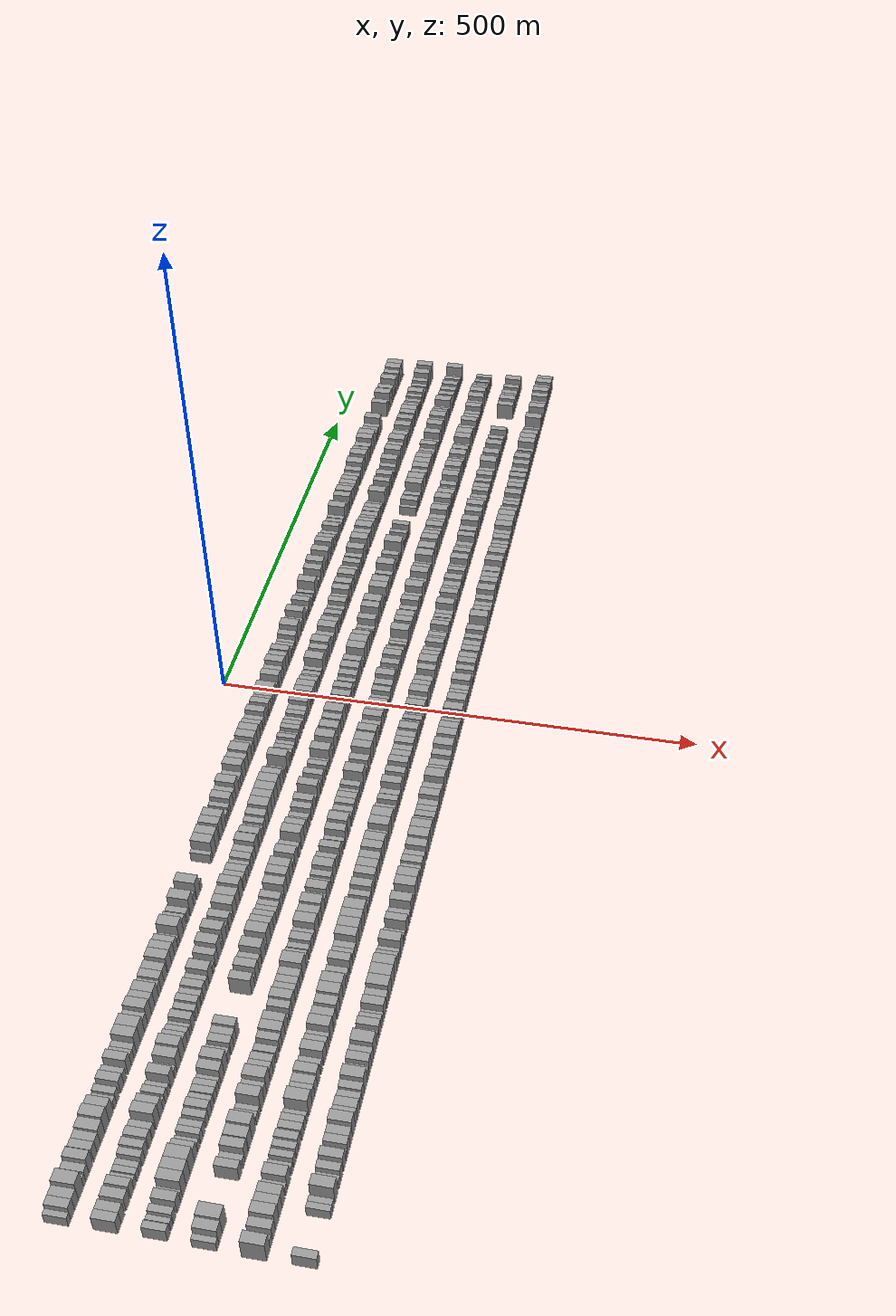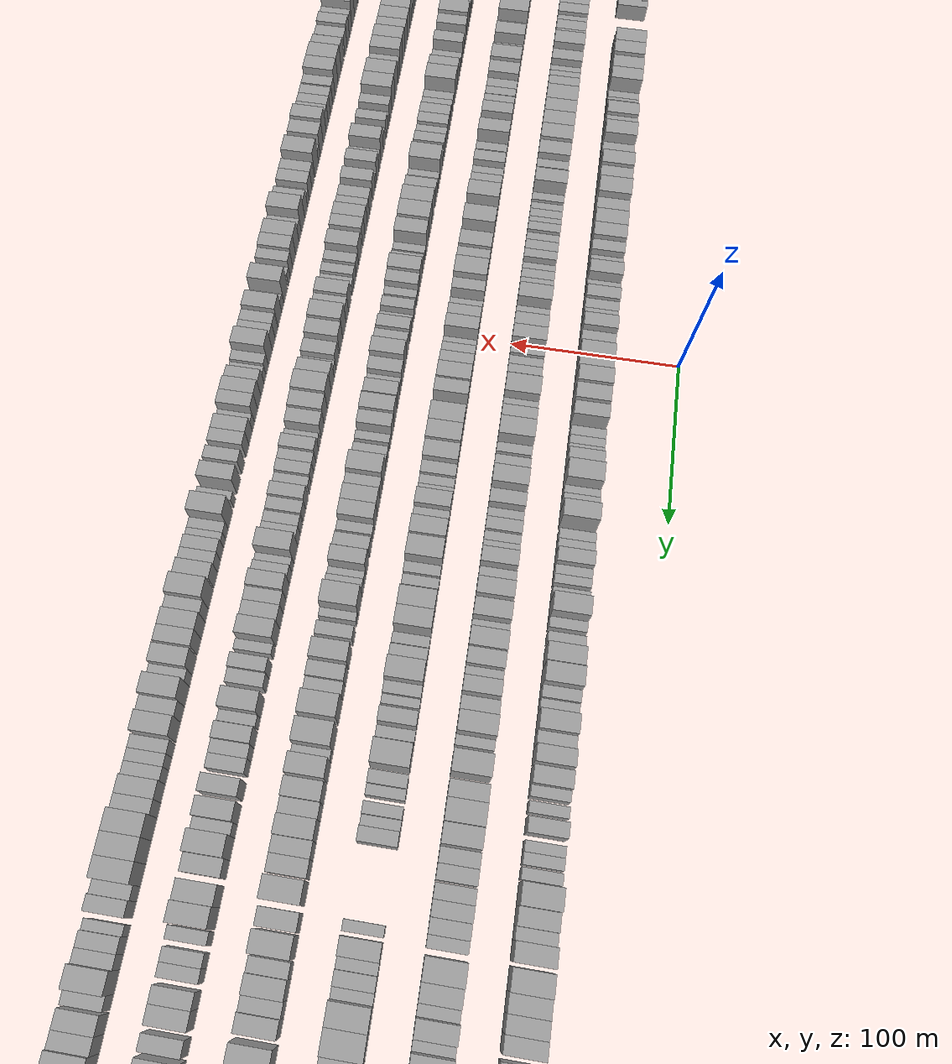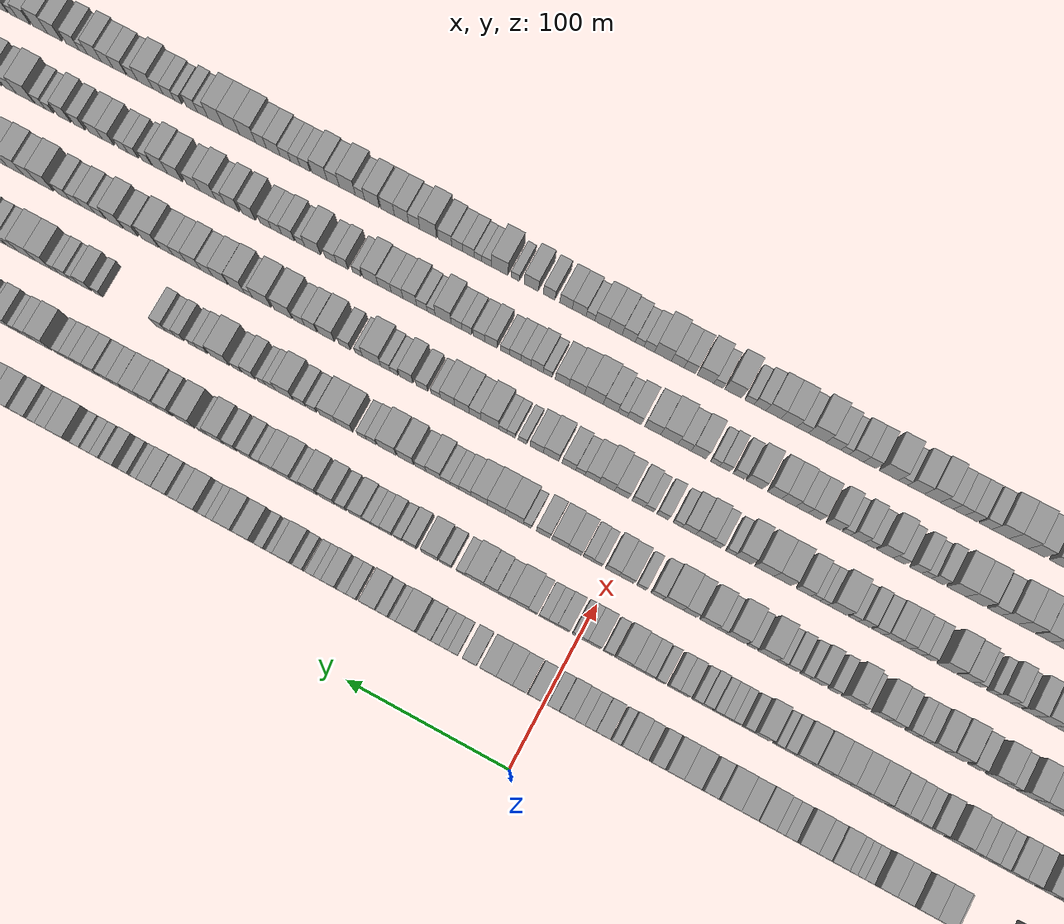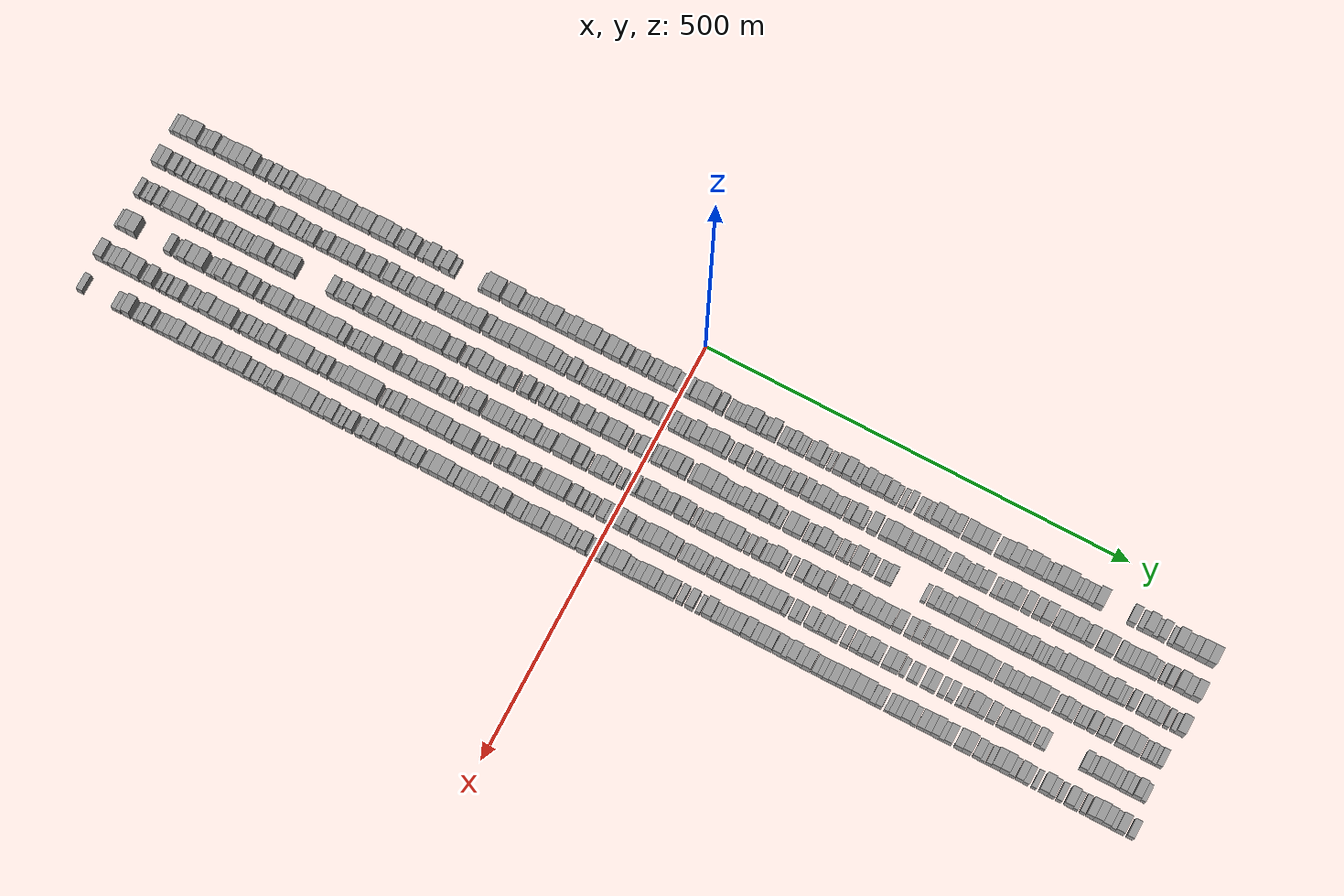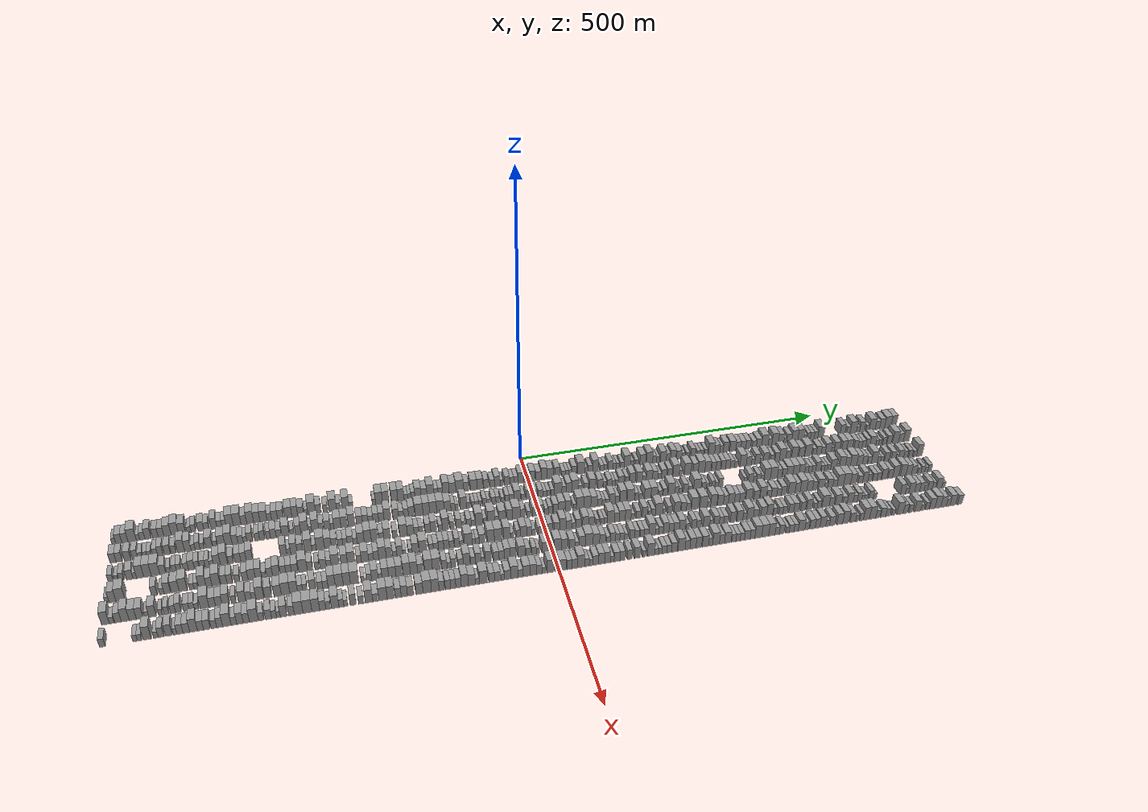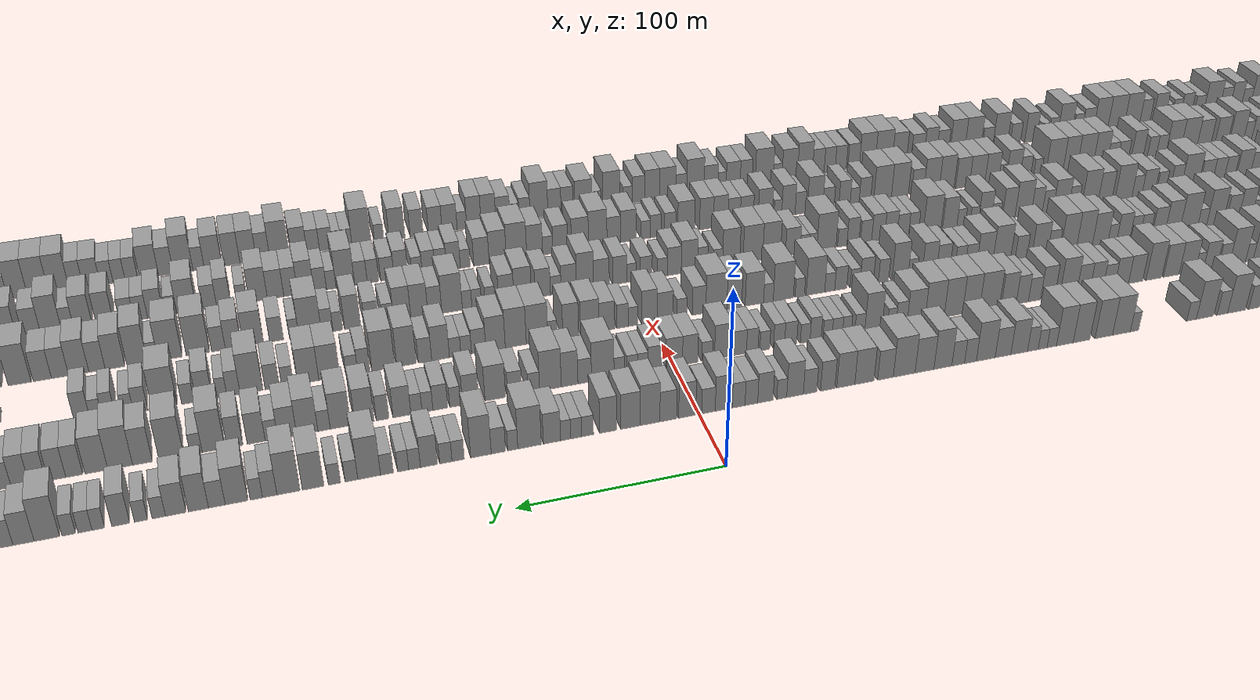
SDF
<sdf version="1.6">
 <world name="default">
  <scene>
   <sky><clouds><speed>12</speed></clouds></sky>
   <ambient>0.4 0.4 0.4 1</ambient>
   <background>0.7 0.7 0.7 1</background>
   <shadows>1</shadows>
  </scene>
  <gravity>0 0 -9.8066</gravity>
  <magnetic_field>6e-06 2.3e-05 -4.2e-05</magnetic_field>
  <physics default="0" name="default_physics" type="ode">
   <ode>
    <solver>
     <type>quick</type>
     <iters>10</iters>
     <sor>1.0</sor>
     <use_dynamic_moi_rescaling>0</use_dynamic_moi_rescaling>
    </solver>
    <constraints>
     <cfm>0</cfm>
     <erp>0.2</erp>
     <contact_max_correcting_vel>100</contact_max_correcting_vel>
     <contact_surface_layer>0.001</contact_surface_layer>
    </constraints>
   </ode>
   <max_step_size>0.004</max_step_size>
   <real_time_factor>1</real_time_factor>
   <real_time_update_rate>250</real_time_update_rate>
  </physics>
  <light name="sun" type="directional">
   <pose>0 0 10 0 0 0</pose>
   <diffuse>0.8 0.8 0.8 1</diffuse>
   <specular>0.2 0.2 0.2 1</specular>
   <attenuation>
    <range>1000</range>
    <constant>0.9</constant>
    <linear>0.01</linear>
    <quadratic>0.001</quadratic>
   </attenuation>
   <direction>-0.5 0.1 -0.9</direction>
  </light>
  <model name="building_1">
   <static>1</static>
   <pose>50.0000 -617.3357 0 0.000000 0.000000 0.000000</pose>
   <link name="link">
    <pose>0 0 6.00 0 0 0</pose>
    <collision name="collision"><geometry><box><size>20.0000 5.3287 12.0000</size></box></geometry></collision>
    <visual name="visual">
     <cast_shadows>0</cast_shadows>
     <geometry><box><size>20.0000 5.3287 12.0000</size></box></geometry>
     <material>
      <script>
       <uri>model://grey_wall/materials/scripts</uri>
       <uri>model://grey_wall/materials/textures</uri>
       <name>vrc/grey_wall</name>
      </script>
     </material>
    </visual>
   </link>
  </model>
  <model name="building_2">
   <static>1</static>
   <pose>50.0000 -610.4913 0 0.000000 0.000000 0.000000</pose>
   <link name="link">
    <pose>0 0 9.00 0 0 0</pose>
    <collision name="collision"><geometry><box><size>20.0000 8.3600 18.0000</size></box></geometry></collision>
    <visual name="visual">
     <cast_shadows>0</cast_shadows>
     <geometry><box><size>20.0000 8.3600 18.0000</size></box></geometry>
     <material>
      <script>
       <uri>model://grey_wall/materials/scripts</uri>
       <uri>model://grey_wall/materials/textures</uri>
       <name>vrc/grey_wall</name>
      </script>
     </material>
    </visual>
   </link>
  </model>
  <model name="building_3">
   <static>1</static>
   <pose>50.0000 -601.9444 0 0.000000 0.000000 0.000000</pose>
   <link name="link">
    <pose>0 0 9.00 0 0 0</pose>
    <collision name="collision"><geometry><box><size>20.0000 8.7338 18.0000</size></box></geometry></collision>
    <visual name="visual">
     <cast_shadows>0</cast_shadows>
     <geometry><box><size>20.0000 8.7338 18.0000</size></box></geometry>
     <material>
      <script>
       <uri>model://grey_wall/materials/scripts</uri>
       <uri>model://grey_wall/materials/textures</uri>
       <name>vrc/grey_wall</name>
      </script>
     </material>
    </visual>
   </link>
  </model>
  <model name="building_4">
   <static>1</static>
   <pose>50.0000 -591.7958 0 0.000000 0.000000 0.000000</pose>
   <link name="link">
    <pose>0 0 12.00 0 0 0</pose>
    <collision name="collision"><geometry><box><size>20.0000 11.5633 24.0000</size></box></geometry></collision>
    <visual name="visual">
     <cast_shadows>0</cast_shadows>
     <geometry><box><size>20.0000 11.5633 24.0000</size></box></geometry>
     <material>
      <script>
       <uri>model://grey_wall/materials/scripts</uri>
       <uri>model://grey_wall/materials/textures</uri>
       <name>vrc/grey_wall</name>
      </script>
     </material>
    </visual>
   </link>
  </model>
  <model name="building_5">
   <static>1</static>
   <pose>50.0000 -583.5711 0 0.000000 0.000000 0.000000</pose>
   <link name="link">
    <pose>0 0 6.00 0 0 0</pose>
    <collision name="collision"><geometry><box><size>20.0000 4.8861 12.0000</size></box></geometry></collision>
    <visual name="visual">
     <cast_shadows>0</cast_shadows>
     <geometry><box><size>20.0000 4.8861 12.0000</size></box></geometry>
     <material>
      <script>
       <uri>model://grey_wall/materials/scripts</uri>
       <uri>model://grey_wall/materials/textures</uri>
       <name>vrc/grey_wall</name>
      </script>
     </material>
    </visual>
   </link>
  </model>
  <model name="building_6">
   <static>1</static>
   <pose>50.0000 -577.5189 0 0.000000 0.000000 0.000000</pose>
   <link name="link">
    <pose>0 0 7.50 0 0 0</pose>
    <collision name="collision"><geometry><box><size>20.0000 7.2183 15.0000</size></box></geometry></collision>
    <visual name="visual">
     <cast_shadows>0</cast_shadows>
     <geometry><box><size>20.0000 7.2183 15.0000</size></box></geometry>
     <material>
      <script>
       <uri>model://grey_wall/materials/scripts</uri>
       <uri>model://grey_wall/materials/textures</uri>
       <name>vrc/grey_wall</name>
      </script>
     </material>
    </visual>
   </link>
  </model>
  <model name="building_7">
   <static>1</static>
   <pose>50.0000 -569.4962 0 0.000000 0.000000 0.000000</pose>
   <link name="link">
    <pose>0 0 10.50 0 0 0</pose>
    <collision name="collision"><geometry><box><size>20.0000 8.8271 21.0000</size></box></geometry></collision>
    <visual name="visual">
     <cast_shadows>0</cast_shadows>
     <geometry><box><size>20.0000 8.8271 21.0000</size></box></geometry>
     <material>
      <script>
       <uri>model://grey_wall/materials/scripts</uri>
       <uri>model://grey_wall/materials/textures</uri>
       <name>vrc/grey_wall</name>
      </script>
     </material>
    </visual>
   </link>
  </model>
  <model name="building_8">
   <static>1</static>
   <pose>50.0000 -559.1384 0 0.000000 0.000000 0.000000</pose>
   <link name="link">
    <pose>0 0 9.00 0 0 0</pose>
    <collision name="collision"><geometry><box><size>20.0000 7.8884 18.0000</size></box></geometry></collision>
    <visual name="visual">
     <cast_shadows>0</cast_shadows>
     <geometry><box><size>20.0000 7.8884 18.0000</size></box></geometry>
     <material>
      <script>
       <uri>model://grey_wall/materials/scripts</uri>
       <uri>model://grey_wall/materials/textures</uri>
       <name>vrc/grey_wall</name>
      </script>
     </material>
    </visual>
   </link>
  </model>
  <model name="building_9">
   <static>1</static>
   <pose>50.0000 -551.1819 0 0.000000 0.000000 0.000000</pose>
   <link name="link">
    <pose>0 0 9.00 0 0 0</pose>
    <collision name="collision"><geometry><box><size>20.0000 8.0247 18.0000</size></box></geometry></collision>
    <visual name="visual">
     <cast_shadows>0</cast_shadows>
     <geometry><box><size>20.0000 8.0247 18.0000</size></box></geometry>
     <material>
      <script>
       <uri>model://grey_wall/materials/scripts</uri>
       <uri>model://grey_wall/materials/textures</uri>
       <name>vrc/grey_wall</name>
      </script>
     </material>
    </visual>
   </link>
  </model>
  <model name="building_10">
   <static>1</static>
   <pose>50.0000 -541.9801 0 0.000000 0.000000 0.000000</pose>
   <link name="link">
    <pose>0 0 10.50 0 0 0</pose>
    <collision name="collision"><geometry><box><size>20.0000 10.3789 21.0000</size></box></geometry></collision>
    <visual name="visual">
     <cast_shadows>0</cast_shadows>
     <geometry><box><size>20.0000 10.3789 21.0000</size></box></geometry>
     <material>
      <script>
       <uri>model://grey_wall/materials/scripts</uri>
       <uri>model://grey_wall/materials/textures</uri>
       <name>vrc/grey_wall</name>
      </script>
     </material>
    </visual>
   </link>
  </model>
  <model name="building_11">
   <static>1</static>
   <pose>50.0000 -531.5980 0 0.000000 0.000000 0.000000</pose>
   <link name="link">
    <pose>0 0 12.00 0 0 0</pose>
    <collision name="collision"><geometry><box><size>20.0000 10.3853 24.0000</size></box></geometry></collision>
    <visual name="visual">
     <cast_shadows>0</cast_shadows>
     <geometry><box><size>20.0000 10.3853 24.0000</size></box></geometry>
     <material>
      <script>
       <uri>model://grey_wall/materials/scripts</uri>
       <uri>model://grey_wall/materials/textures</uri>
       <name>vrc/grey_wall</name>
      </script>
     </material>
    </visual>
   </link>
  </model>
  <model name="building_12">
   <static>1</static>
   <pose>50.0000 -521.3381 0 0.000000 0.000000 0.000000</pose>
   <link name="link">
    <pose>0 0 10.50 0 0 0</pose>
    <collision name="collision"><geometry><box><size>20.0000 10.1346 21.0000</size></box></geometry></collision>
    <visual name="visual">
     <cast_shadows>0</cast_shadows>
     <geometry><box><size>20.0000 10.1346 21.0000</size></box></geometry>
     <material>
      <script>
       <uri>model://grey_wall/materials/scripts</uri>
       <uri>model://grey_wall/materials/textures</uri>
       <name>vrc/grey_wall</name>
      </script>
     </material>
    </visual>
   </link>
  </model>
  <model name="building_13">
   <static>1</static>
   <pose>50.0000 -511.3962 0 0.000000 0.000000 0.000000</pose>
   <link name="link">
    <pose>0 0 6.00 0 0 0</pose>
    <collision name="collision"><geometry><box><size>20.0000 5.7492 12.0000</size></box></geometry></collision>
    <visual name="visual">
     <cast_shadows>0</cast_shadows>
     <geometry><box><size>20.0000 5.7492 12.0000</size></box></geometry>
     <material>
      <script>
       <uri>model://grey_wall/materials/scripts</uri>
       <uri>model://grey_wall/materials/textures</uri>
       <name>vrc/grey_wall</name>
      </script>
     </material>
    </visual>
   </link>
  </model>
  <model name="building_14">
   <static>1</static>
   <pose>50.0000 -505.0866 0 0.000000 0.000000 0.000000</pose>
   <link name="link">
    <pose>0 0 7.50 0 0 0</pose>
    <collision name="collision"><geometry><box><size>20.0000 6.8700 15.0000</size></box></geometry></collision>
    <visual name="visual">
     <cast_shadows>0</cast_shadows>
     <geometry><box><size>20.0000 6.8700 15.0000</size></box></geometry>
     <material>
      <script>
       <uri>model://grey_wall/materials/scripts</uri>
       <uri>model://grey_wall/materials/textures</uri>
       <name>vrc/grey_wall</name>
      </script>
     </material>
    </visual>
   </link>
  </model>
  <model name="building_15">
   <static>1</static>
   <pose>50.0000 -494.3796 0 0.000000 0.000000 0.000000</pose>
   <link name="link">
    <pose>0 0 9.00 0 0 0</pose>
    <collision name="collision"><geometry><box><size>20.0000 8.5440 18.0000</size></box></geometry></collision>
    <visual name="visual">
     <cast_shadows>0</cast_shadows>
     <geometry><box><size>20.0000 8.5440 18.0000</size></box></geometry>
     <material>
      <script>
       <uri>model://grey_wall/materials/scripts</uri>
       <uri>model://grey_wall/materials/textures</uri>
       <name>vrc/grey_wall</name>
      </script>
     </material>
    </visual>
   </link>
  </model>
  <model name="building_16">
   <static>1</static>
   <pose>50.0000 -486.5111 0 0.000000 0.000000 0.000000</pose>
   <link name="link">
    <pose>0 0 7.50 0 0 0</pose>
    <collision name="collision"><geometry><box><size>20.0000 7.1932 15.0000</size></box></geometry></collision>
    <visual name="visual">
     <cast_shadows>0</cast_shadows>
     <geometry><box><size>20.0000 7.1932 15.0000</size></box></geometry>
     <material>
      <script>
       <uri>model://grey_wall/materials/scripts</uri>
       <uri>model://grey_wall/materials/textures</uri>
       <name>vrc/grey_wall</name>
      </script>
     </material>
    </visual>
   </link>
  </model>
  <model name="building_17">
   <static>1</static>
   <pose>50.0000 -475.6811 0 0.000000 0.000000 0.000000</pose>
   <link name="link">
    <pose>0 0 10.50 0 0 0</pose>
    <collision name="collision"><geometry><box><size>20.0000 8.4666 21.0000</size></box></geometry></collision>
    <visual name="visual">
     <cast_shadows>0</cast_shadows>
     <geometry><box><size>20.0000 8.4666 21.0000</size></box></geometry>
     <material>
      <script>
       <uri>model://grey_wall/materials/scripts</uri>
       <uri>model://grey_wall/materials/textures</uri>
       <name>vrc/grey_wall</name>
      </script>
     </material>
    </visual>
   </link>
  </model>
  <model name="building_18">
   <static>1</static>
   <pose>50.0000 -467.9588 0 0.000000 0.000000 0.000000</pose>
   <link name="link">
    <pose>0 0 7.50 0 0 0</pose>
    <collision name="collision"><geometry><box><size>20.0000 6.9781 15.0000</size></box></geometry></collision>
    <visual name="visual">
     <cast_shadows>0</cast_shadows>
     <geometry><box><size>20.0000 6.9781 15.0000</size></box></geometry>
     <material>
      <script>
       <uri>model://grey_wall/materials/scripts</uri>
       <uri>model://grey_wall/materials/textures</uri>
       <name>vrc/grey_wall</name>
      </script>
     </material>
    </visual>
   </link>
  </model>
  <model name="building_19">
   <static>1</static>
   <pose>50.0000 -461.4284 0 0.000000 0.000000 0.000000</pose>
   <link name="link">
    <pose>0 0 7.50 0 0 0</pose>
    <collision name="collision"><geometry><box><size>20.0000 6.0826 15.0000</size></box></geometry></collision>
    <visual name="visual">
     <cast_shadows>0</cast_shadows>
     <geometry><box><size>20.0000 6.0826 15.0000</size></box></geometry>
     <material>
      <script>
       <uri>model://grey_wall/materials/scripts</uri>
       <uri>model://grey_wall/materials/textures</uri>
       <name>vrc/grey_wall</name>
      </script>
     </material>
    </visual>
   </link>
  </model>
  <model name="building_20">
   <static>1</static>
   <pose>50.0000 -453.1435 0 0.000000 0.000000 0.000000</pose>
   <link name="link">
    <pose>0 0 12.00 0 0 0</pose>
    <collision name="collision"><geometry><box><size>20.0000 10.4874 24.0000</size></box></geometry></collision>
    <visual name="visual">
     <cast_shadows>0</cast_shadows>
     <geometry><box><size>20.0000 10.4874 24.0000</size></box></geometry>
     <material>
      <script>
       <uri>model://grey_wall/materials/scripts</uri>
       <uri>model://grey_wall/materials/textures</uri>
       <name>vrc/grey_wall</name>
      </script>
     </material>
    </visual>
   </link>
  </model>
  <model name="building_21">
   <static>1</static>
   <pose>50.0000 -442.4043 0 0.000000 0.000000 0.000000</pose>
   <link name="link">
    <pose>0 0 12.00 0 0 0</pose>
    <collision name="collision"><geometry><box><size>20.0000 10.9910 24.0000</size></box></geometry></collision>
    <visual name="visual">
     <cast_shadows>0</cast_shadows>
     <geometry><box><size>20.0000 10.9910 24.0000</size></box></geometry>
     <material>
      <script>
       <uri>model://grey_wall/materials/scripts</uri>
       <uri>model://grey_wall/materials/textures</uri>
       <name>vrc/grey_wall</name>
      </script>
     </material>
    </visual>
   </link>
  </model>
  <model name="building_22">
   <static>1</static>
   <pose>50.0000 -432.7748 0 0.000000 0.000000 0.000000</pose>
   <link name="link">
    <pose>0 0 9.00 0 0 0</pose>
    <collision name="collision"><geometry><box><size>20.0000 8.2678 18.0000</size></box></geometry></collision>
    <visual name="visual">
     <cast_shadows>0</cast_shadows>
     <geometry><box><size>20.0000 8.2678 18.0000</size></box></geometry>
     <material>
      <script>
       <uri>model://grey_wall/materials/scripts</uri>
       <uri>model://grey_wall/materials/textures</uri>
       <name>vrc/grey_wall</name>
      </script>
     </material>
    </visual>
   </link>
  </model>
  <model name="building_23">
   <static>1</static>
   <pose>50.0000 -423.5001 0 0.000000 0.000000 0.000000</pose>
   <link name="link">
    <pose>0 0 12.00 0 0 0</pose>
    <collision name="collision"><geometry><box><size>20.0000 10.2818 24.0000</size></box></geometry></collision>
    <visual name="visual">
     <cast_shadows>0</cast_shadows>
     <geometry><box><size>20.0000 10.2818 24.0000</size></box></geometry>
     <material>
      <script>
       <uri>model://grey_wall/materials/scripts</uri>
       <uri>model://grey_wall/materials/textures</uri>
       <name>vrc/grey_wall</name>
      </script>
     </material>
    </visual>
   </link>
  </model>
  <model name="building_24">
   <static>1</static>
   <pose>50.0000 -413.8279 0 0.000000 0.000000 0.000000</pose>
   <link name="link">
    <pose>0 0 10.50 0 0 0</pose>
    <collision name="collision"><geometry><box><size>20.0000 9.0625 21.0000</size></box></geometry></collision>
    <visual name="visual">
     <cast_shadows>0</cast_shadows>
     <geometry><box><size>20.0000 9.0625 21.0000</size></box></geometry>
     <material>
      <script>
       <uri>model://grey_wall/materials/scripts</uri>
       <uri>model://grey_wall/materials/textures</uri>
       <name>vrc/grey_wall</name>
      </script>
     </material>
    </visual>
   </link>
  </model>
  <model name="building_25">
   <static>1</static>
   <pose>50.0000 -404.1856 0 0.000000 0.000000 0.000000</pose>
   <link name="link">
    <pose>0 0 10.50 0 0 0</pose>
    <collision name="collision"><geometry><box><size>20.0000 10.2221 21.0000</size></box></geometry></collision>
    <visual name="visual">
     <cast_shadows>0</cast_shadows>
     <geometry><box><size>20.0000 10.2221 21.0000</size></box></geometry>
     <material>
      <script>
       <uri>model://grey_wall/materials/scripts</uri>
       <uri>model://grey_wall/materials/textures</uri>
       <name>vrc/grey_wall</name>
      </script>
     </material>
    </visual>
   </link>
  </model>
  <model name="building_26">
   <static>1</static>
   <pose>50.0000 -395.7539 0 0.000000 0.000000 0.000000</pose>
   <link name="link">
    <pose>0 0 7.50 0 0 0</pose>
    <collision name="collision"><geometry><box><size>20.0000 6.6414 15.0000</size></box></geometry></collision>
    <visual name="visual">
     <cast_shadows>0</cast_shadows>
     <geometry><box><size>20.0000 6.6414 15.0000</size></box></geometry>
     <material>
      <script>
       <uri>model://grey_wall/materials/scripts</uri>
       <uri>model://grey_wall/materials/textures</uri>
       <name>vrc/grey_wall</name>
      </script>
     </material>
    </visual>
   </link>
  </model>
  <model name="building_27">
   <static>1</static>
   <pose>50.0000 -388.0110 0 0.000000 0.000000 0.000000</pose>
   <link name="link">
    <pose>0 0 9.00 0 0 0</pose>
    <collision name="collision"><geometry><box><size>20.0000 8.8443 18.0000</size></box></geometry></collision>
    <visual name="visual">
     <cast_shadows>0</cast_shadows>
     <geometry><box><size>20.0000 8.8443 18.0000</size></box></geometry>
     <material>
      <script>
       <uri>model://grey_wall/materials/scripts</uri>
       <uri>model://grey_wall/materials/textures</uri>
       <name>vrc/grey_wall</name>
      </script>
     </material>
    </visual>
   </link>
  </model>
  <model name="building_28">
   <static>1</static>
   <pose>50.0000 -379.2090 0 0.000000 0.000000 0.000000</pose>
   <link name="link">
    <pose>0 0 9.00 0 0 0</pose>
    <collision name="collision"><geometry><box><size>20.0000 8.7596 18.0000</size></box></geometry></collision>
    <visual name="visual">
     <cast_shadows>0</cast_shadows>
     <geometry><box><size>20.0000 8.7596 18.0000</size></box></geometry>
     <material>
      <script>
       <uri>model://grey_wall/materials/scripts</uri>
       <uri>model://grey_wall/materials/textures</uri>
       <name>vrc/grey_wall</name>
      </script>
     </material>
    </visual>
   </link>
  </model>
  <model name="building_29">
   <static>1</static>
   <pose>50.0000 -367.7330 0 0.000000 0.000000 0.000000</pose>
   <link name="link">
    <pose>0 0 10.50 0 0 0</pose>
    <collision name="collision"><geometry><box><size>20.0000 10.1924 21.0000</size></box></geometry></collision>
    <visual name="visual">
     <cast_shadows>0</cast_shadows>
     <geometry><box><size>20.0000 10.1924 21.0000</size></box></geometry>
     <material>
      <script>
       <uri>model://grey_wall/materials/scripts</uri>
       <uri>model://grey_wall/materials/textures</uri>
       <name>vrc/grey_wall</name>
      </script>
     </material>
    </visual>
   </link>
  </model>
  <model name="building_30">
   <static>1</static>
   <pose>50.0000 -358.2702 0 0.000000 0.000000 0.000000</pose>
   <link name="link">
    <pose>0 0 10.50 0 0 0</pose>
    <collision name="collision"><geometry><box><size>20.0000 8.7333 21.0000</size></box></geometry></collision>
    <visual name="visual">
     <cast_shadows>0</cast_shadows>
     <geometry><box><size>20.0000 8.7333 21.0000</size></box></geometry>
     <material>
      <script>
       <uri>model://grey_wall/materials/scripts</uri>
       <uri>model://grey_wall/materials/textures</uri>
       <name>vrc/grey_wall</name>
      </script>
     </material>
    </visual>
   </link>
  </model>
  <model name="building_31">
   <static>1</static>
   <pose>50.0000 -349.4542 0 0.000000 0.000000 0.000000</pose>
   <link name="link">
    <pose>0 0 9.00 0 0 0</pose>
    <collision name="collision"><geometry><box><size>20.0000 8.8986 18.0000</size></box></geometry></collision>
    <visual name="visual">
     <cast_shadows>0</cast_shadows>
     <geometry><box><size>20.0000 8.8986 18.0000</size></box></geometry>
     <material>
      <script>
       <uri>model://grey_wall/materials/scripts</uri>
       <uri>model://grey_wall/materials/textures</uri>
       <name>vrc/grey_wall</name>
      </script>
     </material>
    </visual>
   </link>
  </model>
  <model name="building_32">
   <static>1</static>
   <pose>50.0000 -341.4069 0 0.000000 0.000000 0.000000</pose>
   <link name="link">
    <pose>0 0 6.00 0 0 0</pose>
    <collision name="collision"><geometry><box><size>20.0000 5.1960 12.0000</size></box></geometry></collision>
    <visual name="visual">
     <cast_shadows>0</cast_shadows>
     <geometry><box><size>20.0000 5.1960 12.0000</size></box></geometry>
     <material>
      <script>
       <uri>model://grey_wall/materials/scripts</uri>
       <uri>model://grey_wall/materials/textures</uri>
       <name>vrc/grey_wall</name>
      </script>
     </material>
    </visual>
   </link>
  </model>
  <model name="building_33">
   <static>1</static>
   <pose>50.0000 -333.0868 0 0.000000 0.000000 0.000000</pose>
   <link name="link">
    <pose>0 0 12.00 0 0 0</pose>
    <collision name="collision"><geometry><box><size>20.0000 11.4443 24.0000</size></box></geometry></collision>
    <visual name="visual">
     <cast_shadows>0</cast_shadows>
     <geometry><box><size>20.0000 11.4443 24.0000</size></box></geometry>
     <material>
      <script>
       <uri>model://grey_wall/materials/scripts</uri>
       <uri>model://grey_wall/materials/textures</uri>
       <name>vrc/grey_wall</name>
      </script>
     </material>
    </visual>
   </link>
  </model>
  <model name="building_34">
   <static>1</static>
   <pose>50.0000 -323.3204 0 0.000000 0.000000 0.000000</pose>
   <link name="link">
    <pose>0 0 9.00 0 0 0</pose>
    <collision name="collision"><geometry><box><size>20.0000 8.0884 18.0000</size></box></geometry></collision>
    <visual name="visual">
     <cast_shadows>0</cast_shadows>
     <geometry><box><size>20.0000 8.0884 18.0000</size></box></geometry>
     <material>
      <script>
       <uri>model://grey_wall/materials/scripts</uri>
       <uri>model://grey_wall/materials/textures</uri>
       <name>vrc/grey_wall</name>
      </script>
     </material>
    </visual>
   </link>
  </model>
  <model name="building_35">
   <static>1</static>
   <pose>50.0000 -312.8151 0 0.000000 0.000000 0.000000</pose>
   <link name="link">
    <pose>0 0 7.50 0 0 0</pose>
    <collision name="collision"><geometry><box><size>20.0000 6.9221 15.0000</size></box></geometry></collision>
    <visual name="visual">
     <cast_shadows>0</cast_shadows>
     <geometry><box><size>20.0000 6.9221 15.0000</size></box></geometry>
     <material>
      <script>
       <uri>model://grey_wall/materials/scripts</uri>
       <uri>model://grey_wall/materials/textures</uri>
       <name>vrc/grey_wall</name>
      </script>
     </material>
    </visual>
   </link>
  </model>
  <model name="building_36">
   <static>1</static>
   <pose>50.0000 -301.8305 0 0.000000 0.000000 0.000000</pose>
   <link name="link">
    <pose>0 0 12.00 0 0 0</pose>
    <collision name="collision"><geometry><box><size>20.0000 11.0471 24.0000</size></box></geometry></collision>
    <visual name="visual">
     <cast_shadows>0</cast_shadows>
     <geometry><box><size>20.0000 11.0471 24.0000</size></box></geometry>
     <material>
      <script>
       <uri>model://grey_wall/materials/scripts</uri>
       <uri>model://grey_wall/materials/textures</uri>
       <name>vrc/grey_wall</name>
      </script>
     </material>
    </visual>
   </link>
  </model>
  <model name="building_37">
   <static>1</static>
   <pose>50.0000 -293.0768 0 0.000000 0.000000 0.000000</pose>
   <link name="link">
    <pose>0 0 7.50 0 0 0</pose>
    <collision name="collision"><geometry><box><size>20.0000 6.4604 15.0000</size></box></geometry></collision>
    <visual name="visual">
     <cast_shadows>0</cast_shadows>
     <geometry><box><size>20.0000 6.4604 15.0000</size></box></geometry>
     <material>
      <script>
       <uri>model://grey_wall/materials/scripts</uri>
       <uri>model://grey_wall/materials/textures</uri>
       <name>vrc/grey_wall</name>
      </script>
     </material>
    </visual>
   </link>
  </model>
  <model name="building_38">
   <static>1</static>
   <pose>50.0000 -282.5672 0 0.000000 0.000000 0.000000</pose>
   <link name="link">
    <pose>0 0 12.00 0 0 0</pose>
    <collision name="collision"><geometry><box><size>20.0000 10.5588 24.0000</size></box></geometry></collision>
    <visual name="visual">
     <cast_shadows>0</cast_shadows>
     <geometry><box><size>20.0000 10.5588 24.0000</size></box></geometry>
     <material>
      <script>
       <uri>model://grey_wall/materials/scripts</uri>
       <uri>model://grey_wall/materials/textures</uri>
       <name>vrc/grey_wall</name>
      </script>
     </material>
    </visual>
   </link>
  </model>
  <model name="building_39">
   <static>1</static>
   <pose>50.0000 -274.3519 0 0.000000 0.000000 0.000000</pose>
   <link name="link">
    <pose>0 0 6.00 0 0 0</pose>
    <collision name="collision"><geometry><box><size>20.0000 5.8718 12.0000</size></box></geometry></collision>
    <visual name="visual">
     <cast_shadows>0</cast_shadows>
     <geometry><box><size>20.0000 5.8718 12.0000</size></box></geometry>
     <material>
      <script>
       <uri>model://grey_wall/materials/scripts</uri>
       <uri>model://grey_wall/materials/textures</uri>
       <name>vrc/grey_wall</name>
      </script>
     </material>
    </visual>
   </link>
  </model>
  <model name="building_40">
   <static>1</static>
   <pose>50.0000 -240.0656 0 0.000000 0.000000 0.000000</pose>
   <link name="link">
    <pose>0 0 6.00 0 0 0</pose>
    <collision name="collision"><geometry><box><size>20.0000 4.9003 12.0000</size></box></geometry></collision>
    <visual name="visual">
     <cast_shadows>0</cast_shadows>
     <geometry><box><size>20.0000 4.9003 12.0000</size></box></geometry>
     <material>
      <script>
       <uri>model://grey_wall/materials/scripts</uri>
       <uri>model://grey_wall/materials/textures</uri>
       <name>vrc/grey_wall</name>
      </script>
     </material>
    </visual>
   </link>
  </model>
  <model name="building_41">
   <static>1</static>
   <pose>50.0000 -232.3175 0 0.000000 0.000000 0.000000</pose>
   <link name="link">
    <pose>0 0 12.00 0 0 0</pose>
    <collision name="collision"><geometry><box><size>20.0000 10.5959 24.0000</size></box></geometry></collision>
    <visual name="visual">
     <cast_shadows>0</cast_shadows>
     <geometry><box><size>20.0000 10.5959 24.0000</size></box></geometry>
     <material>
      <script>
       <uri>model://grey_wall/materials/scripts</uri>
       <uri>model://grey_wall/materials/textures</uri>
       <name>vrc/grey_wall</name>
      </script>
     </material>
    </visual>
   </link>
  </model>
  <model name="building_42">
   <static>1</static>
   <pose>50.0000 -221.8709 0 0.000000 0.000000 0.000000</pose>
   <link name="link">
    <pose>0 0 12.00 0 0 0</pose>
    <collision name="collision"><geometry><box><size>20.0000 10.2973 24.0000</size></box></geometry></collision>
    <visual name="visual">
     <cast_shadows>0</cast_shadows>
     <geometry><box><size>20.0000 10.2973 24.0000</size></box></geometry>
     <material>
      <script>
       <uri>model://grey_wall/materials/scripts</uri>
       <uri>model://grey_wall/materials/textures</uri>
       <name>vrc/grey_wall</name>
      </script>
     </material>
    </visual>
   </link>
  </model>
  <model name="building_43">
   <static>1</static>
   <pose>50.0000 -208.8454 0 0.000000 0.000000 0.000000</pose>
   <link name="link">
    <pose>0 0 12.00 0 0 0</pose>
    <collision name="collision"><geometry><box><size>20.0000 9.7536 24.0000</size></box></geometry></collision>
    <visual name="visual">
     <cast_shadows>0</cast_shadows>
     <geometry><box><size>20.0000 9.7536 24.0000</size></box></geometry>
     <material>
      <script>
       <uri>model://grey_wall/materials/scripts</uri>
       <uri>model://grey_wall/materials/textures</uri>
       <name>vrc/grey_wall</name>
      </script>
     </material>
    </visual>
   </link>
  </model>
  <model name="building_44">
   <static>1</static>
   <pose>50.0000 -199.1187 0 0.000000 0.000000 0.000000</pose>
   <link name="link">
    <pose>0 0 12.00 0 0 0</pose>
    <collision name="collision"><geometry><box><size>20.0000 9.6998 24.0000</size></box></geometry></collision>
    <visual name="visual">
     <cast_shadows>0</cast_shadows>
     <geometry><box><size>20.0000 9.6998 24.0000</size></box></geometry>
     <material>
      <script>
       <uri>model://grey_wall/materials/scripts</uri>
       <uri>model://grey_wall/materials/textures</uri>
       <name>vrc/grey_wall</name>
      </script>
     </material>
    </visual>
   </link>
  </model>
  <model name="building_45">
   <static>1</static>
   <pose>50.0000 -191.5245 0 0.000000 0.000000 0.000000</pose>
   <link name="link">
    <pose>0 0 6.00 0 0 0</pose>
    <collision name="collision"><geometry><box><size>20.0000 5.4886 12.0000</size></box></geometry></collision>
    <visual name="visual">
     <cast_shadows>0</cast_shadows>
     <geometry><box><size>20.0000 5.4886 12.0000</size></box></geometry>
     <material>
      <script>
       <uri>model://grey_wall/materials/scripts</uri>
       <uri>model://grey_wall/materials/textures</uri>
       <name>vrc/grey_wall</name>
      </script>
     </material>
    </visual>
   </link>
  </model>
  <model name="building_46">
   <static>1</static>
   <pose>50.0000 -186.2213 0 0.000000 0.000000 0.000000</pose>
   <link name="link">
    <pose>0 0 6.00 0 0 0</pose>
    <collision name="collision"><geometry><box><size>20.0000 5.1179 12.0000</size></box></geometry></collision>
    <visual name="visual">
     <cast_shadows>0</cast_shadows>
     <geometry><box><size>20.0000 5.1179 12.0000</size></box></geometry>
     <material>
      <script>
       <uri>model://grey_wall/materials/scripts</uri>
       <uri>model://grey_wall/materials/textures</uri>
       <name>vrc/grey_wall</name>
      </script>
     </material>
    </visual>
   </link>
  </model>
  <model name="building_47">
   <static>1</static>
   <pose>50.0000 -180.6284 0 0.000000 0.000000 0.000000</pose>
   <link name="link">
    <pose>0 0 7.50 0 0 0</pose>
    <collision name="collision"><geometry><box><size>20.0000 6.0679 15.0000</size></box></geometry></collision>
    <visual name="visual">
     <cast_shadows>0</cast_shadows>
     <geometry><box><size>20.0000 6.0679 15.0000</size></box></geometry>
     <material>
      <script>
       <uri>model://grey_wall/materials/scripts</uri>
       <uri>model://grey_wall/materials/textures</uri>
       <name>vrc/grey_wall</name>
      </script>
     </material>
    </visual>
   </link>
  </model>
  <model name="building_48">
   <static>1</static>
   <pose>50.0000 -172.8071 0 0.000000 0.000000 0.000000</pose>
   <link name="link">
    <pose>0 0 10.50 0 0 0</pose>
    <collision name="collision"><geometry><box><size>20.0000 9.5747 21.0000</size></box></geometry></collision>
    <visual name="visual">
     <cast_shadows>0</cast_shadows>
     <geometry><box><size>20.0000 9.5747 21.0000</size></box></geometry>
     <material>
      <script>
       <uri>model://grey_wall/materials/scripts</uri>
       <uri>model://grey_wall/materials/textures</uri>
       <name>vrc/grey_wall</name>
      </script>
     </material>
    </visual>
   </link>
  </model>
  <model name="building_49">
   <static>1</static>
   <pose>50.0000 -163.5866 0 0.000000 0.000000 0.000000</pose>
   <link name="link">
    <pose>0 0 9.00 0 0 0</pose>
    <collision name="collision"><geometry><box><size>20.0000 8.8664 18.0000</size></box></geometry></collision>
    <visual name="visual">
     <cast_shadows>0</cast_shadows>
     <geometry><box><size>20.0000 8.8664 18.0000</size></box></geometry>
     <material>
      <script>
       <uri>model://grey_wall/materials/scripts</uri>
       <uri>model://grey_wall/materials/textures</uri>
       <name>vrc/grey_wall</name>
      </script>
     </material>
    </visual>
   </link>
  </model>
  <model name="building_50">
   <static>1</static>
   <pose>50.0000 -153.8439 0 0.000000 0.000000 0.000000</pose>
   <link name="link">
    <pose>0 0 12.00 0 0 0</pose>
    <collision name="collision"><geometry><box><size>20.0000 10.6192 24.0000</size></box></geometry></collision>
    <visual name="visual">
     <cast_shadows>0</cast_shadows>
     <geometry><box><size>20.0000 10.6192 24.0000</size></box></geometry>
     <material>
      <script>
       <uri>model://grey_wall/materials/scripts</uri>
       <uri>model://grey_wall/materials/textures</uri>
       <name>vrc/grey_wall</name>
      </script>
     </material>
    </visual>
   </link>
  </model>
  <model name="building_51">
   <static>1</static>
   <pose>50.0000 -145.2161 0 0.000000 0.000000 0.000000</pose>
   <link name="link">
    <pose>0 0 7.50 0 0 0</pose>
    <collision name="collision"><geometry><box><size>20.0000 6.6364 15.0000</size></box></geometry></collision>
    <visual name="visual">
     <cast_shadows>0</cast_shadows>
     <geometry><box><size>20.0000 6.6364 15.0000</size></box></geometry>
     <material>
      <script>
       <uri>model://grey_wall/materials/scripts</uri>
       <uri>model://grey_wall/materials/textures</uri>
       <name>vrc/grey_wall</name>
      </script>
     </material>
    </visual>
   </link>
  </model>
  <model name="building_52">
   <static>1</static>
   <pose>50.0000 -138.3715 0 0.000000 0.000000 0.000000</pose>
   <link name="link">
    <pose>0 0 7.50 0 0 0</pose>
    <collision name="collision"><geometry><box><size>20.0000 7.0527 15.0000</size></box></geometry></collision>
    <visual name="visual">
     <cast_shadows>0</cast_shadows>
     <geometry><box><size>20.0000 7.0527 15.0000</size></box></geometry>
     <material>
      <script>
       <uri>model://grey_wall/materials/scripts</uri>
       <uri>model://grey_wall/materials/textures</uri>
       <name>vrc/grey_wall</name>
      </script>
     </material>
    </visual>
   </link>
  </model>
  <model name="building_53">
   <static>1</static>
   <pose>50.0000 -129.8535 0 0.000000 0.000000 0.000000</pose>
   <link name="link">
    <pose>0 0 12.00 0 0 0</pose>
    <collision name="collision"><geometry><box><size>20.0000 9.9832 24.0000</size></box></geometry></collision>
    <visual name="visual">
     <cast_shadows>0</cast_shadows>
     <geometry><box><size>20.0000 9.9832 24.0000</size></box></geometry>
     <material>
      <script>
       <uri>model://grey_wall/materials/scripts</uri>
       <uri>model://grey_wall/materials/textures</uri>
       <name>vrc/grey_wall</name>
      </script>
     </material>
    </visual>
   </link>
  </model>
  <model name="building_54">
   <static>1</static>
   <pose>50.0000 -119.6604 0 0.000000 0.000000 0.000000</pose>
   <link name="link">
    <pose>0 0 10.50 0 0 0</pose>
    <collision name="collision"><geometry><box><size>20.0000 10.4030 21.0000</size></box></geometry></collision>
    <visual name="visual">
     <cast_shadows>0</cast_shadows>
     <geometry><box><size>20.0000 10.4030 21.0000</size></box></geometry>
     <material>
      <script>
       <uri>model://grey_wall/materials/scripts</uri>
       <uri>model://grey_wall/materials/textures</uri>
       <name>vrc/grey_wall</name>
      </script>
     </material>
    </visual>
   </link>
  </model>
  <model name="building_55">
   <static>1</static>
   <pose>50.0000 -108.4930 0 0.000000 0.000000 0.000000</pose>
   <link name="link">
    <pose>0 0 12.00 0 0 0</pose>
    <collision name="collision"><geometry><box><size>20.0000 11.9318 24.0000</size></box></geometry></collision>
    <visual name="visual">
     <cast_shadows>0</cast_shadows>
     <geometry><box><size>20.0000 11.9318 24.0000</size></box></geometry>
     <material>
      <script>
       <uri>model://grey_wall/materials/scripts</uri>
       <uri>model://grey_wall/materials/textures</uri>
       <name>vrc/grey_wall</name>
      </script>
     </material>
    </visual>
   </link>
  </model>
  <model name="building_56">
   <static>1</static>
   <pose>50.0000 -98.2424 0 0.000000 0.000000 0.000000</pose>
   <link name="link">
    <pose>0 0 9.00 0 0 0</pose>
    <collision name="collision"><geometry><box><size>20.0000 8.5694 18.0000</size></box></geometry></collision>
    <visual name="visual">
     <cast_shadows>0</cast_shadows>
     <geometry><box><size>20.0000 8.5694 18.0000</size></box></geometry>
     <material>
      <script>
       <uri>model://grey_wall/materials/scripts</uri>
       <uri>model://grey_wall/materials/textures</uri>
       <name>vrc/grey_wall</name>
      </script>
     </material>
    </visual>
   </link>
  </model>
  <model name="building_57">
   <static>1</static>
   <pose>50.0000 -86.7762 0 0.000000 0.000000 0.000000</pose>
   <link name="link">
    <pose>0 0 10.50 0 0 0</pose>
    <collision name="collision"><geometry><box><size>20.0000 10.3632 21.0000</size></box></geometry></collision>
    <visual name="visual">
     <cast_shadows>0</cast_shadows>
     <geometry><box><size>20.0000 10.3632 21.0000</size></box></geometry>
     <material>
      <script>
       <uri>model://grey_wall/materials/scripts</uri>
       <uri>model://grey_wall/materials/textures</uri>
       <name>vrc/grey_wall</name>
      </script>
     </material>
    </visual>
   </link>
  </model>
  <model name="building_58">
   <static>1</static>
   <pose>50.0000 -76.7567 0 0.000000 0.000000 0.000000</pose>
   <link name="link">
    <pose>0 0 10.50 0 0 0</pose>
    <collision name="collision"><geometry><box><size>20.0000 9.6757 21.0000</size></box></geometry></collision>
    <visual name="visual">
     <cast_shadows>0</cast_shadows>
     <geometry><box><size>20.0000 9.6757 21.0000</size></box></geometry>
     <material>
      <script>
       <uri>model://grey_wall/materials/scripts</uri>
       <uri>model://grey_wall/materials/textures</uri>
       <name>vrc/grey_wall</name>
      </script>
     </material>
    </visual>
   </link>
  </model>
  <model name="building_59">
   <static>1</static>
   <pose>50.0000 -67.0836 0 0.000000 0.000000 0.000000</pose>
   <link name="link">
    <pose>0 0 9.00 0 0 0</pose>
    <collision name="collision"><geometry><box><size>20.0000 7.6705 18.0000</size></box></geometry></collision>
    <visual name="visual">
     <cast_shadows>0</cast_shadows>
     <geometry><box><size>20.0000 7.6705 18.0000</size></box></geometry>
     <material>
      <script>
       <uri>model://grey_wall/materials/scripts</uri>
       <uri>model://grey_wall/materials/textures</uri>
       <name>vrc/grey_wall</name>
      </script>
     </material>
    </visual>
   </link>
  </model>
  <model name="building_60">
   <static>1</static>
   <pose>50.0000 -57.6711 0 0.000000 0.000000 0.000000</pose>
   <link name="link">
    <pose>0 0 7.50 0 0 0</pose>
    <collision name="collision"><geometry><box><size>20.0000 7.1544 15.0000</size></box></geometry></collision>
    <visual name="visual">
     <cast_shadows>0</cast_shadows>
     <geometry><box><size>20.0000 7.1544 15.0000</size></box></geometry>
     <material>
      <script>
       <uri>model://grey_wall/materials/scripts</uri>
       <uri>model://grey_wall/materials/textures</uri>
       <name>vrc/grey_wall</name>
      </script>
     </material>
    </visual>
   </link>
  </model>
  <model name="building_61">
   <static>1</static>
   <pose>50.0000 -49.6958 0 0.000000 0.000000 0.000000</pose>
   <link name="link">
    <pose>0 0 10.50 0 0 0</pose>
    <collision name="collision"><geometry><box><size>20.0000 8.7962 21.0000</size></box></geometry></collision>
    <visual name="visual">
     <cast_shadows>0</cast_shadows>
     <geometry><box><size>20.0000 8.7962 21.0000</size></box></geometry>
     <material>
      <script>
       <uri>model://grey_wall/materials/scripts</uri>
       <uri>model://grey_wall/materials/textures</uri>
       <name>vrc/grey_wall</name>
      </script>
     </material>
    </visual>
   </link>
  </model>
  <model name="building_62">
   <static>1</static>
   <pose>50.0000 -42.6953 0 0.000000 0.000000 0.000000</pose>
   <link name="link">
    <pose>0 0 6.00 0 0 0</pose>
    <collision name="collision"><geometry><box><size>20.0000 5.2047 12.0000</size></box></geometry></collision>
    <visual name="visual">
     <cast_shadows>0</cast_shadows>
     <geometry><box><size>20.0000 5.2047 12.0000</size></box></geometry>
     <material>
      <script>
       <uri>model://grey_wall/materials/scripts</uri>
       <uri>model://grey_wall/materials/textures</uri>
       <name>vrc/grey_wall</name>
      </script>
     </material>
    </visual>
   </link>
  </model>
  <model name="building_63">
   <static>1</static>
   <pose>50.0000 -34.0878 0 0.000000 0.000000 0.000000</pose>
   <link name="link">
    <pose>0 0 9.00 0 0 0</pose>
    <collision name="collision"><geometry><box><size>20.0000 8.0103 18.0000</size></box></geometry></collision>
    <visual name="visual">
     <cast_shadows>0</cast_shadows>
     <geometry><box><size>20.0000 8.0103 18.0000</size></box></geometry>
     <material>
      <script>
       <uri>model://grey_wall/materials/scripts</uri>
       <uri>model://grey_wall/materials/textures</uri>
       <name>vrc/grey_wall</name>
      </script>
     </material>
    </visual>
   </link>
  </model>
  <model name="building_64">
   <static>1</static>
   <pose>50.0000 -26.7853 0 0.000000 0.000000 0.000000</pose>
   <link name="link">
    <pose>0 0 7.50 0 0 0</pose>
    <collision name="collision"><geometry><box><size>20.0000 6.5948 15.0000</size></box></geometry></collision>
    <visual name="visual">
     <cast_shadows>0</cast_shadows>
     <geometry><box><size>20.0000 6.5948 15.0000</size></box></geometry>
     <material>
      <script>
       <uri>model://grey_wall/materials/scripts</uri>
       <uri>model://grey_wall/materials/textures</uri>
       <name>vrc/grey_wall</name>
      </script>
     </material>
    </visual>
   </link>
  </model>
  <model name="building_65">
   <static>1</static>
   <pose>50.0000 -20.1616 0 0.000000 0.000000 0.000000</pose>
   <link name="link">
    <pose>0 0 7.50 0 0 0</pose>
    <collision name="collision"><geometry><box><size>20.0000 6.6525 15.0000</size></box></geometry></collision>
    <visual name="visual">
     <cast_shadows>0</cast_shadows>
     <geometry><box><size>20.0000 6.6525 15.0000</size></box></geometry>
     <material>
      <script>
       <uri>model://grey_wall/materials/scripts</uri>
       <uri>model://grey_wall/materials/textures</uri>
       <name>vrc/grey_wall</name>
      </script>
     </material>
    </visual>
   </link>
  </model>
  <model name="building_66">
   <static>1</static>
   <pose>50.0000 -12.4660 0 0.000000 0.000000 0.000000</pose>
   <link name="link">
    <pose>0 0 10.50 0 0 0</pose>
    <collision name="collision"><geometry><box><size>20.0000 8.7388 21.0000</size></box></geometry></collision>
    <visual name="visual">
     <cast_shadows>0</cast_shadows>
     <geometry><box><size>20.0000 8.7388 21.0000</size></box></geometry>
     <material>
      <script>
       <uri>model://grey_wall/materials/scripts</uri>
       <uri>model://grey_wall/materials/textures</uri>
       <name>vrc/grey_wall</name>
      </script>
     </material>
    </visual>
   </link>
  </model>
  <model name="building_67">
   <static>1</static>
   <pose>50.0000 -4.6055 0 0.000000 0.000000 0.000000</pose>
   <link name="link">
    <pose>0 0 7.50 0 0 0</pose>
    <collision name="collision"><geometry><box><size>20.0000 6.9823 15.0000</size></box></geometry></collision>
    <visual name="visual">
     <cast_shadows>0</cast_shadows>
     <geometry><box><size>20.0000 6.9823 15.0000</size></box></geometry>
     <material>
      <script>
       <uri>model://grey_wall/materials/scripts</uri>
       <uri>model://grey_wall/materials/textures</uri>
       <name>vrc/grey_wall</name>
      </script>
     </material>
    </visual>
   </link>
  </model>
  <model name="building_68">
   <static>1</static>
   <pose>50.0000 6.2458 0 0.000000 0.000000 0.000000</pose>
   <link name="link">
    <pose>0 0 10.50 0 0 0</pose>
    <collision name="collision"><geometry><box><size>20.0000 8.7205 21.0000</size></box></geometry></collision>
    <visual name="visual">
     <cast_shadows>0</cast_shadows>
     <geometry><box><size>20.0000 8.7205 21.0000</size></box></geometry>
     <material>
      <script>
       <uri>model://grey_wall/materials/scripts</uri>
       <uri>model://grey_wall/materials/textures</uri>
       <name>vrc/grey_wall</name>
      </script>
     </material>
    </visual>
   </link>
  </model>
  <model name="building_69">
   <static>1</static>
   <pose>50.0000 15.8395 0 0.000000 0.000000 0.000000</pose>
   <link name="link">
    <pose>0 0 9.00 0 0 0</pose>
    <collision name="collision"><geometry><box><size>20.0000 8.4667 18.0000</size></box></geometry></collision>
    <visual name="visual">
     <cast_shadows>0</cast_shadows>
     <geometry><box><size>20.0000 8.4667 18.0000</size></box></geometry>
     <material>
      <script>
       <uri>model://grey_wall/materials/scripts</uri>
       <uri>model://grey_wall/materials/textures</uri>
       <name>vrc/grey_wall</name>
      </script>
     </material>
    </visual>
   </link>
  </model>
  <model name="building_70">
   <static>1</static>
   <pose>50.0000 24.9663 0 0.000000 0.000000 0.000000</pose>
   <link name="link">
    <pose>0 0 12.00 0 0 0</pose>
    <collision name="collision"><geometry><box><size>20.0000 9.7870 24.0000</size></box></geometry></collision>
    <visual name="visual">
     <cast_shadows>0</cast_shadows>
     <geometry><box><size>20.0000 9.7870 24.0000</size></box></geometry>
     <material>
      <script>
       <uri>model://grey_wall/materials/scripts</uri>
       <uri>model://grey_wall/materials/textures</uri>
       <name>vrc/grey_wall</name>
      </script>
     </material>
    </visual>
   </link>
  </model>
  <model name="building_71">
   <static>1</static>
   <pose>50.0000 34.7830 0 0.000000 0.000000 0.000000</pose>
   <link name="link">
    <pose>0 0 10.50 0 0 0</pose>
    <collision name="collision"><geometry><box><size>20.0000 9.8464 21.0000</size></box></geometry></collision>
    <visual name="visual">
     <cast_shadows>0</cast_shadows>
     <geometry><box><size>20.0000 9.8464 21.0000</size></box></geometry>
     <material>
      <script>
       <uri>model://grey_wall/materials/scripts</uri>
       <uri>model://grey_wall/materials/textures</uri>
       <name>vrc/grey_wall</name>
      </script>
     </material>
    </visual>
   </link>
  </model>
  <model name="building_72">
   <static>1</static>
   <pose>50.0000 45.9654 0 0.000000 0.000000 0.000000</pose>
   <link name="link">
    <pose>0 0 10.50 0 0 0</pose>
    <collision name="collision"><geometry><box><size>20.0000 8.5184 21.0000</size></box></geometry></collision>
    <visual name="visual">
     <cast_shadows>0</cast_shadows>
     <geometry><box><size>20.0000 8.5184 21.0000</size></box></geometry>
     <material>
      <script>
       <uri>model://grey_wall/materials/scripts</uri>
       <uri>model://grey_wall/materials/textures</uri>
       <name>vrc/grey_wall</name>
      </script>
     </material>
    </visual>
   </link>
  </model>
  <model name="building_73">
   <static>1</static>
   <pose>50.0000 56.1927 0 0.000000 0.000000 0.000000</pose>
   <link name="link">
    <pose>0 0 6.00 0 0 0</pose>
    <collision name="collision"><geometry><box><size>20.0000 5.9361 12.0000</size></box></geometry></collision>
    <visual name="visual">
     <cast_shadows>0</cast_shadows>
     <geometry><box><size>20.0000 5.9361 12.0000</size></box></geometry>
     <material>
      <script>
       <uri>model://grey_wall/materials/scripts</uri>
       <uri>model://grey_wall/materials/textures</uri>
       <name>vrc/grey_wall</name>
      </script>
     </material>
    </visual>
   </link>
  </model>
  <model name="building_74">
   <static>1</static>
   <pose>50.0000 61.8321 0 0.000000 0.000000 0.000000</pose>
   <link name="link">
    <pose>0 0 6.00 0 0 0</pose>
    <collision name="collision"><geometry><box><size>20.0000 5.3428 12.0000</size></box></geometry></collision>
    <visual name="visual">
     <cast_shadows>0</cast_shadows>
     <geometry><box><size>20.0000 5.3428 12.0000</size></box></geometry>
     <material>
      <script>
       <uri>model://grey_wall/materials/scripts</uri>
       <uri>model://grey_wall/materials/textures</uri>
       <name>vrc/grey_wall</name>
      </script>
     </material>
    </visual>
   </link>
  </model>
  <model name="building_75">
   <static>1</static>
   <pose>50.0000 66.9464 0 0.000000 0.000000 0.000000</pose>
   <link name="link">
    <pose>0 0 6.00 0 0 0</pose>
    <collision name="collision"><geometry><box><size>20.0000 4.8857 12.0000</size></box></geometry></collision>
    <visual name="visual">
     <cast_shadows>0</cast_shadows>
     <geometry><box><size>20.0000 4.8857 12.0000</size></box></geometry>
     <material>
      <script>
       <uri>model://grey_wall/materials/scripts</uri>
       <uri>model://grey_wall/materials/textures</uri>
       <name>vrc/grey_wall</name>
      </script>
     </material>
    </visual>
   </link>
  </model>
  <model name="building_76">
   <static>1</static>
   <pose>50.0000 73.5880 0 0.000000 0.000000 0.000000</pose>
   <link name="link">
    <pose>0 0 9.00 0 0 0</pose>
    <collision name="collision"><geometry><box><size>20.0000 8.3977 18.0000</size></box></geometry></collision>
    <visual name="visual">
     <cast_shadows>0</cast_shadows>
     <geometry><box><size>20.0000 8.3977 18.0000</size></box></geometry>
     <material>
      <script>
       <uri>model://grey_wall/materials/scripts</uri>
       <uri>model://grey_wall/materials/textures</uri>
       <name>vrc/grey_wall</name>
      </script>
     </material>
    </visual>
   </link>
  </model>
  <model name="building_77">
   <static>1</static>
   <pose>50.0000 84.4808 0 0.000000 0.000000 0.000000</pose>
   <link name="link">
    <pose>0 0 12.00 0 0 0</pose>
    <collision name="collision"><geometry><box><size>20.0000 11.3879 24.0000</size></box></geometry></collision>
    <visual name="visual">
     <cast_shadows>0</cast_shadows>
     <geometry><box><size>20.0000 11.3879 24.0000</size></box></geometry>
     <material>
      <script>
       <uri>model://grey_wall/materials/scripts</uri>
       <uri>model://grey_wall/materials/textures</uri>
       <name>vrc/grey_wall</name>
      </script>
     </material>
    </visual>
   </link>
  </model>
  <model name="building_78">
   <static>1</static>
   <pose>50.0000 92.6183 0 0.000000 0.000000 0.000000</pose>
   <link name="link">
    <pose>0 0 6.00 0 0 0</pose>
    <collision name="collision"><geometry><box><size>20.0000 4.8870 12.0000</size></box></geometry></collision>
    <visual name="visual">
     <cast_shadows>0</cast_shadows>
     <geometry><box><size>20.0000 4.8870 12.0000</size></box></geometry>
     <material>
      <script>
       <uri>model://grey_wall/materials/scripts</uri>
       <uri>model://grey_wall/materials/textures</uri>
       <name>vrc/grey_wall</name>
      </script>
     </material>
    </visual>
   </link>
  </model>
  <model name="building_79">
   <static>1</static>
   <pose>50.0000 99.5023 0 0.000000 0.000000 0.000000</pose>
   <link name="link">
    <pose>0 0 7.50 0 0 0</pose>
    <collision name="collision"><geometry><box><size>20.0000 6.8812 15.0000</size></box></geometry></collision>
    <visual name="visual">
     <cast_shadows>0</cast_shadows>
     <geometry><box><size>20.0000 6.8812 15.0000</size></box></geometry>
     <material>
      <script>
       <uri>model://grey_wall/materials/scripts</uri>
       <uri>model://grey_wall/materials/textures</uri>
       <name>vrc/grey_wall</name>
      </script>
     </material>
    </visual>
   </link>
  </model>
  <model name="building_80">
   <static>1</static>
   <pose>50.0000 107.8412 0 0.000000 0.000000 0.000000</pose>
   <link name="link">
    <pose>0 0 12.00 0 0 0</pose>
    <collision name="collision"><geometry><box><size>20.0000 9.7965 24.0000</size></box></geometry></collision>
    <visual name="visual">
     <cast_shadows>0</cast_shadows>
     <geometry><box><size>20.0000 9.7965 24.0000</size></box></geometry>
     <material>
      <script>
       <uri>model://grey_wall/materials/scripts</uri>
       <uri>model://grey_wall/materials/textures</uri>
       <name>vrc/grey_wall</name>
      </script>
     </material>
    </visual>
   </link>
  </model>
  <model name="building_81">
   <static>1</static>
   <pose>50.0000 118.6538 0 0.000000 0.000000 0.000000</pose>
   <link name="link">
    <pose>0 0 6.00 0 0 0</pose>
    <collision name="collision"><geometry><box><size>20.0000 5.8286 12.0000</size></box></geometry></collision>
    <visual name="visual">
     <cast_shadows>0</cast_shadows>
     <geometry><box><size>20.0000 5.8286 12.0000</size></box></geometry>
     <material>
      <script>
       <uri>model://grey_wall/materials/scripts</uri>
       <uri>model://grey_wall/materials/textures</uri>
       <name>vrc/grey_wall</name>
      </script>
     </material>
    </visual>
   </link>
  </model>
  <model name="building_82">
   <static>1</static>
   <pose>50.0000 124.4643 0 0.000000 0.000000 0.000000</pose>
   <link name="link">
    <pose>0 0 6.00 0 0 0</pose>
    <collision name="collision"><geometry><box><size>20.0000 5.7924 12.0000</size></box></geometry></collision>
    <visual name="visual">
     <cast_shadows>0</cast_shadows>
     <geometry><box><size>20.0000 5.7924 12.0000</size></box></geometry>
     <material>
      <script>
       <uri>model://grey_wall/materials/scripts</uri>
       <uri>model://grey_wall/materials/textures</uri>
       <name>vrc/grey_wall</name>
      </script>
     </material>
    </visual>
   </link>
  </model>
  <model name="building_83">
   <static>1</static>
   <pose>50.0000 132.3833 0 0.000000 0.000000 0.000000</pose>
   <link name="link">
    <pose>0 0 9.00 0 0 0</pose>
    <collision name="collision"><geometry><box><size>20.0000 8.0457 18.0000</size></box></geometry></collision>
    <visual name="visual">
     <cast_shadows>0</cast_shadows>
     <geometry><box><size>20.0000 8.0457 18.0000</size></box></geometry>
     <material>
      <script>
       <uri>model://grey_wall/materials/scripts</uri>
       <uri>model://grey_wall/materials/textures</uri>
       <name>vrc/grey_wall</name>
      </script>
     </material>
    </visual>
   </link>
  </model>
  <model name="building_84">
   <static>1</static>
   <pose>50.0000 139.1167 0 0.000000 0.000000 0.000000</pose>
   <link name="link">
    <pose>0 0 6.00 0 0 0</pose>
    <collision name="collision"><geometry><box><size>20.0000 5.4211 12.0000</size></box></geometry></collision>
    <visual name="visual">
     <cast_shadows>0</cast_shadows>
     <geometry><box><size>20.0000 5.4211 12.0000</size></box></geometry>
     <material>
      <script>
       <uri>model://grey_wall/materials/scripts</uri>
       <uri>model://grey_wall/materials/textures</uri>
       <name>vrc/grey_wall</name>
      </script>
     </material>
    </visual>
   </link>
  </model>
  <model name="building_85">
   <static>1</static>
   <pose>50.0000 144.4103 0 0.000000 0.000000 0.000000</pose>
   <link name="link">
    <pose>0 0 6.00 0 0 0</pose>
    <collision name="collision"><geometry><box><size>20.0000 5.1662 12.0000</size></box></geometry></collision>
    <visual name="visual">
     <cast_shadows>0</cast_shadows>
     <geometry><box><size>20.0000 5.1662 12.0000</size></box></geometry>
     <material>
      <script>
       <uri>model://grey_wall/materials/scripts</uri>
       <uri>model://grey_wall/materials/textures</uri>
       <name>vrc/grey_wall</name>
      </script>
     </material>
    </visual>
   </link>
  </model>
  <model name="building_86">
   <static>1</static>
   <pose>50.0000 151.9645 0 0.000000 0.000000 0.000000</pose>
   <link name="link">
    <pose>0 0 6.00 0 0 0</pose>
    <collision name="collision"><geometry><box><size>20.0000 5.9423 12.0000</size></box></geometry></collision>
    <visual name="visual">
     <cast_shadows>0</cast_shadows>
     <geometry><box><size>20.0000 5.9423 12.0000</size></box></geometry>
     <material>
      <script>
       <uri>model://grey_wall/materials/scripts</uri>
       <uri>model://grey_wall/materials/textures</uri>
       <name>vrc/grey_wall</name>
      </script>
     </material>
    </visual>
   </link>
  </model>
  <model name="building_87">
   <static>1</static>
   <pose>50.0000 160.1538 0 0.000000 0.000000 0.000000</pose>
   <link name="link">
    <pose>0 0 12.00 0 0 0</pose>
    <collision name="collision"><geometry><box><size>20.0000 10.4363 24.0000</size></box></geometry></collision>
    <visual name="visual">
     <cast_shadows>0</cast_shadows>
     <geometry><box><size>20.0000 10.4363 24.0000</size></box></geometry>
     <material>
      <script>
       <uri>model://grey_wall/materials/scripts</uri>
       <uri>model://grey_wall/materials/textures</uri>
       <name>vrc/grey_wall</name>
      </script>
     </material>
    </visual>
   </link>
  </model>
  <model name="building_88">
   <static>1</static>
   <pose>50.0000 168.2826 0 0.000000 0.000000 0.000000</pose>
   <link name="link">
    <pose>0 0 6.00 0 0 0</pose>
    <collision name="collision"><geometry><box><size>20.0000 5.8212 12.0000</size></box></geometry></collision>
    <visual name="visual">
     <cast_shadows>0</cast_shadows>
     <geometry><box><size>20.0000 5.8212 12.0000</size></box></geometry>
     <material>
      <script>
       <uri>model://grey_wall/materials/scripts</uri>
       <uri>model://grey_wall/materials/textures</uri>
       <name>vrc/grey_wall</name>
      </script>
     </material>
    </visual>
   </link>
  </model>
  <model name="building_89">
   <static>1</static>
   <pose>50.0000 175.9895 0 0.000000 0.000000 0.000000</pose>
   <link name="link">
    <pose>0 0 6.00 0 0 0</pose>
    <collision name="collision"><geometry><box><size>20.0000 5.5926 12.0000</size></box></geometry></collision>
    <visual name="visual">
     <cast_shadows>0</cast_shadows>
     <geometry><box><size>20.0000 5.5926 12.0000</size></box></geometry>
     <material>
      <script>
       <uri>model://grey_wall/materials/scripts</uri>
       <uri>model://grey_wall/materials/textures</uri>
       <name>vrc/grey_wall</name>
      </script>
     </material>
    </visual>
   </link>
  </model>
  <model name="building_90">
   <static>1</static>
   <pose>50.0000 185.6800 0 0.000000 0.000000 0.000000</pose>
   <link name="link">
    <pose>0 0 10.50 0 0 0</pose>
    <collision name="collision"><geometry><box><size>20.0000 9.7885 21.0000</size></box></geometry></collision>
    <visual name="visual">
     <cast_shadows>0</cast_shadows>
     <geometry><box><size>20.0000 9.7885 21.0000</size></box></geometry>
     <material>
      <script>
       <uri>model://grey_wall/materials/scripts</uri>
       <uri>model://grey_wall/materials/textures</uri>
       <name>vrc/grey_wall</name>
      </script>
     </material>
    </visual>
   </link>
  </model>
  <model name="building_91">
   <static>1</static>
   <pose>50.0000 196.7637 0 0.000000 0.000000 0.000000</pose>
   <link name="link">
    <pose>0 0 12.00 0 0 0</pose>
    <collision name="collision"><geometry><box><size>20.0000 10.3788 24.0000</size></box></geometry></collision>
    <visual name="visual">
     <cast_shadows>0</cast_shadows>
     <geometry><box><size>20.0000 10.3788 24.0000</size></box></geometry>
     <material>
      <script>
       <uri>model://grey_wall/materials/scripts</uri>
       <uri>model://grey_wall/materials/textures</uri>
       <name>vrc/grey_wall</name>
      </script>
     </material>
    </visual>
   </link>
  </model>
  <model name="building_92">
   <static>1</static>
   <pose>50.0000 205.1561 0 0.000000 0.000000 0.000000</pose>
   <link name="link">
    <pose>0 0 7.50 0 0 0</pose>
    <collision name="collision"><geometry><box><size>20.0000 6.4060 15.0000</size></box></geometry></collision>
    <visual name="visual">
     <cast_shadows>0</cast_shadows>
     <geometry><box><size>20.0000 6.4060 15.0000</size></box></geometry>
     <material>
      <script>
       <uri>model://grey_wall/materials/scripts</uri>
       <uri>model://grey_wall/materials/textures</uri>
       <name>vrc/grey_wall</name>
      </script>
     </material>
    </visual>
   </link>
  </model>
  <model name="building_93">
   <static>1</static>
   <pose>50.0000 211.0995 0 0.000000 0.000000 0.000000</pose>
   <link name="link">
    <pose>0 0 6.00 0 0 0</pose>
    <collision name="collision"><geometry><box><size>20.0000 5.4808 12.0000</size></box></geometry></collision>
    <visual name="visual">
     <cast_shadows>0</cast_shadows>
     <geometry><box><size>20.0000 5.4808 12.0000</size></box></geometry>
     <material>
      <script>
       <uri>model://grey_wall/materials/scripts</uri>
       <uri>model://grey_wall/materials/textures</uri>
       <name>vrc/grey_wall</name>
      </script>
     </material>
    </visual>
   </link>
  </model>
  <model name="building_94">
   <static>1</static>
   <pose>50.0000 219.8509 0 0.000000 0.000000 0.000000</pose>
   <link name="link">
    <pose>0 0 10.50 0 0 0</pose>
    <collision name="collision"><geometry><box><size>20.0000 10.0220 21.0000</size></box></geometry></collision>
    <visual name="visual">
     <cast_shadows>0</cast_shadows>
     <geometry><box><size>20.0000 10.0220 21.0000</size></box></geometry>
     <material>
      <script>
       <uri>model://grey_wall/materials/scripts</uri>
       <uri>model://grey_wall/materials/textures</uri>
       <name>vrc/grey_wall</name>
      </script>
     </material>
    </visual>
   </link>
  </model>
  <model name="building_95">
   <static>1</static>
   <pose>50.0000 228.5226 0 0.000000 0.000000 0.000000</pose>
   <link name="link">
    <pose>0 0 7.50 0 0 0</pose>
    <collision name="collision"><geometry><box><size>20.0000 7.3215 15.0000</size></box></geometry></collision>
    <visual name="visual">
     <cast_shadows>0</cast_shadows>
     <geometry><box><size>20.0000 7.3215 15.0000</size></box></geometry>
     <material>
      <script>
       <uri>model://grey_wall/materials/scripts</uri>
       <uri>model://grey_wall/materials/textures</uri>
       <name>vrc/grey_wall</name>
      </script>
     </material>
    </visual>
   </link>
  </model>
  <model name="building_96">
   <static>1</static>
   <pose>50.0000 236.5626 0 0.000000 0.000000 0.000000</pose>
   <link name="link">
    <pose>0 0 10.50 0 0 0</pose>
    <collision name="collision"><geometry><box><size>20.0000 8.7585 21.0000</size></box></geometry></collision>
    <visual name="visual">
     <cast_shadows>0</cast_shadows>
     <geometry><box><size>20.0000 8.7585 21.0000</size></box></geometry>
     <material>
      <script>
       <uri>model://grey_wall/materials/scripts</uri>
       <uri>model://grey_wall/materials/textures</uri>
       <name>vrc/grey_wall</name>
      </script>
     </material>
    </visual>
   </link>
  </model>
  <model name="building_97">
   <static>1</static>
   <pose>50.0000 246.4110 0 0.000000 0.000000 0.000000</pose>
   <link name="link">
    <pose>0 0 9.00 0 0 0</pose>
    <collision name="collision"><geometry><box><size>20.0000 8.9383 18.0000</size></box></geometry></collision>
    <visual name="visual">
     <cast_shadows>0</cast_shadows>
     <geometry><box><size>20.0000 8.9383 18.0000</size></box></geometry>
     <material>
      <script>
       <uri>model://grey_wall/materials/scripts</uri>
       <uri>model://grey_wall/materials/textures</uri>
       <name>vrc/grey_wall</name>
      </script>
     </material>
    </visual>
   </link>
  </model>
  <model name="building_98">
   <static>1</static>
   <pose>50.0000 253.7391 0 0.000000 0.000000 0.000000</pose>
   <link name="link">
    <pose>0 0 6.00 0 0 0</pose>
    <collision name="collision"><geometry><box><size>20.0000 5.7180 12.0000</size></box></geometry></collision>
    <visual name="visual">
     <cast_shadows>0</cast_shadows>
     <geometry><box><size>20.0000 5.7180 12.0000</size></box></geometry>
     <material>
      <script>
       <uri>model://grey_wall/materials/scripts</uri>
       <uri>model://grey_wall/materials/textures</uri>
       <name>vrc/grey_wall</name>
      </script>
     </material>
    </visual>
   </link>
  </model>
  <model name="building_99">
   <static>1</static>
   <pose>50.0000 261.4068 0 0.000000 0.000000 0.000000</pose>
   <link name="link">
    <pose>0 0 6.00 0 0 0</pose>
    <collision name="collision"><geometry><box><size>20.0000 5.6175 12.0000</size></box></geometry></collision>
    <visual name="visual">
     <cast_shadows>0</cast_shadows>
     <geometry><box><size>20.0000 5.6175 12.0000</size></box></geometry>
     <material>
      <script>
       <uri>model://grey_wall/materials/scripts</uri>
       <uri>model://grey_wall/materials/textures</uri>
       <name>vrc/grey_wall</name>
      </script>
     </material>
    </visual>
   </link>
  </model>
  <model name="building_100">
   <static>1</static>
   <pose>50.0000 270.0456 0 0.000000 0.000000 0.000000</pose>
   <link name="link">
    <pose>0 0 9.00 0 0 0</pose>
    <collision name="collision"><geometry><box><size>20.0000 7.6601 18.0000</size></box></geometry></collision>
    <visual name="visual">
     <cast_shadows>0</cast_shadows>
     <geometry><box><size>20.0000 7.6601 18.0000</size></box></geometry>
     <material>
      <script>
       <uri>model://grey_wall/materials/scripts</uri>
       <uri>model://grey_wall/materials/textures</uri>
       <name>vrc/grey_wall</name>
      </script>
     </material>
    </visual>
   </link>
  </model>
  <model name="building_101">
   <static>1</static>
   <pose>50.0000 279.5580 0 0.000000 0.000000 0.000000</pose>
   <link name="link">
    <pose>0 0 6.00 0 0 0</pose>
    <collision name="collision"><geometry><box><size>20.0000 5.3646 12.0000</size></box></geometry></collision>
    <visual name="visual">
     <cast_shadows>0</cast_shadows>
     <geometry><box><size>20.0000 5.3646 12.0000</size></box></geometry>
     <material>
      <script>
       <uri>model://grey_wall/materials/scripts</uri>
       <uri>model://grey_wall/materials/textures</uri>
       <name>vrc/grey_wall</name>
      </script>
     </material>
    </visual>
   </link>
  </model>
  <model name="building_102">
   <static>1</static>
   <pose>50.0000 285.1805 0 0.000000 0.000000 0.000000</pose>
   <link name="link">
    <pose>0 0 6.00 0 0 0</pose>
    <collision name="collision"><geometry><box><size>20.0000 5.8804 12.0000</size></box></geometry></collision>
    <visual name="visual">
     <cast_shadows>0</cast_shadows>
     <geometry><box><size>20.0000 5.8804 12.0000</size></box></geometry>
     <material>
      <script>
       <uri>model://grey_wall/materials/scripts</uri>
       <uri>model://grey_wall/materials/textures</uri>
       <name>vrc/grey_wall</name>
      </script>
     </material>
    </visual>
   </link>
  </model>
  <model name="building_103">
   <static>1</static>
   <pose>50.0000 291.9750 0 0.000000 0.000000 0.000000</pose>
   <link name="link">
    <pose>0 0 6.00 0 0 0</pose>
    <collision name="collision"><geometry><box><size>20.0000 5.7086 12.0000</size></box></geometry></collision>
    <visual name="visual">
     <cast_shadows>0</cast_shadows>
     <geometry><box><size>20.0000 5.7086 12.0000</size></box></geometry>
     <material>
      <script>
       <uri>model://grey_wall/materials/scripts</uri>
       <uri>model://grey_wall/materials/textures</uri>
       <name>vrc/grey_wall</name>
      </script>
     </material>
    </visual>
   </link>
  </model>
  <model name="building_104">
   <static>1</static>
   <pose>50.0000 301.1228 0 0.000000 0.000000 0.000000</pose>
   <link name="link">
    <pose>0 0 12.00 0 0 0</pose>
    <collision name="collision"><geometry><box><size>20.0000 10.5872 24.0000</size></box></geometry></collision>
    <visual name="visual">
     <cast_shadows>0</cast_shadows>
     <geometry><box><size>20.0000 10.5872 24.0000</size></box></geometry>
     <material>
      <script>
       <uri>model://grey_wall/materials/scripts</uri>
       <uri>model://grey_wall/materials/textures</uri>
       <name>vrc/grey_wall</name>
      </script>
     </material>
    </visual>
   </link>
  </model>
  <model name="building_105">
   <static>1</static>
   <pose>50.0000 310.7915 0 0.000000 0.000000 0.000000</pose>
   <link name="link">
    <pose>0 0 9.00 0 0 0</pose>
    <collision name="collision"><geometry><box><size>20.0000 8.7502 18.0000</size></box></geometry></collision>
    <visual name="visual">
     <cast_shadows>0</cast_shadows>
     <geometry><box><size>20.0000 8.7502 18.0000</size></box></geometry>
     <material>
      <script>
       <uri>model://grey_wall/materials/scripts</uri>
       <uri>model://grey_wall/materials/textures</uri>
       <name>vrc/grey_wall</name>
      </script>
     </material>
    </visual>
   </link>
  </model>
  <model name="building_106">
   <static>1</static>
   <pose>50.0000 318.1851 0 0.000000 0.000000 0.000000</pose>
   <link name="link">
    <pose>0 0 7.50 0 0 0</pose>
    <collision name="collision"><geometry><box><size>20.0000 6.0369 15.0000</size></box></geometry></collision>
    <visual name="visual">
     <cast_shadows>0</cast_shadows>
     <geometry><box><size>20.0000 6.0369 15.0000</size></box></geometry>
     <material>
      <script>
       <uri>model://grey_wall/materials/scripts</uri>
       <uri>model://grey_wall/materials/textures</uri>
       <name>vrc/grey_wall</name>
      </script>
     </material>
    </visual>
   </link>
  </model>
  <model name="building_107">
   <static>1</static>
   <pose>50.0000 325.7697 0 0.000000 0.000000 0.000000</pose>
   <link name="link">
    <pose>0 0 10.50 0 0 0</pose>
    <collision name="collision"><geometry><box><size>20.0000 9.1323 21.0000</size></box></geometry></collision>
    <visual name="visual">
     <cast_shadows>0</cast_shadows>
     <geometry><box><size>20.0000 9.1323 21.0000</size></box></geometry>
     <material>
      <script>
       <uri>model://grey_wall/materials/scripts</uri>
       <uri>model://grey_wall/materials/textures</uri>
       <name>vrc/grey_wall</name>
      </script>
     </material>
    </visual>
   </link>
  </model>
  <model name="building_108">
   <static>1</static>
   <pose>50.0000 337.5017 0 0.000000 0.000000 0.000000</pose>
   <link name="link">
    <pose>0 0 10.50 0 0 0</pose>
    <collision name="collision"><geometry><box><size>20.0000 10.3317 21.0000</size></box></geometry></collision>
    <visual name="visual">
     <cast_shadows>0</cast_shadows>
     <geometry><box><size>20.0000 10.3317 21.0000</size></box></geometry>
     <material>
      <script>
       <uri>model://grey_wall/materials/scripts</uri>
       <uri>model://grey_wall/materials/textures</uri>
       <name>vrc/grey_wall</name>
      </script>
     </material>
    </visual>
   </link>
  </model>
  <model name="building_109">
   <static>1</static>
   <pose>50.0000 347.0142 0 0.000000 0.000000 0.000000</pose>
   <link name="link">
    <pose>0 0 9.00 0 0 0</pose>
    <collision name="collision"><geometry><box><size>20.0000 8.6933 18.0000</size></box></geometry></collision>
    <visual name="visual">
     <cast_shadows>0</cast_shadows>
     <geometry><box><size>20.0000 8.6933 18.0000</size></box></geometry>
     <material>
      <script>
       <uri>model://grey_wall/materials/scripts</uri>
       <uri>model://grey_wall/materials/textures</uri>
       <name>vrc/grey_wall</name>
      </script>
     </material>
    </visual>
   </link>
  </model>
  <model name="building_110">
   <static>1</static>
   <pose>50.0000 355.5153 0 0.000000 0.000000 0.000000</pose>
   <link name="link">
    <pose>0 0 9.00 0 0 0</pose>
    <collision name="collision"><geometry><box><size>20.0000 8.3088 18.0000</size></box></geometry></collision>
    <visual name="visual">
     <cast_shadows>0</cast_shadows>
     <geometry><box><size>20.0000 8.3088 18.0000</size></box></geometry>
     <material>
      <script>
       <uri>model://grey_wall/materials/scripts</uri>
       <uri>model://grey_wall/materials/textures</uri>
       <name>vrc/grey_wall</name>
      </script>
     </material>
    </visual>
   </link>
  </model>
  <model name="building_111">
   <static>1</static>
   <pose>50.0000 363.7151 0 0.000000 0.000000 0.000000</pose>
   <link name="link">
    <pose>0 0 9.00 0 0 0</pose>
    <collision name="collision"><geometry><box><size>20.0000 8.0907 18.0000</size></box></geometry></collision>
    <visual name="visual">
     <cast_shadows>0</cast_shadows>
     <geometry><box><size>20.0000 8.0907 18.0000</size></box></geometry>
     <material>
      <script>
       <uri>model://grey_wall/materials/scripts</uri>
       <uri>model://grey_wall/materials/textures</uri>
       <name>vrc/grey_wall</name>
      </script>
     </material>
    </visual>
   </link>
  </model>
  <model name="building_112">
   <static>1</static>
   <pose>50.0000 374.4241 0 0.000000 0.000000 0.000000</pose>
   <link name="link">
    <pose>0 0 7.50 0 0 0</pose>
    <collision name="collision"><geometry><box><size>20.0000 7.3274 15.0000</size></box></geometry></collision>
    <visual name="visual">
     <cast_shadows>0</cast_shadows>
     <geometry><box><size>20.0000 7.3274 15.0000</size></box></geometry>
     <material>
      <script>
       <uri>model://grey_wall/materials/scripts</uri>
       <uri>model://grey_wall/materials/textures</uri>
       <name>vrc/grey_wall</name>
      </script>
     </material>
    </visual>
   </link>
  </model>
  <model name="building_113">
   <static>1</static>
   <pose>50.0000 382.5127 0 0.000000 0.000000 0.000000</pose>
   <link name="link">
    <pose>0 0 9.00 0 0 0</pose>
    <collision name="collision"><geometry><box><size>20.0000 8.8498 18.0000</size></box></geometry></collision>
    <visual name="visual">
     <cast_shadows>0</cast_shadows>
     <geometry><box><size>20.0000 8.8498 18.0000</size></box></geometry>
     <material>
      <script>
       <uri>model://grey_wall/materials/scripts</uri>
       <uri>model://grey_wall/materials/textures</uri>
       <name>vrc/grey_wall</name>
      </script>
     </material>
    </visual>
   </link>
  </model>
  <model name="building_114">
   <static>1</static>
   <pose>50.0000 392.7235 0 0.000000 0.000000 0.000000</pose>
   <link name="link">
    <pose>0 0 12.00 0 0 0</pose>
    <collision name="collision"><geometry><box><size>20.0000 11.5718 24.0000</size></box></geometry></collision>
    <visual name="visual">
     <cast_shadows>0</cast_shadows>
     <geometry><box><size>20.0000 11.5718 24.0000</size></box></geometry>
     <material>
      <script>
       <uri>model://grey_wall/materials/scripts</uri>
       <uri>model://grey_wall/materials/textures</uri>
       <name>vrc/grey_wall</name>
      </script>
     </material>
    </visual>
   </link>
  </model>
  <model name="building_115">
   <static>1</static>
   <pose>50.0000 401.7098 0 0.000000 0.000000 0.000000</pose>
   <link name="link">
    <pose>0 0 7.50 0 0 0</pose>
    <collision name="collision"><geometry><box><size>20.0000 6.4007 15.0000</size></box></geometry></collision>
    <visual name="visual">
     <cast_shadows>0</cast_shadows>
     <geometry><box><size>20.0000 6.4007 15.0000</size></box></geometry>
     <material>
      <script>
       <uri>model://grey_wall/materials/scripts</uri>
       <uri>model://grey_wall/materials/textures</uri>
       <name>vrc/grey_wall</name>
      </script>
     </material>
    </visual>
   </link>
  </model>
  <model name="building_116">
   <static>1</static>
   <pose>50.0000 410.4391 0 0.000000 0.000000 0.000000</pose>
   <link name="link">
    <pose>0 0 12.00 0 0 0</pose>
    <collision name="collision"><geometry><box><size>20.0000 11.0579 24.0000</size></box></geometry></collision>
    <visual name="visual">
     <cast_shadows>0</cast_shadows>
     <geometry><box><size>20.0000 11.0579 24.0000</size></box></geometry>
     <material>
      <script>
       <uri>model://grey_wall/materials/scripts</uri>
       <uri>model://grey_wall/materials/textures</uri>
       <name>vrc/grey_wall</name>
      </script>
     </material>
    </visual>
   </link>
  </model>
  <model name="building_117">
   <static>1</static>
   <pose>50.0000 420.7810 0 0.000000 0.000000 0.000000</pose>
   <link name="link">
    <pose>0 0 10.50 0 0 0</pose>
    <collision name="collision"><geometry><box><size>20.0000 9.6259 21.0000</size></box></geometry></collision>
    <visual name="visual">
     <cast_shadows>0</cast_shadows>
     <geometry><box><size>20.0000 9.6259 21.0000</size></box></geometry>
     <material>
      <script>
       <uri>model://grey_wall/materials/scripts</uri>
       <uri>model://grey_wall/materials/textures</uri>
       <name>vrc/grey_wall</name>
      </script>
     </material>
    </visual>
   </link>
  </model>
  <model name="building_118">
   <static>1</static>
   <pose>50.0000 428.0434 0 0.000000 0.000000 0.000000</pose>
   <link name="link">
    <pose>0 0 6.00 0 0 0</pose>
    <collision name="collision"><geometry><box><size>20.0000 4.8990 12.0000</size></box></geometry></collision>
    <visual name="visual">
     <cast_shadows>0</cast_shadows>
     <geometry><box><size>20.0000 4.8990 12.0000</size></box></geometry>
     <material>
      <script>
       <uri>model://grey_wall/materials/scripts</uri>
       <uri>model://grey_wall/materials/textures</uri>
       <name>vrc/grey_wall</name>
      </script>
     </material>
    </visual>
   </link>
  </model>
  <model name="building_119">
   <static>1</static>
   <pose>50.0000 434.8783 0 0.000000 0.000000 0.000000</pose>
   <link name="link">
    <pose>0 0 9.00 0 0 0</pose>
    <collision name="collision"><geometry><box><size>20.0000 8.7708 18.0000</size></box></geometry></collision>
    <visual name="visual">
     <cast_shadows>0</cast_shadows>
     <geometry><box><size>20.0000 8.7708 18.0000</size></box></geometry>
     <material>
      <script>
       <uri>model://grey_wall/materials/scripts</uri>
       <uri>model://grey_wall/materials/textures</uri>
       <name>vrc/grey_wall</name>
      </script>
     </material>
    </visual>
   </link>
  </model>
  <model name="building_120">
   <static>1</static>
   <pose>50.0000 444.5750 0 0.000000 0.000000 0.000000</pose>
   <link name="link">
    <pose>0 0 12.00 0 0 0</pose>
    <collision name="collision"><geometry><box><size>20.0000 10.6225 24.0000</size></box></geometry></collision>
    <visual name="visual">
     <cast_shadows>0</cast_shadows>
     <geometry><box><size>20.0000 10.6225 24.0000</size></box></geometry>
     <material>
      <script>
       <uri>model://grey_wall/materials/scripts</uri>
       <uri>model://grey_wall/materials/textures</uri>
       <name>vrc/grey_wall</name>
      </script>
     </material>
    </visual>
   </link>
  </model>
  <model name="building_121">
   <static>1</static>
   <pose>50.0000 455.1604 0 0.000000 0.000000 0.000000</pose>
   <link name="link">
    <pose>0 0 12.00 0 0 0</pose>
    <collision name="collision"><geometry><box><size>20.0000 10.5483 24.0000</size></box></geometry></collision>
    <visual name="visual">
     <cast_shadows>0</cast_shadows>
     <geometry><box><size>20.0000 10.5483 24.0000</size></box></geometry>
     <material>
      <script>
       <uri>model://grey_wall/materials/scripts</uri>
       <uri>model://grey_wall/materials/textures</uri>
       <name>vrc/grey_wall</name>
      </script>
     </material>
    </visual>
   </link>
  </model>
  <model name="building_122">
   <static>1</static>
   <pose>50.0000 463.2708 0 0.000000 0.000000 0.000000</pose>
   <link name="link">
    <pose>0 0 6.00 0 0 0</pose>
    <collision name="collision"><geometry><box><size>20.0000 5.6724 12.0000</size></box></geometry></collision>
    <visual name="visual">
     <cast_shadows>0</cast_shadows>
     <geometry><box><size>20.0000 5.6724 12.0000</size></box></geometry>
     <material>
      <script>
       <uri>model://grey_wall/materials/scripts</uri>
       <uri>model://grey_wall/materials/textures</uri>
       <name>vrc/grey_wall</name>
      </script>
     </material>
    </visual>
   </link>
  </model>
  <model name="building_123">
   <static>1</static>
   <pose>50.0000 469.2484 0 0.000000 0.000000 0.000000</pose>
   <link name="link">
    <pose>0 0 7.50 0 0 0</pose>
    <collision name="collision"><geometry><box><size>20.0000 6.2827 15.0000</size></box></geometry></collision>
    <visual name="visual">
     <cast_shadows>0</cast_shadows>
     <geometry><box><size>20.0000 6.2827 15.0000</size></box></geometry>
     <material>
      <script>
       <uri>model://grey_wall/materials/scripts</uri>
       <uri>model://grey_wall/materials/textures</uri>
       <name>vrc/grey_wall</name>
      </script>
     </material>
    </visual>
   </link>
  </model>
  <model name="building_124">
   <static>1</static>
   <pose>50.0000 475.5966 0 0.000000 0.000000 0.000000</pose>
   <link name="link">
    <pose>0 0 7.50 0 0 0</pose>
    <collision name="collision"><geometry><box><size>20.0000 6.4138 15.0000</size></box></geometry></collision>
    <visual name="visual">
     <cast_shadows>0</cast_shadows>
     <geometry><box><size>20.0000 6.4138 15.0000</size></box></geometry>
     <material>
      <script>
       <uri>model://grey_wall/materials/scripts</uri>
       <uri>model://grey_wall/materials/textures</uri>
       <name>vrc/grey_wall</name>
      </script>
     </material>
    </visual>
   </link>
  </model>
  <model name="building_125">
   <static>1</static>
   <pose>50.0000 482.0374 0 0.000000 0.000000 0.000000</pose>
   <link name="link">
    <pose>0 0 7.50 0 0 0</pose>
    <collision name="collision"><geometry><box><size>20.0000 6.4678 15.0000</size></box></geometry></collision>
    <visual name="visual">
     <cast_shadows>0</cast_shadows>
     <geometry><box><size>20.0000 6.4678 15.0000</size></box></geometry>
     <material>
      <script>
       <uri>model://grey_wall/materials/scripts</uri>
       <uri>model://grey_wall/materials/textures</uri>
       <name>vrc/grey_wall</name>
      </script>
     </material>
    </visual>
   </link>
  </model>
  <model name="building_126">
   <static>1</static>
   <pose>50.0000 490.6356 0 0.000000 0.000000 0.000000</pose>
   <link name="link">
    <pose>0 0 12.00 0 0 0</pose>
    <collision name="collision"><geometry><box><size>20.0000 10.7286 24.0000</size></box></geometry></collision>
    <visual name="visual">
     <cast_shadows>0</cast_shadows>
     <geometry><box><size>20.0000 10.7286 24.0000</size></box></geometry>
     <material>
      <script>
       <uri>model://grey_wall/materials/scripts</uri>
       <uri>model://grey_wall/materials/textures</uri>
       <name>vrc/grey_wall</name>
      </script>
     </material>
    </visual>
   </link>
  </model>
  <model name="building_127">
   <static>1</static>
   <pose>50.0000 529.2701 0 0.000000 0.000000 0.000000</pose>
   <link name="link">
    <pose>0 0 10.50 0 0 0</pose>
    <collision name="collision"><geometry><box><size>20.0000 8.8468 21.0000</size></box></geometry></collision>
    <visual name="visual">
     <cast_shadows>0</cast_shadows>
     <geometry><box><size>20.0000 8.8468 21.0000</size></box></geometry>
     <material>
      <script>
       <uri>model://grey_wall/materials/scripts</uri>
       <uri>model://grey_wall/materials/textures</uri>
       <name>vrc/grey_wall</name>
      </script>
     </material>
    </visual>
   </link>
  </model>
  <model name="building_128">
   <static>1</static>
   <pose>50.0000 539.8802 0 0.000000 0.000000 0.000000</pose>
   <link name="link">
    <pose>0 0 7.50 0 0 0</pose>
    <collision name="collision"><geometry><box><size>20.0000 6.3735 15.0000</size></box></geometry></collision>
    <visual name="visual">
     <cast_shadows>0</cast_shadows>
     <geometry><box><size>20.0000 6.3735 15.0000</size></box></geometry>
     <material>
      <script>
       <uri>model://grey_wall/materials/scripts</uri>
       <uri>model://grey_wall/materials/textures</uri>
       <name>vrc/grey_wall</name>
      </script>
     </material>
    </visual>
   </link>
  </model>
  <model name="building_129">
   <static>1</static>
   <pose>50.0000 548.5439 0 0.000000 0.000000 0.000000</pose>
   <link name="link">
    <pose>0 0 12.00 0 0 0</pose>
    <collision name="collision"><geometry><box><size>20.0000 10.9537 24.0000</size></box></geometry></collision>
    <visual name="visual">
     <cast_shadows>0</cast_shadows>
     <geometry><box><size>20.0000 10.9537 24.0000</size></box></geometry>
     <material>
      <script>
       <uri>model://grey_wall/materials/scripts</uri>
       <uri>model://grey_wall/materials/textures</uri>
       <name>vrc/grey_wall</name>
      </script>
     </material>
    </visual>
   </link>
  </model>
  <model name="building_130">
   <static>1</static>
   <pose>50.0000 556.9688 0 0.000000 0.000000 0.000000</pose>
   <link name="link">
    <pose>0 0 6.00 0 0 0</pose>
    <collision name="collision"><geometry><box><size>20.0000 5.8962 12.0000</size></box></geometry></collision>
    <visual name="visual">
     <cast_shadows>0</cast_shadows>
     <geometry><box><size>20.0000 5.8962 12.0000</size></box></geometry>
     <material>
      <script>
       <uri>model://grey_wall/materials/scripts</uri>
       <uri>model://grey_wall/materials/textures</uri>
       <name>vrc/grey_wall</name>
      </script>
     </material>
    </visual>
   </link>
  </model>
  <model name="building_131">
   <static>1</static>
   <pose>50.0000 564.3081 0 0.000000 0.000000 0.000000</pose>
   <link name="link">
    <pose>0 0 10.50 0 0 0</pose>
    <collision name="collision"><geometry><box><size>20.0000 8.7823 21.0000</size></box></geometry></collision>
    <visual name="visual">
     <cast_shadows>0</cast_shadows>
     <geometry><box><size>20.0000 8.7823 21.0000</size></box></geometry>
     <material>
      <script>
       <uri>model://grey_wall/materials/scripts</uri>
       <uri>model://grey_wall/materials/textures</uri>
       <name>vrc/grey_wall</name>
      </script>
     </material>
    </visual>
   </link>
  </model>
  <model name="building_132">
   <static>1</static>
   <pose>50.0000 574.4298 0 0.000000 0.000000 0.000000</pose>
   <link name="link">
    <pose>0 0 6.00 0 0 0</pose>
    <collision name="collision"><geometry><box><size>20.0000 5.4611 12.0000</size></box></geometry></collision>
    <visual name="visual">
     <cast_shadows>0</cast_shadows>
     <geometry><box><size>20.0000 5.4611 12.0000</size></box></geometry>
     <material>
      <script>
       <uri>model://grey_wall/materials/scripts</uri>
       <uri>model://grey_wall/materials/textures</uri>
       <name>vrc/grey_wall</name>
      </script>
     </material>
    </visual>
   </link>
  </model>
  <model name="building_133">
   <static>1</static>
   <pose>50.0000 582.6562 0 0.000000 0.000000 0.000000</pose>
   <link name="link">
    <pose>0 0 12.00 0 0 0</pose>
    <collision name="collision"><geometry><box><size>20.0000 10.9917 24.0000</size></box></geometry></collision>
    <visual name="visual">
     <cast_shadows>0</cast_shadows>
     <geometry><box><size>20.0000 10.9917 24.0000</size></box></geometry>
     <material>
      <script>
       <uri>model://grey_wall/materials/scripts</uri>
       <uri>model://grey_wall/materials/textures</uri>
       <name>vrc/grey_wall</name>
      </script>
     </material>
    </visual>
   </link>
  </model>
  <model name="building_134">
   <static>1</static>
   <pose>50.0000 592.0019 0 0.000000 0.000000 0.000000</pose>
   <link name="link">
    <pose>0 0 9.00 0 0 0</pose>
    <collision name="collision"><geometry><box><size>20.0000 7.6996 18.0000</size></box></geometry></collision>
    <visual name="visual">
     <cast_shadows>0</cast_shadows>
     <geometry><box><size>20.0000 7.6996 18.0000</size></box></geometry>
     <material>
      <script>
       <uri>model://grey_wall/materials/scripts</uri>
       <uri>model://grey_wall/materials/textures</uri>
       <name>vrc/grey_wall</name>
      </script>
     </material>
    </visual>
   </link>
  </model>
  <model name="building_135">
   <static>1</static>
   <pose>50.0000 600.2642 0 0.000000 0.000000 0.000000</pose>
   <link name="link">
    <pose>0 0 10.50 0 0 0</pose>
    <collision name="collision"><geometry><box><size>20.0000 8.8250 21.0000</size></box></geometry></collision>
    <visual name="visual">
     <cast_shadows>0</cast_shadows>
     <geometry><box><size>20.0000 8.8250 21.0000</size></box></geometry>
     <material>
      <script>
       <uri>model://grey_wall/materials/scripts</uri>
       <uri>model://grey_wall/materials/textures</uri>
       <name>vrc/grey_wall</name>
      </script>
     </material>
    </visual>
   </link>
  </model>
  <model name="building_136">
   <static>1</static>
   <pose>50.0000 610.4838 0 0.000000 0.000000 0.000000</pose>
   <link name="link">
    <pose>0 0 12.00 0 0 0</pose>
    <collision name="collision"><geometry><box><size>20.0000 11.6144 24.0000</size></box></geometry></collision>
    <visual name="visual">
     <cast_shadows>0</cast_shadows>
     <geometry><box><size>20.0000 11.6144 24.0000</size></box></geometry>
     <material>
      <script>
       <uri>model://grey_wall/materials/scripts</uri>
       <uri>model://grey_wall/materials/textures</uri>
       <name>vrc/grey_wall</name>
      </script>
     </material>
    </visual>
   </link>
  </model>
  <model name="building_137">
   <static>1</static>
   <pose>50.0000 621.1025 0 0.000000 0.000000 0.000000</pose>
   <link name="link">
    <pose>0 0 12.00 0 0 0</pose>
    <collision name="collision"><geometry><box><size>20.0000 9.6230 24.0000</size></box></geometry></collision>
    <visual name="visual">
     <cast_shadows>0</cast_shadows>
     <geometry><box><size>20.0000 9.6230 24.0000</size></box></geometry>
     <material>
      <script>
       <uri>model://grey_wall/materials/scripts</uri>
       <uri>model://grey_wall/materials/textures</uri>
       <name>vrc/grey_wall</name>
      </script>
     </material>
    </visual>
   </link>
  </model>
  <model name="building_138">
   <static>1</static>
   <pose>90.0000 -614.9157 0 0.000000 0.000000 0.000000</pose>
   <link name="link">
    <pose>0 0 9.00 0 0 0</pose>
    <collision name="collision"><geometry><box><size>20.0000 8.1687 18.0000</size></box></geometry></collision>
    <visual name="visual">
     <cast_shadows>0</cast_shadows>
     <geometry><box><size>20.0000 8.1687 18.0000</size></box></geometry>
     <material>
      <script>
       <uri>model://grey_wall/materials/scripts</uri>
       <uri>model://grey_wall/materials/textures</uri>
       <name>vrc/grey_wall</name>
      </script>
     </material>
    </visual>
   </link>
  </model>
  <model name="building_139">
   <static>1</static>
   <pose>90.0000 -606.7038 0 0.000000 0.000000 0.000000</pose>
   <link name="link">
    <pose>0 0 9.00 0 0 0</pose>
    <collision name="collision"><geometry><box><size>20.0000 8.2551 18.0000</size></box></geometry></collision>
    <visual name="visual">
     <cast_shadows>0</cast_shadows>
     <geometry><box><size>20.0000 8.2551 18.0000</size></box></geometry>
     <material>
      <script>
       <uri>model://grey_wall/materials/scripts</uri>
       <uri>model://grey_wall/materials/textures</uri>
       <name>vrc/grey_wall</name>
      </script>
     </material>
    </visual>
   </link>
  </model>
  <model name="building_140">
   <static>1</static>
   <pose>90.0000 -595.0911 0 0.000000 0.000000 0.000000</pose>
   <link name="link">
    <pose>0 0 9.00 0 0 0</pose>
    <collision name="collision"><geometry><box><size>20.0000 8.9703 18.0000</size></box></geometry></collision>
    <visual name="visual">
     <cast_shadows>0</cast_shadows>
     <geometry><box><size>20.0000 8.9703 18.0000</size></box></geometry>
     <material>
      <script>
       <uri>model://grey_wall/materials/scripts</uri>
       <uri>model://grey_wall/materials/textures</uri>
       <name>vrc/grey_wall</name>
      </script>
     </material>
    </visual>
   </link>
  </model>
  <model name="building_141">
   <static>1</static>
   <pose>90.0000 -584.7435 0 0.000000 0.000000 0.000000</pose>
   <link name="link">
    <pose>0 0 9.00 0 0 0</pose>
    <collision name="collision"><geometry><box><size>20.0000 7.7249 18.0000</size></box></geometry></collision>
    <visual name="visual">
     <cast_shadows>0</cast_shadows>
     <geometry><box><size>20.0000 7.7249 18.0000</size></box></geometry>
     <material>
      <script>
       <uri>model://grey_wall/materials/scripts</uri>
       <uri>model://grey_wall/materials/textures</uri>
       <name>vrc/grey_wall</name>
      </script>
     </material>
    </visual>
   </link>
  </model>
  <model name="building_142">
   <static>1</static>
   <pose>90.0000 -577.8918 0 0.000000 0.000000 0.000000</pose>
   <link name="link">
    <pose>0 0 6.00 0 0 0</pose>
    <collision name="collision"><geometry><box><size>20.0000 5.9784 12.0000</size></box></geometry></collision>
    <visual name="visual">
     <cast_shadows>0</cast_shadows>
     <geometry><box><size>20.0000 5.9784 12.0000</size></box></geometry>
     <material>
      <script>
       <uri>model://grey_wall/materials/scripts</uri>
       <uri>model://grey_wall/materials/textures</uri>
       <name>vrc/grey_wall</name>
      </script>
     </material>
    </visual>
   </link>
  </model>
  <model name="building_143">
   <static>1</static>
   <pose>90.0000 -571.0173 0 0.000000 0.000000 0.000000</pose>
   <link name="link">
    <pose>0 0 6.00 0 0 0</pose>
    <collision name="collision"><geometry><box><size>20.0000 5.7706 12.0000</size></box></geometry></collision>
    <visual name="visual">
     <cast_shadows>0</cast_shadows>
     <geometry><box><size>20.0000 5.7706 12.0000</size></box></geometry>
     <material>
      <script>
       <uri>model://grey_wall/materials/scripts</uri>
       <uri>model://grey_wall/materials/textures</uri>
       <name>vrc/grey_wall</name>
      </script>
     </material>
    </visual>
   </link>
  </model>
  <model name="building_144">
   <static>1</static>
   <pose>90.0000 -565.3025 0 0.000000 0.000000 0.000000</pose>
   <link name="link">
    <pose>0 0 6.00 0 0 0</pose>
    <collision name="collision"><geometry><box><size>20.0000 5.6590 12.0000</size></box></geometry></collision>
    <visual name="visual">
     <cast_shadows>0</cast_shadows>
     <geometry><box><size>20.0000 5.6590 12.0000</size></box></geometry>
     <material>
      <script>
       <uri>model://grey_wall/materials/scripts</uri>
       <uri>model://grey_wall/materials/textures</uri>
       <name>vrc/grey_wall</name>
      </script>
     </material>
    </visual>
   </link>
  </model>
  <model name="building_145">
   <static>1</static>
   <pose>90.0000 -557.1500 0 0.000000 0.000000 0.000000</pose>
   <link name="link">
    <pose>0 0 7.50 0 0 0</pose>
    <collision name="collision"><geometry><box><size>20.0000 6.6462 15.0000</size></box></geometry></collision>
    <visual name="visual">
     <cast_shadows>0</cast_shadows>
     <geometry><box><size>20.0000 6.6462 15.0000</size></box></geometry>
     <material>
      <script>
       <uri>model://grey_wall/materials/scripts</uri>
       <uri>model://grey_wall/materials/textures</uri>
       <name>vrc/grey_wall</name>
      </script>
     </material>
    </visual>
   </link>
  </model>
  <model name="building_146">
   <static>1</static>
   <pose>90.0000 -550.1418 0 0.000000 0.000000 0.000000</pose>
   <link name="link">
    <pose>0 0 9.00 0 0 0</pose>
    <collision name="collision"><geometry><box><size>20.0000 7.3701 18.0000</size></box></geometry></collision>
    <visual name="visual">
     <cast_shadows>0</cast_shadows>
     <geometry><box><size>20.0000 7.3701 18.0000</size></box></geometry>
     <material>
      <script>
       <uri>model://grey_wall/materials/scripts</uri>
       <uri>model://grey_wall/materials/textures</uri>
       <name>vrc/grey_wall</name>
      </script>
     </material>
    </visual>
   </link>
  </model>
  <model name="building_147">
   <static>1</static>
   <pose>90.0000 -540.3458 0 0.000000 0.000000 0.000000</pose>
   <link name="link">
    <pose>0 0 9.00 0 0 0</pose>
    <collision name="collision"><geometry><box><size>20.0000 8.2220 18.0000</size></box></geometry></collision>
    <visual name="visual">
     <cast_shadows>0</cast_shadows>
     <geometry><box><size>20.0000 8.2220 18.0000</size></box></geometry>
     <material>
      <script>
       <uri>model://grey_wall/materials/scripts</uri>
       <uri>model://grey_wall/materials/textures</uri>
       <name>vrc/grey_wall</name>
      </script>
     </material>
    </visual>
   </link>
  </model>
  <model name="building_148">
   <static>1</static>
   <pose>90.0000 -531.6814 0 0.000000 0.000000 0.000000</pose>
   <link name="link">
    <pose>0 0 7.50 0 0 0</pose>
    <collision name="collision"><geometry><box><size>20.0000 7.1068 15.0000</size></box></geometry></collision>
    <visual name="visual">
     <cast_shadows>0</cast_shadows>
     <geometry><box><size>20.0000 7.1068 15.0000</size></box></geometry>
     <material>
      <script>
       <uri>model://grey_wall/materials/scripts</uri>
       <uri>model://grey_wall/materials/textures</uri>
       <name>vrc/grey_wall</name>
      </script>
     </material>
    </visual>
   </link>
  </model>
  <model name="building_149">
   <static>1</static>
   <pose>90.0000 -521.2518 0 0.000000 0.000000 0.000000</pose>
   <link name="link">
    <pose>0 0 12.00 0 0 0</pose>
    <collision name="collision"><geometry><box><size>20.0000 9.7524 24.0000</size></box></geometry></collision>
    <visual name="visual">
     <cast_shadows>0</cast_shadows>
     <geometry><box><size>20.0000 9.7524 24.0000</size></box></geometry>
     <material>
      <script>
       <uri>model://grey_wall/materials/scripts</uri>
       <uri>model://grey_wall/materials/textures</uri>
       <name>vrc/grey_wall</name>
      </script>
     </material>
    </visual>
   </link>
  </model>
  <model name="building_150">
   <static>1</static>
   <pose>90.0000 -511.9229 0 0.000000 0.000000 0.000000</pose>
   <link name="link">
    <pose>0 0 10.50 0 0 0</pose>
    <collision name="collision"><geometry><box><size>20.0000 8.9054 21.0000</size></box></geometry></collision>
    <visual name="visual">
     <cast_shadows>0</cast_shadows>
     <geometry><box><size>20.0000 8.9054 21.0000</size></box></geometry>
     <material>
      <script>
       <uri>model://grey_wall/materials/scripts</uri>
       <uri>model://grey_wall/materials/textures</uri>
       <name>vrc/grey_wall</name>
      </script>
     </material>
    </visual>
   </link>
  </model>
  <model name="building_151">
   <static>1</static>
   <pose>90.0000 -504.5698 0 0.000000 0.000000 0.000000</pose>
   <link name="link">
    <pose>0 0 6.00 0 0 0</pose>
    <collision name="collision"><geometry><box><size>20.0000 5.8009 12.0000</size></box></geometry></collision>
    <visual name="visual">
     <cast_shadows>0</cast_shadows>
     <geometry><box><size>20.0000 5.8009 12.0000</size></box></geometry>
     <material>
      <script>
       <uri>model://grey_wall/materials/scripts</uri>
       <uri>model://grey_wall/materials/textures</uri>
       <name>vrc/grey_wall</name>
      </script>
     </material>
    </visual>
   </link>
  </model>
  <model name="building_152">
   <static>1</static>
   <pose>90.0000 -498.2702 0 0.000000 0.000000 0.000000</pose>
   <link name="link">
    <pose>0 0 7.50 0 0 0</pose>
    <collision name="collision"><geometry><box><size>20.0000 6.7983 15.0000</size></box></geometry></collision>
    <visual name="visual">
     <cast_shadows>0</cast_shadows>
     <geometry><box><size>20.0000 6.7983 15.0000</size></box></geometry>
     <material>
      <script>
       <uri>model://grey_wall/materials/scripts</uri>
       <uri>model://grey_wall/materials/textures</uri>
       <name>vrc/grey_wall</name>
      </script>
     </material>
    </visual>
   </link>
  </model>
  <model name="building_153">
   <static>1</static>
   <pose>90.0000 -491.8866 0 0.000000 0.000000 0.000000</pose>
   <link name="link">
    <pose>0 0 6.00 0 0 0</pose>
    <collision name="collision"><geometry><box><size>20.0000 5.9689 12.0000</size></box></geometry></collision>
    <visual name="visual">
     <cast_shadows>0</cast_shadows>
     <geometry><box><size>20.0000 5.9689 12.0000</size></box></geometry>
     <material>
      <script>
       <uri>model://grey_wall/materials/scripts</uri>
       <uri>model://grey_wall/materials/textures</uri>
       <name>vrc/grey_wall</name>
      </script>
     </material>
    </visual>
   </link>
  </model>
  <model name="building_154">
   <static>1</static>
   <pose>90.0000 -482.2595 0 0.000000 0.000000 0.000000</pose>
   <link name="link">
    <pose>0 0 10.50 0 0 0</pose>
    <collision name="collision"><geometry><box><size>20.0000 9.2852 21.0000</size></box></geometry></collision>
    <visual name="visual">
     <cast_shadows>0</cast_shadows>
     <geometry><box><size>20.0000 9.2852 21.0000</size></box></geometry>
     <material>
      <script>
       <uri>model://grey_wall/materials/scripts</uri>
       <uri>model://grey_wall/materials/textures</uri>
       <name>vrc/grey_wall</name>
      </script>
     </material>
    </visual>
   </link>
  </model>
  <model name="building_155">
   <static>1</static>
   <pose>90.0000 -473.7920 0 0.000000 0.000000 0.000000</pose>
   <link name="link">
    <pose>0 0 6.00 0 0 0</pose>
    <collision name="collision"><geometry><box><size>20.0000 5.6497 12.0000</size></box></geometry></collision>
    <visual name="visual">
     <cast_shadows>0</cast_shadows>
     <geometry><box><size>20.0000 5.6497 12.0000</size></box></geometry>
     <material>
      <script>
       <uri>model://grey_wall/materials/scripts</uri>
       <uri>model://grey_wall/materials/textures</uri>
       <name>vrc/grey_wall</name>
      </script>
     </material>
    </visual>
   </link>
  </model>
  <model name="building_156">
   <static>1</static>
   <pose>90.0000 -464.8663 0 0.000000 0.000000 0.000000</pose>
   <link name="link">
    <pose>0 0 10.50 0 0 0</pose>
    <collision name="collision"><geometry><box><size>20.0000 10.2016 21.0000</size></box></geometry></collision>
    <visual name="visual">
     <cast_shadows>0</cast_shadows>
     <geometry><box><size>20.0000 10.2016 21.0000</size></box></geometry>
     <material>
      <script>
       <uri>model://grey_wall/materials/scripts</uri>
       <uri>model://grey_wall/materials/textures</uri>
       <name>vrc/grey_wall</name>
      </script>
     </material>
    </visual>
   </link>
  </model>
  <model name="building_157">
   <static>1</static>
   <pose>90.0000 -454.7904 0 0.000000 0.000000 0.000000</pose>
   <link name="link">
    <pose>0 0 12.00 0 0 0</pose>
    <collision name="collision"><geometry><box><size>20.0000 9.9503 24.0000</size></box></geometry></collision>
    <visual name="visual">
     <cast_shadows>0</cast_shadows>
     <geometry><box><size>20.0000 9.9503 24.0000</size></box></geometry>
     <material>
      <script>
       <uri>model://grey_wall/materials/scripts</uri>
       <uri>model://grey_wall/materials/textures</uri>
       <name>vrc/grey_wall</name>
      </script>
     </material>
    </visual>
   </link>
  </model>
  <model name="building_158">
   <static>1</static>
   <pose>90.0000 -445.6402 0 0.000000 0.000000 0.000000</pose>
   <link name="link">
    <pose>0 0 9.00 0 0 0</pose>
    <collision name="collision"><geometry><box><size>20.0000 8.3501 18.0000</size></box></geometry></collision>
    <visual name="visual">
     <cast_shadows>0</cast_shadows>
     <geometry><box><size>20.0000 8.3501 18.0000</size></box></geometry>
     <material>
      <script>
       <uri>model://grey_wall/materials/scripts</uri>
       <uri>model://grey_wall/materials/textures</uri>
       <name>vrc/grey_wall</name>
      </script>
     </material>
    </visual>
   </link>
  </model>
  <model name="building_159">
   <static>1</static>
   <pose>90.0000 -437.7634 0 0.000000 0.000000 0.000000</pose>
   <link name="link">
    <pose>0 0 7.50 0 0 0</pose>
    <collision name="collision"><geometry><box><size>20.0000 7.4035 15.0000</size></box></geometry></collision>
    <visual name="visual">
     <cast_shadows>0</cast_shadows>
     <geometry><box><size>20.0000 7.4035 15.0000</size></box></geometry>
     <material>
      <script>
       <uri>model://grey_wall/materials/scripts</uri>
       <uri>model://grey_wall/materials/textures</uri>
       <name>vrc/grey_wall</name>
      </script>
     </material>
    </visual>
   </link>
  </model>
  <model name="building_160">
   <static>1</static>
   <pose>90.0000 -431.3394 0 0.000000 0.000000 0.000000</pose>
   <link name="link">
    <pose>0 0 6.00 0 0 0</pose>
    <collision name="collision"><geometry><box><size>20.0000 5.4446 12.0000</size></box></geometry></collision>
    <visual name="visual">
     <cast_shadows>0</cast_shadows>
     <geometry><box><size>20.0000 5.4446 12.0000</size></box></geometry>
     <material>
      <script>
       <uri>model://grey_wall/materials/scripts</uri>
       <uri>model://grey_wall/materials/textures</uri>
       <name>vrc/grey_wall</name>
      </script>
     </material>
    </visual>
   </link>
  </model>
  <model name="building_161">
   <static>1</static>
   <pose>90.0000 -424.5576 0 0.000000 0.000000 0.000000</pose>
   <link name="link">
    <pose>0 0 9.00 0 0 0</pose>
    <collision name="collision"><geometry><box><size>20.0000 8.1190 18.0000</size></box></geometry></collision>
    <visual name="visual">
     <cast_shadows>0</cast_shadows>
     <geometry><box><size>20.0000 8.1190 18.0000</size></box></geometry>
     <material>
      <script>
       <uri>model://grey_wall/materials/scripts</uri>
       <uri>model://grey_wall/materials/textures</uri>
       <name>vrc/grey_wall</name>
      </script>
     </material>
    </visual>
   </link>
  </model>
  <model name="building_162">
   <static>1</static>
   <pose>90.0000 -414.0226 0 0.000000 0.000000 0.000000</pose>
   <link name="link">
    <pose>0 0 7.50 0 0 0</pose>
    <collision name="collision"><geometry><box><size>20.0000 6.9511 15.0000</size></box></geometry></collision>
    <visual name="visual">
     <cast_shadows>0</cast_shadows>
     <geometry><box><size>20.0000 6.9511 15.0000</size></box></geometry>
     <material>
      <script>
       <uri>model://grey_wall/materials/scripts</uri>
       <uri>model://grey_wall/materials/textures</uri>
       <name>vrc/grey_wall</name>
      </script>
     </material>
    </visual>
   </link>
  </model>
  <model name="building_163">
   <static>1</static>
   <pose>90.0000 -406.8737 0 0.000000 0.000000 0.000000</pose>
   <link name="link">
    <pose>0 0 9.00 0 0 0</pose>
    <collision name="collision"><geometry><box><size>20.0000 7.3466 18.0000</size></box></geometry></collision>
    <visual name="visual">
     <cast_shadows>0</cast_shadows>
     <geometry><box><size>20.0000 7.3466 18.0000</size></box></geometry>
     <material>
      <script>
       <uri>model://grey_wall/materials/scripts</uri>
       <uri>model://grey_wall/materials/textures</uri>
       <name>vrc/grey_wall</name>
      </script>
     </material>
    </visual>
   </link>
  </model>
  <model name="building_164">
   <static>1</static>
   <pose>90.0000 -398.1459 0 0.000000 0.000000 0.000000</pose>
   <link name="link">
    <pose>0 0 7.50 0 0 0</pose>
    <collision name="collision"><geometry><box><size>20.0000 6.1091 15.0000</size></box></geometry></collision>
    <visual name="visual">
     <cast_shadows>0</cast_shadows>
     <geometry><box><size>20.0000 6.1091 15.0000</size></box></geometry>
     <material>
      <script>
       <uri>model://grey_wall/materials/scripts</uri>
       <uri>model://grey_wall/materials/textures</uri>
       <name>vrc/grey_wall</name>
      </script>
     </material>
    </visual>
   </link>
  </model>
  <model name="building_165">
   <static>1</static>
   <pose>90.0000 -390.8864 0 0.000000 0.000000 0.000000</pose>
   <link name="link">
    <pose>0 0 9.00 0 0 0</pose>
    <collision name="collision"><geometry><box><size>20.0000 8.4098 18.0000</size></box></geometry></collision>
    <visual name="visual">
     <cast_shadows>0</cast_shadows>
     <geometry><box><size>20.0000 8.4098 18.0000</size></box></geometry>
     <material>
      <script>
       <uri>model://grey_wall/materials/scripts</uri>
       <uri>model://grey_wall/materials/textures</uri>
       <name>vrc/grey_wall</name>
      </script>
     </material>
    </visual>
   </link>
  </model>
  <model name="building_166">
   <static>1</static>
   <pose>90.0000 -383.0242 0 0.000000 0.000000 0.000000</pose>
   <link name="link">
    <pose>0 0 7.50 0 0 0</pose>
    <collision name="collision"><geometry><box><size>20.0000 7.3146 15.0000</size></box></geometry></collision>
    <visual name="visual">
     <cast_shadows>0</cast_shadows>
     <geometry><box><size>20.0000 7.3146 15.0000</size></box></geometry>
     <material>
      <script>
       <uri>model://grey_wall/materials/scripts</uri>
       <uri>model://grey_wall/materials/textures</uri>
       <name>vrc/grey_wall</name>
      </script>
     </material>
    </visual>
   </link>
  </model>
  <model name="building_167">
   <static>1</static>
   <pose>90.0000 -373.1331 0 0.000000 0.000000 0.000000</pose>
   <link name="link">
    <pose>0 0 10.50 0 0 0</pose>
    <collision name="collision"><geometry><box><size>20.0000 10.4677 21.0000</size></box></geometry></collision>
    <visual name="visual">
     <cast_shadows>0</cast_shadows>
     <geometry><box><size>20.0000 10.4677 21.0000</size></box></geometry>
     <material>
      <script>
       <uri>model://grey_wall/materials/scripts</uri>
       <uri>model://grey_wall/materials/textures</uri>
       <name>vrc/grey_wall</name>
      </script>
     </material>
    </visual>
   </link>
  </model>
  <model name="building_168">
   <static>1</static>
   <pose>90.0000 -364.0689 0 0.000000 0.000000 0.000000</pose>
   <link name="link">
    <pose>0 0 6.00 0 0 0</pose>
    <collision name="collision"><geometry><box><size>20.0000 5.6606 12.0000</size></box></geometry></collision>
    <visual name="visual">
     <cast_shadows>0</cast_shadows>
     <geometry><box><size>20.0000 5.6606 12.0000</size></box></geometry>
     <material>
      <script>
       <uri>model://grey_wall/materials/scripts</uri>
       <uri>model://grey_wall/materials/textures</uri>
       <name>vrc/grey_wall</name>
      </script>
     </material>
    </visual>
   </link>
  </model>
  <model name="building_169">
   <static>1</static>
   <pose>90.0000 -355.2098 0 0.000000 0.000000 0.000000</pose>
   <link name="link">
    <pose>0 0 9.00 0 0 0</pose>
    <collision name="collision"><geometry><box><size>20.0000 8.0577 18.0000</size></box></geometry></collision>
    <visual name="visual">
     <cast_shadows>0</cast_shadows>
     <geometry><box><size>20.0000 8.0577 18.0000</size></box></geometry>
     <material>
      <script>
       <uri>model://grey_wall/materials/scripts</uri>
       <uri>model://grey_wall/materials/textures</uri>
       <name>vrc/grey_wall</name>
      </script>
     </material>
    </visual>
   </link>
  </model>
  <model name="building_170">
   <static>1</static>
   <pose>90.0000 -345.7206 0 0.000000 0.000000 0.000000</pose>
   <link name="link">
    <pose>0 0 12.00 0 0 0</pose>
    <collision name="collision"><geometry><box><size>20.0000 10.9205 24.0000</size></box></geometry></collision>
    <visual name="visual">
     <cast_shadows>0</cast_shadows>
     <geometry><box><size>20.0000 10.9205 24.0000</size></box></geometry>
     <material>
      <script>
       <uri>model://grey_wall/materials/scripts</uri>
       <uri>model://grey_wall/materials/textures</uri>
       <name>vrc/grey_wall</name>
      </script>
     </material>
    </visual>
   </link>
  </model>
  <model name="building_171">
   <static>1</static>
   <pose>90.0000 -337.8138 0 0.000000 0.000000 0.000000</pose>
   <link name="link">
    <pose>0 0 6.00 0 0 0</pose>
    <collision name="collision"><geometry><box><size>20.0000 4.8931 12.0000</size></box></geometry></collision>
    <visual name="visual">
     <cast_shadows>0</cast_shadows>
     <geometry><box><size>20.0000 4.8931 12.0000</size></box></geometry>
     <material>
      <script>
       <uri>model://grey_wall/materials/scripts</uri>
       <uri>model://grey_wall/materials/textures</uri>
       <name>vrc/grey_wall</name>
      </script>
     </material>
    </visual>
   </link>
  </model>
  <model name="building_172">
   <static>1</static>
   <pose>90.0000 -330.1203 0 0.000000 0.000000 0.000000</pose>
   <link name="link">
    <pose>0 0 12.00 0 0 0</pose>
    <collision name="collision"><geometry><box><size>20.0000 10.4939 24.0000</size></box></geometry></collision>
    <visual name="visual">
     <cast_shadows>0</cast_shadows>
     <geometry><box><size>20.0000 10.4939 24.0000</size></box></geometry>
     <material>
      <script>
       <uri>model://grey_wall/materials/scripts</uri>
       <uri>model://grey_wall/materials/textures</uri>
       <name>vrc/grey_wall</name>
      </script>
     </material>
    </visual>
   </link>
  </model>
  <model name="building_173">
   <static>1</static>
   <pose>90.0000 -321.4285 0 0.000000 0.000000 0.000000</pose>
   <link name="link">
    <pose>0 0 7.50 0 0 0</pose>
    <collision name="collision"><geometry><box><size>20.0000 6.8897 15.0000</size></box></geometry></collision>
    <visual name="visual">
     <cast_shadows>0</cast_shadows>
     <geometry><box><size>20.0000 6.8897 15.0000</size></box></geometry>
     <material>
      <script>
       <uri>model://grey_wall/materials/scripts</uri>
       <uri>model://grey_wall/materials/textures</uri>
       <name>vrc/grey_wall</name>
      </script>
     </material>
    </visual>
   </link>
  </model>
  <model name="building_174">
   <static>1</static>
   <pose>90.0000 -312.6215 0 0.000000 0.000000 0.000000</pose>
   <link name="link">
    <pose>0 0 9.00 0 0 0</pose>
    <collision name="collision"><geometry><box><size>20.0000 8.7244 18.0000</size></box></geometry></collision>
    <visual name="visual">
     <cast_shadows>0</cast_shadows>
     <geometry><box><size>20.0000 8.7244 18.0000</size></box></geometry>
     <material>
      <script>
       <uri>model://grey_wall/materials/scripts</uri>
       <uri>model://grey_wall/materials/textures</uri>
       <name>vrc/grey_wall</name>
      </script>
     </material>
    </visual>
   </link>
  </model>
  <model name="building_175">
   <static>1</static>
   <pose>90.0000 -305.7350 0 0.000000 0.000000 0.000000</pose>
   <link name="link">
    <pose>0 0 6.00 0 0 0</pose>
    <collision name="collision"><geometry><box><size>20.0000 5.0487 12.0000</size></box></geometry></collision>
    <visual name="visual">
     <cast_shadows>0</cast_shadows>
     <geometry><box><size>20.0000 5.0487 12.0000</size></box></geometry>
     <material>
      <script>
       <uri>model://grey_wall/materials/scripts</uri>
       <uri>model://grey_wall/materials/textures</uri>
       <name>vrc/grey_wall</name>
      </script>
     </material>
    </visual>
   </link>
  </model>
  <model name="building_176">
   <static>1</static>
   <pose>90.0000 -298.0472 0 0.000000 0.000000 0.000000</pose>
   <link name="link">
    <pose>0 0 10.50 0 0 0</pose>
    <collision name="collision"><geometry><box><size>20.0000 10.3268 21.0000</size></box></geometry></collision>
    <visual name="visual">
     <cast_shadows>0</cast_shadows>
     <geometry><box><size>20.0000 10.3268 21.0000</size></box></geometry>
     <material>
      <script>
       <uri>model://grey_wall/materials/scripts</uri>
       <uri>model://grey_wall/materials/textures</uri>
       <name>vrc/grey_wall</name>
      </script>
     </material>
    </visual>
   </link>
  </model>
  <model name="building_177">
   <static>1</static>
   <pose>90.0000 -287.9412 0 0.000000 0.000000 0.000000</pose>
   <link name="link">
    <pose>0 0 10.50 0 0 0</pose>
    <collision name="collision"><geometry><box><size>20.0000 9.8852 21.0000</size></box></geometry></collision>
    <visual name="visual">
     <cast_shadows>0</cast_shadows>
     <geometry><box><size>20.0000 9.8852 21.0000</size></box></geometry>
     <material>
      <script>
       <uri>model://grey_wall/materials/scripts</uri>
       <uri>model://grey_wall/materials/textures</uri>
       <name>vrc/grey_wall</name>
      </script>
     </material>
    </visual>
   </link>
  </model>
  <model name="building_178">
   <static>1</static>
   <pose>90.0000 -276.9962 0 0.000000 0.000000 0.000000</pose>
   <link name="link">
    <pose>0 0 12.00 0 0 0</pose>
    <collision name="collision"><geometry><box><size>20.0000 10.0049 24.0000</size></box></geometry></collision>
    <visual name="visual">
     <cast_shadows>0</cast_shadows>
     <geometry><box><size>20.0000 10.0049 24.0000</size></box></geometry>
     <material>
      <script>
       <uri>model://grey_wall/materials/scripts</uri>
       <uri>model://grey_wall/materials/textures</uri>
       <name>vrc/grey_wall</name>
      </script>
     </material>
    </visual>
   </link>
  </model>
  <model name="building_179">
   <static>1</static>
   <pose>90.0000 -265.5433 0 0.000000 0.000000 0.000000</pose>
   <link name="link">
    <pose>0 0 9.00 0 0 0</pose>
    <collision name="collision"><geometry><box><size>20.0000 8.9009 18.0000</size></box></geometry></collision>
    <visual name="visual">
     <cast_shadows>0</cast_shadows>
     <geometry><box><size>20.0000 8.9009 18.0000</size></box></geometry>
     <material>
      <script>
       <uri>model://grey_wall/materials/scripts</uri>
       <uri>model://grey_wall/materials/textures</uri>
       <name>vrc/grey_wall</name>
      </script>
     </material>
    </visual>
   </link>
  </model>
  <model name="building_180">
   <static>1</static>
   <pose>90.0000 -256.8800 0 0.000000 0.000000 0.000000</pose>
   <link name="link">
    <pose>0 0 9.00 0 0 0</pose>
    <collision name="collision"><geometry><box><size>20.0000 8.4257 18.0000</size></box></geometry></collision>
    <visual name="visual">
     <cast_shadows>0</cast_shadows>
     <geometry><box><size>20.0000 8.4257 18.0000</size></box></geometry>
     <material>
      <script>
       <uri>model://grey_wall/materials/scripts</uri>
       <uri>model://grey_wall/materials/textures</uri>
       <name>vrc/grey_wall</name>
      </script>
     </material>
    </visual>
   </link>
  </model>
  <model name="building_181">
   <static>1</static>
   <pose>90.0000 -249.0174 0 0.000000 0.000000 0.000000</pose>
   <link name="link">
    <pose>0 0 7.50 0 0 0</pose>
    <collision name="collision"><geometry><box><size>20.0000 7.2996 15.0000</size></box></geometry></collision>
    <visual name="visual">
     <cast_shadows>0</cast_shadows>
     <geometry><box><size>20.0000 7.2996 15.0000</size></box></geometry>
     <material>
      <script>
       <uri>model://grey_wall/materials/scripts</uri>
       <uri>model://grey_wall/materials/textures</uri>
       <name>vrc/grey_wall</name>
      </script>
     </material>
    </visual>
   </link>
  </model>
  <model name="building_182">
   <static>1</static>
   <pose>90.0000 -241.3048 0 0.000000 0.000000 0.000000</pose>
   <link name="link">
    <pose>0 0 9.00 0 0 0</pose>
    <collision name="collision"><geometry><box><size>20.0000 8.1256 18.0000</size></box></geometry></collision>
    <visual name="visual">
     <cast_shadows>0</cast_shadows>
     <geometry><box><size>20.0000 8.1256 18.0000</size></box></geometry>
     <material>
      <script>
       <uri>model://grey_wall/materials/scripts</uri>
       <uri>model://grey_wall/materials/textures</uri>
       <name>vrc/grey_wall</name>
      </script>
     </material>
    </visual>
   </link>
  </model>
  <model name="building_183">
   <static>1</static>
   <pose>90.0000 -233.2169 0 0.000000 0.000000 0.000000</pose>
   <link name="link">
    <pose>0 0 9.00 0 0 0</pose>
    <collision name="collision"><geometry><box><size>20.0000 8.0502 18.0000</size></box></geometry></collision>
    <visual name="visual">
     <cast_shadows>0</cast_shadows>
     <geometry><box><size>20.0000 8.0502 18.0000</size></box></geometry>
     <material>
      <script>
       <uri>model://grey_wall/materials/scripts</uri>
       <uri>model://grey_wall/materials/textures</uri>
       <name>vrc/grey_wall</name>
      </script>
     </material>
    </visual>
   </link>
  </model>
  <model name="building_184">
   <static>1</static>
   <pose>90.0000 -224.0075 0 0.000000 0.000000 0.000000</pose>
   <link name="link">
    <pose>0 0 12.00 0 0 0</pose>
    <collision name="collision"><geometry><box><size>20.0000 10.3686 24.0000</size></box></geometry></collision>
    <visual name="visual">
     <cast_shadows>0</cast_shadows>
     <geometry><box><size>20.0000 10.3686 24.0000</size></box></geometry>
     <material>
      <script>
       <uri>model://grey_wall/materials/scripts</uri>
       <uri>model://grey_wall/materials/textures</uri>
       <name>vrc/grey_wall</name>
      </script>
     </material>
    </visual>
   </link>
  </model>
  <model name="building_185">
   <static>1</static>
   <pose>90.0000 -211.5297 0 0.000000 0.000000 0.000000</pose>
   <link name="link">
    <pose>0 0 10.50 0 0 0</pose>
    <collision name="collision"><geometry><box><size>20.0000 8.5871 21.0000</size></box></geometry></collision>
    <visual name="visual">
     <cast_shadows>0</cast_shadows>
     <geometry><box><size>20.0000 8.5871 21.0000</size></box></geometry>
     <material>
      <script>
       <uri>model://grey_wall/materials/scripts</uri>
       <uri>model://grey_wall/materials/textures</uri>
       <name>vrc/grey_wall</name>
      </script>
     </material>
    </visual>
   </link>
  </model>
  <model name="building_186">
   <static>1</static>
   <pose>90.0000 -203.5956 0 0.000000 0.000000 0.000000</pose>
   <link name="link">
    <pose>0 0 7.50 0 0 0</pose>
    <collision name="collision"><geometry><box><size>20.0000 7.2810 15.0000</size></box></geometry></collision>
    <visual name="visual">
     <cast_shadows>0</cast_shadows>
     <geometry><box><size>20.0000 7.2810 15.0000</size></box></geometry>
     <material>
      <script>
       <uri>model://grey_wall/materials/scripts</uri>
       <uri>model://grey_wall/materials/textures</uri>
       <name>vrc/grey_wall</name>
      </script>
     </material>
    </visual>
   </link>
  </model>
  <model name="building_187">
   <static>1</static>
   <pose>90.0000 -196.2779 0 0.000000 0.000000 0.000000</pose>
   <link name="link">
    <pose>0 0 9.00 0 0 0</pose>
    <collision name="collision"><geometry><box><size>20.0000 7.3544 18.0000</size></box></geometry></collision>
    <visual name="visual">
     <cast_shadows>0</cast_shadows>
     <geometry><box><size>20.0000 7.3544 18.0000</size></box></geometry>
     <material>
      <script>
       <uri>model://grey_wall/materials/scripts</uri>
       <uri>model://grey_wall/materials/textures</uri>
       <name>vrc/grey_wall</name>
      </script>
     </material>
    </visual>
   </link>
  </model>
  <model name="building_188">
   <static>1</static>
   <pose>90.0000 -188.1308 0 0.000000 0.000000 0.000000</pose>
   <link name="link">
    <pose>0 0 10.50 0 0 0</pose>
    <collision name="collision"><geometry><box><size>20.0000 8.9399 21.0000</size></box></geometry></collision>
    <visual name="visual">
     <cast_shadows>0</cast_shadows>
     <geometry><box><size>20.0000 8.9399 21.0000</size></box></geometry>
     <material>
      <script>
       <uri>model://grey_wall/materials/scripts</uri>
       <uri>model://grey_wall/materials/textures</uri>
       <name>vrc/grey_wall</name>
      </script>
     </material>
    </visual>
   </link>
  </model>
  <model name="building_189">
   <static>1</static>
   <pose>90.0000 -176.7323 0 0.000000 0.000000 0.000000</pose>
   <link name="link">
    <pose>0 0 12.00 0 0 0</pose>
    <collision name="collision"><geometry><box><size>20.0000 11.8570 24.0000</size></box></geometry></collision>
    <visual name="visual">
     <cast_shadows>0</cast_shadows>
     <geometry><box><size>20.0000 11.8570 24.0000</size></box></geometry>
     <material>
      <script>
       <uri>model://grey_wall/materials/scripts</uri>
       <uri>model://grey_wall/materials/textures</uri>
       <name>vrc/grey_wall</name>
      </script>
     </material>
    </visual>
   </link>
  </model>
  <model name="building_190">
   <static>1</static>
   <pose>90.0000 -165.8183 0 0.000000 0.000000 0.000000</pose>
   <link name="link">
    <pose>0 0 12.00 0 0 0</pose>
    <collision name="collision"><geometry><box><size>20.0000 9.9711 24.0000</size></box></geometry></collision>
    <visual name="visual">
     <cast_shadows>0</cast_shadows>
     <geometry><box><size>20.0000 9.9711 24.0000</size></box></geometry>
     <material>
      <script>
       <uri>model://grey_wall/materials/scripts</uri>
       <uri>model://grey_wall/materials/textures</uri>
       <name>vrc/grey_wall</name>
      </script>
     </material>
    </visual>
   </link>
  </model>
  <model name="building_191">
   <static>1</static>
   <pose>90.0000 -155.4725 0 0.000000 0.000000 0.000000</pose>
   <link name="link">
    <pose>0 0 12.00 0 0 0</pose>
    <collision name="collision"><geometry><box><size>20.0000 10.7203 24.0000</size></box></geometry></collision>
    <visual name="visual">
     <cast_shadows>0</cast_shadows>
     <geometry><box><size>20.0000 10.7203 24.0000</size></box></geometry>
     <material>
      <script>
       <uri>model://grey_wall/materials/scripts</uri>
       <uri>model://grey_wall/materials/textures</uri>
       <name>vrc/grey_wall</name>
      </script>
     </material>
    </visual>
   </link>
  </model>
  <model name="building_192">
   <static>1</static>
   <pose>90.0000 -144.5180 0 0.000000 0.000000 0.000000</pose>
   <link name="link">
    <pose>0 0 12.00 0 0 0</pose>
    <collision name="collision"><geometry><box><size>20.0000 11.1888 24.0000</size></box></geometry></collision>
    <visual name="visual">
     <cast_shadows>0</cast_shadows>
     <geometry><box><size>20.0000 11.1888 24.0000</size></box></geometry>
     <material>
      <script>
       <uri>model://grey_wall/materials/scripts</uri>
       <uri>model://grey_wall/materials/textures</uri>
       <name>vrc/grey_wall</name>
      </script>
     </material>
    </visual>
   </link>
  </model>
  <model name="building_193">
   <static>1</static>
   <pose>90.0000 -133.7678 0 0.000000 0.000000 0.000000</pose>
   <link name="link">
    <pose>0 0 10.50 0 0 0</pose>
    <collision name="collision"><geometry><box><size>20.0000 10.3115 21.0000</size></box></geometry></collision>
    <visual name="visual">
     <cast_shadows>0</cast_shadows>
     <geometry><box><size>20.0000 10.3115 21.0000</size></box></geometry>
     <material>
      <script>
       <uri>model://grey_wall/materials/scripts</uri>
       <uri>model://grey_wall/materials/textures</uri>
       <name>vrc/grey_wall</name>
      </script>
     </material>
    </visual>
   </link>
  </model>
  <model name="building_194">
   <static>1</static>
   <pose>90.0000 -125.4086 0 0.000000 0.000000 0.000000</pose>
   <link name="link">
    <pose>0 0 7.50 0 0 0</pose>
    <collision name="collision"><geometry><box><size>20.0000 6.4068 15.0000</size></box></geometry></collision>
    <visual name="visual">
     <cast_shadows>0</cast_shadows>
     <geometry><box><size>20.0000 6.4068 15.0000</size></box></geometry>
     <material>
      <script>
       <uri>model://grey_wall/materials/scripts</uri>
       <uri>model://grey_wall/materials/textures</uri>
       <name>vrc/grey_wall</name>
      </script>
     </material>
    </visual>
   </link>
  </model>
  <model name="building_195">
   <static>1</static>
   <pose>90.0000 -119.7571 0 0.000000 0.000000 0.000000</pose>
   <link name="link">
    <pose>0 0 6.00 0 0 0</pose>
    <collision name="collision"><geometry><box><size>20.0000 4.8961 12.0000</size></box></geometry></collision>
    <visual name="visual">
     <cast_shadows>0</cast_shadows>
     <geometry><box><size>20.0000 4.8961 12.0000</size></box></geometry>
     <material>
      <script>
       <uri>model://grey_wall/materials/scripts</uri>
       <uri>model://grey_wall/materials/textures</uri>
       <name>vrc/grey_wall</name>
      </script>
     </material>
    </visual>
   </link>
  </model>
  <model name="building_196">
   <static>1</static>
   <pose>90.0000 -109.3936 0 0.000000 0.000000 0.000000</pose>
   <link name="link">
    <pose>0 0 12.00 0 0 0</pose>
    <collision name="collision"><geometry><box><size>20.0000 9.8309 24.0000</size></box></geometry></collision>
    <visual name="visual">
     <cast_shadows>0</cast_shadows>
     <geometry><box><size>20.0000 9.8309 24.0000</size></box></geometry>
     <material>
      <script>
       <uri>model://grey_wall/materials/scripts</uri>
       <uri>model://grey_wall/materials/textures</uri>
       <name>vrc/grey_wall</name>
      </script>
     </material>
    </visual>
   </link>
  </model>
  <model name="building_197">
   <static>1</static>
   <pose>90.0000 -101.6496 0 0.000000 0.000000 0.000000</pose>
   <link name="link">
    <pose>0 0 6.00 0 0 0</pose>
    <collision name="collision"><geometry><box><size>20.0000 5.6570 12.0000</size></box></geometry></collision>
    <visual name="visual">
     <cast_shadows>0</cast_shadows>
     <geometry><box><size>20.0000 5.6570 12.0000</size></box></geometry>
     <material>
      <script>
       <uri>model://grey_wall/materials/scripts</uri>
       <uri>model://grey_wall/materials/textures</uri>
       <name>vrc/grey_wall</name>
      </script>
     </material>
    </visual>
   </link>
  </model>
  <model name="building_198">
   <static>1</static>
   <pose>90.0000 -94.3480 0 0.000000 0.000000 0.000000</pose>
   <link name="link">
    <pose>0 0 6.00 0 0 0</pose>
    <collision name="collision"><geometry><box><size>20.0000 4.9462 12.0000</size></box></geometry></collision>
    <visual name="visual">
     <cast_shadows>0</cast_shadows>
     <geometry><box><size>20.0000 4.9462 12.0000</size></box></geometry>
     <material>
      <script>
       <uri>model://grey_wall/materials/scripts</uri>
       <uri>model://grey_wall/materials/textures</uri>
       <name>vrc/grey_wall</name>
      </script>
     </material>
    </visual>
   </link>
  </model>
  <model name="building_199">
   <static>1</static>
   <pose>90.0000 -88.9680 0 0.000000 0.000000 0.000000</pose>
   <link name="link">
    <pose>0 0 6.00 0 0 0</pose>
    <collision name="collision"><geometry><box><size>20.0000 5.8138 12.0000</size></box></geometry></collision>
    <visual name="visual">
     <cast_shadows>0</cast_shadows>
     <geometry><box><size>20.0000 5.8138 12.0000</size></box></geometry>
     <material>
      <script>
       <uri>model://grey_wall/materials/scripts</uri>
       <uri>model://grey_wall/materials/textures</uri>
       <name>vrc/grey_wall</name>
      </script>
     </material>
    </visual>
   </link>
  </model>
  <model name="building_200">
   <static>1</static>
   <pose>90.0000 -83.5003 0 0.000000 0.000000 0.000000</pose>
   <link name="link">
    <pose>0 0 6.00 0 0 0</pose>
    <collision name="collision"><geometry><box><size>20.0000 5.1215 12.0000</size></box></geometry></collision>
    <visual name="visual">
     <cast_shadows>0</cast_shadows>
     <geometry><box><size>20.0000 5.1215 12.0000</size></box></geometry>
     <material>
      <script>
       <uri>model://grey_wall/materials/scripts</uri>
       <uri>model://grey_wall/materials/textures</uri>
       <name>vrc/grey_wall</name>
      </script>
     </material>
    </visual>
   </link>
  </model>
  <model name="building_201">
   <static>1</static>
   <pose>90.0000 -76.8345 0 0.000000 0.000000 0.000000</pose>
   <link name="link">
    <pose>0 0 7.50 0 0 0</pose>
    <collision name="collision"><geometry><box><size>20.0000 6.2100 15.0000</size></box></geometry></collision>
    <visual name="visual">
     <cast_shadows>0</cast_shadows>
     <geometry><box><size>20.0000 6.2100 15.0000</size></box></geometry>
     <material>
      <script>
       <uri>model://grey_wall/materials/scripts</uri>
       <uri>model://grey_wall/materials/textures</uri>
       <name>vrc/grey_wall</name>
      </script>
     </material>
    </visual>
   </link>
  </model>
  <model name="building_202">
   <static>1</static>
   <pose>90.0000 -71.0354 0 0.000000 0.000000 0.000000</pose>
   <link name="link">
    <pose>0 0 6.00 0 0 0</pose>
    <collision name="collision"><geometry><box><size>20.0000 5.3882 12.0000</size></box></geometry></collision>
    <visual name="visual">
     <cast_shadows>0</cast_shadows>
     <geometry><box><size>20.0000 5.3882 12.0000</size></box></geometry>
     <material>
      <script>
       <uri>model://grey_wall/materials/scripts</uri>
       <uri>model://grey_wall/materials/textures</uri>
       <name>vrc/grey_wall</name>
      </script>
     </material>
    </visual>
   </link>
  </model>
  <model name="building_203">
   <static>1</static>
   <pose>90.0000 -62.9731 0 0.000000 0.000000 0.000000</pose>
   <link name="link">
    <pose>0 0 7.50 0 0 0</pose>
    <collision name="collision"><geometry><box><size>20.0000 6.7364 15.0000</size></box></geometry></collision>
    <visual name="visual">
     <cast_shadows>0</cast_shadows>
     <geometry><box><size>20.0000 6.7364 15.0000</size></box></geometry>
     <material>
      <script>
       <uri>model://grey_wall/materials/scripts</uri>
       <uri>model://grey_wall/materials/textures</uri>
       <name>vrc/grey_wall</name>
      </script>
     </material>
    </visual>
   </link>
  </model>
  <model name="building_204">
   <static>1</static>
   <pose>90.0000 -56.5542 0 0.000000 0.000000 0.000000</pose>
   <link name="link">
    <pose>0 0 7.50 0 0 0</pose>
    <collision name="collision"><geometry><box><size>20.0000 6.1013 15.0000</size></box></geometry></collision>
    <visual name="visual">
     <cast_shadows>0</cast_shadows>
     <geometry><box><size>20.0000 6.1013 15.0000</size></box></geometry>
     <material>
      <script>
       <uri>model://grey_wall/materials/scripts</uri>
       <uri>model://grey_wall/materials/textures</uri>
       <name>vrc/grey_wall</name>
      </script>
     </material>
    </visual>
   </link>
  </model>
  <model name="building_205">
   <static>1</static>
   <pose>90.0000 -48.7841 0 0.000000 0.000000 0.000000</pose>
   <link name="link">
    <pose>0 0 6.00 0 0 0</pose>
    <collision name="collision"><geometry><box><size>20.0000 5.4390 12.0000</size></box></geometry></collision>
    <visual name="visual">
     <cast_shadows>0</cast_shadows>
     <geometry><box><size>20.0000 5.4390 12.0000</size></box></geometry>
     <material>
      <script>
       <uri>model://grey_wall/materials/scripts</uri>
       <uri>model://grey_wall/materials/textures</uri>
       <name>vrc/grey_wall</name>
      </script>
     </material>
    </visual>
   </link>
  </model>
  <model name="building_206">
   <static>1</static>
   <pose>90.0000 -41.9028 0 0.000000 0.000000 0.000000</pose>
   <link name="link">
    <pose>0 0 7.50 0 0 0</pose>
    <collision name="collision"><geometry><box><size>20.0000 6.3235 15.0000</size></box></geometry></collision>
    <visual name="visual">
     <cast_shadows>0</cast_shadows>
     <geometry><box><size>20.0000 6.3235 15.0000</size></box></geometry>
     <material>
      <script>
       <uri>model://grey_wall/materials/scripts</uri>
       <uri>model://grey_wall/materials/textures</uri>
       <name>vrc/grey_wall</name>
      </script>
     </material>
    </visual>
   </link>
  </model>
  <model name="building_207">
   <static>1</static>
   <pose>90.0000 -35.0129 0 0.000000 0.000000 0.000000</pose>
   <link name="link">
    <pose>0 0 7.50 0 0 0</pose>
    <collision name="collision"><geometry><box><size>20.0000 7.4564 15.0000</size></box></geometry></collision>
    <visual name="visual">
     <cast_shadows>0</cast_shadows>
     <geometry><box><size>20.0000 7.4564 15.0000</size></box></geometry>
     <material>
      <script>
       <uri>model://grey_wall/materials/scripts</uri>
       <uri>model://grey_wall/materials/textures</uri>
       <name>vrc/grey_wall</name>
      </script>
     </material>
    </visual>
   </link>
  </model>
  <model name="building_208">
   <static>1</static>
   <pose>90.0000 -26.3475 0 0.000000 0.000000 0.000000</pose>
   <link name="link">
    <pose>0 0 10.50 0 0 0</pose>
    <collision name="collision"><geometry><box><size>20.0000 9.8745 21.0000</size></box></geometry></collision>
    <visual name="visual">
     <cast_shadows>0</cast_shadows>
     <geometry><box><size>20.0000 9.8745 21.0000</size></box></geometry>
     <material>
      <script>
       <uri>model://grey_wall/materials/scripts</uri>
       <uri>model://grey_wall/materials/textures</uri>
       <name>vrc/grey_wall</name>
      </script>
     </material>
    </visual>
   </link>
  </model>
  <model name="building_209">
   <static>1</static>
   <pose>90.0000 -17.4646 0 0.000000 0.000000 0.000000</pose>
   <link name="link">
    <pose>0 0 6.00 0 0 0</pose>
    <collision name="collision"><geometry><box><size>20.0000 5.8913 12.0000</size></box></geometry></collision>
    <visual name="visual">
     <cast_shadows>0</cast_shadows>
     <geometry><box><size>20.0000 5.8913 12.0000</size></box></geometry>
     <material>
      <script>
       <uri>model://grey_wall/materials/scripts</uri>
       <uri>model://grey_wall/materials/textures</uri>
       <name>vrc/grey_wall</name>
      </script>
     </material>
    </visual>
   </link>
  </model>
  <model name="building_210">
   <static>1</static>
   <pose>90.0000 -8.4083 0 0.000000 0.000000 0.000000</pose>
   <link name="link">
    <pose>0 0 9.00 0 0 0</pose>
    <collision name="collision"><geometry><box><size>20.0000 8.2212 18.0000</size></box></geometry></collision>
    <visual name="visual">
     <cast_shadows>0</cast_shadows>
     <geometry><box><size>20.0000 8.2212 18.0000</size></box></geometry>
     <material>
      <script>
       <uri>model://grey_wall/materials/scripts</uri>
       <uri>model://grey_wall/materials/textures</uri>
       <name>vrc/grey_wall</name>
      </script>
     </material>
    </visual>
   </link>
  </model>
  <model name="building_211">
   <static>1</static>
   <pose>90.0000 0.1334 0 0.000000 0.000000 0.000000</pose>
   <link name="link">
    <pose>0 0 9.00 0 0 0</pose>
    <collision name="collision"><geometry><box><size>20.0000 8.8623 18.0000</size></box></geometry></collision>
    <visual name="visual">
     <cast_shadows>0</cast_shadows>
     <geometry><box><size>20.0000 8.8623 18.0000</size></box></geometry>
     <material>
      <script>
       <uri>model://grey_wall/materials/scripts</uri>
       <uri>model://grey_wall/materials/textures</uri>
       <name>vrc/grey_wall</name>
      </script>
     </material>
    </visual>
   </link>
  </model>
  <model name="building_212">
   <static>1</static>
   <pose>90.0000 10.1912 0 0.000000 0.000000 0.000000</pose>
   <link name="link">
    <pose>0 0 7.50 0 0 0</pose>
    <collision name="collision"><geometry><box><size>20.0000 7.2533 15.0000</size></box></geometry></collision>
    <visual name="visual">
     <cast_shadows>0</cast_shadows>
     <geometry><box><size>20.0000 7.2533 15.0000</size></box></geometry>
     <material>
      <script>
       <uri>model://grey_wall/materials/scripts</uri>
       <uri>model://grey_wall/materials/textures</uri>
       <name>vrc/grey_wall</name>
      </script>
     </material>
    </visual>
   </link>
  </model>
  <model name="building_213">
   <static>1</static>
   <pose>90.0000 16.6044 0 0.000000 0.000000 0.000000</pose>
   <link name="link">
    <pose>0 0 6.00 0 0 0</pose>
    <collision name="collision"><geometry><box><size>20.0000 5.5731 12.0000</size></box></geometry></collision>
    <visual name="visual">
     <cast_shadows>0</cast_shadows>
     <geometry><box><size>20.0000 5.5731 12.0000</size></box></geometry>
     <material>
      <script>
       <uri>model://grey_wall/materials/scripts</uri>
       <uri>model://grey_wall/materials/textures</uri>
       <name>vrc/grey_wall</name>
      </script>
     </material>
    </visual>
   </link>
  </model>
  <model name="building_214">
   <static>1</static>
   <pose>90.0000 22.2404 0 0.000000 0.000000 0.000000</pose>
   <link name="link">
    <pose>0 0 6.00 0 0 0</pose>
    <collision name="collision"><geometry><box><size>20.0000 5.6989 12.0000</size></box></geometry></collision>
    <visual name="visual">
     <cast_shadows>0</cast_shadows>
     <geometry><box><size>20.0000 5.6989 12.0000</size></box></geometry>
     <material>
      <script>
       <uri>model://grey_wall/materials/scripts</uri>
       <uri>model://grey_wall/materials/textures</uri>
       <name>vrc/grey_wall</name>
      </script>
     </material>
    </visual>
   </link>
  </model>
  <model name="building_215">
   <static>1</static>
   <pose>90.0000 28.9152 0 0.000000 0.000000 0.000000</pose>
   <link name="link">
    <pose>0 0 6.00 0 0 0</pose>
    <collision name="collision"><geometry><box><size>20.0000 5.6506 12.0000</size></box></geometry></collision>
    <visual name="visual">
     <cast_shadows>0</cast_shadows>
     <geometry><box><size>20.0000 5.6506 12.0000</size></box></geometry>
     <material>
      <script>
       <uri>model://grey_wall/materials/scripts</uri>
       <uri>model://grey_wall/materials/textures</uri>
       <name>vrc/grey_wall</name>
      </script>
     </material>
    </visual>
   </link>
  </model>
  <model name="building_216">
   <static>1</static>
   <pose>90.0000 37.5830 0 0.000000 0.000000 0.000000</pose>
   <link name="link">
    <pose>0 0 12.00 0 0 0</pose>
    <collision name="collision"><geometry><box><size>20.0000 11.6851 24.0000</size></box></geometry></collision>
    <visual name="visual">
     <cast_shadows>0</cast_shadows>
     <geometry><box><size>20.0000 11.6851 24.0000</size></box></geometry>
     <material>
      <script>
       <uri>model://grey_wall/materials/scripts</uri>
       <uri>model://grey_wall/materials/textures</uri>
       <name>vrc/grey_wall</name>
      </script>
     </material>
    </visual>
   </link>
  </model>
  <model name="building_217">
   <static>1</static>
   <pose>90.0000 46.9471 0 0.000000 0.000000 0.000000</pose>
   <link name="link">
    <pose>0 0 7.50 0 0 0</pose>
    <collision name="collision"><geometry><box><size>20.0000 7.0431 15.0000</size></box></geometry></collision>
    <visual name="visual">
     <cast_shadows>0</cast_shadows>
     <geometry><box><size>20.0000 7.0431 15.0000</size></box></geometry>
     <material>
      <script>
       <uri>model://grey_wall/materials/scripts</uri>
       <uri>model://grey_wall/materials/textures</uri>
       <name>vrc/grey_wall</name>
      </script>
     </material>
    </visual>
   </link>
  </model>
  <model name="building_218">
   <static>1</static>
   <pose>90.0000 54.7339 0 0.000000 0.000000 0.000000</pose>
   <link name="link">
    <pose>0 0 10.50 0 0 0</pose>
    <collision name="collision"><geometry><box><size>20.0000 8.5304 21.0000</size></box></geometry></collision>
    <visual name="visual">
     <cast_shadows>0</cast_shadows>
     <geometry><box><size>20.0000 8.5304 21.0000</size></box></geometry>
     <material>
      <script>
       <uri>model://grey_wall/materials/scripts</uri>
       <uri>model://grey_wall/materials/textures</uri>
       <name>vrc/grey_wall</name>
      </script>
     </material>
    </visual>
   </link>
  </model>
  <model name="building_219">
   <static>1</static>
   <pose>90.0000 64.5402 0 0.000000 0.000000 0.000000</pose>
   <link name="link">
    <pose>0 0 12.00 0 0 0</pose>
    <collision name="collision"><geometry><box><size>20.0000 11.0822 24.0000</size></box></geometry></collision>
    <visual name="visual">
     <cast_shadows>0</cast_shadows>
     <geometry><box><size>20.0000 11.0822 24.0000</size></box></geometry>
     <material>
      <script>
       <uri>model://grey_wall/materials/scripts</uri>
       <uri>model://grey_wall/materials/textures</uri>
       <name>vrc/grey_wall</name>
      </script>
     </material>
    </visual>
   </link>
  </model>
  <model name="building_220">
   <static>1</static>
   <pose>90.0000 73.0238 0 0.000000 0.000000 0.000000</pose>
   <link name="link">
    <pose>0 0 6.00 0 0 0</pose>
    <collision name="collision"><geometry><box><size>20.0000 5.8850 12.0000</size></box></geometry></collision>
    <visual name="visual">
     <cast_shadows>0</cast_shadows>
     <geometry><box><size>20.0000 5.8850 12.0000</size></box></geometry>
     <material>
      <script>
       <uri>model://grey_wall/materials/scripts</uri>
       <uri>model://grey_wall/materials/textures</uri>
       <name>vrc/grey_wall</name>
      </script>
     </material>
    </visual>
   </link>
  </model>
  <model name="building_221">
   <static>1</static>
   <pose>90.0000 82.6121 0 0.000000 0.000000 0.000000</pose>
   <link name="link">
    <pose>0 0 7.50 0 0 0</pose>
    <collision name="collision"><geometry><box><size>20.0000 7.2917 15.0000</size></box></geometry></collision>
    <visual name="visual">
     <cast_shadows>0</cast_shadows>
     <geometry><box><size>20.0000 7.2917 15.0000</size></box></geometry>
     <material>
      <script>
       <uri>model://grey_wall/materials/scripts</uri>
       <uri>model://grey_wall/materials/textures</uri>
       <name>vrc/grey_wall</name>
      </script>
     </material>
    </visual>
   </link>
  </model>
  <model name="building_222">
   <static>1</static>
   <pose>90.0000 92.4532 0 0.000000 0.000000 0.000000</pose>
   <link name="link">
    <pose>0 0 10.50 0 0 0</pose>
    <collision name="collision"><geometry><box><size>20.0000 10.3904 21.0000</size></box></geometry></collision>
    <visual name="visual">
     <cast_shadows>0</cast_shadows>
     <geometry><box><size>20.0000 10.3904 21.0000</size></box></geometry>
     <material>
      <script>
       <uri>model://grey_wall/materials/scripts</uri>
       <uri>model://grey_wall/materials/textures</uri>
       <name>vrc/grey_wall</name>
      </script>
     </material>
    </visual>
   </link>
  </model>
  <model name="building_223">
   <static>1</static>
   <pose>90.0000 104.7139 0 0.000000 0.000000 0.000000</pose>
   <link name="link">
    <pose>0 0 9.00 0 0 0</pose>
    <collision name="collision"><geometry><box><size>20.0000 8.1309 18.0000</size></box></geometry></collision>
    <visual name="visual">
     <cast_shadows>0</cast_shadows>
     <geometry><box><size>20.0000 8.1309 18.0000</size></box></geometry>
     <material>
      <script>
       <uri>model://grey_wall/materials/scripts</uri>
       <uri>model://grey_wall/materials/textures</uri>
       <name>vrc/grey_wall</name>
      </script>
     </material>
    </visual>
   </link>
  </model>
  <model name="building_224">
   <static>1</static>
   <pose>90.0000 112.4560 0 0.000000 0.000000 0.000000</pose>
   <link name="link">
    <pose>0 0 6.00 0 0 0</pose>
    <collision name="collision"><geometry><box><size>20.0000 5.3533 12.0000</size></box></geometry></collision>
    <visual name="visual">
     <cast_shadows>0</cast_shadows>
     <geometry><box><size>20.0000 5.3533 12.0000</size></box></geometry>
     <material>
      <script>
       <uri>model://grey_wall/materials/scripts</uri>
       <uri>model://grey_wall/materials/textures</uri>
       <name>vrc/grey_wall</name>
      </script>
     </material>
    </visual>
   </link>
  </model>
  <model name="building_225">
   <static>1</static>
   <pose>90.0000 119.7817 0 0.000000 0.000000 0.000000</pose>
   <link name="link">
    <pose>0 0 7.50 0 0 0</pose>
    <collision name="collision"><geometry><box><size>20.0000 7.2982 15.0000</size></box></geometry></collision>
    <visual name="visual">
     <cast_shadows>0</cast_shadows>
     <geometry><box><size>20.0000 7.2982 15.0000</size></box></geometry>
     <material>
      <script>
       <uri>model://grey_wall/materials/scripts</uri>
       <uri>model://grey_wall/materials/textures</uri>
       <name>vrc/grey_wall</name>
      </script>
     </material>
    </visual>
   </link>
  </model>
  <model name="building_226">
   <static>1</static>
   <pose>90.0000 126.1170 0 0.000000 0.000000 0.000000</pose>
   <link name="link">
    <pose>0 0 6.00 0 0 0</pose>
    <collision name="collision"><geometry><box><size>20.0000 5.3725 12.0000</size></box></geometry></collision>
    <visual name="visual">
     <cast_shadows>0</cast_shadows>
     <geometry><box><size>20.0000 5.3725 12.0000</size></box></geometry>
     <material>
      <script>
       <uri>model://grey_wall/materials/scripts</uri>
       <uri>model://grey_wall/materials/textures</uri>
       <name>vrc/grey_wall</name>
      </script>
     </material>
    </visual>
   </link>
  </model>
  <model name="building_227">
   <static>1</static>
   <pose>90.0000 131.5153 0 0.000000 0.000000 0.000000</pose>
   <link name="link">
    <pose>0 0 6.00 0 0 0</pose>
    <collision name="collision"><geometry><box><size>20.0000 5.4241 12.0000</size></box></geometry></collision>
    <visual name="visual">
     <cast_shadows>0</cast_shadows>
     <geometry><box><size>20.0000 5.4241 12.0000</size></box></geometry>
     <material>
      <script>
       <uri>model://grey_wall/materials/scripts</uri>
       <uri>model://grey_wall/materials/textures</uri>
       <name>vrc/grey_wall</name>
      </script>
     </material>
    </visual>
   </link>
  </model>
  <model name="building_228">
   <static>1</static>
   <pose>90.0000 138.5524 0 0.000000 0.000000 0.000000</pose>
   <link name="link">
    <pose>0 0 9.00 0 0 0</pose>
    <collision name="collision"><geometry><box><size>20.0000 8.6500 18.0000</size></box></geometry></collision>
    <visual name="visual">
     <cast_shadows>0</cast_shadows>
     <geometry><box><size>20.0000 8.6500 18.0000</size></box></geometry>
     <material>
      <script>
       <uri>model://grey_wall/materials/scripts</uri>
       <uri>model://grey_wall/materials/textures</uri>
       <name>vrc/grey_wall</name>
      </script>
     </material>
    </visual>
   </link>
  </model>
  <model name="building_229">
   <static>1</static>
   <pose>90.0000 147.9426 0 0.000000 0.000000 0.000000</pose>
   <link name="link">
    <pose>0 0 7.50 0 0 0</pose>
    <collision name="collision"><geometry><box><size>20.0000 6.1303 15.0000</size></box></geometry></collision>
    <visual name="visual">
     <cast_shadows>0</cast_shadows>
     <geometry><box><size>20.0000 6.1303 15.0000</size></box></geometry>
     <material>
      <script>
       <uri>model://grey_wall/materials/scripts</uri>
       <uri>model://grey_wall/materials/textures</uri>
       <name>vrc/grey_wall</name>
      </script>
     </material>
    </visual>
   </link>
  </model>
  <model name="building_230">
   <static>1</static>
   <pose>90.0000 156.6530 0 0.000000 0.000000 0.000000</pose>
   <link name="link">
    <pose>0 0 10.50 0 0 0</pose>
    <collision name="collision"><geometry><box><size>20.0000 9.2906 21.0000</size></box></geometry></collision>
    <visual name="visual">
     <cast_shadows>0</cast_shadows>
     <geometry><box><size>20.0000 9.2906 21.0000</size></box></geometry>
     <material>
      <script>
       <uri>model://grey_wall/materials/scripts</uri>
       <uri>model://grey_wall/materials/textures</uri>
       <name>vrc/grey_wall</name>
      </script>
     </material>
    </visual>
   </link>
  </model>
  <model name="building_231">
   <static>1</static>
   <pose>90.0000 168.1848 0 0.000000 0.000000 0.000000</pose>
   <link name="link">
    <pose>0 0 10.50 0 0 0</pose>
    <collision name="collision"><geometry><box><size>20.0000 9.7730 21.0000</size></box></geometry></collision>
    <visual name="visual">
     <cast_shadows>0</cast_shadows>
     <geometry><box><size>20.0000 9.7730 21.0000</size></box></geometry>
     <material>
      <script>
       <uri>model://grey_wall/materials/scripts</uri>
       <uri>model://grey_wall/materials/textures</uri>
       <name>vrc/grey_wall</name>
      </script>
     </material>
    </visual>
   </link>
  </model>
  <model name="building_232">
   <static>1</static>
   <pose>90.0000 175.9983 0 0.000000 0.000000 0.000000</pose>
   <link name="link">
    <pose>0 0 6.00 0 0 0</pose>
    <collision name="collision"><geometry><box><size>20.0000 5.8540 12.0000</size></box></geometry></collision>
    <visual name="visual">
     <cast_shadows>0</cast_shadows>
     <geometry><box><size>20.0000 5.8540 12.0000</size></box></geometry>
     <material>
      <script>
       <uri>model://grey_wall/materials/scripts</uri>
       <uri>model://grey_wall/materials/textures</uri>
       <name>vrc/grey_wall</name>
      </script>
     </material>
    </visual>
   </link>
  </model>
  <model name="building_233">
   <static>1</static>
   <pose>90.0000 183.9600 0 0.000000 0.000000 0.000000</pose>
   <link name="link">
    <pose>0 0 10.50 0 0 0</pose>
    <collision name="collision"><geometry><box><size>20.0000 10.0693 21.0000</size></box></geometry></collision>
    <visual name="visual">
     <cast_shadows>0</cast_shadows>
     <geometry><box><size>20.0000 10.0693 21.0000</size></box></geometry>
     <material>
      <script>
       <uri>model://grey_wall/materials/scripts</uri>
       <uri>model://grey_wall/materials/textures</uri>
       <name>vrc/grey_wall</name>
      </script>
     </material>
    </visual>
   </link>
  </model>
  <model name="building_234">
   <static>1</static>
   <pose>90.0000 193.4129 0 0.000000 0.000000 0.000000</pose>
   <link name="link">
    <pose>0 0 9.00 0 0 0</pose>
    <collision name="collision"><geometry><box><size>20.0000 8.8366 18.0000</size></box></geometry></collision>
    <visual name="visual">
     <cast_shadows>0</cast_shadows>
     <geometry><box><size>20.0000 8.8366 18.0000</size></box></geometry>
     <material>
      <script>
       <uri>model://grey_wall/materials/scripts</uri>
       <uri>model://grey_wall/materials/textures</uri>
       <name>vrc/grey_wall</name>
      </script>
     </material>
    </visual>
   </link>
  </model>
  <model name="building_235">
   <static>1</static>
   <pose>90.0000 200.7668 0 0.000000 0.000000 0.000000</pose>
   <link name="link">
    <pose>0 0 6.00 0 0 0</pose>
    <collision name="collision"><geometry><box><size>20.0000 5.8712 12.0000</size></box></geometry></collision>
    <visual name="visual">
     <cast_shadows>0</cast_shadows>
     <geometry><box><size>20.0000 5.8712 12.0000</size></box></geometry>
     <material>
      <script>
       <uri>model://grey_wall/materials/scripts</uri>
       <uri>model://grey_wall/materials/textures</uri>
       <name>vrc/grey_wall</name>
      </script>
     </material>
    </visual>
   </link>
  </model>
  <model name="building_236">
   <static>1</static>
   <pose>90.0000 207.9012 0 0.000000 0.000000 0.000000</pose>
   <link name="link">
    <pose>0 0 9.00 0 0 0</pose>
    <collision name="collision"><geometry><box><size>20.0000 8.3975 18.0000</size></box></geometry></collision>
    <visual name="visual">
     <cast_shadows>0</cast_shadows>
     <geometry><box><size>20.0000 8.3975 18.0000</size></box></geometry>
     <material>
      <script>
       <uri>model://grey_wall/materials/scripts</uri>
       <uri>model://grey_wall/materials/textures</uri>
       <name>vrc/grey_wall</name>
      </script>
     </material>
    </visual>
   </link>
  </model>
  <model name="building_237">
   <static>1</static>
   <pose>90.0000 217.7423 0 0.000000 0.000000 0.000000</pose>
   <link name="link">
    <pose>0 0 9.00 0 0 0</pose>
    <collision name="collision"><geometry><box><size>20.0000 7.2847 18.0000</size></box></geometry></collision>
    <visual name="visual">
     <cast_shadows>0</cast_shadows>
     <geometry><box><size>20.0000 7.2847 18.0000</size></box></geometry>
     <material>
      <script>
       <uri>model://grey_wall/materials/scripts</uri>
       <uri>model://grey_wall/materials/textures</uri>
       <name>vrc/grey_wall</name>
      </script>
     </material>
    </visual>
   </link>
  </model>
  <model name="building_238">
   <static>1</static>
   <pose>90.0000 227.5960 0 0.000000 0.000000 0.000000</pose>
   <link name="link">
    <pose>0 0 12.00 0 0 0</pose>
    <collision name="collision"><geometry><box><size>20.0000 10.4227 24.0000</size></box></geometry></collision>
    <visual name="visual">
     <cast_shadows>0</cast_shadows>
     <geometry><box><size>20.0000 10.4227 24.0000</size></box></geometry>
     <material>
      <script>
       <uri>model://grey_wall/materials/scripts</uri>
       <uri>model://grey_wall/materials/textures</uri>
       <name>vrc/grey_wall</name>
      </script>
     </material>
    </visual>
   </link>
  </model>
  <model name="building_239">
   <static>1</static>
   <pose>90.0000 235.5265 0 0.000000 0.000000 0.000000</pose>
   <link name="link">
    <pose>0 0 6.00 0 0 0</pose>
    <collision name="collision"><geometry><box><size>20.0000 5.4381 12.0000</size></box></geometry></collision>
    <visual name="visual">
     <cast_shadows>0</cast_shadows>
     <geometry><box><size>20.0000 5.4381 12.0000</size></box></geometry>
     <material>
      <script>
       <uri>model://grey_wall/materials/scripts</uri>
       <uri>model://grey_wall/materials/textures</uri>
       <name>vrc/grey_wall</name>
      </script>
     </material>
    </visual>
   </link>
  </model>
  <model name="building_240">
   <static>1</static>
   <pose>90.0000 246.8397 0 0.000000 0.000000 0.000000</pose>
   <link name="link">
    <pose>0 0 12.00 0 0 0</pose>
    <collision name="collision"><geometry><box><size>20.0000 11.1883 24.0000</size></box></geometry></collision>
    <visual name="visual">
     <cast_shadows>0</cast_shadows>
     <geometry><box><size>20.0000 11.1883 24.0000</size></box></geometry>
     <material>
      <script>
       <uri>model://grey_wall/materials/scripts</uri>
       <uri>model://grey_wall/materials/textures</uri>
       <name>vrc/grey_wall</name>
      </script>
     </material>
    </visual>
   </link>
  </model>
  <model name="building_241">
   <static>1</static>
   <pose>90.0000 259.8517 0 0.000000 0.000000 0.000000</pose>
   <link name="link">
    <pose>0 0 10.50 0 0 0</pose>
    <collision name="collision"><geometry><box><size>20.0000 8.8356 21.0000</size></box></geometry></collision>
    <visual name="visual">
     <cast_shadows>0</cast_shadows>
     <geometry><box><size>20.0000 8.8356 21.0000</size></box></geometry>
     <material>
      <script>
       <uri>model://grey_wall/materials/scripts</uri>
       <uri>model://grey_wall/materials/textures</uri>
       <name>vrc/grey_wall</name>
      </script>
     </material>
    </visual>
   </link>
  </model>
  <model name="building_242">
   <static>1</static>
   <pose>90.0000 269.8016 0 0.000000 0.000000 0.000000</pose>
   <link name="link">
    <pose>0 0 12.00 0 0 0</pose>
    <collision name="collision"><geometry><box><size>20.0000 11.0642 24.0000</size></box></geometry></collision>
    <visual name="visual">
     <cast_shadows>0</cast_shadows>
     <geometry><box><size>20.0000 11.0642 24.0000</size></box></geometry>
     <material>
      <script>
       <uri>model://grey_wall/materials/scripts</uri>
       <uri>model://grey_wall/materials/textures</uri>
       <name>vrc/grey_wall</name>
      </script>
     </material>
    </visual>
   </link>
  </model>
  <model name="building_243">
   <static>1</static>
   <pose>90.0000 280.3984 0 0.000000 0.000000 0.000000</pose>
   <link name="link">
    <pose>0 0 10.50 0 0 0</pose>
    <collision name="collision"><geometry><box><size>20.0000 10.1294 21.0000</size></box></geometry></collision>
    <visual name="visual">
     <cast_shadows>0</cast_shadows>
     <geometry><box><size>20.0000 10.1294 21.0000</size></box></geometry>
     <material>
      <script>
       <uri>model://grey_wall/materials/scripts</uri>
       <uri>model://grey_wall/materials/textures</uri>
       <name>vrc/grey_wall</name>
      </script>
     </material>
    </visual>
   </link>
  </model>
  <model name="building_244">
   <static>1</static>
   <pose>90.0000 290.1862 0 0.000000 0.000000 0.000000</pose>
   <link name="link">
    <pose>0 0 9.00 0 0 0</pose>
    <collision name="collision"><geometry><box><size>20.0000 7.4462 18.0000</size></box></geometry></collision>
    <visual name="visual">
     <cast_shadows>0</cast_shadows>
     <geometry><box><size>20.0000 7.4462 18.0000</size></box></geometry>
     <material>
      <script>
       <uri>model://grey_wall/materials/scripts</uri>
       <uri>model://grey_wall/materials/textures</uri>
       <name>vrc/grey_wall</name>
      </script>
     </material>
    </visual>
   </link>
  </model>
  <model name="building_245">
   <static>1</static>
   <pose>90.0000 297.7103 0 0.000000 0.000000 0.000000</pose>
   <link name="link">
    <pose>0 0 9.00 0 0 0</pose>
    <collision name="collision"><geometry><box><size>20.0000 7.6020 18.0000</size></box></geometry></collision>
    <visual name="visual">
     <cast_shadows>0</cast_shadows>
     <geometry><box><size>20.0000 7.6020 18.0000</size></box></geometry>
     <material>
      <script>
       <uri>model://grey_wall/materials/scripts</uri>
       <uri>model://grey_wall/materials/textures</uri>
       <name>vrc/grey_wall</name>
      </script>
     </material>
    </visual>
   </link>
  </model>
  <model name="building_246">
   <static>1</static>
   <pose>90.0000 306.1991 0 0.000000 0.000000 0.000000</pose>
   <link name="link">
    <pose>0 0 9.00 0 0 0</pose>
    <collision name="collision"><geometry><box><size>20.0000 7.3757 18.0000</size></box></geometry></collision>
    <visual name="visual">
     <cast_shadows>0</cast_shadows>
     <geometry><box><size>20.0000 7.3757 18.0000</size></box></geometry>
     <material>
      <script>
       <uri>model://grey_wall/materials/scripts</uri>
       <uri>model://grey_wall/materials/textures</uri>
       <name>vrc/grey_wall</name>
      </script>
     </material>
    </visual>
   </link>
  </model>
  <model name="building_247">
   <static>1</static>
   <pose>90.0000 313.7544 0 0.000000 0.000000 0.000000</pose>
   <link name="link">
    <pose>0 0 9.00 0 0 0</pose>
    <collision name="collision"><geometry><box><size>20.0000 7.7348 18.0000</size></box></geometry></collision>
    <visual name="visual">
     <cast_shadows>0</cast_shadows>
     <geometry><box><size>20.0000 7.7348 18.0000</size></box></geometry>
     <material>
      <script>
       <uri>model://grey_wall/materials/scripts</uri>
       <uri>model://grey_wall/materials/textures</uri>
       <name>vrc/grey_wall</name>
      </script>
     </material>
    </visual>
   </link>
  </model>
  <model name="building_248">
   <static>1</static>
   <pose>90.0000 321.3329 0 0.000000 0.000000 0.000000</pose>
   <link name="link">
    <pose>0 0 7.50 0 0 0</pose>
    <collision name="collision"><geometry><box><size>20.0000 7.4222 15.0000</size></box></geometry></collision>
    <visual name="visual">
     <cast_shadows>0</cast_shadows>
     <geometry><box><size>20.0000 7.4222 15.0000</size></box></geometry>
     <material>
      <script>
       <uri>model://grey_wall/materials/scripts</uri>
       <uri>model://grey_wall/materials/textures</uri>
       <name>vrc/grey_wall</name>
      </script>
     </material>
    </visual>
   </link>
  </model>
  <model name="building_249">
   <static>1</static>
   <pose>90.0000 328.0067 0 0.000000 0.000000 0.000000</pose>
   <link name="link">
    <pose>0 0 6.00 0 0 0</pose>
    <collision name="collision"><geometry><box><size>20.0000 5.9254 12.0000</size></box></geometry></collision>
    <visual name="visual">
     <cast_shadows>0</cast_shadows>
     <geometry><box><size>20.0000 5.9254 12.0000</size></box></geometry>
     <material>
      <script>
       <uri>model://grey_wall/materials/scripts</uri>
       <uri>model://grey_wall/materials/textures</uri>
       <name>vrc/grey_wall</name>
      </script>
     </material>
    </visual>
   </link>
  </model>
  <model name="building_250">
   <static>1</static>
   <pose>90.0000 339.3198 0 0.000000 0.000000 0.000000</pose>
   <link name="link">
    <pose>0 0 12.00 0 0 0</pose>
    <collision name="collision"><geometry><box><size>20.0000 10.7007 24.0000</size></box></geometry></collision>
    <visual name="visual">
     <cast_shadows>0</cast_shadows>
     <geometry><box><size>20.0000 10.7007 24.0000</size></box></geometry>
     <material>
      <script>
       <uri>model://grey_wall/materials/scripts</uri>
       <uri>model://grey_wall/materials/textures</uri>
       <name>vrc/grey_wall</name>
      </script>
     </material>
    </visual>
   </link>
  </model>
  <model name="building_251">
   <static>1</static>
   <pose>90.0000 349.0833 0 0.000000 0.000000 0.000000</pose>
   <link name="link">
    <pose>0 0 9.00 0 0 0</pose>
    <collision name="collision"><geometry><box><size>20.0000 8.8263 18.0000</size></box></geometry></collision>
    <visual name="visual">
     <cast_shadows>0</cast_shadows>
     <geometry><box><size>20.0000 8.8263 18.0000</size></box></geometry>
     <material>
      <script>
       <uri>model://grey_wall/materials/scripts</uri>
       <uri>model://grey_wall/materials/textures</uri>
       <name>vrc/grey_wall</name>
      </script>
     </material>
    </visual>
   </link>
  </model>
  <model name="building_252">
   <static>1</static>
   <pose>90.0000 356.4102 0 0.000000 0.000000 0.000000</pose>
   <link name="link">
    <pose>0 0 6.00 0 0 0</pose>
    <collision name="collision"><geometry><box><size>20.0000 5.8276 12.0000</size></box></geometry></collision>
    <visual name="visual">
     <cast_shadows>0</cast_shadows>
     <geometry><box><size>20.0000 5.8276 12.0000</size></box></geometry>
     <material>
      <script>
       <uri>model://grey_wall/materials/scripts</uri>
       <uri>model://grey_wall/materials/textures</uri>
       <name>vrc/grey_wall</name>
      </script>
     </material>
    </visual>
   </link>
  </model>
  <model name="building_253">
   <static>1</static>
   <pose>90.0000 363.5748 0 0.000000 0.000000 0.000000</pose>
   <link name="link">
    <pose>0 0 10.50 0 0 0</pose>
    <collision name="collision"><geometry><box><size>20.0000 8.5016 21.0000</size></box></geometry></collision>
    <visual name="visual">
     <cast_shadows>0</cast_shadows>
     <geometry><box><size>20.0000 8.5016 21.0000</size></box></geometry>
     <material>
      <script>
       <uri>model://grey_wall/materials/scripts</uri>
       <uri>model://grey_wall/materials/textures</uri>
       <name>vrc/grey_wall</name>
      </script>
     </material>
    </visual>
   </link>
  </model>
  <model name="building_254">
   <static>1</static>
   <pose>90.0000 370.5193 0 0.000000 0.000000 0.000000</pose>
   <link name="link">
    <pose>0 0 6.00 0 0 0</pose>
    <collision name="collision"><geometry><box><size>20.0000 5.3873 12.0000</size></box></geometry></collision>
    <visual name="visual">
     <cast_shadows>0</cast_shadows>
     <geometry><box><size>20.0000 5.3873 12.0000</size></box></geometry>
     <material>
      <script>
       <uri>model://grey_wall/materials/scripts</uri>
       <uri>model://grey_wall/materials/textures</uri>
       <name>vrc/grey_wall</name>
      </script>
     </material>
    </visual>
   </link>
  </model>
  <model name="building_255">
   <static>1</static>
   <pose>90.0000 378.0370 0 0.000000 0.000000 0.000000</pose>
   <link name="link">
    <pose>0 0 10.50 0 0 0</pose>
    <collision name="collision"><geometry><box><size>20.0000 9.6482 21.0000</size></box></geometry></collision>
    <visual name="visual">
     <cast_shadows>0</cast_shadows>
     <geometry><box><size>20.0000 9.6482 21.0000</size></box></geometry>
     <material>
      <script>
       <uri>model://grey_wall/materials/scripts</uri>
       <uri>model://grey_wall/materials/textures</uri>
       <name>vrc/grey_wall</name>
      </script>
     </material>
    </visual>
   </link>
  </model>
  <model name="building_256">
   <static>1</static>
   <pose>90.0000 389.1074 0 0.000000 0.000000 0.000000</pose>
   <link name="link">
    <pose>0 0 7.50 0 0 0</pose>
    <collision name="collision"><geometry><box><size>20.0000 6.4924 15.0000</size></box></geometry></collision>
    <visual name="visual">
     <cast_shadows>0</cast_shadows>
     <geometry><box><size>20.0000 6.4924 15.0000</size></box></geometry>
     <material>
      <script>
       <uri>model://grey_wall/materials/scripts</uri>
       <uri>model://grey_wall/materials/textures</uri>
       <name>vrc/grey_wall</name>
      </script>
     </material>
    </visual>
   </link>
  </model>
  <model name="building_257">
   <static>1</static>
   <pose>90.0000 397.2209 0 0.000000 0.000000 0.000000</pose>
   <link name="link">
    <pose>0 0 9.00 0 0 0</pose>
    <collision name="collision"><geometry><box><size>20.0000 7.7346 18.0000</size></box></geometry></collision>
    <visual name="visual">
     <cast_shadows>0</cast_shadows>
     <geometry><box><size>20.0000 7.7346 18.0000</size></box></geometry>
     <material>
      <script>
       <uri>model://grey_wall/materials/scripts</uri>
       <uri>model://grey_wall/materials/textures</uri>
       <name>vrc/grey_wall</name>
      </script>
     </material>
    </visual>
   </link>
  </model>
  <model name="building_258">
   <static>1</static>
   <pose>90.0000 406.4496 0 0.000000 0.000000 0.000000</pose>
   <link name="link">
    <pose>0 0 12.00 0 0 0</pose>
    <collision name="collision"><geometry><box><size>20.0000 10.7229 24.0000</size></box></geometry></collision>
    <visual name="visual">
     <cast_shadows>0</cast_shadows>
     <geometry><box><size>20.0000 10.7229 24.0000</size></box></geometry>
     <material>
      <script>
       <uri>model://grey_wall/materials/scripts</uri>
       <uri>model://grey_wall/materials/textures</uri>
       <name>vrc/grey_wall</name>
      </script>
     </material>
    </visual>
   </link>
  </model>
  <model name="building_259">
   <static>1</static>
   <pose>90.0000 415.7829 0 0.000000 0.000000 0.000000</pose>
   <link name="link">
    <pose>0 0 9.00 0 0 0</pose>
    <collision name="collision"><geometry><box><size>20.0000 7.9437 18.0000</size></box></geometry></collision>
    <visual name="visual">
     <cast_shadows>0</cast_shadows>
     <geometry><box><size>20.0000 7.9437 18.0000</size></box></geometry>
     <material>
      <script>
       <uri>model://grey_wall/materials/scripts</uri>
       <uri>model://grey_wall/materials/textures</uri>
       <name>vrc/grey_wall</name>
      </script>
     </material>
    </visual>
   </link>
  </model>
  <model name="building_260">
   <static>1</static>
   <pose>90.0000 427.0427 0 0.000000 0.000000 0.000000</pose>
   <link name="link">
    <pose>0 0 12.00 0 0 0</pose>
    <collision name="collision"><geometry><box><size>20.0000 10.5757 24.0000</size></box></geometry></collision>
    <visual name="visual">
     <cast_shadows>0</cast_shadows>
     <geometry><box><size>20.0000 10.5757 24.0000</size></box></geometry>
     <material>
      <script>
       <uri>model://grey_wall/materials/scripts</uri>
       <uri>model://grey_wall/materials/textures</uri>
       <name>vrc/grey_wall</name>
      </script>
     </material>
    </visual>
   </link>
  </model>
  <model name="building_261">
   <static>1</static>
   <pose>90.0000 438.8360 0 0.000000 0.000000 0.000000</pose>
   <link name="link">
    <pose>0 0 10.50 0 0 0</pose>
    <collision name="collision"><geometry><box><size>20.0000 9.0110 21.0000</size></box></geometry></collision>
    <visual name="visual">
     <cast_shadows>0</cast_shadows>
     <geometry><box><size>20.0000 9.0110 21.0000</size></box></geometry>
     <material>
      <script>
       <uri>model://grey_wall/materials/scripts</uri>
       <uri>model://grey_wall/materials/textures</uri>
       <name>vrc/grey_wall</name>
      </script>
     </material>
    </visual>
   </link>
  </model>
  <model name="building_262">
   <static>1</static>
   <pose>90.0000 450.2954 0 0.000000 0.000000 0.000000</pose>
   <link name="link">
    <pose>0 0 12.00 0 0 0</pose>
    <collision name="collision"><geometry><box><size>20.0000 11.9078 24.0000</size></box></geometry></collision>
    <visual name="visual">
     <cast_shadows>0</cast_shadows>
     <geometry><box><size>20.0000 11.9078 24.0000</size></box></geometry>
     <material>
      <script>
       <uri>model://grey_wall/materials/scripts</uri>
       <uri>model://grey_wall/materials/textures</uri>
       <name>vrc/grey_wall</name>
      </script>
     </material>
    </visual>
   </link>
  </model>
  <model name="building_263">
   <static>1</static>
   <pose>90.0000 461.2956 0 0.000000 0.000000 0.000000</pose>
   <link name="link">
    <pose>0 0 7.50 0 0 0</pose>
    <collision name="collision"><geometry><box><size>20.0000 6.0926 15.0000</size></box></geometry></collision>
    <visual name="visual">
     <cast_shadows>0</cast_shadows>
     <geometry><box><size>20.0000 6.0926 15.0000</size></box></geometry>
     <material>
      <script>
       <uri>model://grey_wall/materials/scripts</uri>
       <uri>model://grey_wall/materials/textures</uri>
       <name>vrc/grey_wall</name>
      </script>
     </material>
    </visual>
   </link>
  </model>
  <model name="building_264">
   <static>1</static>
   <pose>90.0000 468.6936 0 0.000000 0.000000 0.000000</pose>
   <link name="link">
    <pose>0 0 9.00 0 0 0</pose>
    <collision name="collision"><geometry><box><size>20.0000 8.7034 18.0000</size></box></geometry></collision>
    <visual name="visual">
     <cast_shadows>0</cast_shadows>
     <geometry><box><size>20.0000 8.7034 18.0000</size></box></geometry>
     <material>
      <script>
       <uri>model://grey_wall/materials/scripts</uri>
       <uri>model://grey_wall/materials/textures</uri>
       <name>vrc/grey_wall</name>
      </script>
     </material>
    </visual>
   </link>
  </model>
  <model name="building_265">
   <static>1</static>
   <pose>90.0000 476.5472 0 0.000000 0.000000 0.000000</pose>
   <link name="link">
    <pose>0 0 7.50 0 0 0</pose>
    <collision name="collision"><geometry><box><size>20.0000 7.0038 15.0000</size></box></geometry></collision>
    <visual name="visual">
     <cast_shadows>0</cast_shadows>
     <geometry><box><size>20.0000 7.0038 15.0000</size></box></geometry>
     <material>
      <script>
       <uri>model://grey_wall/materials/scripts</uri>
       <uri>model://grey_wall/materials/textures</uri>
       <name>vrc/grey_wall</name>
      </script>
     </material>
    </visual>
   </link>
  </model>
  <model name="building_266">
   <static>1</static>
   <pose>90.0000 485.2889 0 0.000000 0.000000 0.000000</pose>
   <link name="link">
    <pose>0 0 10.50 0 0 0</pose>
    <collision name="collision"><geometry><box><size>20.0000 10.4795 21.0000</size></box></geometry></collision>
    <visual name="visual">
     <cast_shadows>0</cast_shadows>
     <geometry><box><size>20.0000 10.4795 21.0000</size></box></geometry>
     <material>
      <script>
       <uri>model://grey_wall/materials/scripts</uri>
       <uri>model://grey_wall/materials/textures</uri>
       <name>vrc/grey_wall</name>
      </script>
     </material>
    </visual>
   </link>
  </model>
  <model name="building_267">
   <static>1</static>
   <pose>90.0000 492.9632 0 0.000000 0.000000 0.000000</pose>
   <link name="link">
    <pose>0 0 6.00 0 0 0</pose>
    <collision name="collision"><geometry><box><size>20.0000 4.8692 12.0000</size></box></geometry></collision>
    <visual name="visual">
     <cast_shadows>0</cast_shadows>
     <geometry><box><size>20.0000 4.8692 12.0000</size></box></geometry>
     <material>
      <script>
       <uri>model://grey_wall/materials/scripts</uri>
       <uri>model://grey_wall/materials/textures</uri>
       <name>vrc/grey_wall</name>
      </script>
     </material>
    </visual>
   </link>
  </model>
  <model name="building_268">
   <static>1</static>
   <pose>90.0000 500.3362 0 0.000000 0.000000 0.000000</pose>
   <link name="link">
    <pose>0 0 10.50 0 0 0</pose>
    <collision name="collision"><geometry><box><size>20.0000 9.8768 21.0000</size></box></geometry></collision>
    <visual name="visual">
     <cast_shadows>0</cast_shadows>
     <geometry><box><size>20.0000 9.8768 21.0000</size></box></geometry>
     <material>
      <script>
       <uri>model://grey_wall/materials/scripts</uri>
       <uri>model://grey_wall/materials/textures</uri>
       <name>vrc/grey_wall</name>
      </script>
     </material>
    </visual>
   </link>
  </model>
  <model name="building_269">
   <static>1</static>
   <pose>90.0000 512.8732 0 0.000000 0.000000 0.000000</pose>
   <link name="link">
    <pose>0 0 10.50 0 0 0</pose>
    <collision name="collision"><geometry><box><size>20.0000 9.1973 21.0000</size></box></geometry></collision>
    <visual name="visual">
     <cast_shadows>0</cast_shadows>
     <geometry><box><size>20.0000 9.1973 21.0000</size></box></geometry>
     <material>
      <script>
       <uri>model://grey_wall/materials/scripts</uri>
       <uri>model://grey_wall/materials/textures</uri>
       <name>vrc/grey_wall</name>
      </script>
     </material>
    </visual>
   </link>
  </model>
  <model name="building_270">
   <static>1</static>
   <pose>90.0000 522.3245 0 0.000000 0.000000 0.000000</pose>
   <link name="link">
    <pose>0 0 10.50 0 0 0</pose>
    <collision name="collision"><geometry><box><size>20.0000 9.7052 21.0000</size></box></geometry></collision>
    <visual name="visual">
     <cast_shadows>0</cast_shadows>
     <geometry><box><size>20.0000 9.7052 21.0000</size></box></geometry>
     <material>
      <script>
       <uri>model://grey_wall/materials/scripts</uri>
       <uri>model://grey_wall/materials/textures</uri>
       <name>vrc/grey_wall</name>
      </script>
     </material>
    </visual>
   </link>
  </model>
  <model name="building_271">
   <static>1</static>
   <pose>90.0000 533.8358 0 0.000000 0.000000 0.000000</pose>
   <link name="link">
    <pose>0 0 9.00 0 0 0</pose>
    <collision name="collision"><geometry><box><size>20.0000 7.3172 18.0000</size></box></geometry></collision>
    <visual name="visual">
     <cast_shadows>0</cast_shadows>
     <geometry><box><size>20.0000 7.3172 18.0000</size></box></geometry>
     <material>
      <script>
       <uri>model://grey_wall/materials/scripts</uri>
       <uri>model://grey_wall/materials/textures</uri>
       <name>vrc/grey_wall</name>
      </script>
     </material>
    </visual>
   </link>
  </model>
  <model name="building_272">
   <static>1</static>
   <pose>90.0000 540.9438 0 0.000000 0.000000 0.000000</pose>
   <link name="link">
    <pose>0 0 7.50 0 0 0</pose>
    <collision name="collision"><geometry><box><size>20.0000 6.8988 15.0000</size></box></geometry></collision>
    <visual name="visual">
     <cast_shadows>0</cast_shadows>
     <geometry><box><size>20.0000 6.8988 15.0000</size></box></geometry>
     <material>
      <script>
       <uri>model://grey_wall/materials/scripts</uri>
       <uri>model://grey_wall/materials/textures</uri>
       <name>vrc/grey_wall</name>
      </script>
     </material>
    </visual>
   </link>
  </model>
  <model name="building_273">
   <static>1</static>
   <pose>90.0000 547.6571 0 0.000000 0.000000 0.000000</pose>
   <link name="link">
    <pose>0 0 7.50 0 0 0</pose>
    <collision name="collision"><geometry><box><size>20.0000 6.5277 15.0000</size></box></geometry></collision>
    <visual name="visual">
     <cast_shadows>0</cast_shadows>
     <geometry><box><size>20.0000 6.5277 15.0000</size></box></geometry>
     <material>
      <script>
       <uri>model://grey_wall/materials/scripts</uri>
       <uri>model://grey_wall/materials/textures</uri>
       <name>vrc/grey_wall</name>
      </script>
     </material>
    </visual>
   </link>
  </model>
  <model name="building_274">
   <static>1</static>
   <pose>90.0000 554.5570 0 0.000000 0.000000 0.000000</pose>
   <link name="link">
    <pose>0 0 9.00 0 0 0</pose>
    <collision name="collision"><geometry><box><size>20.0000 7.2721 18.0000</size></box></geometry></collision>
    <visual name="visual">
     <cast_shadows>0</cast_shadows>
     <geometry><box><size>20.0000 7.2721 18.0000</size></box></geometry>
     <material>
      <script>
       <uri>model://grey_wall/materials/scripts</uri>
       <uri>model://grey_wall/materials/textures</uri>
       <name>vrc/grey_wall</name>
      </script>
     </material>
    </visual>
   </link>
  </model>
  <model name="building_275">
   <static>1</static>
   <pose>90.0000 563.3433 0 0.000000 0.000000 0.000000</pose>
   <link name="link">
    <pose>0 0 10.50 0 0 0</pose>
    <collision name="collision"><geometry><box><size>20.0000 10.3005 21.0000</size></box></geometry></collision>
    <visual name="visual">
     <cast_shadows>0</cast_shadows>
     <geometry><box><size>20.0000 10.3005 21.0000</size></box></geometry>
     <material>
      <script>
       <uri>model://grey_wall/materials/scripts</uri>
       <uri>model://grey_wall/materials/textures</uri>
       <name>vrc/grey_wall</name>
      </script>
     </material>
    </visual>
   </link>
  </model>
  <model name="building_276">
   <static>1</static>
   <pose>90.0000 571.1190 0 0.000000 0.000000 0.000000</pose>
   <link name="link">
    <pose>0 0 6.00 0 0 0</pose>
    <collision name="collision"><geometry><box><size>20.0000 5.2509 12.0000</size></box></geometry></collision>
    <visual name="visual">
     <cast_shadows>0</cast_shadows>
     <geometry><box><size>20.0000 5.2509 12.0000</size></box></geometry>
     <material>
      <script>
       <uri>model://grey_wall/materials/scripts</uri>
       <uri>model://grey_wall/materials/textures</uri>
       <name>vrc/grey_wall</name>
      </script>
     </material>
    </visual>
   </link>
  </model>
  <model name="building_277">
   <static>1</static>
   <pose>90.0000 576.2623 0 0.000000 0.000000 0.000000</pose>
   <link name="link">
    <pose>0 0 6.00 0 0 0</pose>
    <collision name="collision"><geometry><box><size>20.0000 5.0358 12.0000</size></box></geometry></collision>
    <visual name="visual">
     <cast_shadows>0</cast_shadows>
     <geometry><box><size>20.0000 5.0358 12.0000</size></box></geometry>
     <material>
      <script>
       <uri>model://grey_wall/materials/scripts</uri>
       <uri>model://grey_wall/materials/textures</uri>
       <name>vrc/grey_wall</name>
      </script>
     </material>
    </visual>
   </link>
  </model>
  <model name="building_278">
   <static>1</static>
   <pose>90.0000 584.0441 0 0.000000 0.000000 0.000000</pose>
   <link name="link">
    <pose>0 0 7.50 0 0 0</pose>
    <collision name="collision"><geometry><box><size>20.0000 6.5279 15.0000</size></box></geometry></collision>
    <visual name="visual">
     <cast_shadows>0</cast_shadows>
     <geometry><box><size>20.0000 6.5279 15.0000</size></box></geometry>
     <material>
      <script>
       <uri>model://grey_wall/materials/scripts</uri>
       <uri>model://grey_wall/materials/textures</uri>
       <name>vrc/grey_wall</name>
      </script>
     </material>
    </visual>
   </link>
  </model>
  <model name="building_279">
   <static>1</static>
   <pose>90.0000 592.3904 0 0.000000 0.000000 0.000000</pose>
   <link name="link">
    <pose>0 0 9.00 0 0 0</pose>
    <collision name="collision"><geometry><box><size>20.0000 8.1646 18.0000</size></box></geometry></collision>
    <visual name="visual">
     <cast_shadows>0</cast_shadows>
     <geometry><box><size>20.0000 8.1646 18.0000</size></box></geometry>
     <material>
      <script>
       <uri>model://grey_wall/materials/scripts</uri>
       <uri>model://grey_wall/materials/textures</uri>
       <name>vrc/grey_wall</name>
      </script>
     </material>
    </visual>
   </link>
  </model>
  <model name="building_280">
   <static>1</static>
   <pose>90.0000 603.7991 0 0.000000 0.000000 0.000000</pose>
   <link name="link">
    <pose>0 0 12.00 0 0 0</pose>
    <collision name="collision"><geometry><box><size>20.0000 10.6528 24.0000</size></box></geometry></collision>
    <visual name="visual">
     <cast_shadows>0</cast_shadows>
     <geometry><box><size>20.0000 10.6528 24.0000</size></box></geometry>
     <material>
      <script>
       <uri>model://grey_wall/materials/scripts</uri>
       <uri>model://grey_wall/materials/textures</uri>
       <name>vrc/grey_wall</name>
      </script>
     </material>
    </visual>
   </link>
  </model>
  <model name="building_281">
   <static>1</static>
   <pose>90.0000 613.5311 0 0.000000 0.000000 0.000000</pose>
   <link name="link">
    <pose>0 0 9.00 0 0 0</pose>
    <collision name="collision"><geometry><box><size>20.0000 8.8112 18.0000</size></box></geometry></collision>
    <visual name="visual">
     <cast_shadows>0</cast_shadows>
     <geometry><box><size>20.0000 8.8112 18.0000</size></box></geometry>
     <material>
      <script>
       <uri>model://grey_wall/materials/scripts</uri>
       <uri>model://grey_wall/materials/textures</uri>
       <name>vrc/grey_wall</name>
      </script>
     </material>
    </visual>
   </link>
  </model>
  <model name="building_282">
   <static>1</static>
   <pose>90.0000 623.0344 0 0.000000 0.000000 0.000000</pose>
   <link name="link">
    <pose>0 0 12.00 0 0 0</pose>
    <collision name="collision"><geometry><box><size>20.0000 10.1955 24.0000</size></box></geometry></collision>
    <visual name="visual">
     <cast_shadows>0</cast_shadows>
     <geometry><box><size>20.0000 10.1955 24.0000</size></box></geometry>
     <material>
      <script>
       <uri>model://grey_wall/materials/scripts</uri>
       <uri>model://grey_wall/materials/textures</uri>
       <name>vrc/grey_wall</name>
      </script>
     </material>
    </visual>
   </link>
  </model>
  <model name="building_283">
   <static>1</static>
   <pose>130.0000 -614.7281 0 0.000000 0.000000 0.000000</pose>
   <link name="link">
    <pose>0 0 7.50 0 0 0</pose>
    <collision name="collision"><geometry><box><size>20.0000 6.5438 15.0000</size></box></geometry></collision>
    <visual name="visual">
     <cast_shadows>0</cast_shadows>
     <geometry><box><size>20.0000 6.5438 15.0000</size></box></geometry>
     <material>
      <script>
       <uri>model://grey_wall/materials/scripts</uri>
       <uri>model://grey_wall/materials/textures</uri>
       <name>vrc/grey_wall</name>
      </script>
     </material>
    </visual>
   </link>
  </model>
  <model name="building_284">
   <static>1</static>
   <pose>130.0000 -607.0380 0 0.000000 0.000000 0.000000</pose>
   <link name="link">
    <pose>0 0 6.00 0 0 0</pose>
    <collision name="collision"><geometry><box><size>20.0000 4.8364 12.0000</size></box></geometry></collision>
    <visual name="visual">
     <cast_shadows>0</cast_shadows>
     <geometry><box><size>20.0000 4.8364 12.0000</size></box></geometry>
     <material>
      <script>
       <uri>model://grey_wall/materials/scripts</uri>
       <uri>model://grey_wall/materials/textures</uri>
       <name>vrc/grey_wall</name>
      </script>
     </material>
    </visual>
   </link>
  </model>
  <model name="building_285">
   <static>1</static>
   <pose>130.0000 -600.2972 0 0.000000 0.000000 0.000000</pose>
   <link name="link">
    <pose>0 0 7.50 0 0 0</pose>
    <collision name="collision"><geometry><box><size>20.0000 6.6451 15.0000</size></box></geometry></collision>
    <visual name="visual">
     <cast_shadows>0</cast_shadows>
     <geometry><box><size>20.0000 6.6451 15.0000</size></box></geometry>
     <material>
      <script>
       <uri>model://grey_wall/materials/scripts</uri>
       <uri>model://grey_wall/materials/textures</uri>
       <name>vrc/grey_wall</name>
      </script>
     </material>
    </visual>
   </link>
  </model>
  <model name="building_286">
   <static>1</static>
   <pose>130.0000 -589.5657 0 0.000000 0.000000 0.000000</pose>
   <link name="link">
    <pose>0 0 9.00 0 0 0</pose>
    <collision name="collision"><geometry><box><size>20.0000 8.8179 18.0000</size></box></geometry></collision>
    <visual name="visual">
     <cast_shadows>0</cast_shadows>
     <geometry><box><size>20.0000 8.8179 18.0000</size></box></geometry>
     <material>
      <script>
       <uri>model://grey_wall/materials/scripts</uri>
       <uri>model://grey_wall/materials/textures</uri>
       <name>vrc/grey_wall</name>
      </script>
     </material>
    </visual>
   </link>
  </model>
  <model name="building_287">
   <static>1</static>
   <pose>130.0000 -582.7508 0 0.000000 0.000000 0.000000</pose>
   <link name="link">
    <pose>0 0 6.00 0 0 0</pose>
    <collision name="collision"><geometry><box><size>20.0000 4.8119 12.0000</size></box></geometry></collision>
    <visual name="visual">
     <cast_shadows>0</cast_shadows>
     <geometry><box><size>20.0000 4.8119 12.0000</size></box></geometry>
     <material>
      <script>
       <uri>model://grey_wall/materials/scripts</uri>
       <uri>model://grey_wall/materials/textures</uri>
       <name>vrc/grey_wall</name>
      </script>
     </material>
    </visual>
   </link>
  </model>
  <model name="building_288">
   <static>1</static>
   <pose>130.0000 -575.4701 0 0.000000 0.000000 0.000000</pose>
   <link name="link">
    <pose>0 0 12.00 0 0 0</pose>
    <collision name="collision"><geometry><box><size>20.0000 9.7495 24.0000</size></box></geometry></collision>
    <visual name="visual">
     <cast_shadows>0</cast_shadows>
     <geometry><box><size>20.0000 9.7495 24.0000</size></box></geometry>
     <material>
      <script>
       <uri>model://grey_wall/materials/scripts</uri>
       <uri>model://grey_wall/materials/textures</uri>
       <name>vrc/grey_wall</name>
      </script>
     </material>
    </visual>
   </link>
  </model>
  <model name="building_289">
   <static>1</static>
   <pose>130.0000 -565.5393 0 0.000000 0.000000 0.000000</pose>
   <link name="link">
    <pose>0 0 12.00 0 0 0</pose>
    <collision name="collision"><geometry><box><size>20.0000 10.1120 24.0000</size></box></geometry></collision>
    <visual name="visual">
     <cast_shadows>0</cast_shadows>
     <geometry><box><size>20.0000 10.1120 24.0000</size></box></geometry>
     <material>
      <script>
       <uri>model://grey_wall/materials/scripts</uri>
       <uri>model://grey_wall/materials/textures</uri>
       <name>vrc/grey_wall</name>
      </script>
     </material>
    </visual>
   </link>
  </model>
  <model name="building_290">
   <static>1</static>
   <pose>130.0000 -554.6581 0 0.000000 0.000000 0.000000</pose>
   <link name="link">
    <pose>0 0 12.00 0 0 0</pose>
    <collision name="collision"><geometry><box><size>20.0000 11.6505 24.0000</size></box></geometry></collision>
    <visual name="visual">
     <cast_shadows>0</cast_shadows>
     <geometry><box><size>20.0000 11.6505 24.0000</size></box></geometry>
     <material>
      <script>
       <uri>model://grey_wall/materials/scripts</uri>
       <uri>model://grey_wall/materials/textures</uri>
       <name>vrc/grey_wall</name>
      </script>
     </material>
    </visual>
   </link>
  </model>
  <model name="building_291">
   <static>1</static>
   <pose>130.0000 -544.7339 0 0.000000 0.000000 0.000000</pose>
   <link name="link">
    <pose>0 0 9.00 0 0 0</pose>
    <collision name="collision"><geometry><box><size>20.0000 8.1980 18.0000</size></box></geometry></collision>
    <visual name="visual">
     <cast_shadows>0</cast_shadows>
     <geometry><box><size>20.0000 8.1980 18.0000</size></box></geometry>
     <material>
      <script>
       <uri>model://grey_wall/materials/scripts</uri>
       <uri>model://grey_wall/materials/textures</uri>
       <name>vrc/grey_wall</name>
      </script>
     </material>
    </visual>
   </link>
  </model>
  <model name="building_292">
   <static>1</static>
   <pose>130.0000 -536.9296 0 0.000000 0.000000 0.000000</pose>
   <link name="link">
    <pose>0 0 6.00 0 0 0</pose>
    <collision name="collision"><geometry><box><size>20.0000 5.4107 12.0000</size></box></geometry></collision>
    <visual name="visual">
     <cast_shadows>0</cast_shadows>
     <geometry><box><size>20.0000 5.4107 12.0000</size></box></geometry>
     <material>
      <script>
       <uri>model://grey_wall/materials/scripts</uri>
       <uri>model://grey_wall/materials/textures</uri>
       <name>vrc/grey_wall</name>
      </script>
     </material>
    </visual>
   </link>
  </model>
  <model name="building_293">
   <static>1</static>
   <pose>130.0000 -529.1170 0 0.000000 0.000000 0.000000</pose>
   <link name="link">
    <pose>0 0 7.50 0 0 0</pose>
    <collision name="collision"><geometry><box><size>20.0000 6.2145 15.0000</size></box></geometry></collision>
    <visual name="visual">
     <cast_shadows>0</cast_shadows>
     <geometry><box><size>20.0000 6.2145 15.0000</size></box></geometry>
     <material>
      <script>
       <uri>model://grey_wall/materials/scripts</uri>
       <uri>model://grey_wall/materials/textures</uri>
       <name>vrc/grey_wall</name>
      </script>
     </material>
    </visual>
   </link>
  </model>
  <model name="building_294">
   <static>1</static>
   <pose>130.0000 -522.9071 0 0.000000 0.000000 0.000000</pose>
   <link name="link">
    <pose>0 0 7.50 0 0 0</pose>
    <collision name="collision"><geometry><box><size>20.0000 6.2052 15.0000</size></box></geometry></collision>
    <visual name="visual">
     <cast_shadows>0</cast_shadows>
     <geometry><box><size>20.0000 6.2052 15.0000</size></box></geometry>
     <material>
      <script>
       <uri>model://grey_wall/materials/scripts</uri>
       <uri>model://grey_wall/materials/textures</uri>
       <name>vrc/grey_wall</name>
      </script>
     </material>
    </visual>
   </link>
  </model>
  <model name="building_295">
   <static>1</static>
   <pose>130.0000 -513.2534 0 0.000000 0.000000 0.000000</pose>
   <link name="link">
    <pose>0 0 7.50 0 0 0</pose>
    <collision name="collision"><geometry><box><size>20.0000 7.1022 15.0000</size></box></geometry></collision>
    <visual name="visual">
     <cast_shadows>0</cast_shadows>
     <geometry><box><size>20.0000 7.1022 15.0000</size></box></geometry>
     <material>
      <script>
       <uri>model://grey_wall/materials/scripts</uri>
       <uri>model://grey_wall/materials/textures</uri>
       <name>vrc/grey_wall</name>
      </script>
     </material>
    </visual>
   </link>
  </model>
  <model name="building_296">
   <static>1</static>
   <pose>130.0000 -505.6824 0 0.000000 0.000000 0.000000</pose>
   <link name="link">
    <pose>0 0 9.00 0 0 0</pose>
    <collision name="collision"><geometry><box><size>20.0000 8.0399 18.0000</size></box></geometry></collision>
    <visual name="visual">
     <cast_shadows>0</cast_shadows>
     <geometry><box><size>20.0000 8.0399 18.0000</size></box></geometry>
     <material>
      <script>
       <uri>model://grey_wall/materials/scripts</uri>
       <uri>model://grey_wall/materials/textures</uri>
       <name>vrc/grey_wall</name>
      </script>
     </material>
    </visual>
   </link>
  </model>
  <model name="building_297">
   <static>1</static>
   <pose>130.0000 -498.3432 0 0.000000 0.000000 0.000000</pose>
   <link name="link">
    <pose>0 0 7.50 0 0 0</pose>
    <collision name="collision"><geometry><box><size>20.0000 6.6384 15.0000</size></box></geometry></collision>
    <visual name="visual">
     <cast_shadows>0</cast_shadows>
     <geometry><box><size>20.0000 6.6384 15.0000</size></box></geometry>
     <material>
      <script>
       <uri>model://grey_wall/materials/scripts</uri>
       <uri>model://grey_wall/materials/textures</uri>
       <name>vrc/grey_wall</name>
      </script>
     </material>
    </visual>
   </link>
  </model>
  <model name="building_298">
   <static>1</static>
   <pose>130.0000 -490.5147 0 0.000000 0.000000 0.000000</pose>
   <link name="link">
    <pose>0 0 7.50 0 0 0</pose>
    <collision name="collision"><geometry><box><size>20.0000 7.0187 15.0000</size></box></geometry></collision>
    <visual name="visual">
     <cast_shadows>0</cast_shadows>
     <geometry><box><size>20.0000 7.0187 15.0000</size></box></geometry>
     <material>
      <script>
       <uri>model://grey_wall/materials/scripts</uri>
       <uri>model://grey_wall/materials/textures</uri>
       <name>vrc/grey_wall</name>
      </script>
     </material>
    </visual>
   </link>
  </model>
  <model name="building_299">
   <static>1</static>
   <pose>130.0000 -483.9126 0 0.000000 0.000000 0.000000</pose>
   <link name="link">
    <pose>0 0 7.50 0 0 0</pose>
    <collision name="collision"><geometry><box><size>20.0000 6.1856 15.0000</size></box></geometry></collision>
    <visual name="visual">
     <cast_shadows>0</cast_shadows>
     <geometry><box><size>20.0000 6.1856 15.0000</size></box></geometry>
     <material>
      <script>
       <uri>model://grey_wall/materials/scripts</uri>
       <uri>model://grey_wall/materials/textures</uri>
       <name>vrc/grey_wall</name>
      </script>
     </material>
    </visual>
   </link>
  </model>
  <model name="building_300">
   <static>1</static>
   <pose>130.0000 -478.0517 0 0.000000 0.000000 0.000000</pose>
   <link name="link">
    <pose>0 0 6.00 0 0 0</pose>
    <collision name="collision"><geometry><box><size>20.0000 5.5362 12.0000</size></box></geometry></collision>
    <visual name="visual">
     <cast_shadows>0</cast_shadows>
     <geometry><box><size>20.0000 5.5362 12.0000</size></box></geometry>
     <material>
      <script>
       <uri>model://grey_wall/materials/scripts</uri>
       <uri>model://grey_wall/materials/textures</uri>
       <name>vrc/grey_wall</name>
      </script>
     </material>
    </visual>
   </link>
  </model>
  <model name="building_301">
   <static>1</static>
   <pose>130.0000 -470.5623 0 0.000000 0.000000 0.000000</pose>
   <link name="link">
    <pose>0 0 10.50 0 0 0</pose>
    <collision name="collision"><geometry><box><size>20.0000 9.4425 21.0000</size></box></geometry></collision>
    <visual name="visual">
     <cast_shadows>0</cast_shadows>
     <geometry><box><size>20.0000 9.4425 21.0000</size></box></geometry>
     <material>
      <script>
       <uri>model://grey_wall/materials/scripts</uri>
       <uri>model://grey_wall/materials/textures</uri>
       <name>vrc/grey_wall</name>
      </script>
     </material>
    </visual>
   </link>
  </model>
  <model name="building_302">
   <static>1</static>
   <pose>130.0000 -460.9009 0 0.000000 0.000000 0.000000</pose>
   <link name="link">
    <pose>0 0 12.00 0 0 0</pose>
    <collision name="collision"><geometry><box><size>20.0000 9.8803 24.0000</size></box></geometry></collision>
    <visual name="visual">
     <cast_shadows>0</cast_shadows>
     <geometry><box><size>20.0000 9.8803 24.0000</size></box></geometry>
     <material>
      <script>
       <uri>model://grey_wall/materials/scripts</uri>
       <uri>model://grey_wall/materials/textures</uri>
       <name>vrc/grey_wall</name>
      </script>
     </material>
    </visual>
   </link>
  </model>
  <model name="building_303">
   <static>1</static>
   <pose>130.0000 -451.3663 0 0.000000 0.000000 0.000000</pose>
   <link name="link">
    <pose>0 0 7.50 0 0 0</pose>
    <collision name="collision"><geometry><box><size>20.0000 7.1888 15.0000</size></box></geometry></collision>
    <visual name="visual">
     <cast_shadows>0</cast_shadows>
     <geometry><box><size>20.0000 7.1888 15.0000</size></box></geometry>
     <material>
      <script>
       <uri>model://grey_wall/materials/scripts</uri>
       <uri>model://grey_wall/materials/textures</uri>
       <name>vrc/grey_wall</name>
      </script>
     </material>
    </visual>
   </link>
  </model>
  <model name="building_304">
   <static>1</static>
   <pose>130.0000 -441.6929 0 0.000000 0.000000 0.000000</pose>
   <link name="link">
    <pose>0 0 9.00 0 0 0</pose>
    <collision name="collision"><geometry><box><size>20.0000 8.1580 18.0000</size></box></geometry></collision>
    <visual name="visual">
     <cast_shadows>0</cast_shadows>
     <geometry><box><size>20.0000 8.1580 18.0000</size></box></geometry>
     <material>
      <script>
       <uri>model://grey_wall/materials/scripts</uri>
       <uri>model://grey_wall/materials/textures</uri>
       <name>vrc/grey_wall</name>
      </script>
     </material>
    </visual>
   </link>
  </model>
  <model name="building_305">
   <static>1</static>
   <pose>130.0000 -433.8575 0 0.000000 0.000000 0.000000</pose>
   <link name="link">
    <pose>0 0 9.00 0 0 0</pose>
    <collision name="collision"><geometry><box><size>20.0000 7.5128 18.0000</size></box></geometry></collision>
    <visual name="visual">
     <cast_shadows>0</cast_shadows>
     <geometry><box><size>20.0000 7.5128 18.0000</size></box></geometry>
     <material>
      <script>
       <uri>model://grey_wall/materials/scripts</uri>
       <uri>model://grey_wall/materials/textures</uri>
       <name>vrc/grey_wall</name>
      </script>
     </material>
    </visual>
   </link>
  </model>
  <model name="building_306">
   <static>1</static>
   <pose>130.0000 -425.7034 0 0.000000 0.000000 0.000000</pose>
   <link name="link">
    <pose>0 0 10.50 0 0 0</pose>
    <collision name="collision"><geometry><box><size>20.0000 8.7952 21.0000</size></box></geometry></collision>
    <visual name="visual">
     <cast_shadows>0</cast_shadows>
     <geometry><box><size>20.0000 8.7952 21.0000</size></box></geometry>
     <material>
      <script>
       <uri>model://grey_wall/materials/scripts</uri>
       <uri>model://grey_wall/materials/textures</uri>
       <name>vrc/grey_wall</name>
      </script>
     </material>
    </visual>
   </link>
  </model>
  <model name="building_307">
   <static>1</static>
   <pose>130.0000 -377.6761 0 0.000000 0.000000 0.000000</pose>
   <link name="link">
    <pose>0 0 10.50 0 0 0</pose>
    <collision name="collision"><geometry><box><size>20.0000 9.0865 21.0000</size></box></geometry></collision>
    <visual name="visual">
     <cast_shadows>0</cast_shadows>
     <geometry><box><size>20.0000 9.0865 21.0000</size></box></geometry>
     <material>
      <script>
       <uri>model://grey_wall/materials/scripts</uri>
       <uri>model://grey_wall/materials/textures</uri>
       <name>vrc/grey_wall</name>
      </script>
     </material>
    </visual>
   </link>
  </model>
  <model name="building_308">
   <static>1</static>
   <pose>130.0000 -370.4656 0 0.000000 0.000000 0.000000</pose>
   <link name="link">
    <pose>0 0 6.00 0 0 0</pose>
    <collision name="collision"><geometry><box><size>20.0000 5.3345 12.0000</size></box></geometry></collision>
    <visual name="visual">
     <cast_shadows>0</cast_shadows>
     <geometry><box><size>20.0000 5.3345 12.0000</size></box></geometry>
     <material>
      <script>
       <uri>model://grey_wall/materials/scripts</uri>
       <uri>model://grey_wall/materials/textures</uri>
       <name>vrc/grey_wall</name>
      </script>
     </material>
    </visual>
   </link>
  </model>
  <model name="building_309">
   <static>1</static>
   <pose>130.0000 -363.1376 0 0.000000 0.000000 0.000000</pose>
   <link name="link">
    <pose>0 0 10.50 0 0 0</pose>
    <collision name="collision"><geometry><box><size>20.0000 9.3214 21.0000</size></box></geometry></collision>
    <visual name="visual">
     <cast_shadows>0</cast_shadows>
     <geometry><box><size>20.0000 9.3214 21.0000</size></box></geometry>
     <material>
      <script>
       <uri>model://grey_wall/materials/scripts</uri>
       <uri>model://grey_wall/materials/textures</uri>
       <name>vrc/grey_wall</name>
      </script>
     </material>
    </visual>
   </link>
  </model>
  <model name="building_310">
   <static>1</static>
   <pose>130.0000 -354.3574 0 0.000000 0.000000 0.000000</pose>
   <link name="link">
    <pose>0 0 9.00 0 0 0</pose>
    <collision name="collision"><geometry><box><size>20.0000 8.2391 18.0000</size></box></geometry></collision>
    <visual name="visual">
     <cast_shadows>0</cast_shadows>
     <geometry><box><size>20.0000 8.2391 18.0000</size></box></geometry>
     <material>
      <script>
       <uri>model://grey_wall/materials/scripts</uri>
       <uri>model://grey_wall/materials/textures</uri>
       <name>vrc/grey_wall</name>
      </script>
     </material>
    </visual>
   </link>
  </model>
  <model name="building_311">
   <static>1</static>
   <pose>130.0000 -342.7614 0 0.000000 0.000000 0.000000</pose>
   <link name="link">
    <pose>0 0 12.00 0 0 0</pose>
    <collision name="collision"><geometry><box><size>20.0000 10.9528 24.0000</size></box></geometry></collision>
    <visual name="visual">
     <cast_shadows>0</cast_shadows>
     <geometry><box><size>20.0000 10.9528 24.0000</size></box></geometry>
     <material>
      <script>
       <uri>model://grey_wall/materials/scripts</uri>
       <uri>model://grey_wall/materials/textures</uri>
       <name>vrc/grey_wall</name>
      </script>
     </material>
    </visual>
   </link>
  </model>
  <model name="building_312">
   <static>1</static>
   <pose>130.0000 -334.2888 0 0.000000 0.000000 0.000000</pose>
   <link name="link">
    <pose>0 0 6.00 0 0 0</pose>
    <collision name="collision"><geometry><box><size>20.0000 5.9923 12.0000</size></box></geometry></collision>
    <visual name="visual">
     <cast_shadows>0</cast_shadows>
     <geometry><box><size>20.0000 5.9923 12.0000</size></box></geometry>
     <material>
      <script>
       <uri>model://grey_wall/materials/scripts</uri>
       <uri>model://grey_wall/materials/textures</uri>
       <name>vrc/grey_wall</name>
      </script>
     </material>
    </visual>
   </link>
  </model>
  <model name="building_313">
   <static>1</static>
   <pose>130.0000 -325.3943 0 0.000000 0.000000 0.000000</pose>
   <link name="link">
    <pose>0 0 12.00 0 0 0</pose>
    <collision name="collision"><geometry><box><size>20.0000 11.7966 24.0000</size></box></geometry></collision>
    <visual name="visual">
     <cast_shadows>0</cast_shadows>
     <geometry><box><size>20.0000 11.7966 24.0000</size></box></geometry>
     <material>
      <script>
       <uri>model://grey_wall/materials/scripts</uri>
       <uri>model://grey_wall/materials/textures</uri>
       <name>vrc/grey_wall</name>
      </script>
     </material>
    </visual>
   </link>
  </model>
  <model name="building_314">
   <static>1</static>
   <pose>130.0000 -314.6332 0 0.000000 0.000000 0.000000</pose>
   <link name="link">
    <pose>0 0 10.50 0 0 0</pose>
    <collision name="collision"><geometry><box><size>20.0000 9.7257 21.0000</size></box></geometry></collision>
    <visual name="visual">
     <cast_shadows>0</cast_shadows>
     <geometry><box><size>20.0000 9.7257 21.0000</size></box></geometry>
     <material>
      <script>
       <uri>model://grey_wall/materials/scripts</uri>
       <uri>model://grey_wall/materials/textures</uri>
       <name>vrc/grey_wall</name>
      </script>
     </material>
    </visual>
   </link>
  </model>
  <model name="building_315">
   <static>1</static>
   <pose>130.0000 -305.5154 0 0.000000 0.000000 0.000000</pose>
   <link name="link">
    <pose>0 0 9.00 0 0 0</pose>
    <collision name="collision"><geometry><box><size>20.0000 8.5099 18.0000</size></box></geometry></collision>
    <visual name="visual">
     <cast_shadows>0</cast_shadows>
     <geometry><box><size>20.0000 8.5099 18.0000</size></box></geometry>
     <material>
      <script>
       <uri>model://grey_wall/materials/scripts</uri>
       <uri>model://grey_wall/materials/textures</uri>
       <name>vrc/grey_wall</name>
      </script>
     </material>
    </visual>
   </link>
  </model>
  <model name="building_316">
   <static>1</static>
   <pose>130.0000 -296.7815 0 0.000000 0.000000 0.000000</pose>
   <link name="link">
    <pose>0 0 7.50 0 0 0</pose>
    <collision name="collision"><geometry><box><size>20.0000 6.9578 15.0000</size></box></geometry></collision>
    <visual name="visual">
     <cast_shadows>0</cast_shadows>
     <geometry><box><size>20.0000 6.9578 15.0000</size></box></geometry>
     <material>
      <script>
       <uri>model://grey_wall/materials/scripts</uri>
       <uri>model://grey_wall/materials/textures</uri>
       <name>vrc/grey_wall</name>
      </script>
     </material>
    </visual>
   </link>
  </model>
  <model name="building_317">
   <static>1</static>
   <pose>130.0000 -290.0409 0 0.000000 0.000000 0.000000</pose>
   <link name="link">
    <pose>0 0 7.50 0 0 0</pose>
    <collision name="collision"><geometry><box><size>20.0000 6.5235 15.0000</size></box></geometry></collision>
    <visual name="visual">
     <cast_shadows>0</cast_shadows>
     <geometry><box><size>20.0000 6.5235 15.0000</size></box></geometry>
     <material>
      <script>
       <uri>model://grey_wall/materials/scripts</uri>
       <uri>model://grey_wall/materials/textures</uri>
       <name>vrc/grey_wall</name>
      </script>
     </material>
    </visual>
   </link>
  </model>
  <model name="building_318">
   <static>1</static>
   <pose>130.0000 -282.4900 0 0.000000 0.000000 0.000000</pose>
   <link name="link">
    <pose>0 0 9.00 0 0 0</pose>
    <collision name="collision"><geometry><box><size>20.0000 8.5782 18.0000</size></box></geometry></collision>
    <visual name="visual">
     <cast_shadows>0</cast_shadows>
     <geometry><box><size>20.0000 8.5782 18.0000</size></box></geometry>
     <material>
      <script>
       <uri>model://grey_wall/materials/scripts</uri>
       <uri>model://grey_wall/materials/textures</uri>
       <name>vrc/grey_wall</name>
      </script>
     </material>
    </visual>
   </link>
  </model>
  <model name="building_319">
   <static>1</static>
   <pose>130.0000 -275.3280 0 0.000000 0.000000 0.000000</pose>
   <link name="link">
    <pose>0 0 6.00 0 0 0</pose>
    <collision name="collision"><geometry><box><size>20.0000 5.7458 12.0000</size></box></geometry></collision>
    <visual name="visual">
     <cast_shadows>0</cast_shadows>
     <geometry><box><size>20.0000 5.7458 12.0000</size></box></geometry>
     <material>
      <script>
       <uri>model://grey_wall/materials/scripts</uri>
       <uri>model://grey_wall/materials/textures</uri>
       <name>vrc/grey_wall</name>
      </script>
     </material>
    </visual>
   </link>
  </model>
  <model name="building_320">
   <static>1</static>
   <pose>130.0000 -267.4530 0 0.000000 0.000000 0.000000</pose>
   <link name="link">
    <pose>0 0 10.50 0 0 0</pose>
    <collision name="collision"><geometry><box><size>20.0000 10.0041 21.0000</size></box></geometry></collision>
    <visual name="visual">
     <cast_shadows>0</cast_shadows>
     <geometry><box><size>20.0000 10.0041 21.0000</size></box></geometry>
     <material>
      <script>
       <uri>model://grey_wall/materials/scripts</uri>
       <uri>model://grey_wall/materials/textures</uri>
       <name>vrc/grey_wall</name>
      </script>
     </material>
    </visual>
   </link>
  </model>
  <model name="building_321">
   <static>1</static>
   <pose>130.0000 -257.3685 0 0.000000 0.000000 0.000000</pose>
   <link name="link">
    <pose>0 0 12.00 0 0 0</pose>
    <collision name="collision"><geometry><box><size>20.0000 10.1650 24.0000</size></box></geometry></collision>
    <visual name="visual">
     <cast_shadows>0</cast_shadows>
     <geometry><box><size>20.0000 10.1650 24.0000</size></box></geometry>
     <material>
      <script>
       <uri>model://grey_wall/materials/scripts</uri>
       <uri>model://grey_wall/materials/textures</uri>
       <name>vrc/grey_wall</name>
      </script>
     </material>
    </visual>
   </link>
  </model>
  <model name="building_322">
   <static>1</static>
   <pose>130.0000 -247.2300 0 0.000000 0.000000 0.000000</pose>
   <link name="link">
    <pose>0 0 12.00 0 0 0</pose>
    <collision name="collision"><geometry><box><size>20.0000 10.1119 24.0000</size></box></geometry></collision>
    <visual name="visual">
     <cast_shadows>0</cast_shadows>
     <geometry><box><size>20.0000 10.1119 24.0000</size></box></geometry>
     <material>
      <script>
       <uri>model://grey_wall/materials/scripts</uri>
       <uri>model://grey_wall/materials/textures</uri>
       <name>vrc/grey_wall</name>
      </script>
     </material>
    </visual>
   </link>
  </model>
  <model name="building_323">
   <static>1</static>
   <pose>130.0000 -237.5953 0 0.000000 0.000000 0.000000</pose>
   <link name="link">
    <pose>0 0 7.50 0 0 0</pose>
    <collision name="collision"><geometry><box><size>20.0000 7.1576 15.0000</size></box></geometry></collision>
    <visual name="visual">
     <cast_shadows>0</cast_shadows>
     <geometry><box><size>20.0000 7.1576 15.0000</size></box></geometry>
     <material>
      <script>
       <uri>model://grey_wall/materials/scripts</uri>
       <uri>model://grey_wall/materials/textures</uri>
       <name>vrc/grey_wall</name>
      </script>
     </material>
    </visual>
   </link>
  </model>
  <model name="building_324">
   <static>1</static>
   <pose>130.0000 -228.9932 0 0.000000 0.000000 0.000000</pose>
   <link name="link">
    <pose>0 0 10.50 0 0 0</pose>
    <collision name="collision"><geometry><box><size>20.0000 10.0466 21.0000</size></box></geometry></collision>
    <visual name="visual">
     <cast_shadows>0</cast_shadows>
     <geometry><box><size>20.0000 10.0466 21.0000</size></box></geometry>
     <material>
      <script>
       <uri>model://grey_wall/materials/scripts</uri>
       <uri>model://grey_wall/materials/textures</uri>
       <name>vrc/grey_wall</name>
      </script>
     </material>
    </visual>
   </link>
  </model>
  <model name="building_325">
   <static>1</static>
   <pose>130.0000 -217.2859 0 0.000000 0.000000 0.000000</pose>
   <link name="link">
    <pose>0 0 7.50 0 0 0</pose>
    <collision name="collision"><geometry><box><size>20.0000 7.3680 15.0000</size></box></geometry></collision>
    <visual name="visual">
     <cast_shadows>0</cast_shadows>
     <geometry><box><size>20.0000 7.3680 15.0000</size></box></geometry>
     <material>
      <script>
       <uri>model://grey_wall/materials/scripts</uri>
       <uri>model://grey_wall/materials/textures</uri>
       <name>vrc/grey_wall</name>
      </script>
     </material>
    </visual>
   </link>
  </model>
  <model name="building_326">
   <static>1</static>
   <pose>130.0000 -205.0780 0 0.000000 0.000000 0.000000</pose>
   <link name="link">
    <pose>0 0 12.00 0 0 0</pose>
    <collision name="collision"><geometry><box><size>20.0000 11.0477 24.0000</size></box></geometry></collision>
    <visual name="visual">
     <cast_shadows>0</cast_shadows>
     <geometry><box><size>20.0000 11.0477 24.0000</size></box></geometry>
     <material>
      <script>
       <uri>model://grey_wall/materials/scripts</uri>
       <uri>model://grey_wall/materials/textures</uri>
       <name>vrc/grey_wall</name>
      </script>
     </material>
    </visual>
   </link>
  </model>
  <model name="building_327">
   <static>1</static>
   <pose>130.0000 -194.6005 0 0.000000 0.000000 0.000000</pose>
   <link name="link">
    <pose>0 0 10.50 0 0 0</pose>
    <collision name="collision"><geometry><box><size>20.0000 9.9073 21.0000</size></box></geometry></collision>
    <visual name="visual">
     <cast_shadows>0</cast_shadows>
     <geometry><box><size>20.0000 9.9073 21.0000</size></box></geometry>
     <material>
      <script>
       <uri>model://grey_wall/materials/scripts</uri>
       <uri>model://grey_wall/materials/textures</uri>
       <name>vrc/grey_wall</name>
      </script>
     </material>
    </visual>
   </link>
  </model>
  <model name="building_328">
   <static>1</static>
   <pose>130.0000 -186.1136 0 0.000000 0.000000 0.000000</pose>
   <link name="link">
    <pose>0 0 7.50 0 0 0</pose>
    <collision name="collision"><geometry><box><size>20.0000 7.0665 15.0000</size></box></geometry></collision>
    <visual name="visual">
     <cast_shadows>0</cast_shadows>
     <geometry><box><size>20.0000 7.0665 15.0000</size></box></geometry>
     <material>
      <script>
       <uri>model://grey_wall/materials/scripts</uri>
       <uri>model://grey_wall/materials/textures</uri>
       <name>vrc/grey_wall</name>
      </script>
     </material>
    </visual>
   </link>
  </model>
  <model name="building_329">
   <static>1</static>
   <pose>130.0000 -179.3968 0 0.000000 0.000000 0.000000</pose>
   <link name="link">
    <pose>0 0 7.50 0 0 0</pose>
    <collision name="collision"><geometry><box><size>20.0000 6.3672 15.0000</size></box></geometry></collision>
    <visual name="visual">
     <cast_shadows>0</cast_shadows>
     <geometry><box><size>20.0000 6.3672 15.0000</size></box></geometry>
     <material>
      <script>
       <uri>model://grey_wall/materials/scripts</uri>
       <uri>model://grey_wall/materials/textures</uri>
       <name>vrc/grey_wall</name>
      </script>
     </material>
    </visual>
   </link>
  </model>
  <model name="building_330">
   <static>1</static>
   <pose>130.0000 -169.0999 0 0.000000 0.000000 0.000000</pose>
   <link name="link">
    <pose>0 0 9.00 0 0 0</pose>
    <collision name="collision"><geometry><box><size>20.0000 8.2265 18.0000</size></box></geometry></collision>
    <visual name="visual">
     <cast_shadows>0</cast_shadows>
     <geometry><box><size>20.0000 8.2265 18.0000</size></box></geometry>
     <material>
      <script>
       <uri>model://grey_wall/materials/scripts</uri>
       <uri>model://grey_wall/materials/textures</uri>
       <name>vrc/grey_wall</name>
      </script>
     </material>
    </visual>
   </link>
  </model>
  <model name="building_331">
   <static>1</static>
   <pose>130.0000 -160.6512 0 0.000000 0.000000 0.000000</pose>
   <link name="link">
    <pose>0 0 10.50 0 0 0</pose>
    <collision name="collision"><geometry><box><size>20.0000 8.6709 21.0000</size></box></geometry></collision>
    <visual name="visual">
     <cast_shadows>0</cast_shadows>
     <geometry><box><size>20.0000 8.6709 21.0000</size></box></geometry>
     <material>
      <script>
       <uri>model://grey_wall/materials/scripts</uri>
       <uri>model://grey_wall/materials/textures</uri>
       <name>vrc/grey_wall</name>
      </script>
     </material>
    </visual>
   </link>
  </model>
  <model name="building_332">
   <static>1</static>
   <pose>130.0000 -150.5715 0 0.000000 0.000000 0.000000</pose>
   <link name="link">
    <pose>0 0 6.00 0 0 0</pose>
    <collision name="collision"><geometry><box><size>20.0000 5.4884 12.0000</size></box></geometry></collision>
    <visual name="visual">
     <cast_shadows>0</cast_shadows>
     <geometry><box><size>20.0000 5.4884 12.0000</size></box></geometry>
     <material>
      <script>
       <uri>model://grey_wall/materials/scripts</uri>
       <uri>model://grey_wall/materials/textures</uri>
       <name>vrc/grey_wall</name>
      </script>
     </material>
    </visual>
   </link>
  </model>
  <model name="building_333">
   <static>1</static>
   <pose>130.0000 -143.0251 0 0.000000 0.000000 0.000000</pose>
   <link name="link">
    <pose>0 0 12.00 0 0 0</pose>
    <collision name="collision"><geometry><box><size>20.0000 9.6045 24.0000</size></box></geometry></collision>
    <visual name="visual">
     <cast_shadows>0</cast_shadows>
     <geometry><box><size>20.0000 9.6045 24.0000</size></box></geometry>
     <material>
      <script>
       <uri>model://grey_wall/materials/scripts</uri>
       <uri>model://grey_wall/materials/textures</uri>
       <name>vrc/grey_wall</name>
      </script>
     </material>
    </visual>
   </link>
  </model>
  <model name="building_334">
   <static>1</static>
   <pose>130.0000 -133.1279 0 0.000000 0.000000 0.000000</pose>
   <link name="link">
    <pose>0 0 7.50 0 0 0</pose>
    <collision name="collision"><geometry><box><size>20.0000 6.1898 15.0000</size></box></geometry></collision>
    <visual name="visual">
     <cast_shadows>0</cast_shadows>
     <geometry><box><size>20.0000 6.1898 15.0000</size></box></geometry>
     <material>
      <script>
       <uri>model://grey_wall/materials/scripts</uri>
       <uri>model://grey_wall/materials/textures</uri>
       <name>vrc/grey_wall</name>
      </script>
     </material>
    </visual>
   </link>
  </model>
  <model name="building_335">
   <static>1</static>
   <pose>130.0000 -123.0904 0 0.000000 0.000000 0.000000</pose>
   <link name="link">
    <pose>0 0 9.00 0 0 0</pose>
    <collision name="collision"><geometry><box><size>20.0000 7.8852 18.0000</size></box></geometry></collision>
    <visual name="visual">
     <cast_shadows>0</cast_shadows>
     <geometry><box><size>20.0000 7.8852 18.0000</size></box></geometry>
     <material>
      <script>
       <uri>model://grey_wall/materials/scripts</uri>
       <uri>model://grey_wall/materials/textures</uri>
       <name>vrc/grey_wall</name>
      </script>
     </material>
    </visual>
   </link>
  </model>
  <model name="building_336">
   <static>1</static>
   <pose>130.0000 -116.2671 0 0.000000 0.000000 0.000000</pose>
   <link name="link">
    <pose>0 0 6.00 0 0 0</pose>
    <collision name="collision"><geometry><box><size>20.0000 5.7614 12.0000</size></box></geometry></collision>
    <visual name="visual">
     <cast_shadows>0</cast_shadows>
     <geometry><box><size>20.0000 5.7614 12.0000</size></box></geometry>
     <material>
      <script>
       <uri>model://grey_wall/materials/scripts</uri>
       <uri>model://grey_wall/materials/textures</uri>
       <name>vrc/grey_wall</name>
      </script>
     </material>
    </visual>
   </link>
  </model>
  <model name="building_337">
   <static>1</static>
   <pose>130.0000 -107.8517 0 0.000000 0.000000 0.000000</pose>
   <link name="link">
    <pose>0 0 7.50 0 0 0</pose>
    <collision name="collision"><geometry><box><size>20.0000 7.0694 15.0000</size></box></geometry></collision>
    <visual name="visual">
     <cast_shadows>0</cast_shadows>
     <geometry><box><size>20.0000 7.0694 15.0000</size></box></geometry>
     <material>
      <script>
       <uri>model://grey_wall/materials/scripts</uri>
       <uri>model://grey_wall/materials/textures</uri>
       <name>vrc/grey_wall</name>
      </script>
     </material>
    </visual>
   </link>
  </model>
  <model name="building_338">
   <static>1</static>
   <pose>130.0000 -101.3799 0 0.000000 0.000000 0.000000</pose>
   <link name="link">
    <pose>0 0 6.00 0 0 0</pose>
    <collision name="collision"><geometry><box><size>20.0000 5.8743 12.0000</size></box></geometry></collision>
    <visual name="visual">
     <cast_shadows>0</cast_shadows>
     <geometry><box><size>20.0000 5.8743 12.0000</size></box></geometry>
     <material>
      <script>
       <uri>model://grey_wall/materials/scripts</uri>
       <uri>model://grey_wall/materials/textures</uri>
       <name>vrc/grey_wall</name>
      </script>
     </material>
    </visual>
   </link>
  </model>
  <model name="building_339">
   <static>1</static>
   <pose>130.0000 -93.0318 0 0.000000 0.000000 0.000000</pose>
   <link name="link">
    <pose>0 0 12.00 0 0 0</pose>
    <collision name="collision"><geometry><box><size>20.0000 10.8219 24.0000</size></box></geometry></collision>
    <visual name="visual">
     <cast_shadows>0</cast_shadows>
     <geometry><box><size>20.0000 10.8219 24.0000</size></box></geometry>
     <material>
      <script>
       <uri>model://grey_wall/materials/scripts</uri>
       <uri>model://grey_wall/materials/textures</uri>
       <name>vrc/grey_wall</name>
      </script>
     </material>
    </visual>
   </link>
  </model>
  <model name="building_340">
   <static>1</static>
   <pose>130.0000 -83.9022 0 0.000000 0.000000 0.000000</pose>
   <link name="link">
    <pose>0 0 6.00 0 0 0</pose>
    <collision name="collision"><geometry><box><size>20.0000 5.4371 12.0000</size></box></geometry></collision>
    <visual name="visual">
     <cast_shadows>0</cast_shadows>
     <geometry><box><size>20.0000 5.4371 12.0000</size></box></geometry>
     <material>
      <script>
       <uri>model://grey_wall/materials/scripts</uri>
       <uri>model://grey_wall/materials/textures</uri>
       <name>vrc/grey_wall</name>
      </script>
     </material>
    </visual>
   </link>
  </model>
  <model name="building_341">
   <static>1</static>
   <pose>130.0000 -74.3977 0 0.000000 0.000000 0.000000</pose>
   <link name="link">
    <pose>0 0 12.00 0 0 0</pose>
    <collision name="collision"><geometry><box><size>20.0000 11.5720 24.0000</size></box></geometry></collision>
    <visual name="visual">
     <cast_shadows>0</cast_shadows>
     <geometry><box><size>20.0000 11.5720 24.0000</size></box></geometry>
     <material>
      <script>
       <uri>model://grey_wall/materials/scripts</uri>
       <uri>model://grey_wall/materials/textures</uri>
       <name>vrc/grey_wall</name>
      </script>
     </material>
    </visual>
   </link>
  </model>
  <model name="building_342">
   <static>1</static>
   <pose>130.0000 -65.8242 0 0.000000 0.000000 0.000000</pose>
   <link name="link">
    <pose>0 0 6.00 0 0 0</pose>
    <collision name="collision"><geometry><box><size>20.0000 5.5749 12.0000</size></box></geometry></collision>
    <visual name="visual">
     <cast_shadows>0</cast_shadows>
     <geometry><box><size>20.0000 5.5749 12.0000</size></box></geometry>
     <material>
      <script>
       <uri>model://grey_wall/materials/scripts</uri>
       <uri>model://grey_wall/materials/textures</uri>
       <name>vrc/grey_wall</name>
      </script>
     </material>
    </visual>
   </link>
  </model>
  <model name="building_343">
   <static>1</static>
   <pose>130.0000 -57.7880 0 0.000000 0.000000 0.000000</pose>
   <link name="link">
    <pose>0 0 10.50 0 0 0</pose>
    <collision name="collision"><geometry><box><size>20.0000 10.4975 21.0000</size></box></geometry></collision>
    <visual name="visual">
     <cast_shadows>0</cast_shadows>
     <geometry><box><size>20.0000 10.4975 21.0000</size></box></geometry>
     <material>
      <script>
       <uri>model://grey_wall/materials/scripts</uri>
       <uri>model://grey_wall/materials/textures</uri>
       <name>vrc/grey_wall</name>
      </script>
     </material>
    </visual>
   </link>
  </model>
  <model name="building_344">
   <static>1</static>
   <pose>130.0000 -46.3308 0 0.000000 0.000000 0.000000</pose>
   <link name="link">
    <pose>0 0 10.50 0 0 0</pose>
    <collision name="collision"><geometry><box><size>20.0000 8.4169 21.0000</size></box></geometry></collision>
    <visual name="visual">
     <cast_shadows>0</cast_shadows>
     <geometry><box><size>20.0000 8.4169 21.0000</size></box></geometry>
     <material>
      <script>
       <uri>model://grey_wall/materials/scripts</uri>
       <uri>model://grey_wall/materials/textures</uri>
       <name>vrc/grey_wall</name>
      </script>
     </material>
    </visual>
   </link>
  </model>
  <model name="building_345">
   <static>1</static>
   <pose>130.0000 -36.1937 0 0.000000 0.000000 0.000000</pose>
   <link name="link">
    <pose>0 0 12.00 0 0 0</pose>
    <collision name="collision"><geometry><box><size>20.0000 11.8574 24.0000</size></box></geometry></collision>
    <visual name="visual">
     <cast_shadows>0</cast_shadows>
     <geometry><box><size>20.0000 11.8574 24.0000</size></box></geometry>
     <material>
      <script>
       <uri>model://grey_wall/materials/scripts</uri>
       <uri>model://grey_wall/materials/textures</uri>
       <name>vrc/grey_wall</name>
      </script>
     </material>
    </visual>
   </link>
  </model>
  <model name="building_346">
   <static>1</static>
   <pose>130.0000 -26.4988 0 0.000000 0.000000 0.000000</pose>
   <link name="link">
    <pose>0 0 9.00 0 0 0</pose>
    <collision name="collision"><geometry><box><size>20.0000 7.5324 18.0000</size></box></geometry></collision>
    <visual name="visual">
     <cast_shadows>0</cast_shadows>
     <geometry><box><size>20.0000 7.5324 18.0000</size></box></geometry>
     <material>
      <script>
       <uri>model://grey_wall/materials/scripts</uri>
       <uri>model://grey_wall/materials/textures</uri>
       <name>vrc/grey_wall</name>
      </script>
     </material>
    </visual>
   </link>
  </model>
  <model name="building_347">
   <static>1</static>
   <pose>130.0000 -16.8822 0 0.000000 0.000000 0.000000</pose>
   <link name="link">
    <pose>0 0 6.00 0 0 0</pose>
    <collision name="collision"><geometry><box><size>20.0000 5.7009 12.0000</size></box></geometry></collision>
    <visual name="visual">
     <cast_shadows>0</cast_shadows>
     <geometry><box><size>20.0000 5.7009 12.0000</size></box></geometry>
     <material>
      <script>
       <uri>model://grey_wall/materials/scripts</uri>
       <uri>model://grey_wall/materials/textures</uri>
       <name>vrc/grey_wall</name>
      </script>
     </material>
    </visual>
   </link>
  </model>
  <model name="building_348">
   <static>1</static>
   <pose>130.0000 -7.5818 0 0.000000 0.000000 0.000000</pose>
   <link name="link">
    <pose>0 0 9.00 0 0 0</pose>
    <collision name="collision"><geometry><box><size>20.0000 8.8999 18.0000</size></box></geometry></collision>
    <visual name="visual">
     <cast_shadows>0</cast_shadows>
     <geometry><box><size>20.0000 8.8999 18.0000</size></box></geometry>
     <material>
      <script>
       <uri>model://grey_wall/materials/scripts</uri>
       <uri>model://grey_wall/materials/textures</uri>
       <name>vrc/grey_wall</name>
      </script>
     </material>
    </visual>
   </link>
  </model>
  <model name="building_349">
   <static>1</static>
   <pose>130.0000 1.1211 0 0.000000 0.000000 0.000000</pose>
   <link name="link">
    <pose>0 0 10.50 0 0 0</pose>
    <collision name="collision"><geometry><box><size>20.0000 8.5058 21.0000</size></box></geometry></collision>
    <visual name="visual">
     <cast_shadows>0</cast_shadows>
     <geometry><box><size>20.0000 8.5058 21.0000</size></box></geometry>
     <material>
      <script>
       <uri>model://grey_wall/materials/scripts</uri>
       <uri>model://grey_wall/materials/textures</uri>
       <name>vrc/grey_wall</name>
      </script>
     </material>
    </visual>
   </link>
  </model>
  <model name="building_350">
   <static>1</static>
   <pose>130.0000 10.0593 0 0.000000 0.000000 0.000000</pose>
   <link name="link">
    <pose>0 0 6.00 0 0 0</pose>
    <collision name="collision"><geometry><box><size>20.0000 5.3705 12.0000</size></box></geometry></collision>
    <visual name="visual">
     <cast_shadows>0</cast_shadows>
     <geometry><box><size>20.0000 5.3705 12.0000</size></box></geometry>
     <material>
      <script>
       <uri>model://grey_wall/materials/scripts</uri>
       <uri>model://grey_wall/materials/textures</uri>
       <name>vrc/grey_wall</name>
      </script>
     </material>
    </visual>
   </link>
  </model>
  <model name="building_351">
   <static>1</static>
   <pose>130.0000 15.9020 0 0.000000 0.000000 0.000000</pose>
   <link name="link">
    <pose>0 0 7.50 0 0 0</pose>
    <collision name="collision"><geometry><box><size>20.0000 6.3150 15.0000</size></box></geometry></collision>
    <visual name="visual">
     <cast_shadows>0</cast_shadows>
     <geometry><box><size>20.0000 6.3150 15.0000</size></box></geometry>
     <material>
      <script>
       <uri>model://grey_wall/materials/scripts</uri>
       <uri>model://grey_wall/materials/textures</uri>
       <name>vrc/grey_wall</name>
      </script>
     </material>
    </visual>
   </link>
  </model>
  <model name="building_352">
   <static>1</static>
   <pose>130.0000 24.3003 0 0.000000 0.000000 0.000000</pose>
   <link name="link">
    <pose>0 0 9.00 0 0 0</pose>
    <collision name="collision"><geometry><box><size>20.0000 8.4815 18.0000</size></box></geometry></collision>
    <visual name="visual">
     <cast_shadows>0</cast_shadows>
     <geometry><box><size>20.0000 8.4815 18.0000</size></box></geometry>
     <material>
      <script>
       <uri>model://grey_wall/materials/scripts</uri>
       <uri>model://grey_wall/materials/textures</uri>
       <name>vrc/grey_wall</name>
      </script>
     </material>
    </visual>
   </link>
  </model>
  <model name="building_353">
   <static>1</static>
   <pose>130.0000 33.5648 0 0.000000 0.000000 0.000000</pose>
   <link name="link">
    <pose>0 0 10.50 0 0 0</pose>
    <collision name="collision"><geometry><box><size>20.0000 10.0474 21.0000</size></box></geometry></collision>
    <visual name="visual">
     <cast_shadows>0</cast_shadows>
     <geometry><box><size>20.0000 10.0474 21.0000</size></box></geometry>
     <material>
      <script>
       <uri>model://grey_wall/materials/scripts</uri>
       <uri>model://grey_wall/materials/textures</uri>
       <name>vrc/grey_wall</name>
      </script>
     </material>
    </visual>
   </link>
  </model>
  <model name="building_354">
   <static>1</static>
   <pose>130.0000 43.8529 0 0.000000 0.000000 0.000000</pose>
   <link name="link">
    <pose>0 0 10.50 0 0 0</pose>
    <collision name="collision"><geometry><box><size>20.0000 8.5289 21.0000</size></box></geometry></collision>
    <visual name="visual">
     <cast_shadows>0</cast_shadows>
     <geometry><box><size>20.0000 8.5289 21.0000</size></box></geometry>
     <material>
      <script>
       <uri>model://grey_wall/materials/scripts</uri>
       <uri>model://grey_wall/materials/textures</uri>
       <name>vrc/grey_wall</name>
      </script>
     </material>
    </visual>
   </link>
  </model>
  <model name="building_355">
   <static>1</static>
   <pose>130.0000 53.5997 0 0.000000 0.000000 0.000000</pose>
   <link name="link">
    <pose>0 0 6.00 0 0 0</pose>
    <collision name="collision"><geometry><box><size>20.0000 4.9646 12.0000</size></box></geometry></collision>
    <visual name="visual">
     <cast_shadows>0</cast_shadows>
     <geometry><box><size>20.0000 4.9646 12.0000</size></box></geometry>
     <material>
      <script>
       <uri>model://grey_wall/materials/scripts</uri>
       <uri>model://grey_wall/materials/textures</uri>
       <name>vrc/grey_wall</name>
      </script>
     </material>
    </visual>
   </link>
  </model>
  <model name="building_356">
   <static>1</static>
   <pose>130.0000 61.8136 0 0.000000 0.000000 0.000000</pose>
   <link name="link">
    <pose>0 0 12.00 0 0 0</pose>
    <collision name="collision"><geometry><box><size>20.0000 11.4633 24.0000</size></box></geometry></collision>
    <visual name="visual">
     <cast_shadows>0</cast_shadows>
     <geometry><box><size>20.0000 11.4633 24.0000</size></box></geometry>
     <material>
      <script>
       <uri>model://grey_wall/materials/scripts</uri>
       <uri>model://grey_wall/materials/textures</uri>
       <name>vrc/grey_wall</name>
      </script>
     </material>
    </visual>
   </link>
  </model>
  <model name="building_357">
   <static>1</static>
   <pose>130.0000 73.1147 0 0.000000 0.000000 0.000000</pose>
   <link name="link">
    <pose>0 0 12.00 0 0 0</pose>
    <collision name="collision"><geometry><box><size>20.0000 11.1389 24.0000</size></box></geometry></collision>
    <visual name="visual">
     <cast_shadows>0</cast_shadows>
     <geometry><box><size>20.0000 11.1389 24.0000</size></box></geometry>
     <material>
      <script>
       <uri>model://grey_wall/materials/scripts</uri>
       <uri>model://grey_wall/materials/textures</uri>
       <name>vrc/grey_wall</name>
      </script>
     </material>
    </visual>
   </link>
  </model>
  <model name="building_358">
   <static>1</static>
   <pose>130.0000 83.7774 0 0.000000 0.000000 0.000000</pose>
   <link name="link">
    <pose>0 0 10.50 0 0 0</pose>
    <collision name="collision"><geometry><box><size>20.0000 10.1863 21.0000</size></box></geometry></collision>
    <visual name="visual">
     <cast_shadows>0</cast_shadows>
     <geometry><box><size>20.0000 10.1863 21.0000</size></box></geometry>
     <material>
      <script>
       <uri>model://grey_wall/materials/scripts</uri>
       <uri>model://grey_wall/materials/textures</uri>
       <name>vrc/grey_wall</name>
      </script>
     </material>
    </visual>
   </link>
  </model>
  <model name="building_359">
   <static>1</static>
   <pose>130.0000 92.6059 0 0.000000 0.000000 0.000000</pose>
   <link name="link">
    <pose>0 0 7.50 0 0 0</pose>
    <collision name="collision"><geometry><box><size>20.0000 7.4708 15.0000</size></box></geometry></collision>
    <visual name="visual">
     <cast_shadows>0</cast_shadows>
     <geometry><box><size>20.0000 7.4708 15.0000</size></box></geometry>
     <material>
      <script>
       <uri>model://grey_wall/materials/scripts</uri>
       <uri>model://grey_wall/materials/textures</uri>
       <name>vrc/grey_wall</name>
      </script>
     </material>
    </visual>
   </link>
  </model>
  <model name="building_360">
   <static>1</static>
   <pose>130.0000 99.1075 0 0.000000 0.000000 0.000000</pose>
   <link name="link">
    <pose>0 0 6.00 0 0 0</pose>
    <collision name="collision"><geometry><box><size>20.0000 5.5323 12.0000</size></box></geometry></collision>
    <visual name="visual">
     <cast_shadows>0</cast_shadows>
     <geometry><box><size>20.0000 5.5323 12.0000</size></box></geometry>
     <material>
      <script>
       <uri>model://grey_wall/materials/scripts</uri>
       <uri>model://grey_wall/materials/textures</uri>
       <name>vrc/grey_wall</name>
      </script>
     </material>
    </visual>
   </link>
  </model>
  <model name="building_361">
   <static>1</static>
   <pose>130.0000 104.8387 0 0.000000 0.000000 0.000000</pose>
   <link name="link">
    <pose>0 0 6.00 0 0 0</pose>
    <collision name="collision"><geometry><box><size>20.0000 5.9301 12.0000</size></box></geometry></collision>
    <visual name="visual">
     <cast_shadows>0</cast_shadows>
     <geometry><box><size>20.0000 5.9301 12.0000</size></box></geometry>
     <material>
      <script>
       <uri>model://grey_wall/materials/scripts</uri>
       <uri>model://grey_wall/materials/textures</uri>
       <name>vrc/grey_wall</name>
      </script>
     </material>
    </visual>
   </link>
  </model>
  <model name="building_362">
   <static>1</static>
   <pose>130.0000 112.3693 0 0.000000 0.000000 0.000000</pose>
   <link name="link">
    <pose>0 0 10.50 0 0 0</pose>
    <collision name="collision"><geometry><box><size>20.0000 9.1311 21.0000</size></box></geometry></collision>
    <visual name="visual">
     <cast_shadows>0</cast_shadows>
     <geometry><box><size>20.0000 9.1311 21.0000</size></box></geometry>
     <material>
      <script>
       <uri>model://grey_wall/materials/scripts</uri>
       <uri>model://grey_wall/materials/textures</uri>
       <name>vrc/grey_wall</name>
      </script>
     </material>
    </visual>
   </link>
  </model>
  <model name="building_363">
   <static>1</static>
   <pose>130.0000 120.3789 0 0.000000 0.000000 0.000000</pose>
   <link name="link">
    <pose>0 0 7.50 0 0 0</pose>
    <collision name="collision"><geometry><box><size>20.0000 6.8881 15.0000</size></box></geometry></collision>
    <visual name="visual">
     <cast_shadows>0</cast_shadows>
     <geometry><box><size>20.0000 6.8881 15.0000</size></box></geometry>
     <material>
      <script>
       <uri>model://grey_wall/materials/scripts</uri>
       <uri>model://grey_wall/materials/textures</uri>
       <name>vrc/grey_wall</name>
      </script>
     </material>
    </visual>
   </link>
  </model>
  <model name="building_364">
   <static>1</static>
   <pose>130.0000 129.7997 0 0.000000 0.000000 0.000000</pose>
   <link name="link">
    <pose>0 0 12.00 0 0 0</pose>
    <collision name="collision"><geometry><box><size>20.0000 9.9535 24.0000</size></box></geometry></collision>
    <visual name="visual">
     <cast_shadows>0</cast_shadows>
     <geometry><box><size>20.0000 9.9535 24.0000</size></box></geometry>
     <material>
      <script>
       <uri>model://grey_wall/materials/scripts</uri>
       <uri>model://grey_wall/materials/textures</uri>
       <name>vrc/grey_wall</name>
      </script>
     </material>
    </visual>
   </link>
  </model>
  <model name="building_365">
   <static>1</static>
   <pose>130.0000 141.5540 0 0.000000 0.000000 0.000000</pose>
   <link name="link">
    <pose>0 0 12.00 0 0 0</pose>
    <collision name="collision"><geometry><box><size>20.0000 11.5552 24.0000</size></box></geometry></collision>
    <visual name="visual">
     <cast_shadows>0</cast_shadows>
     <geometry><box><size>20.0000 11.5552 24.0000</size></box></geometry>
     <material>
      <script>
       <uri>model://grey_wall/materials/scripts</uri>
       <uri>model://grey_wall/materials/textures</uri>
       <name>vrc/grey_wall</name>
      </script>
     </material>
    </visual>
   </link>
  </model>
  <model name="building_366">
   <static>1</static>
   <pose>130.0000 151.3997 0 0.000000 0.000000 0.000000</pose>
   <link name="link">
    <pose>0 0 7.50 0 0 0</pose>
    <collision name="collision"><geometry><box><size>20.0000 6.1363 15.0000</size></box></geometry></collision>
    <visual name="visual">
     <cast_shadows>0</cast_shadows>
     <geometry><box><size>20.0000 6.1363 15.0000</size></box></geometry>
     <material>
      <script>
       <uri>model://grey_wall/materials/scripts</uri>
       <uri>model://grey_wall/materials/textures</uri>
       <name>vrc/grey_wall</name>
      </script>
     </material>
    </visual>
   </link>
  </model>
  <model name="building_367">
   <static>1</static>
   <pose>130.0000 157.4294 0 0.000000 0.000000 0.000000</pose>
   <link name="link">
    <pose>0 0 6.00 0 0 0</pose>
    <collision name="collision"><geometry><box><size>20.0000 5.9231 12.0000</size></box></geometry></collision>
    <visual name="visual">
     <cast_shadows>0</cast_shadows>
     <geometry><box><size>20.0000 5.9231 12.0000</size></box></geometry>
     <material>
      <script>
       <uri>model://grey_wall/materials/scripts</uri>
       <uri>model://grey_wall/materials/textures</uri>
       <name>vrc/grey_wall</name>
      </script>
     </material>
    </visual>
   </link>
  </model>
  <model name="building_368">
   <static>1</static>
   <pose>130.0000 168.6392 0 0.000000 0.000000 0.000000</pose>
   <link name="link">
    <pose>0 0 10.50 0 0 0</pose>
    <collision name="collision"><geometry><box><size>20.0000 10.4964 21.0000</size></box></geometry></collision>
    <visual name="visual">
     <cast_shadows>0</cast_shadows>
     <geometry><box><size>20.0000 10.4964 21.0000</size></box></geometry>
     <material>
      <script>
       <uri>model://grey_wall/materials/scripts</uri>
       <uri>model://grey_wall/materials/textures</uri>
       <name>vrc/grey_wall</name>
      </script>
     </material>
    </visual>
   </link>
  </model>
  <model name="building_369">
   <static>1</static>
   <pose>130.0000 179.0964 0 0.000000 0.000000 0.000000</pose>
   <link name="link">
    <pose>0 0 10.50 0 0 0</pose>
    <collision name="collision"><geometry><box><size>20.0000 10.4182 21.0000</size></box></geometry></collision>
    <visual name="visual">
     <cast_shadows>0</cast_shadows>
     <geometry><box><size>20.0000 10.4182 21.0000</size></box></geometry>
     <material>
      <script>
       <uri>model://grey_wall/materials/scripts</uri>
       <uri>model://grey_wall/materials/textures</uri>
       <name>vrc/grey_wall</name>
      </script>
     </material>
    </visual>
   </link>
  </model>
  <model name="building_370">
   <static>1</static>
   <pose>130.0000 189.2672 0 0.000000 0.000000 0.000000</pose>
   <link name="link">
    <pose>0 0 6.00 0 0 0</pose>
    <collision name="collision"><geometry><box><size>20.0000 5.9234 12.0000</size></box></geometry></collision>
    <visual name="visual">
     <cast_shadows>0</cast_shadows>
     <geometry><box><size>20.0000 5.9234 12.0000</size></box></geometry>
     <material>
      <script>
       <uri>model://grey_wall/materials/scripts</uri>
       <uri>model://grey_wall/materials/textures</uri>
       <name>vrc/grey_wall</name>
      </script>
     </material>
    </visual>
   </link>
  </model>
  <model name="building_371">
   <static>1</static>
   <pose>130.0000 196.7685 0 0.000000 0.000000 0.000000</pose>
   <link name="link">
    <pose>0 0 7.50 0 0 0</pose>
    <collision name="collision"><geometry><box><size>20.0000 7.0792 15.0000</size></box></geometry></collision>
    <visual name="visual">
     <cast_shadows>0</cast_shadows>
     <geometry><box><size>20.0000 7.0792 15.0000</size></box></geometry>
     <material>
      <script>
       <uri>model://grey_wall/materials/scripts</uri>
       <uri>model://grey_wall/materials/textures</uri>
       <name>vrc/grey_wall</name>
      </script>
     </material>
    </visual>
   </link>
  </model>
  <model name="building_372">
   <static>1</static>
   <pose>130.0000 206.8608 0 0.000000 0.000000 0.000000</pose>
   <link name="link">
    <pose>0 0 12.00 0 0 0</pose>
    <collision name="collision"><geometry><box><size>20.0000 11.1053 24.0000</size></box></geometry></collision>
    <visual name="visual">
     <cast_shadows>0</cast_shadows>
     <geometry><box><size>20.0000 11.1053 24.0000</size></box></geometry>
     <material>
      <script>
       <uri>model://grey_wall/materials/scripts</uri>
       <uri>model://grey_wall/materials/textures</uri>
       <name>vrc/grey_wall</name>
      </script>
     </material>
    </visual>
   </link>
  </model>
  <model name="building_373">
   <static>1</static>
   <pose>130.0000 215.6166 0 0.000000 0.000000 0.000000</pose>
   <link name="link">
    <pose>0 0 7.50 0 0 0</pose>
    <collision name="collision"><geometry><box><size>20.0000 6.4064 15.0000</size></box></geometry></collision>
    <visual name="visual">
     <cast_shadows>0</cast_shadows>
     <geometry><box><size>20.0000 6.4064 15.0000</size></box></geometry>
     <material>
      <script>
       <uri>model://grey_wall/materials/scripts</uri>
       <uri>model://grey_wall/materials/textures</uri>
       <name>vrc/grey_wall</name>
      </script>
     </material>
    </visual>
   </link>
  </model>
  <model name="building_374">
   <static>1</static>
   <pose>130.0000 221.2883 0 0.000000 0.000000 0.000000</pose>
   <link name="link">
    <pose>0 0 6.00 0 0 0</pose>
    <collision name="collision"><geometry><box><size>20.0000 4.9371 12.0000</size></box></geometry></collision>
    <visual name="visual">
     <cast_shadows>0</cast_shadows>
     <geometry><box><size>20.0000 4.9371 12.0000</size></box></geometry>
     <material>
      <script>
       <uri>model://grey_wall/materials/scripts</uri>
       <uri>model://grey_wall/materials/textures</uri>
       <name>vrc/grey_wall</name>
      </script>
     </material>
    </visual>
   </link>
  </model>
  <model name="building_375">
   <static>1</static>
   <pose>130.0000 229.6332 0 0.000000 0.000000 0.000000</pose>
   <link name="link">
    <pose>0 0 9.00 0 0 0</pose>
    <collision name="collision"><geometry><box><size>20.0000 7.7527 18.0000</size></box></geometry></collision>
    <visual name="visual">
     <cast_shadows>0</cast_shadows>
     <geometry><box><size>20.0000 7.7527 18.0000</size></box></geometry>
     <material>
      <script>
       <uri>model://grey_wall/materials/scripts</uri>
       <uri>model://grey_wall/materials/textures</uri>
       <name>vrc/grey_wall</name>
      </script>
     </material>
    </visual>
   </link>
  </model>
  <model name="building_376">
   <static>1</static>
   <pose>130.0000 237.4934 0 0.000000 0.000000 0.000000</pose>
   <link name="link">
    <pose>0 0 6.00 0 0 0</pose>
    <collision name="collision"><geometry><box><size>20.0000 5.9677 12.0000</size></box></geometry></collision>
    <visual name="visual">
     <cast_shadows>0</cast_shadows>
     <geometry><box><size>20.0000 5.9677 12.0000</size></box></geometry>
     <material>
      <script>
       <uri>model://grey_wall/materials/scripts</uri>
       <uri>model://grey_wall/materials/textures</uri>
       <name>vrc/grey_wall</name>
      </script>
     </material>
    </visual>
   </link>
  </model>
  <model name="building_377">
   <static>1</static>
   <pose>130.0000 248.4760 0 0.000000 0.000000 0.000000</pose>
   <link name="link">
    <pose>0 0 12.00 0 0 0</pose>
    <collision name="collision"><geometry><box><size>20.0000 11.9974 24.0000</size></box></geometry></collision>
    <visual name="visual">
     <cast_shadows>0</cast_shadows>
     <geometry><box><size>20.0000 11.9974 24.0000</size></box></geometry>
     <material>
      <script>
       <uri>model://grey_wall/materials/scripts</uri>
       <uri>model://grey_wall/materials/textures</uri>
       <name>vrc/grey_wall</name>
      </script>
     </material>
    </visual>
   </link>
  </model>
  <model name="building_378">
   <static>1</static>
   <pose>130.0000 259.8007 0 0.000000 0.000000 0.000000</pose>
   <link name="link">
    <pose>0 0 7.50 0 0 0</pose>
    <collision name="collision"><geometry><box><size>20.0000 6.6520 15.0000</size></box></geometry></collision>
    <visual name="visual">
     <cast_shadows>0</cast_shadows>
     <geometry><box><size>20.0000 6.6520 15.0000</size></box></geometry>
     <material>
      <script>
       <uri>model://grey_wall/materials/scripts</uri>
       <uri>model://grey_wall/materials/textures</uri>
       <name>vrc/grey_wall</name>
      </script>
     </material>
    </visual>
   </link>
  </model>
  <model name="building_379">
   <static>1</static>
   <pose>130.0000 265.8836 0 0.000000 0.000000 0.000000</pose>
   <link name="link">
    <pose>0 0 6.00 0 0 0</pose>
    <collision name="collision"><geometry><box><size>20.0000 5.5139 12.0000</size></box></geometry></collision>
    <visual name="visual">
     <cast_shadows>0</cast_shadows>
     <geometry><box><size>20.0000 5.5139 12.0000</size></box></geometry>
     <material>
      <script>
       <uri>model://grey_wall/materials/scripts</uri>
       <uri>model://grey_wall/materials/textures</uri>
       <name>vrc/grey_wall</name>
      </script>
     </material>
    </visual>
   </link>
  </model>
  <model name="building_380">
   <static>1</static>
   <pose>130.0000 274.6710 0 0.000000 0.000000 0.000000</pose>
   <link name="link">
    <pose>0 0 7.50 0 0 0</pose>
    <collision name="collision"><geometry><box><size>20.0000 6.0608 15.0000</size></box></geometry></collision>
    <visual name="visual">
     <cast_shadows>0</cast_shadows>
     <geometry><box><size>20.0000 6.0608 15.0000</size></box></geometry>
     <material>
      <script>
       <uri>model://grey_wall/materials/scripts</uri>
       <uri>model://grey_wall/materials/textures</uri>
       <name>vrc/grey_wall</name>
      </script>
     </material>
    </visual>
   </link>
  </model>
  <model name="building_381">
   <static>1</static>
   <pose>130.0000 280.4915 0 0.000000 0.000000 0.000000</pose>
   <link name="link">
    <pose>0 0 6.00 0 0 0</pose>
    <collision name="collision"><geometry><box><size>20.0000 5.5801 12.0000</size></box></geometry></collision>
    <visual name="visual">
     <cast_shadows>0</cast_shadows>
     <geometry><box><size>20.0000 5.5801 12.0000</size></box></geometry>
     <material>
      <script>
       <uri>model://grey_wall/materials/scripts</uri>
       <uri>model://grey_wall/materials/textures</uri>
       <name>vrc/grey_wall</name>
      </script>
     </material>
    </visual>
   </link>
  </model>
  <model name="building_382">
   <static>1</static>
   <pose>130.0000 286.9120 0 0.000000 0.000000 0.000000</pose>
   <link name="link">
    <pose>0 0 9.00 0 0 0</pose>
    <collision name="collision"><geometry><box><size>20.0000 7.2610 18.0000</size></box></geometry></collision>
    <visual name="visual">
     <cast_shadows>0</cast_shadows>
     <geometry><box><size>20.0000 7.2610 18.0000</size></box></geometry>
     <material>
      <script>
       <uri>model://grey_wall/materials/scripts</uri>
       <uri>model://grey_wall/materials/textures</uri>
       <name>vrc/grey_wall</name>
      </script>
     </material>
    </visual>
   </link>
  </model>
  <model name="building_383">
   <static>1</static>
   <pose>130.0000 327.3970 0 0.000000 0.000000 0.000000</pose>
   <link name="link">
    <pose>0 0 6.00 0 0 0</pose>
    <collision name="collision"><geometry><box><size>20.0000 5.2364 12.0000</size></box></geometry></collision>
    <visual name="visual">
     <cast_shadows>0</cast_shadows>
     <geometry><box><size>20.0000 5.2364 12.0000</size></box></geometry>
     <material>
      <script>
       <uri>model://grey_wall/materials/scripts</uri>
       <uri>model://grey_wall/materials/textures</uri>
       <name>vrc/grey_wall</name>
      </script>
     </material>
    </visual>
   </link>
  </model>
  <model name="building_384">
   <static>1</static>
   <pose>130.0000 336.2812 0 0.000000 0.000000 0.000000</pose>
   <link name="link">
    <pose>0 0 9.00 0 0 0</pose>
    <collision name="collision"><geometry><box><size>20.0000 8.5319 18.0000</size></box></geometry></collision>
    <visual name="visual">
     <cast_shadows>0</cast_shadows>
     <geometry><box><size>20.0000 8.5319 18.0000</size></box></geometry>
     <material>
      <script>
       <uri>model://grey_wall/materials/scripts</uri>
       <uri>model://grey_wall/materials/textures</uri>
       <name>vrc/grey_wall</name>
      </script>
     </material>
    </visual>
   </link>
  </model>
  <model name="building_385">
   <static>1</static>
   <pose>130.0000 343.3643 0 0.000000 0.000000 0.000000</pose>
   <link name="link">
    <pose>0 0 6.00 0 0 0</pose>
    <collision name="collision"><geometry><box><size>20.0000 5.6344 12.0000</size></box></geometry></collision>
    <visual name="visual">
     <cast_shadows>0</cast_shadows>
     <geometry><box><size>20.0000 5.6344 12.0000</size></box></geometry>
     <material>
      <script>
       <uri>model://grey_wall/materials/scripts</uri>
       <uri>model://grey_wall/materials/textures</uri>
       <name>vrc/grey_wall</name>
      </script>
     </material>
    </visual>
   </link>
  </model>
  <model name="building_386">
   <static>1</static>
   <pose>130.0000 349.6934 0 0.000000 0.000000 0.000000</pose>
   <link name="link">
    <pose>0 0 7.50 0 0 0</pose>
    <collision name="collision"><geometry><box><size>20.0000 7.0237 15.0000</size></box></geometry></collision>
    <visual name="visual">
     <cast_shadows>0</cast_shadows>
     <geometry><box><size>20.0000 7.0237 15.0000</size></box></geometry>
     <material>
      <script>
       <uri>model://grey_wall/materials/scripts</uri>
       <uri>model://grey_wall/materials/textures</uri>
       <name>vrc/grey_wall</name>
      </script>
     </material>
    </visual>
   </link>
  </model>
  <model name="building_387">
   <static>1</static>
   <pose>130.0000 355.8653 0 0.000000 0.000000 0.000000</pose>
   <link name="link">
    <pose>0 0 6.00 0 0 0</pose>
    <collision name="collision"><geometry><box><size>20.0000 5.3201 12.0000</size></box></geometry></collision>
    <visual name="visual">
     <cast_shadows>0</cast_shadows>
     <geometry><box><size>20.0000 5.3201 12.0000</size></box></geometry>
     <material>
      <script>
       <uri>model://grey_wall/materials/scripts</uri>
       <uri>model://grey_wall/materials/textures</uri>
       <name>vrc/grey_wall</name>
      </script>
     </material>
    </visual>
   </link>
  </model>
  <model name="building_388">
   <static>1</static>
   <pose>130.0000 363.8069 0 0.000000 0.000000 0.000000</pose>
   <link name="link">
    <pose>0 0 12.00 0 0 0</pose>
    <collision name="collision"><geometry><box><size>20.0000 10.5631 24.0000</size></box></geometry></collision>
    <visual name="visual">
     <cast_shadows>0</cast_shadows>
     <geometry><box><size>20.0000 10.5631 24.0000</size></box></geometry>
     <material>
      <script>
       <uri>model://grey_wall/materials/scripts</uri>
       <uri>model://grey_wall/materials/textures</uri>
       <name>vrc/grey_wall</name>
      </script>
     </material>
    </visual>
   </link>
  </model>
  <model name="building_389">
   <static>1</static>
   <pose>130.0000 374.8373 0 0.000000 0.000000 0.000000</pose>
   <link name="link">
    <pose>0 0 12.00 0 0 0</pose>
    <collision name="collision"><geometry><box><size>20.0000 11.4977 24.0000</size></box></geometry></collision>
    <visual name="visual">
     <cast_shadows>0</cast_shadows>
     <geometry><box><size>20.0000 11.4977 24.0000</size></box></geometry>
     <material>
      <script>
       <uri>model://grey_wall/materials/scripts</uri>
       <uri>model://grey_wall/materials/textures</uri>
       <name>vrc/grey_wall</name>
      </script>
     </material>
    </visual>
   </link>
  </model>
  <model name="building_390">
   <static>1</static>
   <pose>130.0000 384.2368 0 0.000000 0.000000 0.000000</pose>
   <link name="link">
    <pose>0 0 9.00 0 0 0</pose>
    <collision name="collision"><geometry><box><size>20.0000 7.3013 18.0000</size></box></geometry></collision>
    <visual name="visual">
     <cast_shadows>0</cast_shadows>
     <geometry><box><size>20.0000 7.3013 18.0000</size></box></geometry>
     <material>
      <script>
       <uri>model://grey_wall/materials/scripts</uri>
       <uri>model://grey_wall/materials/textures</uri>
       <name>vrc/grey_wall</name>
      </script>
     </material>
    </visual>
   </link>
  </model>
  <model name="building_391">
   <static>1</static>
   <pose>130.0000 392.5499 0 0.000000 0.000000 0.000000</pose>
   <link name="link">
    <pose>0 0 9.00 0 0 0</pose>
    <collision name="collision"><geometry><box><size>20.0000 7.3250 18.0000</size></box></geometry></collision>
    <visual name="visual">
     <cast_shadows>0</cast_shadows>
     <geometry><box><size>20.0000 7.3250 18.0000</size></box></geometry>
     <material>
      <script>
       <uri>model://grey_wall/materials/scripts</uri>
       <uri>model://grey_wall/materials/textures</uri>
       <name>vrc/grey_wall</name>
      </script>
     </material>
    </visual>
   </link>
  </model>
  <model name="building_392">
   <static>1</static>
   <pose>130.0000 401.4364 0 0.000000 0.000000 0.000000</pose>
   <link name="link">
    <pose>0 0 10.50 0 0 0</pose>
    <collision name="collision"><geometry><box><size>20.0000 10.4479 21.0000</size></box></geometry></collision>
    <visual name="visual">
     <cast_shadows>0</cast_shadows>
     <geometry><box><size>20.0000 10.4479 21.0000</size></box></geometry>
     <material>
      <script>
       <uri>model://grey_wall/materials/scripts</uri>
       <uri>model://grey_wall/materials/textures</uri>
       <name>vrc/grey_wall</name>
      </script>
     </material>
    </visual>
   </link>
  </model>
  <model name="building_393">
   <static>1</static>
   <pose>130.0000 411.8456 0 0.000000 0.000000 0.000000</pose>
   <link name="link">
    <pose>0 0 10.50 0 0 0</pose>
    <collision name="collision"><geometry><box><size>20.0000 10.3705 21.0000</size></box></geometry></collision>
    <visual name="visual">
     <cast_shadows>0</cast_shadows>
     <geometry><box><size>20.0000 10.3705 21.0000</size></box></geometry>
     <material>
      <script>
       <uri>model://grey_wall/materials/scripts</uri>
       <uri>model://grey_wall/materials/textures</uri>
       <name>vrc/grey_wall</name>
      </script>
     </material>
    </visual>
   </link>
  </model>
  <model name="building_394">
   <static>1</static>
   <pose>130.0000 421.7588 0 0.000000 0.000000 0.000000</pose>
   <link name="link">
    <pose>0 0 10.50 0 0 0</pose>
    <collision name="collision"><geometry><box><size>20.0000 9.4559 21.0000</size></box></geometry></collision>
    <visual name="visual">
     <cast_shadows>0</cast_shadows>
     <geometry><box><size>20.0000 9.4559 21.0000</size></box></geometry>
     <material>
      <script>
       <uri>model://grey_wall/materials/scripts</uri>
       <uri>model://grey_wall/materials/textures</uri>
       <name>vrc/grey_wall</name>
      </script>
     </material>
    </visual>
   </link>
  </model>
  <model name="building_395">
   <static>1</static>
   <pose>130.0000 429.5590 0 0.000000 0.000000 0.000000</pose>
   <link name="link">
    <pose>0 0 7.50 0 0 0</pose>
    <collision name="collision"><geometry><box><size>20.0000 6.1446 15.0000</size></box></geometry></collision>
    <visual name="visual">
     <cast_shadows>0</cast_shadows>
     <geometry><box><size>20.0000 6.1446 15.0000</size></box></geometry>
     <material>
      <script>
       <uri>model://grey_wall/materials/scripts</uri>
       <uri>model://grey_wall/materials/textures</uri>
       <name>vrc/grey_wall</name>
      </script>
     </material>
    </visual>
   </link>
  </model>
  <model name="building_396">
   <static>1</static>
   <pose>130.0000 435.7235 0 0.000000 0.000000 0.000000</pose>
   <link name="link">
    <pose>0 0 7.50 0 0 0</pose>
    <collision name="collision"><geometry><box><size>20.0000 6.1843 15.0000</size></box></geometry></collision>
    <visual name="visual">
     <cast_shadows>0</cast_shadows>
     <geometry><box><size>20.0000 6.1843 15.0000</size></box></geometry>
     <material>
      <script>
       <uri>model://grey_wall/materials/scripts</uri>
       <uri>model://grey_wall/materials/textures</uri>
       <name>vrc/grey_wall</name>
      </script>
     </material>
    </visual>
   </link>
  </model>
  <model name="building_397">
   <static>1</static>
   <pose>130.0000 441.8187 0 0.000000 0.000000 0.000000</pose>
   <link name="link">
    <pose>0 0 7.50 0 0 0</pose>
    <collision name="collision"><geometry><box><size>20.0000 6.0060 15.0000</size></box></geometry></collision>
    <visual name="visual">
     <cast_shadows>0</cast_shadows>
     <geometry><box><size>20.0000 6.0060 15.0000</size></box></geometry>
     <material>
      <script>
       <uri>model://grey_wall/materials/scripts</uri>
       <uri>model://grey_wall/materials/textures</uri>
       <name>vrc/grey_wall</name>
      </script>
     </material>
    </visual>
   </link>
  </model>
  <model name="building_398">
   <static>1</static>
   <pose>130.0000 449.2318 0 0.000000 0.000000 0.000000</pose>
   <link name="link">
    <pose>0 0 10.50 0 0 0</pose>
    <collision name="collision"><geometry><box><size>20.0000 8.8202 21.0000</size></box></geometry></collision>
    <visual name="visual">
     <cast_shadows>0</cast_shadows>
     <geometry><box><size>20.0000 8.8202 21.0000</size></box></geometry>
     <material>
      <script>
       <uri>model://grey_wall/materials/scripts</uri>
       <uri>model://grey_wall/materials/textures</uri>
       <name>vrc/grey_wall</name>
      </script>
     </material>
    </visual>
   </link>
  </model>
  <model name="building_399">
   <static>1</static>
   <pose>130.0000 457.4462 0 0.000000 0.000000 0.000000</pose>
   <link name="link">
    <pose>0 0 6.00 0 0 0</pose>
    <collision name="collision"><geometry><box><size>20.0000 5.6087 12.0000</size></box></geometry></collision>
    <visual name="visual">
     <cast_shadows>0</cast_shadows>
     <geometry><box><size>20.0000 5.6087 12.0000</size></box></geometry>
     <material>
      <script>
       <uri>model://grey_wall/materials/scripts</uri>
       <uri>model://grey_wall/materials/textures</uri>
       <name>vrc/grey_wall</name>
      </script>
     </material>
    </visual>
   </link>
  </model>
  <model name="building_400">
   <static>1</static>
   <pose>130.0000 462.7282 0 0.000000 0.000000 0.000000</pose>
   <link name="link">
    <pose>0 0 6.00 0 0 0</pose>
    <collision name="collision"><geometry><box><size>20.0000 4.9552 12.0000</size></box></geometry></collision>
    <visual name="visual">
     <cast_shadows>0</cast_shadows>
     <geometry><box><size>20.0000 4.9552 12.0000</size></box></geometry>
     <material>
      <script>
       <uri>model://grey_wall/materials/scripts</uri>
       <uri>model://grey_wall/materials/textures</uri>
       <name>vrc/grey_wall</name>
      </script>
     </material>
    </visual>
   </link>
  </model>
  <model name="building_401">
   <static>1</static>
   <pose>130.0000 467.8478 0 0.000000 0.000000 0.000000</pose>
   <link name="link">
    <pose>0 0 6.00 0 0 0</pose>
    <collision name="collision"><geometry><box><size>20.0000 5.2841 12.0000</size></box></geometry></collision>
    <visual name="visual">
     <cast_shadows>0</cast_shadows>
     <geometry><box><size>20.0000 5.2841 12.0000</size></box></geometry>
     <material>
      <script>
       <uri>model://grey_wall/materials/scripts</uri>
       <uri>model://grey_wall/materials/textures</uri>
       <name>vrc/grey_wall</name>
      </script>
     </material>
    </visual>
   </link>
  </model>
  <model name="building_402">
   <static>1</static>
   <pose>130.0000 475.3721 0 0.000000 0.000000 0.000000</pose>
   <link name="link">
    <pose>0 0 10.50 0 0 0</pose>
    <collision name="collision"><geometry><box><size>20.0000 9.7645 21.0000</size></box></geometry></collision>
    <visual name="visual">
     <cast_shadows>0</cast_shadows>
     <geometry><box><size>20.0000 9.7645 21.0000</size></box></geometry>
     <material>
      <script>
       <uri>model://grey_wall/materials/scripts</uri>
       <uri>model://grey_wall/materials/textures</uri>
       <name>vrc/grey_wall</name>
      </script>
     </material>
    </visual>
   </link>
  </model>
  <model name="building_403">
   <static>1</static>
   <pose>130.0000 482.7966 0 0.000000 0.000000 0.000000</pose>
   <link name="link">
    <pose>0 0 6.00 0 0 0</pose>
    <collision name="collision"><geometry><box><size>20.0000 5.0845 12.0000</size></box></geometry></collision>
    <visual name="visual">
     <cast_shadows>0</cast_shadows>
     <geometry><box><size>20.0000 5.0845 12.0000</size></box></geometry>
     <material>
      <script>
       <uri>model://grey_wall/materials/scripts</uri>
       <uri>model://grey_wall/materials/textures</uri>
       <name>vrc/grey_wall</name>
      </script>
     </material>
    </visual>
   </link>
  </model>
  <model name="building_404">
   <static>1</static>
   <pose>130.0000 490.5154 0 0.000000 0.000000 0.000000</pose>
   <link name="link">
    <pose>0 0 12.00 0 0 0</pose>
    <collision name="collision"><geometry><box><size>20.0000 10.3531 24.0000</size></box></geometry></collision>
    <visual name="visual">
     <cast_shadows>0</cast_shadows>
     <geometry><box><size>20.0000 10.3531 24.0000</size></box></geometry>
     <material>
      <script>
       <uri>model://grey_wall/materials/scripts</uri>
       <uri>model://grey_wall/materials/textures</uri>
       <name>vrc/grey_wall</name>
      </script>
     </material>
    </visual>
   </link>
  </model>
  <model name="building_405">
   <static>1</static>
   <pose>130.0000 500.0058 0 0.000000 0.000000 0.000000</pose>
   <link name="link">
    <pose>0 0 10.50 0 0 0</pose>
    <collision name="collision"><geometry><box><size>20.0000 8.6278 21.0000</size></box></geometry></collision>
    <visual name="visual">
     <cast_shadows>0</cast_shadows>
     <geometry><box><size>20.0000 8.6278 21.0000</size></box></geometry>
     <material>
      <script>
       <uri>model://grey_wall/materials/scripts</uri>
       <uri>model://grey_wall/materials/textures</uri>
       <name>vrc/grey_wall</name>
      </script>
     </material>
    </visual>
   </link>
  </model>
  <model name="building_406">
   <static>1</static>
   <pose>130.0000 509.8866 0 0.000000 0.000000 0.000000</pose>
   <link name="link">
    <pose>0 0 12.00 0 0 0</pose>
    <collision name="collision"><geometry><box><size>20.0000 11.1340 24.0000</size></box></geometry></collision>
    <visual name="visual">
     <cast_shadows>0</cast_shadows>
     <geometry><box><size>20.0000 11.1340 24.0000</size></box></geometry>
     <material>
      <script>
       <uri>model://grey_wall/materials/scripts</uri>
       <uri>model://grey_wall/materials/textures</uri>
       <name>vrc/grey_wall</name>
      </script>
     </material>
    </visual>
   </link>
  </model>
  <model name="building_407">
   <static>1</static>
   <pose>130.0000 520.2635 0 0.000000 0.000000 0.000000</pose>
   <link name="link">
    <pose>0 0 10.50 0 0 0</pose>
    <collision name="collision"><geometry><box><size>20.0000 9.6197 21.0000</size></box></geometry></collision>
    <visual name="visual">
     <cast_shadows>0</cast_shadows>
     <geometry><box><size>20.0000 9.6197 21.0000</size></box></geometry>
     <material>
      <script>
       <uri>model://grey_wall/materials/scripts</uri>
       <uri>model://grey_wall/materials/textures</uri>
       <name>vrc/grey_wall</name>
      </script>
     </material>
    </visual>
   </link>
  </model>
  <model name="building_408">
   <static>1</static>
   <pose>130.0000 529.0798 0 0.000000 0.000000 0.000000</pose>
   <link name="link">
    <pose>0 0 9.00 0 0 0</pose>
    <collision name="collision"><geometry><box><size>20.0000 8.0129 18.0000</size></box></geometry></collision>
    <visual name="visual">
     <cast_shadows>0</cast_shadows>
     <geometry><box><size>20.0000 8.0129 18.0000</size></box></geometry>
     <material>
      <script>
       <uri>model://grey_wall/materials/scripts</uri>
       <uri>model://grey_wall/materials/textures</uri>
       <name>vrc/grey_wall</name>
      </script>
     </material>
    </visual>
   </link>
  </model>
  <model name="building_409">
   <static>1</static>
   <pose>130.0000 537.4322 0 0.000000 0.000000 0.000000</pose>
   <link name="link">
    <pose>0 0 7.50 0 0 0</pose>
    <collision name="collision"><geometry><box><size>20.0000 6.6917 15.0000</size></box></geometry></collision>
    <visual name="visual">
     <cast_shadows>0</cast_shadows>
     <geometry><box><size>20.0000 6.6917 15.0000</size></box></geometry>
     <material>
      <script>
       <uri>model://grey_wall/materials/scripts</uri>
       <uri>model://grey_wall/materials/textures</uri>
       <name>vrc/grey_wall</name>
      </script>
     </material>
    </visual>
   </link>
  </model>
  <model name="building_410">
   <static>1</static>
   <pose>130.0000 546.0918 0 0.000000 0.000000 0.000000</pose>
   <link name="link">
    <pose>0 0 12.00 0 0 0</pose>
    <collision name="collision"><geometry><box><size>20.0000 10.6275 24.0000</size></box></geometry></collision>
    <visual name="visual">
     <cast_shadows>0</cast_shadows>
     <geometry><box><size>20.0000 10.6275 24.0000</size></box></geometry>
     <material>
      <script>
       <uri>model://grey_wall/materials/scripts</uri>
       <uri>model://grey_wall/materials/textures</uri>
       <name>vrc/grey_wall</name>
      </script>
     </material>
    </visual>
   </link>
  </model>
  <model name="building_411">
   <static>1</static>
   <pose>130.0000 554.0796 0 0.000000 0.000000 0.000000</pose>
   <link name="link">
    <pose>0 0 6.00 0 0 0</pose>
    <collision name="collision"><geometry><box><size>20.0000 5.3481 12.0000</size></box></geometry></collision>
    <visual name="visual">
     <cast_shadows>0</cast_shadows>
     <geometry><box><size>20.0000 5.3481 12.0000</size></box></geometry>
     <material>
      <script>
       <uri>model://grey_wall/materials/scripts</uri>
       <uri>model://grey_wall/materials/textures</uri>
       <name>vrc/grey_wall</name>
      </script>
     </material>
    </visual>
   </link>
  </model>
  <model name="building_412">
   <static>1</static>
   <pose>130.0000 559.2386 0 0.000000 0.000000 0.000000</pose>
   <link name="link">
    <pose>0 0 6.00 0 0 0</pose>
    <collision name="collision"><geometry><box><size>20.0000 4.9700 12.0000</size></box></geometry></collision>
    <visual name="visual">
     <cast_shadows>0</cast_shadows>
     <geometry><box><size>20.0000 4.9700 12.0000</size></box></geometry>
     <material>
      <script>
       <uri>model://grey_wall/materials/scripts</uri>
       <uri>model://grey_wall/materials/textures</uri>
       <name>vrc/grey_wall</name>
      </script>
     </material>
    </visual>
   </link>
  </model>
  <model name="building_413">
   <static>1</static>
   <pose>130.0000 567.7250 0 0.000000 0.000000 0.000000</pose>
   <link name="link">
    <pose>0 0 9.00 0 0 0</pose>
    <collision name="collision"><geometry><box><size>20.0000 8.0028 18.0000</size></box></geometry></collision>
    <visual name="visual">
     <cast_shadows>0</cast_shadows>
     <geometry><box><size>20.0000 8.0028 18.0000</size></box></geometry>
     <material>
      <script>
       <uri>model://grey_wall/materials/scripts</uri>
       <uri>model://grey_wall/materials/textures</uri>
       <name>vrc/grey_wall</name>
      </script>
     </material>
    </visual>
   </link>
  </model>
  <model name="building_414">
   <static>1</static>
   <pose>130.0000 578.8462 0 0.000000 0.000000 0.000000</pose>
   <link name="link">
    <pose>0 0 9.00 0 0 0</pose>
    <collision name="collision"><geometry><box><size>20.0000 8.2394 18.0000</size></box></geometry></collision>
    <visual name="visual">
     <cast_shadows>0</cast_shadows>
     <geometry><box><size>20.0000 8.2394 18.0000</size></box></geometry>
     <material>
      <script>
       <uri>model://grey_wall/materials/scripts</uri>
       <uri>model://grey_wall/materials/textures</uri>
       <name>vrc/grey_wall</name>
      </script>
     </material>
    </visual>
   </link>
  </model>
  <model name="building_415">
   <static>1</static>
   <pose>130.0000 585.5854 0 0.000000 0.000000 0.000000</pose>
   <link name="link">
    <pose>0 0 6.00 0 0 0</pose>
    <collision name="collision"><geometry><box><size>20.0000 5.2391 12.0000</size></box></geometry></collision>
    <visual name="visual">
     <cast_shadows>0</cast_shadows>
     <geometry><box><size>20.0000 5.2391 12.0000</size></box></geometry>
     <material>
      <script>
       <uri>model://grey_wall/materials/scripts</uri>
       <uri>model://grey_wall/materials/textures</uri>
       <name>vrc/grey_wall</name>
      </script>
     </material>
    </visual>
   </link>
  </model>
  <model name="building_416">
   <static>1</static>
   <pose>130.0000 592.4813 0 0.000000 0.000000 0.000000</pose>
   <link name="link">
    <pose>0 0 9.00 0 0 0</pose>
    <collision name="collision"><geometry><box><size>20.0000 8.5528 18.0000</size></box></geometry></collision>
    <visual name="visual">
     <cast_shadows>0</cast_shadows>
     <geometry><box><size>20.0000 8.5528 18.0000</size></box></geometry>
     <material>
      <script>
       <uri>model://grey_wall/materials/scripts</uri>
       <uri>model://grey_wall/materials/textures</uri>
       <name>vrc/grey_wall</name>
      </script>
     </material>
    </visual>
   </link>
  </model>
  <model name="building_417">
   <static>1</static>
   <pose>130.0000 600.2221 0 0.000000 0.000000 0.000000</pose>
   <link name="link">
    <pose>0 0 7.50 0 0 0</pose>
    <collision name="collision"><geometry><box><size>20.0000 6.9287 15.0000</size></box></geometry></collision>
    <visual name="visual">
     <cast_shadows>0</cast_shadows>
     <geometry><box><size>20.0000 6.9287 15.0000</size></box></geometry>
     <material>
      <script>
       <uri>model://grey_wall/materials/scripts</uri>
       <uri>model://grey_wall/materials/textures</uri>
       <name>vrc/grey_wall</name>
      </script>
     </material>
    </visual>
   </link>
  </model>
  <model name="building_418">
   <static>1</static>
   <pose>130.0000 608.8406 0 0.000000 0.000000 0.000000</pose>
   <link name="link">
    <pose>0 0 7.50 0 0 0</pose>
    <collision name="collision"><geometry><box><size>20.0000 6.3081 15.0000</size></box></geometry></collision>
    <visual name="visual">
     <cast_shadows>0</cast_shadows>
     <geometry><box><size>20.0000 6.3081 15.0000</size></box></geometry>
     <material>
      <script>
       <uri>model://grey_wall/materials/scripts</uri>
       <uri>model://grey_wall/materials/textures</uri>
       <name>vrc/grey_wall</name>
      </script>
     </material>
    </visual>
   </link>
  </model>
  <model name="building_419">
   <static>1</static>
   <pose>130.0000 616.7882 0 0.000000 0.000000 0.000000</pose>
   <link name="link">
    <pose>0 0 6.00 0 0 0</pose>
    <collision name="collision"><geometry><box><size>20.0000 5.5871 12.0000</size></box></geometry></collision>
    <visual name="visual">
     <cast_shadows>0</cast_shadows>
     <geometry><box><size>20.0000 5.5871 12.0000</size></box></geometry>
     <material>
      <script>
       <uri>model://grey_wall/materials/scripts</uri>
       <uri>model://grey_wall/materials/textures</uri>
       <name>vrc/grey_wall</name>
      </script>
     </material>
    </visual>
   </link>
  </model>
  <model name="building_420">
   <static>1</static>
   <pose>130.0000 624.5392 0 0.000000 0.000000 0.000000</pose>
   <link name="link">
    <pose>0 0 12.00 0 0 0</pose>
    <collision name="collision"><geometry><box><size>20.0000 9.9149 24.0000</size></box></geometry></collision>
    <visual name="visual">
     <cast_shadows>0</cast_shadows>
     <geometry><box><size>20.0000 9.9149 24.0000</size></box></geometry>
     <material>
      <script>
       <uri>model://grey_wall/materials/scripts</uri>
       <uri>model://grey_wall/materials/textures</uri>
       <name>vrc/grey_wall</name>
      </script>
     </material>
    </visual>
   </link>
  </model>
  <model name="building_421">
   <static>1</static>
   <pose>170.0000 -616.3783 0 0.000000 0.000000 0.000000</pose>
   <link name="link">
    <pose>0 0 6.00 0 0 0</pose>
    <collision name="collision"><geometry><box><size>20.0000 5.2434 12.0000</size></box></geometry></collision>
    <visual name="visual">
     <cast_shadows>0</cast_shadows>
     <geometry><box><size>20.0000 5.2434 12.0000</size></box></geometry>
     <material>
      <script>
       <uri>model://grey_wall/materials/scripts</uri>
       <uri>model://grey_wall/materials/textures</uri>
       <name>vrc/grey_wall</name>
      </script>
     </material>
    </visual>
   </link>
  </model>
  <model name="building_422">
   <static>1</static>
   <pose>170.0000 -609.1865 0 0.000000 0.000000 0.000000</pose>
   <link name="link">
    <pose>0 0 10.50 0 0 0</pose>
    <collision name="collision"><geometry><box><size>20.0000 9.1401 21.0000</size></box></geometry></collision>
    <visual name="visual">
     <cast_shadows>0</cast_shadows>
     <geometry><box><size>20.0000 9.1401 21.0000</size></box></geometry>
     <material>
      <script>
       <uri>model://grey_wall/materials/scripts</uri>
       <uri>model://grey_wall/materials/textures</uri>
       <name>vrc/grey_wall</name>
      </script>
     </material>
    </visual>
   </link>
  </model>
  <model name="building_423">
   <static>1</static>
   <pose>170.0000 -598.7415 0 0.000000 0.000000 0.000000</pose>
   <link name="link">
    <pose>0 0 12.00 0 0 0</pose>
    <collision name="collision"><geometry><box><size>20.0000 11.7500 24.0000</size></box></geometry></collision>
    <visual name="visual">
     <cast_shadows>0</cast_shadows>
     <geometry><box><size>20.0000 11.7500 24.0000</size></box></geometry>
     <material>
      <script>
       <uri>model://grey_wall/materials/scripts</uri>
       <uri>model://grey_wall/materials/textures</uri>
       <name>vrc/grey_wall</name>
      </script>
     </material>
    </visual>
   </link>
  </model>
  <model name="building_424">
   <static>1</static>
   <pose>170.0000 -554.0886 0 0.000000 0.000000 0.000000</pose>
   <link name="link">
    <pose>0 0 9.00 0 0 0</pose>
    <collision name="collision"><geometry><box><size>20.0000 7.8520 18.0000</size></box></geometry></collision>
    <visual name="visual">
     <cast_shadows>0</cast_shadows>
     <geometry><box><size>20.0000 7.8520 18.0000</size></box></geometry>
     <material>
      <script>
       <uri>model://grey_wall/materials/scripts</uri>
       <uri>model://grey_wall/materials/textures</uri>
       <name>vrc/grey_wall</name>
      </script>
     </material>
    </visual>
   </link>
  </model>
  <model name="building_425">
   <static>1</static>
   <pose>170.0000 -544.2541 0 0.000000 0.000000 0.000000</pose>
   <link name="link">
    <pose>0 0 6.00 0 0 0</pose>
    <collision name="collision"><geometry><box><size>20.0000 5.8169 12.0000</size></box></geometry></collision>
    <visual name="visual">
     <cast_shadows>0</cast_shadows>
     <geometry><box><size>20.0000 5.8169 12.0000</size></box></geometry>
     <material>
      <script>
       <uri>model://grey_wall/materials/scripts</uri>
       <uri>model://grey_wall/materials/textures</uri>
       <name>vrc/grey_wall</name>
      </script>
     </material>
    </visual>
   </link>
  </model>
  <model name="building_426">
   <static>1</static>
   <pose>170.0000 -536.8864 0 0.000000 0.000000 0.000000</pose>
   <link name="link">
    <pose>0 0 10.50 0 0 0</pose>
    <collision name="collision"><geometry><box><size>20.0000 8.9185 21.0000</size></box></geometry></collision>
    <visual name="visual">
     <cast_shadows>0</cast_shadows>
     <geometry><box><size>20.0000 8.9185 21.0000</size></box></geometry>
     <material>
      <script>
       <uri>model://grey_wall/materials/scripts</uri>
       <uri>model://grey_wall/materials/textures</uri>
       <name>vrc/grey_wall</name>
      </script>
     </material>
    </visual>
   </link>
  </model>
  <model name="building_427">
   <static>1</static>
   <pose>170.0000 -526.2453 0 0.000000 0.000000 0.000000</pose>
   <link name="link">
    <pose>0 0 10.50 0 0 0</pose>
    <collision name="collision"><geometry><box><size>20.0000 10.3637 21.0000</size></box></geometry></collision>
    <visual name="visual">
     <cast_shadows>0</cast_shadows>
     <geometry><box><size>20.0000 10.3637 21.0000</size></box></geometry>
     <material>
      <script>
       <uri>model://grey_wall/materials/scripts</uri>
       <uri>model://grey_wall/materials/textures</uri>
       <name>vrc/grey_wall</name>
      </script>
     </material>
    </visual>
   </link>
  </model>
  <model name="building_428">
   <static>1</static>
   <pose>170.0000 -515.6190 0 0.000000 0.000000 0.000000</pose>
   <link name="link">
    <pose>0 0 12.00 0 0 0</pose>
    <collision name="collision"><geometry><box><size>20.0000 10.8889 24.0000</size></box></geometry></collision>
    <visual name="visual">
     <cast_shadows>0</cast_shadows>
     <geometry><box><size>20.0000 10.8889 24.0000</size></box></geometry>
     <material>
      <script>
       <uri>model://grey_wall/materials/scripts</uri>
       <uri>model://grey_wall/materials/textures</uri>
       <name>vrc/grey_wall</name>
      </script>
     </material>
    </visual>
   </link>
  </model>
  <model name="building_429">
   <static>1</static>
   <pose>170.0000 -504.1810 0 0.000000 0.000000 0.000000</pose>
   <link name="link">
    <pose>0 0 6.00 0 0 0</pose>
    <collision name="collision"><geometry><box><size>20.0000 5.9871 12.0000</size></box></geometry></collision>
    <visual name="visual">
     <cast_shadows>0</cast_shadows>
     <geometry><box><size>20.0000 5.9871 12.0000</size></box></geometry>
     <material>
      <script>
       <uri>model://grey_wall/materials/scripts</uri>
       <uri>model://grey_wall/materials/textures</uri>
       <name>vrc/grey_wall</name>
      </script>
     </material>
    </visual>
   </link>
  </model>
  <model name="building_430">
   <static>1</static>
   <pose>170.0000 -498.5791 0 0.000000 0.000000 0.000000</pose>
   <link name="link">
    <pose>0 0 6.00 0 0 0</pose>
    <collision name="collision"><geometry><box><size>20.0000 5.2166 12.0000</size></box></geometry></collision>
    <visual name="visual">
     <cast_shadows>0</cast_shadows>
     <geometry><box><size>20.0000 5.2166 12.0000</size></box></geometry>
     <material>
      <script>
       <uri>model://grey_wall/materials/scripts</uri>
       <uri>model://grey_wall/materials/textures</uri>
       <name>vrc/grey_wall</name>
      </script>
     </material>
    </visual>
   </link>
  </model>
  <model name="building_431">
   <static>1</static>
   <pose>170.0000 -489.9221 0 0.000000 0.000000 0.000000</pose>
   <link name="link">
    <pose>0 0 12.00 0 0 0</pose>
    <collision name="collision"><geometry><box><size>20.0000 10.0975 24.0000</size></box></geometry></collision>
    <visual name="visual">
     <cast_shadows>0</cast_shadows>
     <geometry><box><size>20.0000 10.0975 24.0000</size></box></geometry>
     <material>
      <script>
       <uri>model://grey_wall/materials/scripts</uri>
       <uri>model://grey_wall/materials/textures</uri>
       <name>vrc/grey_wall</name>
      </script>
     </material>
    </visual>
   </link>
  </model>
  <model name="building_432">
   <static>1</static>
   <pose>170.0000 -480.8344 0 0.000000 0.000000 0.000000</pose>
   <link name="link">
    <pose>0 0 9.00 0 0 0</pose>
    <collision name="collision"><geometry><box><size>20.0000 8.0777 18.0000</size></box></geometry></collision>
    <visual name="visual">
     <cast_shadows>0</cast_shadows>
     <geometry><box><size>20.0000 8.0777 18.0000</size></box></geometry>
     <material>
      <script>
       <uri>model://grey_wall/materials/scripts</uri>
       <uri>model://grey_wall/materials/textures</uri>
       <name>vrc/grey_wall</name>
      </script>
     </material>
    </visual>
   </link>
  </model>
  <model name="building_433">
   <static>1</static>
   <pose>170.0000 -471.3594 0 0.000000 0.000000 0.000000</pose>
   <link name="link">
    <pose>0 0 12.00 0 0 0</pose>
    <collision name="collision"><geometry><box><size>20.0000 10.8723 24.0000</size></box></geometry></collision>
    <visual name="visual">
     <cast_shadows>0</cast_shadows>
     <geometry><box><size>20.0000 10.8723 24.0000</size></box></geometry>
     <material>
      <script>
       <uri>model://grey_wall/materials/scripts</uri>
       <uri>model://grey_wall/materials/textures</uri>
       <name>vrc/grey_wall</name>
      </script>
     </material>
    </visual>
   </link>
  </model>
  <model name="building_434">
   <static>1</static>
   <pose>170.0000 -460.8351 0 0.000000 0.000000 0.000000</pose>
   <link name="link">
    <pose>0 0 9.00 0 0 0</pose>
    <collision name="collision"><geometry><box><size>20.0000 8.1763 18.0000</size></box></geometry></collision>
    <visual name="visual">
     <cast_shadows>0</cast_shadows>
     <geometry><box><size>20.0000 8.1763 18.0000</size></box></geometry>
     <material>
      <script>
       <uri>model://grey_wall/materials/scripts</uri>
       <uri>model://grey_wall/materials/textures</uri>
       <name>vrc/grey_wall</name>
      </script>
     </material>
    </visual>
   </link>
  </model>
  <model name="building_435">
   <static>1</static>
   <pose>170.0000 -452.9875 0 0.000000 0.000000 0.000000</pose>
   <link name="link">
    <pose>0 0 9.00 0 0 0</pose>
    <collision name="collision"><geometry><box><size>20.0000 7.5189 18.0000</size></box></geometry></collision>
    <visual name="visual">
     <cast_shadows>0</cast_shadows>
     <geometry><box><size>20.0000 7.5189 18.0000</size></box></geometry>
     <material>
      <script>
       <uri>model://grey_wall/materials/scripts</uri>
       <uri>model://grey_wall/materials/textures</uri>
       <name>vrc/grey_wall</name>
      </script>
     </material>
    </visual>
   </link>
  </model>
  <model name="building_436">
   <static>1</static>
   <pose>170.0000 -442.5509 0 0.000000 0.000000 0.000000</pose>
   <link name="link">
    <pose>0 0 7.50 0 0 0</pose>
    <collision name="collision"><geometry><box><size>20.0000 7.3543 15.0000</size></box></geometry></collision>
    <visual name="visual">
     <cast_shadows>0</cast_shadows>
     <geometry><box><size>20.0000 7.3543 15.0000</size></box></geometry>
     <material>
      <script>
       <uri>model://grey_wall/materials/scripts</uri>
       <uri>model://grey_wall/materials/textures</uri>
       <name>vrc/grey_wall</name>
      </script>
     </material>
    </visual>
   </link>
  </model>
  <model name="building_437">
   <static>1</static>
   <pose>170.0000 -431.8751 0 0.000000 0.000000 0.000000</pose>
   <link name="link">
    <pose>0 0 9.00 0 0 0</pose>
    <collision name="collision"><geometry><box><size>20.0000 7.9972 18.0000</size></box></geometry></collision>
    <visual name="visual">
     <cast_shadows>0</cast_shadows>
     <geometry><box><size>20.0000 7.9972 18.0000</size></box></geometry>
     <material>
      <script>
       <uri>model://grey_wall/materials/scripts</uri>
       <uri>model://grey_wall/materials/textures</uri>
       <name>vrc/grey_wall</name>
      </script>
     </material>
    </visual>
   </link>
  </model>
  <model name="building_438">
   <static>1</static>
   <pose>170.0000 -422.8831 0 0.000000 0.000000 0.000000</pose>
   <link name="link">
    <pose>0 0 10.50 0 0 0</pose>
    <collision name="collision"><geometry><box><size>20.0000 9.9869 21.0000</size></box></geometry></collision>
    <visual name="visual">
     <cast_shadows>0</cast_shadows>
     <geometry><box><size>20.0000 9.9869 21.0000</size></box></geometry>
     <material>
      <script>
       <uri>model://grey_wall/materials/scripts</uri>
       <uri>model://grey_wall/materials/textures</uri>
       <name>vrc/grey_wall</name>
      </script>
     </material>
    </visual>
   </link>
  </model>
  <model name="building_439">
   <static>1</static>
   <pose>170.0000 -413.5238 0 0.000000 0.000000 0.000000</pose>
   <link name="link">
    <pose>0 0 10.50 0 0 0</pose>
    <collision name="collision"><geometry><box><size>20.0000 8.7317 21.0000</size></box></geometry></collision>
    <visual name="visual">
     <cast_shadows>0</cast_shadows>
     <geometry><box><size>20.0000 8.7317 21.0000</size></box></geometry>
     <material>
      <script>
       <uri>model://grey_wall/materials/scripts</uri>
       <uri>model://grey_wall/materials/textures</uri>
       <name>vrc/grey_wall</name>
      </script>
     </material>
    </visual>
   </link>
  </model>
  <model name="building_440">
   <static>1</static>
   <pose>170.0000 -406.2206 0 0.000000 0.000000 0.000000</pose>
   <link name="link">
    <pose>0 0 6.00 0 0 0</pose>
    <collision name="collision"><geometry><box><size>20.0000 5.8746 12.0000</size></box></geometry></collision>
    <visual name="visual">
     <cast_shadows>0</cast_shadows>
     <geometry><box><size>20.0000 5.8746 12.0000</size></box></geometry>
     <material>
      <script>
       <uri>model://grey_wall/materials/scripts</uri>
       <uri>model://grey_wall/materials/textures</uri>
       <name>vrc/grey_wall</name>
      </script>
     </material>
    </visual>
   </link>
  </model>
  <model name="building_441">
   <static>1</static>
   <pose>170.0000 -398.2286 0 0.000000 0.000000 0.000000</pose>
   <link name="link">
    <pose>0 0 9.00 0 0 0</pose>
    <collision name="collision"><geometry><box><size>20.0000 8.1094 18.0000</size></box></geometry></collision>
    <visual name="visual">
     <cast_shadows>0</cast_shadows>
     <geometry><box><size>20.0000 8.1094 18.0000</size></box></geometry>
     <material>
      <script>
       <uri>model://grey_wall/materials/scripts</uri>
       <uri>model://grey_wall/materials/textures</uri>
       <name>vrc/grey_wall</name>
      </script>
     </material>
    </visual>
   </link>
  </model>
  <model name="building_442">
   <static>1</static>
   <pose>170.0000 -389.2709 0 0.000000 0.000000 0.000000</pose>
   <link name="link">
    <pose>0 0 10.50 0 0 0</pose>
    <collision name="collision"><geometry><box><size>20.0000 9.8060 21.0000</size></box></geometry></collision>
    <visual name="visual">
     <cast_shadows>0</cast_shadows>
     <geometry><box><size>20.0000 9.8060 21.0000</size></box></geometry>
     <material>
      <script>
       <uri>model://grey_wall/materials/scripts</uri>
       <uri>model://grey_wall/materials/textures</uri>
       <name>vrc/grey_wall</name>
      </script>
     </material>
    </visual>
   </link>
  </model>
  <model name="building_443">
   <static>1</static>
   <pose>170.0000 -379.6039 0 0.000000 0.000000 0.000000</pose>
   <link name="link">
    <pose>0 0 9.00 0 0 0</pose>
    <collision name="collision"><geometry><box><size>20.0000 7.5280 18.0000</size></box></geometry></collision>
    <visual name="visual">
     <cast_shadows>0</cast_shadows>
     <geometry><box><size>20.0000 7.5280 18.0000</size></box></geometry>
     <material>
      <script>
       <uri>model://grey_wall/materials/scripts</uri>
       <uri>model://grey_wall/materials/textures</uri>
       <name>vrc/grey_wall</name>
      </script>
     </material>
    </visual>
   </link>
  </model>
  <model name="building_444">
   <static>1</static>
   <pose>170.0000 -371.9123 0 0.000000 0.000000 0.000000</pose>
   <link name="link">
    <pose>0 0 9.00 0 0 0</pose>
    <collision name="collision"><geometry><box><size>20.0000 7.8552 18.0000</size></box></geometry></collision>
    <visual name="visual">
     <cast_shadows>0</cast_shadows>
     <geometry><box><size>20.0000 7.8552 18.0000</size></box></geometry>
     <material>
      <script>
       <uri>model://grey_wall/materials/scripts</uri>
       <uri>model://grey_wall/materials/textures</uri>
       <name>vrc/grey_wall</name>
      </script>
     </material>
    </visual>
   </link>
  </model>
  <model name="building_445">
   <static>1</static>
   <pose>170.0000 -363.6168 0 0.000000 0.000000 0.000000</pose>
   <link name="link">
    <pose>0 0 9.00 0 0 0</pose>
    <collision name="collision"><geometry><box><size>20.0000 8.7357 18.0000</size></box></geometry></collision>
    <visual name="visual">
     <cast_shadows>0</cast_shadows>
     <geometry><box><size>20.0000 8.7357 18.0000</size></box></geometry>
     <material>
      <script>
       <uri>model://grey_wall/materials/scripts</uri>
       <uri>model://grey_wall/materials/textures</uri>
       <name>vrc/grey_wall</name>
      </script>
     </material>
    </visual>
   </link>
  </model>
  <model name="building_446">
   <static>1</static>
   <pose>170.0000 -352.2631 0 0.000000 0.000000 0.000000</pose>
   <link name="link">
    <pose>0 0 12.00 0 0 0</pose>
    <collision name="collision"><geometry><box><size>20.0000 11.9719 24.0000</size></box></geometry></collision>
    <visual name="visual">
     <cast_shadows>0</cast_shadows>
     <geometry><box><size>20.0000 11.9719 24.0000</size></box></geometry>
     <material>
      <script>
       <uri>model://grey_wall/materials/scripts</uri>
       <uri>model://grey_wall/materials/textures</uri>
       <name>vrc/grey_wall</name>
      </script>
     </material>
    </visual>
   </link>
  </model>
  <model name="building_447">
   <static>1</static>
   <pose>170.0000 -342.4910 0 0.000000 0.000000 0.000000</pose>
   <link name="link">
    <pose>0 0 9.00 0 0 0</pose>
    <collision name="collision"><geometry><box><size>20.0000 7.5723 18.0000</size></box></geometry></collision>
    <visual name="visual">
     <cast_shadows>0</cast_shadows>
     <geometry><box><size>20.0000 7.5723 18.0000</size></box></geometry>
     <material>
      <script>
       <uri>model://grey_wall/materials/scripts</uri>
       <uri>model://grey_wall/materials/textures</uri>
       <name>vrc/grey_wall</name>
      </script>
     </material>
    </visual>
   </link>
  </model>
  <model name="building_448">
   <static>1</static>
   <pose>170.0000 -332.5288 0 0.000000 0.000000 0.000000</pose>
   <link name="link">
    <pose>0 0 7.50 0 0 0</pose>
    <collision name="collision"><geometry><box><size>20.0000 6.3521 15.0000</size></box></geometry></collision>
    <visual name="visual">
     <cast_shadows>0</cast_shadows>
     <geometry><box><size>20.0000 6.3521 15.0000</size></box></geometry>
     <material>
      <script>
       <uri>model://grey_wall/materials/scripts</uri>
       <uri>model://grey_wall/materials/textures</uri>
       <name>vrc/grey_wall</name>
      </script>
     </material>
    </visual>
   </link>
  </model>
  <model name="building_449">
   <static>1</static>
   <pose>170.0000 -323.8726 0 0.000000 0.000000 0.000000</pose>
   <link name="link">
    <pose>0 0 9.00 0 0 0</pose>
    <collision name="collision"><geometry><box><size>20.0000 8.9603 18.0000</size></box></geometry></collision>
    <visual name="visual">
     <cast_shadows>0</cast_shadows>
     <geometry><box><size>20.0000 8.9603 18.0000</size></box></geometry>
     <material>
      <script>
       <uri>model://grey_wall/materials/scripts</uri>
       <uri>model://grey_wall/materials/textures</uri>
       <name>vrc/grey_wall</name>
      </script>
     </material>
    </visual>
   </link>
  </model>
  <model name="building_450">
   <static>1</static>
   <pose>170.0000 -316.0181 0 0.000000 0.000000 0.000000</pose>
   <link name="link">
    <pose>0 0 7.50 0 0 0</pose>
    <collision name="collision"><geometry><box><size>20.0000 6.7488 15.0000</size></box></geometry></collision>
    <visual name="visual">
     <cast_shadows>0</cast_shadows>
     <geometry><box><size>20.0000 6.7488 15.0000</size></box></geometry>
     <material>
      <script>
       <uri>model://grey_wall/materials/scripts</uri>
       <uri>model://grey_wall/materials/textures</uri>
       <name>vrc/grey_wall</name>
      </script>
     </material>
    </visual>
   </link>
  </model>
  <model name="building_451">
   <static>1</static>
   <pose>170.0000 -306.8853 0 0.000000 0.000000 0.000000</pose>
   <link name="link">
    <pose>0 0 12.00 0 0 0</pose>
    <collision name="collision"><geometry><box><size>20.0000 11.5168 24.0000</size></box></geometry></collision>
    <visual name="visual">
     <cast_shadows>0</cast_shadows>
     <geometry><box><size>20.0000 11.5168 24.0000</size></box></geometry>
     <material>
      <script>
       <uri>model://grey_wall/materials/scripts</uri>
       <uri>model://grey_wall/materials/textures</uri>
       <name>vrc/grey_wall</name>
      </script>
     </material>
    </visual>
   </link>
  </model>
  <model name="building_452">
   <static>1</static>
   <pose>170.0000 -294.4539 0 0.000000 0.000000 0.000000</pose>
   <link name="link">
    <pose>0 0 10.50 0 0 0</pose>
    <collision name="collision"><geometry><box><size>20.0000 9.3459 21.0000</size></box></geometry></collision>
    <visual name="visual">
     <cast_shadows>0</cast_shadows>
     <geometry><box><size>20.0000 9.3459 21.0000</size></box></geometry>
     <material>
      <script>
       <uri>model://grey_wall/materials/scripts</uri>
       <uri>model://grey_wall/materials/textures</uri>
       <name>vrc/grey_wall</name>
      </script>
     </material>
    </visual>
   </link>
  </model>
  <model name="building_453">
   <static>1</static>
   <pose>170.0000 -284.3573 0 0.000000 0.000000 0.000000</pose>
   <link name="link">
    <pose>0 0 12.00 0 0 0</pose>
    <collision name="collision"><geometry><box><size>20.0000 10.8474 24.0000</size></box></geometry></collision>
    <visual name="visual">
     <cast_shadows>0</cast_shadows>
     <geometry><box><size>20.0000 10.8474 24.0000</size></box></geometry>
     <material>
      <script>
       <uri>model://grey_wall/materials/scripts</uri>
       <uri>model://grey_wall/materials/textures</uri>
       <name>vrc/grey_wall</name>
      </script>
     </material>
    </visual>
   </link>
  </model>
  <model name="building_454">
   <static>1</static>
   <pose>170.0000 -273.6152 0 0.000000 0.000000 0.000000</pose>
   <link name="link">
    <pose>0 0 7.50 0 0 0</pose>
    <collision name="collision"><geometry><box><size>20.0000 6.6368 15.0000</size></box></geometry></collision>
    <visual name="visual">
     <cast_shadows>0</cast_shadows>
     <geometry><box><size>20.0000 6.6368 15.0000</size></box></geometry>
     <material>
      <script>
       <uri>model://grey_wall/materials/scripts</uri>
       <uri>model://grey_wall/materials/textures</uri>
       <name>vrc/grey_wall</name>
      </script>
     </material>
    </visual>
   </link>
  </model>
  <model name="building_455">
   <static>1</static>
   <pose>170.0000 -265.1375 0 0.000000 0.000000 0.000000</pose>
   <link name="link">
    <pose>0 0 10.50 0 0 0</pose>
    <collision name="collision"><geometry><box><size>20.0000 10.3187 21.0000</size></box></geometry></collision>
    <visual name="visual">
     <cast_shadows>0</cast_shadows>
     <geometry><box><size>20.0000 10.3187 21.0000</size></box></geometry>
     <material>
      <script>
       <uri>model://grey_wall/materials/scripts</uri>
       <uri>model://grey_wall/materials/textures</uri>
       <name>vrc/grey_wall</name>
      </script>
     </material>
    </visual>
   </link>
  </model>
  <model name="building_456">
   <static>1</static>
   <pose>170.0000 -256.4335 0 0.000000 0.000000 0.000000</pose>
   <link name="link">
    <pose>0 0 7.50 0 0 0</pose>
    <collision name="collision"><geometry><box><size>20.0000 7.0892 15.0000</size></box></geometry></collision>
    <visual name="visual">
     <cast_shadows>0</cast_shadows>
     <geometry><box><size>20.0000 7.0892 15.0000</size></box></geometry>
     <material>
      <script>
       <uri>model://grey_wall/materials/scripts</uri>
       <uri>model://grey_wall/materials/textures</uri>
       <name>vrc/grey_wall</name>
      </script>
     </material>
    </visual>
   </link>
  </model>
  <model name="building_457">
   <static>1</static>
   <pose>170.0000 -249.2142 0 0.000000 0.000000 0.000000</pose>
   <link name="link">
    <pose>0 0 9.00 0 0 0</pose>
    <collision name="collision"><geometry><box><size>20.0000 7.3494 18.0000</size></box></geometry></collision>
    <visual name="visual">
     <cast_shadows>0</cast_shadows>
     <geometry><box><size>20.0000 7.3494 18.0000</size></box></geometry>
     <material>
      <script>
       <uri>model://grey_wall/materials/scripts</uri>
       <uri>model://grey_wall/materials/textures</uri>
       <name>vrc/grey_wall</name>
      </script>
     </material>
    </visual>
   </link>
  </model>
  <model name="building_458">
   <static>1</static>
   <pose>170.0000 -240.2193 0 0.000000 0.000000 0.000000</pose>
   <link name="link">
    <pose>0 0 12.00 0 0 0</pose>
    <collision name="collision"><geometry><box><size>20.0000 10.6404 24.0000</size></box></geometry></collision>
    <visual name="visual">
     <cast_shadows>0</cast_shadows>
     <geometry><box><size>20.0000 10.6404 24.0000</size></box></geometry>
     <material>
      <script>
       <uri>model://grey_wall/materials/scripts</uri>
       <uri>model://grey_wall/materials/textures</uri>
       <name>vrc/grey_wall</name>
      </script>
     </material>
    </visual>
   </link>
  </model>
  <model name="building_459">
   <static>1</static>
   <pose>170.0000 -230.6918 0 0.000000 0.000000 0.000000</pose>
   <link name="link">
    <pose>0 0 10.50 0 0 0</pose>
    <collision name="collision"><geometry><box><size>20.0000 8.4146 21.0000</size></box></geometry></collision>
    <visual name="visual">
     <cast_shadows>0</cast_shadows>
     <geometry><box><size>20.0000 8.4146 21.0000</size></box></geometry>
     <material>
      <script>
       <uri>model://grey_wall/materials/scripts</uri>
       <uri>model://grey_wall/materials/textures</uri>
       <name>vrc/grey_wall</name>
      </script>
     </material>
    </visual>
   </link>
  </model>
  <model name="building_460">
   <static>1</static>
   <pose>170.0000 -222.5442 0 0.000000 0.000000 0.000000</pose>
   <link name="link">
    <pose>0 0 6.00 0 0 0</pose>
    <collision name="collision"><geometry><box><size>20.0000 5.8805 12.0000</size></box></geometry></collision>
    <visual name="visual">
     <cast_shadows>0</cast_shadows>
     <geometry><box><size>20.0000 5.8805 12.0000</size></box></geometry>
     <material>
      <script>
       <uri>model://grey_wall/materials/scripts</uri>
       <uri>model://grey_wall/materials/textures</uri>
       <name>vrc/grey_wall</name>
      </script>
     </material>
    </visual>
   </link>
  </model>
  <model name="building_461">
   <static>1</static>
   <pose>170.0000 -215.3421 0 0.000000 0.000000 0.000000</pose>
   <link name="link">
    <pose>0 0 10.50 0 0 0</pose>
    <collision name="collision"><geometry><box><size>20.0000 8.5237 21.0000</size></box></geometry></collision>
    <visual name="visual">
     <cast_shadows>0</cast_shadows>
     <geometry><box><size>20.0000 8.5237 21.0000</size></box></geometry>
     <material>
      <script>
       <uri>model://grey_wall/materials/scripts</uri>
       <uri>model://grey_wall/materials/textures</uri>
       <name>vrc/grey_wall</name>
      </script>
     </material>
    </visual>
   </link>
  </model>
  <model name="building_462">
   <static>1</static>
   <pose>170.0000 -208.4375 0 0.000000 0.000000 0.000000</pose>
   <link name="link">
    <pose>0 0 6.00 0 0 0</pose>
    <collision name="collision"><geometry><box><size>20.0000 5.2854 12.0000</size></box></geometry></collision>
    <visual name="visual">
     <cast_shadows>0</cast_shadows>
     <geometry><box><size>20.0000 5.2854 12.0000</size></box></geometry>
     <material>
      <script>
       <uri>model://grey_wall/materials/scripts</uri>
       <uri>model://grey_wall/materials/textures</uri>
       <name>vrc/grey_wall</name>
      </script>
     </material>
    </visual>
   </link>
  </model>
  <model name="building_463">
   <static>1</static>
   <pose>170.0000 -200.1067 0 0.000000 0.000000 0.000000</pose>
   <link name="link">
    <pose>0 0 6.00 0 0 0</pose>
    <collision name="collision"><geometry><box><size>20.0000 5.3762 12.0000</size></box></geometry></collision>
    <visual name="visual">
     <cast_shadows>0</cast_shadows>
     <geometry><box><size>20.0000 5.3762 12.0000</size></box></geometry>
     <material>
      <script>
       <uri>model://grey_wall/materials/scripts</uri>
       <uri>model://grey_wall/materials/textures</uri>
       <name>vrc/grey_wall</name>
      </script>
     </material>
    </visual>
   </link>
  </model>
  <model name="building_464">
   <static>1</static>
   <pose>170.0000 -192.8536 0 0.000000 0.000000 0.000000</pose>
   <link name="link">
    <pose>0 0 10.50 0 0 0</pose>
    <collision name="collision"><geometry><box><size>20.0000 9.1302 21.0000</size></box></geometry></collision>
    <visual name="visual">
     <cast_shadows>0</cast_shadows>
     <geometry><box><size>20.0000 9.1302 21.0000</size></box></geometry>
     <material>
      <script>
       <uri>model://grey_wall/materials/scripts</uri>
       <uri>model://grey_wall/materials/textures</uri>
       <name>vrc/grey_wall</name>
      </script>
     </material>
    </visual>
   </link>
  </model>
  <model name="building_465">
   <static>1</static>
   <pose>170.0000 -181.6694 0 0.000000 0.000000 0.000000</pose>
   <link name="link">
    <pose>0 0 12.00 0 0 0</pose>
    <collision name="collision"><geometry><box><size>20.0000 11.2381 24.0000</size></box></geometry></collision>
    <visual name="visual">
     <cast_shadows>0</cast_shadows>
     <geometry><box><size>20.0000 11.2381 24.0000</size></box></geometry>
     <material>
      <script>
       <uri>model://grey_wall/materials/scripts</uri>
       <uri>model://grey_wall/materials/textures</uri>
       <name>vrc/grey_wall</name>
      </script>
     </material>
    </visual>
   </link>
  </model>
  <model name="building_466">
   <static>1</static>
   <pose>170.0000 -169.9853 0 0.000000 0.000000 0.000000</pose>
   <link name="link">
    <pose>0 0 7.50 0 0 0</pose>
    <collision name="collision"><geometry><box><size>20.0000 6.1302 15.0000</size></box></geometry></collision>
    <visual name="visual">
     <cast_shadows>0</cast_shadows>
     <geometry><box><size>20.0000 6.1302 15.0000</size></box></geometry>
     <material>
      <script>
       <uri>model://grey_wall/materials/scripts</uri>
       <uri>model://grey_wall/materials/textures</uri>
       <name>vrc/grey_wall</name>
      </script>
     </material>
    </visual>
   </link>
  </model>
  <model name="building_467">
   <static>1</static>
   <pose>170.0000 -163.2960 0 0.000000 0.000000 0.000000</pose>
   <link name="link">
    <pose>0 0 7.50 0 0 0</pose>
    <collision name="collision"><geometry><box><size>20.0000 7.2484 15.0000</size></box></geometry></collision>
    <visual name="visual">
     <cast_shadows>0</cast_shadows>
     <geometry><box><size>20.0000 7.2484 15.0000</size></box></geometry>
     <material>
      <script>
       <uri>model://grey_wall/materials/scripts</uri>
       <uri>model://grey_wall/materials/textures</uri>
       <name>vrc/grey_wall</name>
      </script>
     </material>
    </visual>
   </link>
  </model>
  <model name="building_468">
   <static>1</static>
   <pose>170.0000 -155.7333 0 0.000000 0.000000 0.000000</pose>
   <link name="link">
    <pose>0 0 9.00 0 0 0</pose>
    <collision name="collision"><geometry><box><size>20.0000 7.8770 18.0000</size></box></geometry></collision>
    <visual name="visual">
     <cast_shadows>0</cast_shadows>
     <geometry><box><size>20.0000 7.8770 18.0000</size></box></geometry>
     <material>
      <script>
       <uri>model://grey_wall/materials/scripts</uri>
       <uri>model://grey_wall/materials/textures</uri>
       <name>vrc/grey_wall</name>
      </script>
     </material>
    </visual>
   </link>
  </model>
  <model name="building_469">
   <static>1</static>
   <pose>170.0000 -147.7872 0 0.000000 0.000000 0.000000</pose>
   <link name="link">
    <pose>0 0 9.00 0 0 0</pose>
    <collision name="collision"><geometry><box><size>20.0000 8.0150 18.0000</size></box></geometry></collision>
    <visual name="visual">
     <cast_shadows>0</cast_shadows>
     <geometry><box><size>20.0000 8.0150 18.0000</size></box></geometry>
     <material>
      <script>
       <uri>model://grey_wall/materials/scripts</uri>
       <uri>model://grey_wall/materials/textures</uri>
       <name>vrc/grey_wall</name>
      </script>
     </material>
    </visual>
   </link>
  </model>
  <model name="building_470">
   <static>1</static>
   <pose>170.0000 -140.3285 0 0.000000 0.000000 0.000000</pose>
   <link name="link">
    <pose>0 0 7.50 0 0 0</pose>
    <collision name="collision"><geometry><box><size>20.0000 6.9024 15.0000</size></box></geometry></collision>
    <visual name="visual">
     <cast_shadows>0</cast_shadows>
     <geometry><box><size>20.0000 6.9024 15.0000</size></box></geometry>
     <material>
      <script>
       <uri>model://grey_wall/materials/scripts</uri>
       <uri>model://grey_wall/materials/textures</uri>
       <name>vrc/grey_wall</name>
      </script>
     </material>
    </visual>
   </link>
  </model>
  <model name="building_471">
   <static>1</static>
   <pose>170.0000 -132.2051 0 0.000000 0.000000 0.000000</pose>
   <link name="link">
    <pose>0 0 9.00 0 0 0</pose>
    <collision name="collision"><geometry><box><size>20.0000 7.3445 18.0000</size></box></geometry></collision>
    <visual name="visual">
     <cast_shadows>0</cast_shadows>
     <geometry><box><size>20.0000 7.3445 18.0000</size></box></geometry>
     <material>
      <script>
       <uri>model://grey_wall/materials/scripts</uri>
       <uri>model://grey_wall/materials/textures</uri>
       <name>vrc/grey_wall</name>
      </script>
     </material>
    </visual>
   </link>
  </model>
  <model name="building_472">
   <static>1</static>
   <pose>170.0000 -125.6757 0 0.000000 0.000000 0.000000</pose>
   <link name="link">
    <pose>0 0 6.00 0 0 0</pose>
    <collision name="collision"><geometry><box><size>20.0000 5.7143 12.0000</size></box></geometry></collision>
    <visual name="visual">
     <cast_shadows>0</cast_shadows>
     <geometry><box><size>20.0000 5.7143 12.0000</size></box></geometry>
     <material>
      <script>
       <uri>model://grey_wall/materials/scripts</uri>
       <uri>model://grey_wall/materials/textures</uri>
       <name>vrc/grey_wall</name>
      </script>
     </material>
    </visual>
   </link>
  </model>
  <model name="building_473">
   <static>1</static>
   <pose>170.0000 -115.9577 0 0.000000 0.000000 0.000000</pose>
   <link name="link">
    <pose>0 0 12.00 0 0 0</pose>
    <collision name="collision"><geometry><box><size>20.0000 11.7216 24.0000</size></box></geometry></collision>
    <visual name="visual">
     <cast_shadows>0</cast_shadows>
     <geometry><box><size>20.0000 11.7216 24.0000</size></box></geometry>
     <material>
      <script>
       <uri>model://grey_wall/materials/scripts</uri>
       <uri>model://grey_wall/materials/textures</uri>
       <name>vrc/grey_wall</name>
      </script>
     </material>
    </visual>
   </link>
  </model>
  <model name="building_474">
   <static>1</static>
   <pose>170.0000 -107.6489 0 0.000000 0.000000 0.000000</pose>
   <link name="link">
    <pose>0 0 6.00 0 0 0</pose>
    <collision name="collision"><geometry><box><size>20.0000 4.8961 12.0000</size></box></geometry></collision>
    <visual name="visual">
     <cast_shadows>0</cast_shadows>
     <geometry><box><size>20.0000 4.8961 12.0000</size></box></geometry>
     <material>
      <script>
       <uri>model://grey_wall/materials/scripts</uri>
       <uri>model://grey_wall/materials/textures</uri>
       <name>vrc/grey_wall</name>
      </script>
     </material>
    </visual>
   </link>
  </model>
  <model name="building_475">
   <static>1</static>
   <pose>170.0000 -102.5561 0 0.000000 0.000000 0.000000</pose>
   <link name="link">
    <pose>0 0 6.00 0 0 0</pose>
    <collision name="collision"><geometry><box><size>20.0000 5.2893 12.0000</size></box></geometry></collision>
    <visual name="visual">
     <cast_shadows>0</cast_shadows>
     <geometry><box><size>20.0000 5.2893 12.0000</size></box></geometry>
     <material>
      <script>
       <uri>model://grey_wall/materials/scripts</uri>
       <uri>model://grey_wall/materials/textures</uri>
       <name>vrc/grey_wall</name>
      </script>
     </material>
    </visual>
   </link>
  </model>
  <model name="building_476">
   <static>1</static>
   <pose>170.0000 -95.5056 0 0.000000 0.000000 0.000000</pose>
   <link name="link">
    <pose>0 0 9.00 0 0 0</pose>
    <collision name="collision"><geometry><box><size>20.0000 8.8117 18.0000</size></box></geometry></collision>
    <visual name="visual">
     <cast_shadows>0</cast_shadows>
     <geometry><box><size>20.0000 8.8117 18.0000</size></box></geometry>
     <material>
      <script>
       <uri>model://grey_wall/materials/scripts</uri>
       <uri>model://grey_wall/materials/textures</uri>
       <name>vrc/grey_wall</name>
      </script>
     </material>
    </visual>
   </link>
  </model>
  <model name="building_477">
   <static>1</static>
   <pose>170.0000 -82.7929 0 0.000000 0.000000 0.000000</pose>
   <link name="link">
    <pose>0 0 12.00 0 0 0</pose>
    <collision name="collision"><geometry><box><size>20.0000 10.6139 24.0000</size></box></geometry></collision>
    <visual name="visual">
     <cast_shadows>0</cast_shadows>
     <geometry><box><size>20.0000 10.6139 24.0000</size></box></geometry>
     <material>
      <script>
       <uri>model://grey_wall/materials/scripts</uri>
       <uri>model://grey_wall/materials/textures</uri>
       <name>vrc/grey_wall</name>
      </script>
     </material>
    </visual>
   </link>
  </model>
  <model name="building_478">
   <static>1</static>
   <pose>170.0000 -71.6167 0 0.000000 0.000000 0.000000</pose>
   <link name="link">
    <pose>0 0 12.00 0 0 0</pose>
    <collision name="collision"><geometry><box><size>20.0000 11.7384 24.0000</size></box></geometry></collision>
    <visual name="visual">
     <cast_shadows>0</cast_shadows>
     <geometry><box><size>20.0000 11.7384 24.0000</size></box></geometry>
     <material>
      <script>
       <uri>model://grey_wall/materials/scripts</uri>
       <uri>model://grey_wall/materials/textures</uri>
       <name>vrc/grey_wall</name>
      </script>
     </material>
    </visual>
   </link>
  </model>
  <model name="building_479">
   <static>1</static>
   <pose>170.0000 -58.6818 0 0.000000 0.000000 0.000000</pose>
   <link name="link">
    <pose>0 0 12.00 0 0 0</pose>
    <collision name="collision"><geometry><box><size>20.0000 10.1314 24.0000</size></box></geometry></collision>
    <visual name="visual">
     <cast_shadows>0</cast_shadows>
     <geometry><box><size>20.0000 10.1314 24.0000</size></box></geometry>
     <material>
      <script>
       <uri>model://grey_wall/materials/scripts</uri>
       <uri>model://grey_wall/materials/textures</uri>
       <name>vrc/grey_wall</name>
      </script>
     </material>
    </visual>
   </link>
  </model>
  <model name="building_480">
   <static>1</static>
   <pose>170.0000 -50.8608 0 0.000000 0.000000 0.000000</pose>
   <link name="link">
    <pose>0 0 6.00 0 0 0</pose>
    <collision name="collision"><geometry><box><size>20.0000 5.5106 12.0000</size></box></geometry></collision>
    <visual name="visual">
     <cast_shadows>0</cast_shadows>
     <geometry><box><size>20.0000 5.5106 12.0000</size></box></geometry>
     <material>
      <script>
       <uri>model://grey_wall/materials/scripts</uri>
       <uri>model://grey_wall/materials/textures</uri>
       <name>vrc/grey_wall</name>
      </script>
     </material>
    </visual>
   </link>
  </model>
  <model name="building_481">
   <static>1</static>
   <pose>170.0000 -42.1025 0 0.000000 0.000000 0.000000</pose>
   <link name="link">
    <pose>0 0 7.50 0 0 0</pose>
    <collision name="collision"><geometry><box><size>20.0000 6.0059 15.0000</size></box></geometry></collision>
    <visual name="visual">
     <cast_shadows>0</cast_shadows>
     <geometry><box><size>20.0000 6.0059 15.0000</size></box></geometry>
     <material>
      <script>
       <uri>model://grey_wall/materials/scripts</uri>
       <uri>model://grey_wall/materials/textures</uri>
       <name>vrc/grey_wall</name>
      </script>
     </material>
    </visual>
   </link>
  </model>
  <model name="building_482">
   <static>1</static>
   <pose>170.0000 -34.2829 0 0.000000 0.000000 0.000000</pose>
   <link name="link">
    <pose>0 0 10.50 0 0 0</pose>
    <collision name="collision"><geometry><box><size>20.0000 9.6333 21.0000</size></box></geometry></collision>
    <visual name="visual">
     <cast_shadows>0</cast_shadows>
     <geometry><box><size>20.0000 9.6333 21.0000</size></box></geometry>
     <material>
      <script>
       <uri>model://grey_wall/materials/scripts</uri>
       <uri>model://grey_wall/materials/textures</uri>
       <name>vrc/grey_wall</name>
      </script>
     </material>
    </visual>
   </link>
  </model>
  <model name="building_483">
   <static>1</static>
   <pose>170.0000 -25.3923 0 0.000000 0.000000 0.000000</pose>
   <link name="link">
    <pose>0 0 9.00 0 0 0</pose>
    <collision name="collision"><geometry><box><size>20.0000 8.1480 18.0000</size></box></geometry></collision>
    <visual name="visual">
     <cast_shadows>0</cast_shadows>
     <geometry><box><size>20.0000 8.1480 18.0000</size></box></geometry>
     <material>
      <script>
       <uri>model://grey_wall/materials/scripts</uri>
       <uri>model://grey_wall/materials/textures</uri>
       <name>vrc/grey_wall</name>
      </script>
     </material>
    </visual>
   </link>
  </model>
  <model name="building_484">
   <static>1</static>
   <pose>170.0000 -18.4971 0 0.000000 0.000000 0.000000</pose>
   <link name="link">
    <pose>0 0 6.00 0 0 0</pose>
    <collision name="collision"><geometry><box><size>20.0000 5.6424 12.0000</size></box></geometry></collision>
    <visual name="visual">
     <cast_shadows>0</cast_shadows>
     <geometry><box><size>20.0000 5.6424 12.0000</size></box></geometry>
     <material>
      <script>
       <uri>model://grey_wall/materials/scripts</uri>
       <uri>model://grey_wall/materials/textures</uri>
       <name>vrc/grey_wall</name>
      </script>
     </material>
    </visual>
   </link>
  </model>
  <model name="building_485">
   <static>1</static>
   <pose>170.0000 -9.1692 0 0.000000 0.000000 0.000000</pose>
   <link name="link">
    <pose>0 0 7.50 0 0 0</pose>
    <collision name="collision"><geometry><box><size>20.0000 7.0135 15.0000</size></box></geometry></collision>
    <visual name="visual">
     <cast_shadows>0</cast_shadows>
     <geometry><box><size>20.0000 7.0135 15.0000</size></box></geometry>
     <material>
      <script>
       <uri>model://grey_wall/materials/scripts</uri>
       <uri>model://grey_wall/materials/textures</uri>
       <name>vrc/grey_wall</name>
      </script>
     </material>
    </visual>
   </link>
  </model>
  <model name="building_486">
   <static>1</static>
   <pose>170.0000 -0.9115 0 0.000000 0.000000 0.000000</pose>
   <link name="link">
    <pose>0 0 6.00 0 0 0</pose>
    <collision name="collision"><geometry><box><size>20.0000 5.5019 12.0000</size></box></geometry></collision>
    <visual name="visual">
     <cast_shadows>0</cast_shadows>
     <geometry><box><size>20.0000 5.5019 12.0000</size></box></geometry>
     <material>
      <script>
       <uri>model://grey_wall/materials/scripts</uri>
       <uri>model://grey_wall/materials/textures</uri>
       <name>vrc/grey_wall</name>
      </script>
     </material>
    </visual>
   </link>
  </model>
  <model name="building_487">
   <static>1</static>
   <pose>170.0000 5.8274 0 0.000000 0.000000 0.000000</pose>
   <link name="link">
    <pose>0 0 9.00 0 0 0</pose>
    <collision name="collision"><geometry><box><size>20.0000 7.9759 18.0000</size></box></geometry></collision>
    <visual name="visual">
     <cast_shadows>0</cast_shadows>
     <geometry><box><size>20.0000 7.9759 18.0000</size></box></geometry>
     <material>
      <script>
       <uri>model://grey_wall/materials/scripts</uri>
       <uri>model://grey_wall/materials/textures</uri>
       <name>vrc/grey_wall</name>
      </script>
     </material>
    </visual>
   </link>
  </model>
  <model name="building_488">
   <static>1</static>
   <pose>170.0000 16.2687 0 0.000000 0.000000 0.000000</pose>
   <link name="link">
    <pose>0 0 9.00 0 0 0</pose>
    <collision name="collision"><geometry><box><size>20.0000 8.9068 18.0000</size></box></geometry></collision>
    <visual name="visual">
     <cast_shadows>0</cast_shadows>
     <geometry><box><size>20.0000 8.9068 18.0000</size></box></geometry>
     <material>
      <script>
       <uri>model://grey_wall/materials/scripts</uri>
       <uri>model://grey_wall/materials/textures</uri>
       <name>vrc/grey_wall</name>
      </script>
     </material>
    </visual>
   </link>
  </model>
  <model name="building_489">
   <static>1</static>
   <pose>170.0000 25.5356 0 0.000000 0.000000 0.000000</pose>
   <link name="link">
    <pose>0 0 12.00 0 0 0</pose>
    <collision name="collision"><geometry><box><size>20.0000 9.6269 24.0000</size></box></geometry></collision>
    <visual name="visual">
     <cast_shadows>0</cast_shadows>
     <geometry><box><size>20.0000 9.6269 24.0000</size></box></geometry>
     <material>
      <script>
       <uri>model://grey_wall/materials/scripts</uri>
       <uri>model://grey_wall/materials/textures</uri>
       <name>vrc/grey_wall</name>
      </script>
     </material>
    </visual>
   </link>
  </model>
  <model name="building_490">
   <static>1</static>
   <pose>170.0000 34.6386 0 0.000000 0.000000 0.000000</pose>
   <link name="link">
    <pose>0 0 9.00 0 0 0</pose>
    <collision name="collision"><geometry><box><size>20.0000 8.5791 18.0000</size></box></geometry></collision>
    <visual name="visual">
     <cast_shadows>0</cast_shadows>
     <geometry><box><size>20.0000 8.5791 18.0000</size></box></geometry>
     <material>
      <script>
       <uri>model://grey_wall/materials/scripts</uri>
       <uri>model://grey_wall/materials/textures</uri>
       <name>vrc/grey_wall</name>
      </script>
     </material>
    </visual>
   </link>
  </model>
  <model name="building_491">
   <static>1</static>
   <pose>170.0000 41.9142 0 0.000000 0.000000 0.000000</pose>
   <link name="link">
    <pose>0 0 6.00 0 0 0</pose>
    <collision name="collision"><geometry><box><size>20.0000 5.9721 12.0000</size></box></geometry></collision>
    <visual name="visual">
     <cast_shadows>0</cast_shadows>
     <geometry><box><size>20.0000 5.9721 12.0000</size></box></geometry>
     <material>
      <script>
       <uri>model://grey_wall/materials/scripts</uri>
       <uri>model://grey_wall/materials/textures</uri>
       <name>vrc/grey_wall</name>
      </script>
     </material>
    </visual>
   </link>
  </model>
  <model name="building_492">
   <static>1</static>
   <pose>170.0000 49.1583 0 0.000000 0.000000 0.000000</pose>
   <link name="link">
    <pose>0 0 9.00 0 0 0</pose>
    <collision name="collision"><geometry><box><size>20.0000 8.5162 18.0000</size></box></geometry></collision>
    <visual name="visual">
     <cast_shadows>0</cast_shadows>
     <geometry><box><size>20.0000 8.5162 18.0000</size></box></geometry>
     <material>
      <script>
       <uri>model://grey_wall/materials/scripts</uri>
       <uri>model://grey_wall/materials/textures</uri>
       <name>vrc/grey_wall</name>
      </script>
     </material>
    </visual>
   </link>
  </model>
  <model name="building_493">
   <static>1</static>
   <pose>170.0000 60.2643 0 0.000000 0.000000 0.000000</pose>
   <link name="link">
    <pose>0 0 10.50 0 0 0</pose>
    <collision name="collision"><geometry><box><size>20.0000 9.6958 21.0000</size></box></geometry></collision>
    <visual name="visual">
     <cast_shadows>0</cast_shadows>
     <geometry><box><size>20.0000 9.6958 21.0000</size></box></geometry>
     <material>
      <script>
       <uri>model://grey_wall/materials/scripts</uri>
       <uri>model://grey_wall/materials/textures</uri>
       <name>vrc/grey_wall</name>
      </script>
     </material>
    </visual>
   </link>
  </model>
  <model name="building_494">
   <static>1</static>
   <pose>170.0000 69.3107 0 0.000000 0.000000 0.000000</pose>
   <link name="link">
    <pose>0 0 9.00 0 0 0</pose>
    <collision name="collision"><geometry><box><size>20.0000 8.3970 18.0000</size></box></geometry></collision>
    <visual name="visual">
     <cast_shadows>0</cast_shadows>
     <geometry><box><size>20.0000 8.3970 18.0000</size></box></geometry>
     <material>
      <script>
       <uri>model://grey_wall/materials/scripts</uri>
       <uri>model://grey_wall/materials/textures</uri>
       <name>vrc/grey_wall</name>
      </script>
     </material>
    </visual>
   </link>
  </model>
  <model name="building_495">
   <static>1</static>
   <pose>170.0000 78.1867 0 0.000000 0.000000 0.000000</pose>
   <link name="link">
    <pose>0 0 6.00 0 0 0</pose>
    <collision name="collision"><geometry><box><size>20.0000 5.3549 12.0000</size></box></geometry></collision>
    <visual name="visual">
     <cast_shadows>0</cast_shadows>
     <geometry><box><size>20.0000 5.3549 12.0000</size></box></geometry>
     <material>
      <script>
       <uri>model://grey_wall/materials/scripts</uri>
       <uri>model://grey_wall/materials/textures</uri>
       <name>vrc/grey_wall</name>
      </script>
     </material>
    </visual>
   </link>
  </model>
  <model name="building_496">
   <static>1</static>
   <pose>170.0000 85.4827 0 0.000000 0.000000 0.000000</pose>
   <link name="link">
    <pose>0 0 6.00 0 0 0</pose>
    <collision name="collision"><geometry><box><size>20.0000 5.2371 12.0000</size></box></geometry></collision>
    <visual name="visual">
     <cast_shadows>0</cast_shadows>
     <geometry><box><size>20.0000 5.2371 12.0000</size></box></geometry>
     <material>
      <script>
       <uri>model://grey_wall/materials/scripts</uri>
       <uri>model://grey_wall/materials/textures</uri>
       <name>vrc/grey_wall</name>
      </script>
     </material>
    </visual>
   </link>
  </model>
  <model name="building_497">
   <static>1</static>
   <pose>170.0000 90.6973 0 0.000000 0.000000 0.000000</pose>
   <link name="link">
    <pose>0 0 6.00 0 0 0</pose>
    <collision name="collision"><geometry><box><size>20.0000 5.1920 12.0000</size></box></geometry></collision>
    <visual name="visual">
     <cast_shadows>0</cast_shadows>
     <geometry><box><size>20.0000 5.1920 12.0000</size></box></geometry>
     <material>
      <script>
       <uri>model://grey_wall/materials/scripts</uri>
       <uri>model://grey_wall/materials/textures</uri>
       <name>vrc/grey_wall</name>
      </script>
     </material>
    </visual>
   </link>
  </model>
  <model name="building_498">
   <static>1</static>
   <pose>170.0000 98.8206 0 0.000000 0.000000 0.000000</pose>
   <link name="link">
    <pose>0 0 12.00 0 0 0</pose>
    <collision name="collision"><geometry><box><size>20.0000 11.0545 24.0000</size></box></geometry></collision>
    <visual name="visual">
     <cast_shadows>0</cast_shadows>
     <geometry><box><size>20.0000 11.0545 24.0000</size></box></geometry>
     <material>
      <script>
       <uri>model://grey_wall/materials/scripts</uri>
       <uri>model://grey_wall/materials/textures</uri>
       <name>vrc/grey_wall</name>
      </script>
     </material>
    </visual>
   </link>
  </model>
  <model name="building_499">
   <static>1</static>
   <pose>170.0000 108.0855 0 0.000000 0.000000 0.000000</pose>
   <link name="link">
    <pose>0 0 9.00 0 0 0</pose>
    <collision name="collision"><geometry><box><size>20.0000 7.4754 18.0000</size></box></geometry></collision>
    <visual name="visual">
     <cast_shadows>0</cast_shadows>
     <geometry><box><size>20.0000 7.4754 18.0000</size></box></geometry>
     <material>
      <script>
       <uri>model://grey_wall/materials/scripts</uri>
       <uri>model://grey_wall/materials/textures</uri>
       <name>vrc/grey_wall</name>
      </script>
     </material>
    </visual>
   </link>
  </model>
  <model name="building_500">
   <static>1</static>
   <pose>170.0000 116.4098 0 0.000000 0.000000 0.000000</pose>
   <link name="link">
    <pose>0 0 10.50 0 0 0</pose>
    <collision name="collision"><geometry><box><size>20.0000 9.1734 21.0000</size></box></geometry></collision>
    <visual name="visual">
     <cast_shadows>0</cast_shadows>
     <geometry><box><size>20.0000 9.1734 21.0000</size></box></geometry>
     <material>
      <script>
       <uri>model://grey_wall/materials/scripts</uri>
       <uri>model://grey_wall/materials/textures</uri>
       <name>vrc/grey_wall</name>
      </script>
     </material>
    </visual>
   </link>
  </model>
  <model name="building_501">
   <static>1</static>
   <pose>170.0000 125.5322 0 0.000000 0.000000 0.000000</pose>
   <link name="link">
    <pose>0 0 10.50 0 0 0</pose>
    <collision name="collision"><geometry><box><size>20.0000 9.0714 21.0000</size></box></geometry></collision>
    <visual name="visual">
     <cast_shadows>0</cast_shadows>
     <geometry><box><size>20.0000 9.0714 21.0000</size></box></geometry>
     <material>
      <script>
       <uri>model://grey_wall/materials/scripts</uri>
       <uri>model://grey_wall/materials/textures</uri>
       <name>vrc/grey_wall</name>
      </script>
     </material>
    </visual>
   </link>
  </model>
  <model name="building_502">
   <static>1</static>
   <pose>170.0000 133.0320 0 0.000000 0.000000 0.000000</pose>
   <link name="link">
    <pose>0 0 6.00 0 0 0</pose>
    <collision name="collision"><geometry><box><size>20.0000 5.9284 12.0000</size></box></geometry></collision>
    <visual name="visual">
     <cast_shadows>0</cast_shadows>
     <geometry><box><size>20.0000 5.9284 12.0000</size></box></geometry>
     <material>
      <script>
       <uri>model://grey_wall/materials/scripts</uri>
       <uri>model://grey_wall/materials/textures</uri>
       <name>vrc/grey_wall</name>
      </script>
     </material>
    </visual>
   </link>
  </model>
  <model name="building_503">
   <static>1</static>
   <pose>170.0000 141.7045 0 0.000000 0.000000 0.000000</pose>
   <link name="link">
    <pose>0 0 7.50 0 0 0</pose>
    <collision name="collision"><geometry><box><size>20.0000 7.4166 15.0000</size></box></geometry></collision>
    <visual name="visual">
     <cast_shadows>0</cast_shadows>
     <geometry><box><size>20.0000 7.4166 15.0000</size></box></geometry>
     <material>
      <script>
       <uri>model://grey_wall/materials/scripts</uri>
       <uri>model://grey_wall/materials/textures</uri>
       <name>vrc/grey_wall</name>
      </script>
     </material>
    </visual>
   </link>
  </model>
  <model name="building_504">
   <static>1</static>
   <pose>170.0000 151.6428 0 0.000000 0.000000 0.000000</pose>
   <link name="link">
    <pose>0 0 10.50 0 0 0</pose>
    <collision name="collision"><geometry><box><size>20.0000 8.4598 21.0000</size></box></geometry></collision>
    <visual name="visual">
     <cast_shadows>0</cast_shadows>
     <geometry><box><size>20.0000 8.4598 21.0000</size></box></geometry>
     <material>
      <script>
       <uri>model://grey_wall/materials/scripts</uri>
       <uri>model://grey_wall/materials/textures</uri>
       <name>vrc/grey_wall</name>
      </script>
     </material>
    </visual>
   </link>
  </model>
  <model name="building_505">
   <static>1</static>
   <pose>170.0000 159.3664 0 0.000000 0.000000 0.000000</pose>
   <link name="link">
    <pose>0 0 6.00 0 0 0</pose>
    <collision name="collision"><geometry><box><size>20.0000 4.9874 12.0000</size></box></geometry></collision>
    <visual name="visual">
     <cast_shadows>0</cast_shadows>
     <geometry><box><size>20.0000 4.9874 12.0000</size></box></geometry>
     <material>
      <script>
       <uri>model://grey_wall/materials/scripts</uri>
       <uri>model://grey_wall/materials/textures</uri>
       <name>vrc/grey_wall</name>
      </script>
     </material>
    </visual>
   </link>
  </model>
  <model name="building_506">
   <static>1</static>
   <pose>170.0000 164.8818 0 0.000000 0.000000 0.000000</pose>
   <link name="link">
    <pose>0 0 7.50 0 0 0</pose>
    <collision name="collision"><geometry><box><size>20.0000 6.0435 15.0000</size></box></geometry></collision>
    <visual name="visual">
     <cast_shadows>0</cast_shadows>
     <geometry><box><size>20.0000 6.0435 15.0000</size></box></geometry>
     <material>
      <script>
       <uri>model://grey_wall/materials/scripts</uri>
       <uri>model://grey_wall/materials/textures</uri>
       <name>vrc/grey_wall</name>
      </script>
     </material>
    </visual>
   </link>
  </model>
  <model name="building_507">
   <static>1</static>
   <pose>170.0000 173.7501 0 0.000000 0.000000 0.000000</pose>
   <link name="link">
    <pose>0 0 12.00 0 0 0</pose>
    <collision name="collision"><geometry><box><size>20.0000 11.6932 24.0000</size></box></geometry></collision>
    <visual name="visual">
     <cast_shadows>0</cast_shadows>
     <geometry><box><size>20.0000 11.6932 24.0000</size></box></geometry>
     <material>
      <script>
       <uri>model://grey_wall/materials/scripts</uri>
       <uri>model://grey_wall/materials/textures</uri>
       <name>vrc/grey_wall</name>
      </script>
     </material>
    </visual>
   </link>
  </model>
  <model name="building_508">
   <static>1</static>
   <pose>170.0000 181.9993 0 0.000000 0.000000 0.000000</pose>
   <link name="link">
    <pose>0 0 6.00 0 0 0</pose>
    <collision name="collision"><geometry><box><size>20.0000 4.8051 12.0000</size></box></geometry></collision>
    <visual name="visual">
     <cast_shadows>0</cast_shadows>
     <geometry><box><size>20.0000 4.8051 12.0000</size></box></geometry>
     <material>
      <script>
       <uri>model://grey_wall/materials/scripts</uri>
       <uri>model://grey_wall/materials/textures</uri>
       <name>vrc/grey_wall</name>
      </script>
     </material>
    </visual>
   </link>
  </model>
  <model name="building_509">
   <static>1</static>
   <pose>170.0000 191.0016 0 0.000000 0.000000 0.000000</pose>
   <link name="link">
    <pose>0 0 7.50 0 0 0</pose>
    <collision name="collision"><geometry><box><size>20.0000 7.1994 15.0000</size></box></geometry></collision>
    <visual name="visual">
     <cast_shadows>0</cast_shadows>
     <geometry><box><size>20.0000 7.1994 15.0000</size></box></geometry>
     <material>
      <script>
       <uri>model://grey_wall/materials/scripts</uri>
       <uri>model://grey_wall/materials/textures</uri>
       <name>vrc/grey_wall</name>
      </script>
     </material>
    </visual>
   </link>
  </model>
  <model name="building_510">
   <static>1</static>
   <pose>170.0000 202.7014 0 0.000000 0.000000 0.000000</pose>
   <link name="link">
    <pose>0 0 10.50 0 0 0</pose>
    <collision name="collision"><geometry><box><size>20.0000 10.2002 21.0000</size></box></geometry></collision>
    <visual name="visual">
     <cast_shadows>0</cast_shadows>
     <geometry><box><size>20.0000 10.2002 21.0000</size></box></geometry>
     <material>
      <script>
       <uri>model://grey_wall/materials/scripts</uri>
       <uri>model://grey_wall/materials/textures</uri>
       <name>vrc/grey_wall</name>
      </script>
     </material>
    </visual>
   </link>
  </model>
  <model name="building_511">
   <static>1</static>
   <pose>170.0000 212.8709 0 0.000000 0.000000 0.000000</pose>
   <link name="link">
    <pose>0 0 9.00 0 0 0</pose>
    <collision name="collision"><geometry><box><size>20.0000 8.1387 18.0000</size></box></geometry></collision>
    <visual name="visual">
     <cast_shadows>0</cast_shadows>
     <geometry><box><size>20.0000 8.1387 18.0000</size></box></geometry>
     <material>
      <script>
       <uri>model://grey_wall/materials/scripts</uri>
       <uri>model://grey_wall/materials/textures</uri>
       <name>vrc/grey_wall</name>
      </script>
     </material>
    </visual>
   </link>
  </model>
  <model name="building_512">
   <static>1</static>
   <pose>170.0000 220.4055 0 0.000000 0.000000 0.000000</pose>
   <link name="link">
    <pose>0 0 7.50 0 0 0</pose>
    <collision name="collision"><geometry><box><size>20.0000 6.9304 15.0000</size></box></geometry></collision>
    <visual name="visual">
     <cast_shadows>0</cast_shadows>
     <geometry><box><size>20.0000 6.9304 15.0000</size></box></geometry>
     <material>
      <script>
       <uri>model://grey_wall/materials/scripts</uri>
       <uri>model://grey_wall/materials/textures</uri>
       <name>vrc/grey_wall</name>
      </script>
     </material>
    </visual>
   </link>
  </model>
  <model name="building_513">
   <static>1</static>
   <pose>170.0000 230.6792 0 0.000000 0.000000 0.000000</pose>
   <link name="link">
    <pose>0 0 12.00 0 0 0</pose>
    <collision name="collision"><geometry><box><size>20.0000 11.6170 24.0000</size></box></geometry></collision>
    <visual name="visual">
     <cast_shadows>0</cast_shadows>
     <geometry><box><size>20.0000 11.6170 24.0000</size></box></geometry>
     <material>
      <script>
       <uri>model://grey_wall/materials/scripts</uri>
       <uri>model://grey_wall/materials/textures</uri>
       <name>vrc/grey_wall</name>
      </script>
     </material>
    </visual>
   </link>
  </model>
  <model name="building_514">
   <static>1</static>
   <pose>170.0000 244.4598 0 0.000000 0.000000 0.000000</pose>
   <link name="link">
    <pose>0 0 12.00 0 0 0</pose>
    <collision name="collision"><geometry><box><size>20.0000 11.9442 24.0000</size></box></geometry></collision>
    <visual name="visual">
     <cast_shadows>0</cast_shadows>
     <geometry><box><size>20.0000 11.9442 24.0000</size></box></geometry>
     <material>
      <script>
       <uri>model://grey_wall/materials/scripts</uri>
       <uri>model://grey_wall/materials/textures</uri>
       <name>vrc/grey_wall</name>
      </script>
     </material>
    </visual>
   </link>
  </model>
  <model name="building_515">
   <static>1</static>
   <pose>170.0000 253.0465 0 0.000000 0.000000 0.000000</pose>
   <link name="link">
    <pose>0 0 6.00 0 0 0</pose>
    <collision name="collision"><geometry><box><size>20.0000 5.2293 12.0000</size></box></geometry></collision>
    <visual name="visual">
     <cast_shadows>0</cast_shadows>
     <geometry><box><size>20.0000 5.2293 12.0000</size></box></geometry>
     <material>
      <script>
       <uri>model://grey_wall/materials/scripts</uri>
       <uri>model://grey_wall/materials/textures</uri>
       <name>vrc/grey_wall</name>
      </script>
     </material>
    </visual>
   </link>
  </model>
  <model name="building_516">
   <static>1</static>
   <pose>170.0000 260.6760 0 0.000000 0.000000 0.000000</pose>
   <link name="link">
    <pose>0 0 12.00 0 0 0</pose>
    <collision name="collision"><geometry><box><size>20.0000 10.0298 24.0000</size></box></geometry></collision>
    <visual name="visual">
     <cast_shadows>0</cast_shadows>
     <geometry><box><size>20.0000 10.0298 24.0000</size></box></geometry>
     <material>
      <script>
       <uri>model://grey_wall/materials/scripts</uri>
       <uri>model://grey_wall/materials/textures</uri>
       <name>vrc/grey_wall</name>
      </script>
     </material>
    </visual>
   </link>
  </model>
  <model name="building_517">
   <static>1</static>
   <pose>170.0000 271.4626 0 0.000000 0.000000 0.000000</pose>
   <link name="link">
    <pose>0 0 10.50 0 0 0</pose>
    <collision name="collision"><geometry><box><size>20.0000 9.5434 21.0000</size></box></geometry></collision>
    <visual name="visual">
     <cast_shadows>0</cast_shadows>
     <geometry><box><size>20.0000 9.5434 21.0000</size></box></geometry>
     <material>
      <script>
       <uri>model://grey_wall/materials/scripts</uri>
       <uri>model://grey_wall/materials/textures</uri>
       <name>vrc/grey_wall</name>
      </script>
     </material>
    </visual>
   </link>
  </model>
  <model name="building_518">
   <static>1</static>
   <pose>170.0000 280.2049 0 0.000000 0.000000 0.000000</pose>
   <link name="link">
    <pose>0 0 9.00 0 0 0</pose>
    <collision name="collision"><geometry><box><size>20.0000 7.9412 18.0000</size></box></geometry></collision>
    <visual name="visual">
     <cast_shadows>0</cast_shadows>
     <geometry><box><size>20.0000 7.9412 18.0000</size></box></geometry>
     <material>
      <script>
       <uri>model://grey_wall/materials/scripts</uri>
       <uri>model://grey_wall/materials/textures</uri>
       <name>vrc/grey_wall</name>
      </script>
     </material>
    </visual>
   </link>
  </model>
  <model name="building_519">
   <static>1</static>
   <pose>170.0000 289.0322 0 0.000000 0.000000 0.000000</pose>
   <link name="link">
    <pose>0 0 10.50 0 0 0</pose>
    <collision name="collision"><geometry><box><size>20.0000 9.7133 21.0000</size></box></geometry></collision>
    <visual name="visual">
     <cast_shadows>0</cast_shadows>
     <geometry><box><size>20.0000 9.7133 21.0000</size></box></geometry>
     <material>
      <script>
       <uri>model://grey_wall/materials/scripts</uri>
       <uri>model://grey_wall/materials/textures</uri>
       <name>vrc/grey_wall</name>
      </script>
     </material>
    </visual>
   </link>
  </model>
  <model name="building_520">
   <static>1</static>
   <pose>170.0000 297.9896 0 0.000000 0.000000 0.000000</pose>
   <link name="link">
    <pose>0 0 9.00 0 0 0</pose>
    <collision name="collision"><geometry><box><size>20.0000 8.2015 18.0000</size></box></geometry></collision>
    <visual name="visual">
     <cast_shadows>0</cast_shadows>
     <geometry><box><size>20.0000 8.2015 18.0000</size></box></geometry>
     <material>
      <script>
       <uri>model://grey_wall/materials/scripts</uri>
       <uri>model://grey_wall/materials/textures</uri>
       <name>vrc/grey_wall</name>
      </script>
     </material>
    </visual>
   </link>
  </model>
  <model name="building_521">
   <static>1</static>
   <pose>170.0000 306.4246 0 0.000000 0.000000 0.000000</pose>
   <link name="link">
    <pose>0 0 9.00 0 0 0</pose>
    <collision name="collision"><geometry><box><size>20.0000 8.6686 18.0000</size></box></geometry></collision>
    <visual name="visual">
     <cast_shadows>0</cast_shadows>
     <geometry><box><size>20.0000 8.6686 18.0000</size></box></geometry>
     <material>
      <script>
       <uri>model://grey_wall/materials/scripts</uri>
       <uri>model://grey_wall/materials/textures</uri>
       <name>vrc/grey_wall</name>
      </script>
     </material>
    </visual>
   </link>
  </model>
  <model name="building_522">
   <static>1</static>
   <pose>170.0000 317.1963 0 0.000000 0.000000 0.000000</pose>
   <link name="link">
    <pose>0 0 12.00 0 0 0</pose>
    <collision name="collision"><geometry><box><size>20.0000 10.8747 24.0000</size></box></geometry></collision>
    <visual name="visual">
     <cast_shadows>0</cast_shadows>
     <geometry><box><size>20.0000 10.8747 24.0000</size></box></geometry>
     <material>
      <script>
       <uri>model://grey_wall/materials/scripts</uri>
       <uri>model://grey_wall/materials/textures</uri>
       <name>vrc/grey_wall</name>
      </script>
     </material>
    </visual>
   </link>
  </model>
  <model name="building_523">
   <static>1</static>
   <pose>170.0000 329.9461 0 0.000000 0.000000 0.000000</pose>
   <link name="link">
    <pose>0 0 9.00 0 0 0</pose>
    <collision name="collision"><geometry><box><size>20.0000 8.6248 18.0000</size></box></geometry></collision>
    <visual name="visual">
     <cast_shadows>0</cast_shadows>
     <geometry><box><size>20.0000 8.6248 18.0000</size></box></geometry>
     <material>
      <script>
       <uri>model://grey_wall/materials/scripts</uri>
       <uri>model://grey_wall/materials/textures</uri>
       <name>vrc/grey_wall</name>
      </script>
     </material>
    </visual>
   </link>
  </model>
  <model name="building_524">
   <static>1</static>
   <pose>170.0000 340.4994 0 0.000000 0.000000 0.000000</pose>
   <link name="link">
    <pose>0 0 12.00 0 0 0</pose>
    <collision name="collision"><geometry><box><size>20.0000 10.4819 24.0000</size></box></geometry></collision>
    <visual name="visual">
     <cast_shadows>0</cast_shadows>
     <geometry><box><size>20.0000 10.4819 24.0000</size></box></geometry>
     <material>
      <script>
       <uri>model://grey_wall/materials/scripts</uri>
       <uri>model://grey_wall/materials/textures</uri>
       <name>vrc/grey_wall</name>
      </script>
     </material>
    </visual>
   </link>
  </model>
  <model name="building_525">
   <static>1</static>
   <pose>170.0000 350.3435 0 0.000000 0.000000 0.000000</pose>
   <link name="link">
    <pose>0 0 7.50 0 0 0</pose>
    <collision name="collision"><geometry><box><size>20.0000 7.2061 15.0000</size></box></geometry></collision>
    <visual name="visual">
     <cast_shadows>0</cast_shadows>
     <geometry><box><size>20.0000 7.2061 15.0000</size></box></geometry>
     <material>
      <script>
       <uri>model://grey_wall/materials/scripts</uri>
       <uri>model://grey_wall/materials/textures</uri>
       <name>vrc/grey_wall</name>
      </script>
     </material>
    </visual>
   </link>
  </model>
  <model name="building_526">
   <static>1</static>
   <pose>170.0000 358.4382 0 0.000000 0.000000 0.000000</pose>
   <link name="link">
    <pose>0 0 9.00 0 0 0</pose>
    <collision name="collision"><geometry><box><size>20.0000 8.9834 18.0000</size></box></geometry></collision>
    <visual name="visual">
     <cast_shadows>0</cast_shadows>
     <geometry><box><size>20.0000 8.9834 18.0000</size></box></geometry>
     <material>
      <script>
       <uri>model://grey_wall/materials/scripts</uri>
       <uri>model://grey_wall/materials/textures</uri>
       <name>vrc/grey_wall</name>
      </script>
     </material>
    </visual>
   </link>
  </model>
  <model name="building_527">
   <static>1</static>
   <pose>170.0000 366.4706 0 0.000000 0.000000 0.000000</pose>
   <link name="link">
    <pose>0 0 7.50 0 0 0</pose>
    <collision name="collision"><geometry><box><size>20.0000 7.0814 15.0000</size></box></geometry></collision>
    <visual name="visual">
     <cast_shadows>0</cast_shadows>
     <geometry><box><size>20.0000 7.0814 15.0000</size></box></geometry>
     <material>
      <script>
       <uri>model://grey_wall/materials/scripts</uri>
       <uri>model://grey_wall/materials/textures</uri>
       <name>vrc/grey_wall</name>
      </script>
     </material>
    </visual>
   </link>
  </model>
  <model name="building_528">
   <static>1</static>
   <pose>170.0000 374.2363 0 0.000000 0.000000 0.000000</pose>
   <link name="link">
    <pose>0 0 9.00 0 0 0</pose>
    <collision name="collision"><geometry><box><size>20.0000 8.4501 18.0000</size></box></geometry></collision>
    <visual name="visual">
     <cast_shadows>0</cast_shadows>
     <geometry><box><size>20.0000 8.4501 18.0000</size></box></geometry>
     <material>
      <script>
       <uri>model://grey_wall/materials/scripts</uri>
       <uri>model://grey_wall/materials/textures</uri>
       <name>vrc/grey_wall</name>
      </script>
     </material>
    </visual>
   </link>
  </model>
  <model name="building_529">
   <static>1</static>
   <pose>170.0000 387.0454 0 0.000000 0.000000 0.000000</pose>
   <link name="link">
    <pose>0 0 12.00 0 0 0</pose>
    <collision name="collision"><geometry><box><size>20.0000 11.1680 24.0000</size></box></geometry></collision>
    <visual name="visual">
     <cast_shadows>0</cast_shadows>
     <geometry><box><size>20.0000 11.1680 24.0000</size></box></geometry>
     <material>
      <script>
       <uri>model://grey_wall/materials/scripts</uri>
       <uri>model://grey_wall/materials/textures</uri>
       <name>vrc/grey_wall</name>
      </script>
     </material>
    </visual>
   </link>
  </model>
  <model name="building_530">
   <static>1</static>
   <pose>170.0000 396.8537 0 0.000000 0.000000 0.000000</pose>
   <link name="link">
    <pose>0 0 10.50 0 0 0</pose>
    <collision name="collision"><geometry><box><size>20.0000 8.4486 21.0000</size></box></geometry></collision>
    <visual name="visual">
     <cast_shadows>0</cast_shadows>
     <geometry><box><size>20.0000 8.4486 21.0000</size></box></geometry>
     <material>
      <script>
       <uri>model://grey_wall/materials/scripts</uri>
       <uri>model://grey_wall/materials/textures</uri>
       <name>vrc/grey_wall</name>
      </script>
     </material>
    </visual>
   </link>
  </model>
  <model name="building_531">
   <static>1</static>
   <pose>170.0000 406.5333 0 0.000000 0.000000 0.000000</pose>
   <link name="link">
    <pose>0 0 12.00 0 0 0</pose>
    <collision name="collision"><geometry><box><size>20.0000 10.9107 24.0000</size></box></geometry></collision>
    <visual name="visual">
     <cast_shadows>0</cast_shadows>
     <geometry><box><size>20.0000 10.9107 24.0000</size></box></geometry>
     <material>
      <script>
       <uri>model://grey_wall/materials/scripts</uri>
       <uri>model://grey_wall/materials/textures</uri>
       <name>vrc/grey_wall</name>
      </script>
     </material>
    </visual>
   </link>
  </model>
  <model name="building_532">
   <static>1</static>
   <pose>170.0000 416.8605 0 0.000000 0.000000 0.000000</pose>
   <link name="link">
    <pose>0 0 10.50 0 0 0</pose>
    <collision name="collision"><geometry><box><size>20.0000 9.7437 21.0000</size></box></geometry></collision>
    <visual name="visual">
     <cast_shadows>0</cast_shadows>
     <geometry><box><size>20.0000 9.7437 21.0000</size></box></geometry>
     <material>
      <script>
       <uri>model://grey_wall/materials/scripts</uri>
       <uri>model://grey_wall/materials/textures</uri>
       <name>vrc/grey_wall</name>
      </script>
     </material>
    </visual>
   </link>
  </model>
  <model name="building_533">
   <static>1</static>
   <pose>170.0000 425.3895 0 0.000000 0.000000 0.000000</pose>
   <link name="link">
    <pose>0 0 9.00 0 0 0</pose>
    <collision name="collision"><geometry><box><size>20.0000 7.3144 18.0000</size></box></geometry></collision>
    <visual name="visual">
     <cast_shadows>0</cast_shadows>
     <geometry><box><size>20.0000 7.3144 18.0000</size></box></geometry>
     <material>
      <script>
       <uri>model://grey_wall/materials/scripts</uri>
       <uri>model://grey_wall/materials/textures</uri>
       <name>vrc/grey_wall</name>
      </script>
     </material>
    </visual>
   </link>
  </model>
  <model name="building_534">
   <static>1</static>
   <pose>170.0000 436.2900 0 0.000000 0.000000 0.000000</pose>
   <link name="link">
    <pose>0 0 10.50 0 0 0</pose>
    <collision name="collision"><geometry><box><size>20.0000 10.4865 21.0000</size></box></geometry></collision>
    <visual name="visual">
     <cast_shadows>0</cast_shadows>
     <geometry><box><size>20.0000 10.4865 21.0000</size></box></geometry>
     <material>
      <script>
       <uri>model://grey_wall/materials/scripts</uri>
       <uri>model://grey_wall/materials/textures</uri>
       <name>vrc/grey_wall</name>
      </script>
     </material>
    </visual>
   </link>
  </model>
  <model name="building_535">
   <static>1</static>
   <pose>170.0000 444.2693 0 0.000000 0.000000 0.000000</pose>
   <link name="link">
    <pose>0 0 6.00 0 0 0</pose>
    <collision name="collision"><geometry><box><size>20.0000 5.4722 12.0000</size></box></geometry></collision>
    <visual name="visual">
     <cast_shadows>0</cast_shadows>
     <geometry><box><size>20.0000 5.4722 12.0000</size></box></geometry>
     <material>
      <script>
       <uri>model://grey_wall/materials/scripts</uri>
       <uri>model://grey_wall/materials/textures</uri>
       <name>vrc/grey_wall</name>
      </script>
     </material>
    </visual>
   </link>
  </model>
  <model name="building_536">
   <static>1</static>
   <pose>170.0000 451.2619 0 0.000000 0.000000 0.000000</pose>
   <link name="link">
    <pose>0 0 9.00 0 0 0</pose>
    <collision name="collision"><geometry><box><size>20.0000 8.5131 18.0000</size></box></geometry></collision>
    <visual name="visual">
     <cast_shadows>0</cast_shadows>
     <geometry><box><size>20.0000 8.5131 18.0000</size></box></geometry>
     <material>
      <script>
       <uri>model://grey_wall/materials/scripts</uri>
       <uri>model://grey_wall/materials/textures</uri>
       <name>vrc/grey_wall</name>
      </script>
     </material>
    </visual>
   </link>
  </model>
  <model name="building_537">
   <static>1</static>
   <pose>170.0000 459.1687 0 0.000000 0.000000 0.000000</pose>
   <link name="link">
    <pose>0 0 7.50 0 0 0</pose>
    <collision name="collision"><geometry><box><size>20.0000 7.3004 15.0000</size></box></geometry></collision>
    <visual name="visual">
     <cast_shadows>0</cast_shadows>
     <geometry><box><size>20.0000 7.3004 15.0000</size></box></geometry>
     <material>
      <script>
       <uri>model://grey_wall/materials/scripts</uri>
       <uri>model://grey_wall/materials/textures</uri>
       <name>vrc/grey_wall</name>
      </script>
     </material>
    </visual>
   </link>
  </model>
  <model name="building_538">
   <static>1</static>
   <pose>170.0000 468.1682 0 0.000000 0.000000 0.000000</pose>
   <link name="link">
    <pose>0 0 12.00 0 0 0</pose>
    <collision name="collision"><geometry><box><size>20.0000 10.6986 24.0000</size></box></geometry></collision>
    <visual name="visual">
     <cast_shadows>0</cast_shadows>
     <geometry><box><size>20.0000 10.6986 24.0000</size></box></geometry>
     <material>
      <script>
       <uri>model://grey_wall/materials/scripts</uri>
       <uri>model://grey_wall/materials/textures</uri>
       <name>vrc/grey_wall</name>
      </script>
     </material>
    </visual>
   </link>
  </model>
  <model name="building_539">
   <static>1</static>
   <pose>170.0000 479.3540 0 0.000000 0.000000 0.000000</pose>
   <link name="link">
    <pose>0 0 12.00 0 0 0</pose>
    <collision name="collision"><geometry><box><size>20.0000 11.6731 24.0000</size></box></geometry></collision>
    <visual name="visual">
     <cast_shadows>0</cast_shadows>
     <geometry><box><size>20.0000 11.6731 24.0000</size></box></geometry>
     <material>
      <script>
       <uri>model://grey_wall/materials/scripts</uri>
       <uri>model://grey_wall/materials/textures</uri>
       <name>vrc/grey_wall</name>
      </script>
     </material>
    </visual>
   </link>
  </model>
  <model name="building_540">
   <static>1</static>
   <pose>170.0000 490.2613 0 0.000000 0.000000 0.000000</pose>
   <link name="link">
    <pose>0 0 10.50 0 0 0</pose>
    <collision name="collision"><geometry><box><size>20.0000 10.1414 21.0000</size></box></geometry></collision>
    <visual name="visual">
     <cast_shadows>0</cast_shadows>
     <geometry><box><size>20.0000 10.1414 21.0000</size></box></geometry>
     <material>
      <script>
       <uri>model://grey_wall/materials/scripts</uri>
       <uri>model://grey_wall/materials/textures</uri>
       <name>vrc/grey_wall</name>
      </script>
     </material>
    </visual>
   </link>
  </model>
  <model name="building_541">
   <static>1</static>
   <pose>170.0000 502.0347 0 0.000000 0.000000 0.000000</pose>
   <link name="link">
    <pose>0 0 7.50 0 0 0</pose>
    <collision name="collision"><geometry><box><size>20.0000 7.4055 15.0000</size></box></geometry></collision>
    <visual name="visual">
     <cast_shadows>0</cast_shadows>
     <geometry><box><size>20.0000 7.4055 15.0000</size></box></geometry>
     <material>
      <script>
       <uri>model://grey_wall/materials/scripts</uri>
       <uri>model://grey_wall/materials/textures</uri>
       <name>vrc/grey_wall</name>
      </script>
     </material>
    </visual>
   </link>
  </model>
  <model name="building_542">
   <static>1</static>
   <pose>170.0000 510.0636 0 0.000000 0.000000 0.000000</pose>
   <link name="link">
    <pose>0 0 10.50 0 0 0</pose>
    <collision name="collision"><geometry><box><size>20.0000 8.6522 21.0000</size></box></geometry></collision>
    <visual name="visual">
     <cast_shadows>0</cast_shadows>
     <geometry><box><size>20.0000 8.6522 21.0000</size></box></geometry>
     <material>
      <script>
       <uri>model://grey_wall/materials/scripts</uri>
       <uri>model://grey_wall/materials/textures</uri>
       <name>vrc/grey_wall</name>
      </script>
     </material>
    </visual>
   </link>
  </model>
  <model name="building_543">
   <static>1</static>
   <pose>170.0000 517.7016 0 0.000000 0.000000 0.000000</pose>
   <link name="link">
    <pose>0 0 7.50 0 0 0</pose>
    <collision name="collision"><geometry><box><size>20.0000 6.6239 15.0000</size></box></geometry></collision>
    <visual name="visual">
     <cast_shadows>0</cast_shadows>
     <geometry><box><size>20.0000 6.6239 15.0000</size></box></geometry>
     <material>
      <script>
       <uri>model://grey_wall/materials/scripts</uri>
       <uri>model://grey_wall/materials/textures</uri>
       <name>vrc/grey_wall</name>
      </script>
     </material>
    </visual>
   </link>
  </model>
  <model name="building_544">
   <static>1</static>
   <pose>170.0000 526.5448 0 0.000000 0.000000 0.000000</pose>
   <link name="link">
    <pose>0 0 7.50 0 0 0</pose>
    <collision name="collision"><geometry><box><size>20.0000 7.0624 15.0000</size></box></geometry></collision>
    <visual name="visual">
     <cast_shadows>0</cast_shadows>
     <geometry><box><size>20.0000 7.0624 15.0000</size></box></geometry>
     <material>
      <script>
       <uri>model://grey_wall/materials/scripts</uri>
       <uri>model://grey_wall/materials/textures</uri>
       <name>vrc/grey_wall</name>
      </script>
     </material>
    </visual>
   </link>
  </model>
  <model name="building_545">
   <static>1</static>
   <pose>170.0000 533.4502 0 0.000000 0.000000 0.000000</pose>
   <link name="link">
    <pose>0 0 7.50 0 0 0</pose>
    <collision name="collision"><geometry><box><size>20.0000 6.7485 15.0000</size></box></geometry></collision>
    <visual name="visual">
     <cast_shadows>0</cast_shadows>
     <geometry><box><size>20.0000 6.7485 15.0000</size></box></geometry>
     <material>
      <script>
       <uri>model://grey_wall/materials/scripts</uri>
       <uri>model://grey_wall/materials/textures</uri>
       <name>vrc/grey_wall</name>
      </script>
     </material>
    </visual>
   </link>
  </model>
  <model name="building_546">
   <static>1</static>
   <pose>170.0000 542.3973 0 0.000000 0.000000 0.000000</pose>
   <link name="link">
    <pose>0 0 10.50 0 0 0</pose>
    <collision name="collision"><geometry><box><size>20.0000 9.1457 21.0000</size></box></geometry></collision>
    <visual name="visual">
     <cast_shadows>0</cast_shadows>
     <geometry><box><size>20.0000 9.1457 21.0000</size></box></geometry>
     <material>
      <script>
       <uri>model://grey_wall/materials/scripts</uri>
       <uri>model://grey_wall/materials/textures</uri>
       <name>vrc/grey_wall</name>
      </script>
     </material>
    </visual>
   </link>
  </model>
  <model name="building_547">
   <static>1</static>
   <pose>170.0000 552.7058 0 0.000000 0.000000 0.000000</pose>
   <link name="link">
    <pose>0 0 9.00 0 0 0</pose>
    <collision name="collision"><geometry><box><size>20.0000 7.4714 18.0000</size></box></geometry></collision>
    <visual name="visual">
     <cast_shadows>0</cast_shadows>
     <geometry><box><size>20.0000 7.4714 18.0000</size></box></geometry>
     <material>
      <script>
       <uri>model://grey_wall/materials/scripts</uri>
       <uri>model://grey_wall/materials/textures</uri>
       <name>vrc/grey_wall</name>
      </script>
     </material>
    </visual>
   </link>
  </model>
  <model name="building_548">
   <static>1</static>
   <pose>170.0000 561.6274 0 0.000000 0.000000 0.000000</pose>
   <link name="link">
    <pose>0 0 12.00 0 0 0</pose>
    <collision name="collision"><geometry><box><size>20.0000 10.3718 24.0000</size></box></geometry></collision>
    <visual name="visual">
     <cast_shadows>0</cast_shadows>
     <geometry><box><size>20.0000 10.3718 24.0000</size></box></geometry>
     <material>
      <script>
       <uri>model://grey_wall/materials/scripts</uri>
       <uri>model://grey_wall/materials/textures</uri>
       <name>vrc/grey_wall</name>
      </script>
     </material>
    </visual>
   </link>
  </model>
  <model name="building_549">
   <static>1</static>
   <pose>170.0000 574.6885 0 0.000000 0.000000 0.000000</pose>
   <link name="link">
    <pose>0 0 12.00 0 0 0</pose>
    <collision name="collision"><geometry><box><size>20.0000 9.7502 24.0000</size></box></geometry></collision>
    <visual name="visual">
     <cast_shadows>0</cast_shadows>
     <geometry><box><size>20.0000 9.7502 24.0000</size></box></geometry>
     <material>
      <script>
       <uri>model://grey_wall/materials/scripts</uri>
       <uri>model://grey_wall/materials/textures</uri>
       <name>vrc/grey_wall</name>
      </script>
     </material>
    </visual>
   </link>
  </model>
  <model name="building_550">
   <static>1</static>
   <pose>170.0000 584.2604 0 0.000000 0.000000 0.000000</pose>
   <link name="link">
    <pose>0 0 10.50 0 0 0</pose>
    <collision name="collision"><geometry><box><size>20.0000 9.3936 21.0000</size></box></geometry></collision>
    <visual name="visual">
     <cast_shadows>0</cast_shadows>
     <geometry><box><size>20.0000 9.3936 21.0000</size></box></geometry>
     <material>
      <script>
       <uri>model://grey_wall/materials/scripts</uri>
       <uri>model://grey_wall/materials/textures</uri>
       <name>vrc/grey_wall</name>
      </script>
     </material>
    </visual>
   </link>
  </model>
  <model name="building_551">
   <static>1</static>
   <pose>170.0000 593.4135 0 0.000000 0.000000 0.000000</pose>
   <link name="link">
    <pose>0 0 9.00 0 0 0</pose>
    <collision name="collision"><geometry><box><size>20.0000 8.9126 18.0000</size></box></geometry></collision>
    <visual name="visual">
     <cast_shadows>0</cast_shadows>
     <geometry><box><size>20.0000 8.9126 18.0000</size></box></geometry>
     <material>
      <script>
       <uri>model://grey_wall/materials/scripts</uri>
       <uri>model://grey_wall/materials/textures</uri>
       <name>vrc/grey_wall</name>
      </script>
     </material>
    </visual>
   </link>
  </model>
  <model name="building_552">
   <static>1</static>
   <pose>170.0000 602.7476 0 0.000000 0.000000 0.000000</pose>
   <link name="link">
    <pose>0 0 6.00 0 0 0</pose>
    <collision name="collision"><geometry><box><size>20.0000 5.7557 12.0000</size></box></geometry></collision>
    <visual name="visual">
     <cast_shadows>0</cast_shadows>
     <geometry><box><size>20.0000 5.7557 12.0000</size></box></geometry>
     <material>
      <script>
       <uri>model://grey_wall/materials/scripts</uri>
       <uri>model://grey_wall/materials/textures</uri>
       <name>vrc/grey_wall</name>
      </script>
     </material>
    </visual>
   </link>
  </model>
  <model name="building_553">
   <static>1</static>
   <pose>170.0000 608.7017 0 0.000000 0.000000 0.000000</pose>
   <link name="link">
    <pose>0 0 7.50 0 0 0</pose>
    <collision name="collision"><geometry><box><size>20.0000 6.1526 15.0000</size></box></geometry></collision>
    <visual name="visual">
     <cast_shadows>0</cast_shadows>
     <geometry><box><size>20.0000 6.1526 15.0000</size></box></geometry>
     <material>
      <script>
       <uri>model://grey_wall/materials/scripts</uri>
       <uri>model://grey_wall/materials/textures</uri>
       <name>vrc/grey_wall</name>
      </script>
     </material>
    </visual>
   </link>
  </model>
  <model name="building_554">
   <static>1</static>
   <pose>170.0000 614.3354 0 0.000000 0.000000 0.000000</pose>
   <link name="link">
    <pose>0 0 6.00 0 0 0</pose>
    <collision name="collision"><geometry><box><size>20.0000 5.1147 12.0000</size></box></geometry></collision>
    <visual name="visual">
     <cast_shadows>0</cast_shadows>
     <geometry><box><size>20.0000 5.1147 12.0000</size></box></geometry>
     <material>
      <script>
       <uri>model://grey_wall/materials/scripts</uri>
       <uri>model://grey_wall/materials/textures</uri>
       <name>vrc/grey_wall</name>
      </script>
     </material>
    </visual>
   </link>
  </model>
  <model name="building_555">
   <static>1</static>
   <pose>170.0000 620.2229 0 0.000000 0.000000 0.000000</pose>
   <link name="link">
    <pose>0 0 7.50 0 0 0</pose>
    <collision name="collision"><geometry><box><size>20.0000 6.6603 15.0000</size></box></geometry></collision>
    <visual name="visual">
     <cast_shadows>0</cast_shadows>
     <geometry><box><size>20.0000 6.6603 15.0000</size></box></geometry>
     <material>
      <script>
       <uri>model://grey_wall/materials/scripts</uri>
       <uri>model://grey_wall/materials/textures</uri>
       <name>vrc/grey_wall</name>
      </script>
     </material>
    </visual>
   </link>
  </model>
  <model name="building_556">
   <static>1</static>
   <pose>210.0000 -615.0199 0 0.000000 0.000000 0.000000</pose>
   <link name="link">
    <pose>0 0 12.00 0 0 0</pose>
    <collision name="collision"><geometry><box><size>20.0000 9.9602 24.0000</size></box></geometry></collision>
    <visual name="visual">
     <cast_shadows>0</cast_shadows>
     <geometry><box><size>20.0000 9.9602 24.0000</size></box></geometry>
     <material>
      <script>
       <uri>model://grey_wall/materials/scripts</uri>
       <uri>model://grey_wall/materials/textures</uri>
       <name>vrc/grey_wall</name>
      </script>
     </material>
    </visual>
   </link>
  </model>
  <model name="building_557">
   <static>1</static>
   <pose>210.0000 -607.0669 0 0.000000 0.000000 0.000000</pose>
   <link name="link">
    <pose>0 0 6.00 0 0 0</pose>
    <collision name="collision"><geometry><box><size>20.0000 5.9457 12.0000</size></box></geometry></collision>
    <visual name="visual">
     <cast_shadows>0</cast_shadows>
     <geometry><box><size>20.0000 5.9457 12.0000</size></box></geometry>
     <material>
      <script>
       <uri>model://grey_wall/materials/scripts</uri>
       <uri>model://grey_wall/materials/textures</uri>
       <name>vrc/grey_wall</name>
      </script>
     </material>
    </visual>
   </link>
  </model>
  <model name="building_558">
   <static>1</static>
   <pose>210.0000 -598.8408 0 0.000000 0.000000 0.000000</pose>
   <link name="link">
    <pose>0 0 9.00 0 0 0</pose>
    <collision name="collision"><geometry><box><size>20.0000 8.5066 18.0000</size></box></geometry></collision>
    <visual name="visual">
     <cast_shadows>0</cast_shadows>
     <geometry><box><size>20.0000 8.5066 18.0000</size></box></geometry>
     <material>
      <script>
       <uri>model://grey_wall/materials/scripts</uri>
       <uri>model://grey_wall/materials/textures</uri>
       <name>vrc/grey_wall</name>
      </script>
     </material>
    </visual>
   </link>
  </model>
  <model name="building_559">
   <static>1</static>
   <pose>210.0000 -589.6246 0 0.000000 0.000000 0.000000</pose>
   <link name="link">
    <pose>0 0 12.00 0 0 0</pose>
    <collision name="collision"><geometry><box><size>20.0000 9.9258 24.0000</size></box></geometry></collision>
    <visual name="visual">
     <cast_shadows>0</cast_shadows>
     <geometry><box><size>20.0000 9.9258 24.0000</size></box></geometry>
     <material>
      <script>
       <uri>model://grey_wall/materials/scripts</uri>
       <uri>model://grey_wall/materials/textures</uri>
       <name>vrc/grey_wall</name>
      </script>
     </material>
    </visual>
   </link>
  </model>
  <model name="building_560">
   <static>1</static>
   <pose>210.0000 -579.9361 0 0.000000 0.000000 0.000000</pose>
   <link name="link">
    <pose>0 0 10.50 0 0 0</pose>
    <collision name="collision"><geometry><box><size>20.0000 9.4512 21.0000</size></box></geometry></collision>
    <visual name="visual">
     <cast_shadows>0</cast_shadows>
     <geometry><box><size>20.0000 9.4512 21.0000</size></box></geometry>
     <material>
      <script>
       <uri>model://grey_wall/materials/scripts</uri>
       <uri>model://grey_wall/materials/textures</uri>
       <name>vrc/grey_wall</name>
      </script>
     </material>
    </visual>
   </link>
  </model>
  <model name="building_561">
   <static>1</static>
   <pose>210.0000 -570.8133 0 0.000000 0.000000 0.000000</pose>
   <link name="link">
    <pose>0 0 10.50 0 0 0</pose>
    <collision name="collision"><geometry><box><size>20.0000 8.7944 21.0000</size></box></geometry></collision>
    <visual name="visual">
     <cast_shadows>0</cast_shadows>
     <geometry><box><size>20.0000 8.7944 21.0000</size></box></geometry>
     <material>
      <script>
       <uri>model://grey_wall/materials/scripts</uri>
       <uri>model://grey_wall/materials/textures</uri>
       <name>vrc/grey_wall</name>
      </script>
     </material>
    </visual>
   </link>
  </model>
  <model name="building_562">
   <static>1</static>
   <pose>210.0000 -561.7731 0 0.000000 0.000000 0.000000</pose>
   <link name="link">
    <pose>0 0 6.00 0 0 0</pose>
    <collision name="collision"><geometry><box><size>20.0000 5.2861 12.0000</size></box></geometry></collision>
    <visual name="visual">
     <cast_shadows>0</cast_shadows>
     <geometry><box><size>20.0000 5.2861 12.0000</size></box></geometry>
     <material>
      <script>
       <uri>model://grey_wall/materials/scripts</uri>
       <uri>model://grey_wall/materials/textures</uri>
       <name>vrc/grey_wall</name>
      </script>
     </material>
    </visual>
   </link>
  </model>
  <model name="building_563">
   <static>1</static>
   <pose>210.0000 -554.2704 0 0.000000 0.000000 0.000000</pose>
   <link name="link">
    <pose>0 0 10.50 0 0 0</pose>
    <collision name="collision"><geometry><box><size>20.0000 9.7191 21.0000</size></box></geometry></collision>
    <visual name="visual">
     <cast_shadows>0</cast_shadows>
     <geometry><box><size>20.0000 9.7191 21.0000</size></box></geometry>
     <material>
      <script>
       <uri>model://grey_wall/materials/scripts</uri>
       <uri>model://grey_wall/materials/textures</uri>
       <name>vrc/grey_wall</name>
      </script>
     </material>
    </visual>
   </link>
  </model>
  <model name="building_564">
   <static>1</static>
   <pose>210.0000 -543.8657 0 0.000000 0.000000 0.000000</pose>
   <link name="link">
    <pose>0 0 6.00 0 0 0</pose>
    <collision name="collision"><geometry><box><size>20.0000 5.0904 12.0000</size></box></geometry></collision>
    <visual name="visual">
     <cast_shadows>0</cast_shadows>
     <geometry><box><size>20.0000 5.0904 12.0000</size></box></geometry>
     <material>
      <script>
       <uri>model://grey_wall/materials/scripts</uri>
       <uri>model://grey_wall/materials/textures</uri>
       <name>vrc/grey_wall</name>
      </script>
     </material>
    </visual>
   </link>
  </model>
  <model name="building_565">
   <static>1</static>
   <pose>210.0000 -536.1419 0 0.000000 0.000000 0.000000</pose>
   <link name="link">
    <pose>0 0 7.50 0 0 0</pose>
    <collision name="collision"><geometry><box><size>20.0000 6.3572 15.0000</size></box></geometry></collision>
    <visual name="visual">
     <cast_shadows>0</cast_shadows>
     <geometry><box><size>20.0000 6.3572 15.0000</size></box></geometry>
     <material>
      <script>
       <uri>model://grey_wall/materials/scripts</uri>
       <uri>model://grey_wall/materials/textures</uri>
       <name>vrc/grey_wall</name>
      </script>
     </material>
    </visual>
   </link>
  </model>
  <model name="building_566">
   <static>1</static>
   <pose>210.0000 -527.6233 0 0.000000 0.000000 0.000000</pose>
   <link name="link">
    <pose>0 0 7.50 0 0 0</pose>
    <collision name="collision"><geometry><box><size>20.0000 6.6799 15.0000</size></box></geometry></collision>
    <visual name="visual">
     <cast_shadows>0</cast_shadows>
     <geometry><box><size>20.0000 6.6799 15.0000</size></box></geometry>
     <material>
      <script>
       <uri>model://grey_wall/materials/scripts</uri>
       <uri>model://grey_wall/materials/textures</uri>
       <name>vrc/grey_wall</name>
      </script>
     </material>
    </visual>
   </link>
  </model>
  <model name="building_567">
   <static>1</static>
   <pose>210.0000 -520.5264 0 0.000000 0.000000 0.000000</pose>
   <link name="link">
    <pose>0 0 9.00 0 0 0</pose>
    <collision name="collision"><geometry><box><size>20.0000 7.5139 18.0000</size></box></geometry></collision>
    <visual name="visual">
     <cast_shadows>0</cast_shadows>
     <geometry><box><size>20.0000 7.5139 18.0000</size></box></geometry>
     <material>
      <script>
       <uri>model://grey_wall/materials/scripts</uri>
       <uri>model://grey_wall/materials/textures</uri>
       <name>vrc/grey_wall</name>
      </script>
     </material>
    </visual>
   </link>
  </model>
  <model name="building_568">
   <static>1</static>
   <pose>210.0000 -510.0267 0 0.000000 0.000000 0.000000</pose>
   <link name="link">
    <pose>0 0 7.50 0 0 0</pose>
    <collision name="collision"><geometry><box><size>20.0000 7.4854 15.0000</size></box></geometry></collision>
    <visual name="visual">
     <cast_shadows>0</cast_shadows>
     <geometry><box><size>20.0000 7.4854 15.0000</size></box></geometry>
     <material>
      <script>
       <uri>model://grey_wall/materials/scripts</uri>
       <uri>model://grey_wall/materials/textures</uri>
       <name>vrc/grey_wall</name>
      </script>
     </material>
    </visual>
   </link>
  </model>
  <model name="building_569">
   <static>1</static>
   <pose>210.0000 -502.9626 0 0.000000 0.000000 0.000000</pose>
   <link name="link">
    <pose>0 0 7.50 0 0 0</pose>
    <collision name="collision"><geometry><box><size>20.0000 6.6428 15.0000</size></box></geometry></collision>
    <visual name="visual">
     <cast_shadows>0</cast_shadows>
     <geometry><box><size>20.0000 6.6428 15.0000</size></box></geometry>
     <material>
      <script>
       <uri>model://grey_wall/materials/scripts</uri>
       <uri>model://grey_wall/materials/textures</uri>
       <name>vrc/grey_wall</name>
      </script>
     </material>
    </visual>
   </link>
  </model>
  <model name="building_570">
   <static>1</static>
   <pose>210.0000 -496.7883 0 0.000000 0.000000 0.000000</pose>
   <link name="link">
    <pose>0 0 6.00 0 0 0</pose>
    <collision name="collision"><geometry><box><size>20.0000 5.7060 12.0000</size></box></geometry></collision>
    <visual name="visual">
     <cast_shadows>0</cast_shadows>
     <geometry><box><size>20.0000 5.7060 12.0000</size></box></geometry>
     <material>
      <script>
       <uri>model://grey_wall/materials/scripts</uri>
       <uri>model://grey_wall/materials/textures</uri>
       <name>vrc/grey_wall</name>
      </script>
     </material>
    </visual>
   </link>
  </model>
  <model name="building_571">
   <static>1</static>
   <pose>210.0000 -486.1789 0 0.000000 0.000000 0.000000</pose>
   <link name="link">
    <pose>0 0 12.00 0 0 0</pose>
    <collision name="collision"><geometry><box><size>20.0000 11.5128 24.0000</size></box></geometry></collision>
    <visual name="visual">
     <cast_shadows>0</cast_shadows>
     <geometry><box><size>20.0000 11.5128 24.0000</size></box></geometry>
     <material>
      <script>
       <uri>model://grey_wall/materials/scripts</uri>
       <uri>model://grey_wall/materials/textures</uri>
       <name>vrc/grey_wall</name>
      </script>
     </material>
    </visual>
   </link>
  </model>
  <model name="building_572">
   <static>1</static>
   <pose>210.0000 -476.0877 0 0.000000 0.000000 0.000000</pose>
   <link name="link">
    <pose>0 0 9.00 0 0 0</pose>
    <collision name="collision"><geometry><box><size>20.0000 8.6696 18.0000</size></box></geometry></collision>
    <visual name="visual">
     <cast_shadows>0</cast_shadows>
     <geometry><box><size>20.0000 8.6696 18.0000</size></box></geometry>
     <material>
      <script>
       <uri>model://grey_wall/materials/scripts</uri>
       <uri>model://grey_wall/materials/textures</uri>
       <name>vrc/grey_wall</name>
      </script>
     </material>
    </visual>
   </link>
  </model>
  <model name="building_573">
   <static>1</static>
   <pose>210.0000 -467.3842 0 0.000000 0.000000 0.000000</pose>
   <link name="link">
    <pose>0 0 9.00 0 0 0</pose>
    <collision name="collision"><geometry><box><size>20.0000 8.7373 18.0000</size></box></geometry></collision>
    <visual name="visual">
     <cast_shadows>0</cast_shadows>
     <geometry><box><size>20.0000 8.7373 18.0000</size></box></geometry>
     <material>
      <script>
       <uri>model://grey_wall/materials/scripts</uri>
       <uri>model://grey_wall/materials/textures</uri>
       <name>vrc/grey_wall</name>
      </script>
     </material>
    </visual>
   </link>
  </model>
  <model name="building_574">
   <static>1</static>
   <pose>210.0000 -458.2469 0 0.000000 0.000000 0.000000</pose>
   <link name="link">
    <pose>0 0 10.50 0 0 0</pose>
    <collision name="collision"><geometry><box><size>20.0000 9.5374 21.0000</size></box></geometry></collision>
    <visual name="visual">
     <cast_shadows>0</cast_shadows>
     <geometry><box><size>20.0000 9.5374 21.0000</size></box></geometry>
     <material>
      <script>
       <uri>model://grey_wall/materials/scripts</uri>
       <uri>model://grey_wall/materials/textures</uri>
       <name>vrc/grey_wall</name>
      </script>
     </material>
    </visual>
   </link>
  </model>
  <model name="building_575">
   <static>1</static>
   <pose>210.0000 -447.3544 0 0.000000 0.000000 0.000000</pose>
   <link name="link">
    <pose>0 0 7.50 0 0 0</pose>
    <collision name="collision"><geometry><box><size>20.0000 6.2476 15.0000</size></box></geometry></collision>
    <visual name="visual">
     <cast_shadows>0</cast_shadows>
     <geometry><box><size>20.0000 6.2476 15.0000</size></box></geometry>
     <material>
      <script>
       <uri>model://grey_wall/materials/scripts</uri>
       <uri>model://grey_wall/materials/textures</uri>
       <name>vrc/grey_wall</name>
      </script>
     </material>
    </visual>
   </link>
  </model>
  <model name="building_576">
   <static>1</static>
   <pose>210.0000 -436.3439 0 0.000000 0.000000 0.000000</pose>
   <link name="link">
    <pose>0 0 10.50 0 0 0</pose>
    <collision name="collision"><geometry><box><size>20.0000 9.7733 21.0000</size></box></geometry></collision>
    <visual name="visual">
     <cast_shadows>0</cast_shadows>
     <geometry><box><size>20.0000 9.7733 21.0000</size></box></geometry>
     <material>
      <script>
       <uri>model://grey_wall/materials/scripts</uri>
       <uri>model://grey_wall/materials/textures</uri>
       <name>vrc/grey_wall</name>
      </script>
     </material>
    </visual>
   </link>
  </model>
  <model name="building_577">
   <static>1</static>
   <pose>210.0000 -427.6605 0 0.000000 0.000000 0.000000</pose>
   <link name="link">
    <pose>0 0 9.00 0 0 0</pose>
    <collision name="collision"><geometry><box><size>20.0000 7.5935 18.0000</size></box></geometry></collision>
    <visual name="visual">
     <cast_shadows>0</cast_shadows>
     <geometry><box><size>20.0000 7.5935 18.0000</size></box></geometry>
     <material>
      <script>
       <uri>model://grey_wall/materials/scripts</uri>
       <uri>model://grey_wall/materials/textures</uri>
       <name>vrc/grey_wall</name>
      </script>
     </material>
    </visual>
   </link>
  </model>
  <model name="building_578">
   <static>1</static>
   <pose>210.0000 -420.8355 0 0.000000 0.000000 0.000000</pose>
   <link name="link">
    <pose>0 0 7.50 0 0 0</pose>
    <collision name="collision"><geometry><box><size>20.0000 6.0565 15.0000</size></box></geometry></collision>
    <visual name="visual">
     <cast_shadows>0</cast_shadows>
     <geometry><box><size>20.0000 6.0565 15.0000</size></box></geometry>
     <material>
      <script>
       <uri>model://grey_wall/materials/scripts</uri>
       <uri>model://grey_wall/materials/textures</uri>
       <name>vrc/grey_wall</name>
      </script>
     </material>
    </visual>
   </link>
  </model>
  <model name="building_579">
   <static>1</static>
   <pose>210.0000 -412.4856 0 0.000000 0.000000 0.000000</pose>
   <link name="link">
    <pose>0 0 12.00 0 0 0</pose>
    <collision name="collision"><geometry><box><size>20.0000 10.6432 24.0000</size></box></geometry></collision>
    <visual name="visual">
     <cast_shadows>0</cast_shadows>
     <geometry><box><size>20.0000 10.6432 24.0000</size></box></geometry>
     <material>
      <script>
       <uri>model://grey_wall/materials/scripts</uri>
       <uri>model://grey_wall/materials/textures</uri>
       <name>vrc/grey_wall</name>
      </script>
     </material>
    </visual>
   </link>
  </model>
  <model name="building_580">
   <static>1</static>
   <pose>210.0000 -401.4169 0 0.000000 0.000000 0.000000</pose>
   <link name="link">
    <pose>0 0 10.50 0 0 0</pose>
    <collision name="collision"><geometry><box><size>20.0000 9.4943 21.0000</size></box></geometry></collision>
    <visual name="visual">
     <cast_shadows>0</cast_shadows>
     <geometry><box><size>20.0000 9.4943 21.0000</size></box></geometry>
     <material>
      <script>
       <uri>model://grey_wall/materials/scripts</uri>
       <uri>model://grey_wall/materials/textures</uri>
       <name>vrc/grey_wall</name>
      </script>
     </material>
    </visual>
   </link>
  </model>
  <model name="building_581">
   <static>1</static>
   <pose>210.0000 -388.6523 0 0.000000 0.000000 0.000000</pose>
   <link name="link">
    <pose>0 0 10.50 0 0 0</pose>
    <collision name="collision"><geometry><box><size>20.0000 10.0347 21.0000</size></box></geometry></collision>
    <visual name="visual">
     <cast_shadows>0</cast_shadows>
     <geometry><box><size>20.0000 10.0347 21.0000</size></box></geometry>
     <material>
      <script>
       <uri>model://grey_wall/materials/scripts</uri>
       <uri>model://grey_wall/materials/textures</uri>
       <name>vrc/grey_wall</name>
      </script>
     </material>
    </visual>
   </link>
  </model>
  <model name="building_582">
   <static>1</static>
   <pose>210.0000 -377.8547 0 0.000000 0.000000 0.000000</pose>
   <link name="link">
    <pose>0 0 12.00 0 0 0</pose>
    <collision name="collision"><geometry><box><size>20.0000 11.5606 24.0000</size></box></geometry></collision>
    <visual name="visual">
     <cast_shadows>0</cast_shadows>
     <geometry><box><size>20.0000 11.5606 24.0000</size></box></geometry>
     <material>
      <script>
       <uri>model://grey_wall/materials/scripts</uri>
       <uri>model://grey_wall/materials/textures</uri>
       <name>vrc/grey_wall</name>
      </script>
     </material>
    </visual>
   </link>
  </model>
  <model name="building_583">
   <static>1</static>
   <pose>210.0000 -366.8402 0 0.000000 0.000000 0.000000</pose>
   <link name="link">
    <pose>0 0 12.00 0 0 0</pose>
    <collision name="collision"><geometry><box><size>20.0000 10.4685 24.0000</size></box></geometry></collision>
    <visual name="visual">
     <cast_shadows>0</cast_shadows>
     <geometry><box><size>20.0000 10.4685 24.0000</size></box></geometry>
     <material>
      <script>
       <uri>model://grey_wall/materials/scripts</uri>
       <uri>model://grey_wall/materials/textures</uri>
       <name>vrc/grey_wall</name>
      </script>
     </material>
    </visual>
   </link>
  </model>
  <model name="building_584">
   <static>1</static>
   <pose>210.0000 -358.1813 0 0.000000 0.000000 0.000000</pose>
   <link name="link">
    <pose>0 0 7.50 0 0 0</pose>
    <collision name="collision"><geometry><box><size>20.0000 6.8492 15.0000</size></box></geometry></collision>
    <visual name="visual">
     <cast_shadows>0</cast_shadows>
     <geometry><box><size>20.0000 6.8492 15.0000</size></box></geometry>
     <material>
      <script>
       <uri>model://grey_wall/materials/scripts</uri>
       <uri>model://grey_wall/materials/textures</uri>
       <name>vrc/grey_wall</name>
      </script>
     </material>
    </visual>
   </link>
  </model>
  <model name="building_585">
   <static>1</static>
   <pose>210.0000 -351.5697 0 0.000000 0.000000 0.000000</pose>
   <link name="link">
    <pose>0 0 7.50 0 0 0</pose>
    <collision name="collision"><geometry><box><size>20.0000 6.3740 15.0000</size></box></geometry></collision>
    <visual name="visual">
     <cast_shadows>0</cast_shadows>
     <geometry><box><size>20.0000 6.3740 15.0000</size></box></geometry>
     <material>
      <script>
       <uri>model://grey_wall/materials/scripts</uri>
       <uri>model://grey_wall/materials/textures</uri>
       <name>vrc/grey_wall</name>
      </script>
     </material>
    </visual>
   </link>
  </model>
  <model name="building_586">
   <static>1</static>
   <pose>210.0000 -341.0753 0 0.000000 0.000000 0.000000</pose>
   <link name="link">
    <pose>0 0 10.50 0 0 0</pose>
    <collision name="collision"><geometry><box><size>20.0000 8.6149 21.0000</size></box></geometry></collision>
    <visual name="visual">
     <cast_shadows>0</cast_shadows>
     <geometry><box><size>20.0000 8.6149 21.0000</size></box></geometry>
     <material>
      <script>
       <uri>model://grey_wall/materials/scripts</uri>
       <uri>model://grey_wall/materials/textures</uri>
       <name>vrc/grey_wall</name>
      </script>
     </material>
    </visual>
   </link>
  </model>
  <model name="building_587">
   <static>1</static>
   <pose>210.0000 -331.0773 0 0.000000 0.000000 0.000000</pose>
   <link name="link">
    <pose>0 0 7.50 0 0 0</pose>
    <collision name="collision"><geometry><box><size>20.0000 7.3810 15.0000</size></box></geometry></collision>
    <visual name="visual">
     <cast_shadows>0</cast_shadows>
     <geometry><box><size>20.0000 7.3810 15.0000</size></box></geometry>
     <material>
      <script>
       <uri>model://grey_wall/materials/scripts</uri>
       <uri>model://grey_wall/materials/textures</uri>
       <name>vrc/grey_wall</name>
      </script>
     </material>
    </visual>
   </link>
  </model>
  <model name="building_588">
   <static>1</static>
   <pose>210.0000 -323.7188 0 0.000000 0.000000 0.000000</pose>
   <link name="link">
    <pose>0 0 7.50 0 0 0</pose>
    <collision name="collision"><geometry><box><size>20.0000 7.3359 15.0000</size></box></geometry></collision>
    <visual name="visual">
     <cast_shadows>0</cast_shadows>
     <geometry><box><size>20.0000 7.3359 15.0000</size></box></geometry>
     <material>
      <script>
       <uri>model://grey_wall/materials/scripts</uri>
       <uri>model://grey_wall/materials/textures</uri>
       <name>vrc/grey_wall</name>
      </script>
     </material>
    </visual>
   </link>
  </model>
  <model name="building_589">
   <static>1</static>
   <pose>210.0000 -315.1005 0 0.000000 0.000000 0.000000</pose>
   <link name="link">
    <pose>0 0 12.00 0 0 0</pose>
    <collision name="collision"><geometry><box><size>20.0000 9.9009 24.0000</size></box></geometry></collision>
    <visual name="visual">
     <cast_shadows>0</cast_shadows>
     <geometry><box><size>20.0000 9.9009 24.0000</size></box></geometry>
     <material>
      <script>
       <uri>model://grey_wall/materials/scripts</uri>
       <uri>model://grey_wall/materials/textures</uri>
       <name>vrc/grey_wall</name>
      </script>
     </material>
    </visual>
   </link>
  </model>
  <model name="building_590">
   <static>1</static>
   <pose>210.0000 -304.6000 0 0.000000 0.000000 0.000000</pose>
   <link name="link">
    <pose>0 0 12.00 0 0 0</pose>
    <collision name="collision"><geometry><box><size>20.0000 11.1000 24.0000</size></box></geometry></collision>
    <visual name="visual">
     <cast_shadows>0</cast_shadows>
     <geometry><box><size>20.0000 11.1000 24.0000</size></box></geometry>
     <material>
      <script>
       <uri>model://grey_wall/materials/scripts</uri>
       <uri>model://grey_wall/materials/textures</uri>
       <name>vrc/grey_wall</name>
      </script>
     </material>
    </visual>
   </link>
  </model>
  <model name="building_591">
   <static>1</static>
   <pose>210.0000 -294.1714 0 0.000000 0.000000 0.000000</pose>
   <link name="link">
    <pose>0 0 12.00 0 0 0</pose>
    <collision name="collision"><geometry><box><size>20.0000 9.7573 24.0000</size></box></geometry></collision>
    <visual name="visual">
     <cast_shadows>0</cast_shadows>
     <geometry><box><size>20.0000 9.7573 24.0000</size></box></geometry>
     <material>
      <script>
       <uri>model://grey_wall/materials/scripts</uri>
       <uri>model://grey_wall/materials/textures</uri>
       <name>vrc/grey_wall</name>
      </script>
     </material>
    </visual>
   </link>
  </model>
  <model name="building_592">
   <static>1</static>
   <pose>210.0000 -283.3725 0 0.000000 0.000000 0.000000</pose>
   <link name="link">
    <pose>0 0 12.00 0 0 0</pose>
    <collision name="collision"><geometry><box><size>20.0000 11.8405 24.0000</size></box></geometry></collision>
    <visual name="visual">
     <cast_shadows>0</cast_shadows>
     <geometry><box><size>20.0000 11.8405 24.0000</size></box></geometry>
     <material>
      <script>
       <uri>model://grey_wall/materials/scripts</uri>
       <uri>model://grey_wall/materials/textures</uri>
       <name>vrc/grey_wall</name>
      </script>
     </material>
    </visual>
   </link>
  </model>
  <model name="building_593">
   <static>1</static>
   <pose>210.0000 -271.7810 0 0.000000 0.000000 0.000000</pose>
   <link name="link">
    <pose>0 0 6.00 0 0 0</pose>
    <collision name="collision"><geometry><box><size>20.0000 5.3424 12.0000</size></box></geometry></collision>
    <visual name="visual">
     <cast_shadows>0</cast_shadows>
     <geometry><box><size>20.0000 5.3424 12.0000</size></box></geometry>
     <material>
      <script>
       <uri>model://grey_wall/materials/scripts</uri>
       <uri>model://grey_wall/materials/textures</uri>
       <name>vrc/grey_wall</name>
      </script>
     </material>
    </visual>
   </link>
  </model>
  <model name="building_594">
   <static>1</static>
   <pose>210.0000 -263.5139 0 0.000000 0.000000 0.000000</pose>
   <link name="link">
    <pose>0 0 7.50 0 0 0</pose>
    <collision name="collision"><geometry><box><size>20.0000 7.1918 15.0000</size></box></geometry></collision>
    <visual name="visual">
     <cast_shadows>0</cast_shadows>
     <geometry><box><size>20.0000 7.1918 15.0000</size></box></geometry>
     <material>
      <script>
       <uri>model://grey_wall/materials/scripts</uri>
       <uri>model://grey_wall/materials/textures</uri>
       <name>vrc/grey_wall</name>
      </script>
     </material>
    </visual>
   </link>
  </model>
  <model name="building_595">
   <static>1</static>
   <pose>210.0000 -255.1955 0 0.000000 0.000000 0.000000</pose>
   <link name="link">
    <pose>0 0 10.50 0 0 0</pose>
    <collision name="collision"><geometry><box><size>20.0000 9.4451 21.0000</size></box></geometry></collision>
    <visual name="visual">
     <cast_shadows>0</cast_shadows>
     <geometry><box><size>20.0000 9.4451 21.0000</size></box></geometry>
     <material>
      <script>
       <uri>model://grey_wall/materials/scripts</uri>
       <uri>model://grey_wall/materials/textures</uri>
       <name>vrc/grey_wall</name>
      </script>
     </material>
    </visual>
   </link>
  </model>
  <model name="building_596">
   <static>1</static>
   <pose>210.0000 -247.9176 0 0.000000 0.000000 0.000000</pose>
   <link name="link">
    <pose>0 0 6.00 0 0 0</pose>
    <collision name="collision"><geometry><box><size>20.0000 5.1105 12.0000</size></box></geometry></collision>
    <visual name="visual">
     <cast_shadows>0</cast_shadows>
     <geometry><box><size>20.0000 5.1105 12.0000</size></box></geometry>
     <material>
      <script>
       <uri>model://grey_wall/materials/scripts</uri>
       <uri>model://grey_wall/materials/textures</uri>
       <name>vrc/grey_wall</name>
      </script>
     </material>
    </visual>
   </link>
  </model>
  <model name="building_597">
   <static>1</static>
   <pose>210.0000 -240.6998 0 0.000000 0.000000 0.000000</pose>
   <link name="link">
    <pose>0 0 10.50 0 0 0</pose>
    <collision name="collision"><geometry><box><size>20.0000 9.3251 21.0000</size></box></geometry></collision>
    <visual name="visual">
     <cast_shadows>0</cast_shadows>
     <geometry><box><size>20.0000 9.3251 21.0000</size></box></geometry>
     <material>
      <script>
       <uri>model://grey_wall/materials/scripts</uri>
       <uri>model://grey_wall/materials/textures</uri>
       <name>vrc/grey_wall</name>
      </script>
     </material>
    </visual>
   </link>
  </model>
  <model name="building_598">
   <static>1</static>
   <pose>210.0000 -230.8575 0 0.000000 0.000000 0.000000</pose>
   <link name="link">
    <pose>0 0 10.50 0 0 0</pose>
    <collision name="collision"><geometry><box><size>20.0000 10.3594 21.0000</size></box></geometry></collision>
    <visual name="visual">
     <cast_shadows>0</cast_shadows>
     <geometry><box><size>20.0000 10.3594 21.0000</size></box></geometry>
     <material>
      <script>
       <uri>model://grey_wall/materials/scripts</uri>
       <uri>model://grey_wall/materials/textures</uri>
       <name>vrc/grey_wall</name>
      </script>
     </material>
    </visual>
   </link>
  </model>
  <model name="building_599">
   <static>1</static>
   <pose>210.0000 -221.0710 0 0.000000 0.000000 0.000000</pose>
   <link name="link">
    <pose>0 0 10.50 0 0 0</pose>
    <collision name="collision"><geometry><box><size>20.0000 9.2137 21.0000</size></box></geometry></collision>
    <visual name="visual">
     <cast_shadows>0</cast_shadows>
     <geometry><box><size>20.0000 9.2137 21.0000</size></box></geometry>
     <material>
      <script>
       <uri>model://grey_wall/materials/scripts</uri>
       <uri>model://grey_wall/materials/textures</uri>
       <name>vrc/grey_wall</name>
      </script>
     </material>
    </visual>
   </link>
  </model>
  <model name="building_600">
   <static>1</static>
   <pose>210.0000 -210.4935 0 0.000000 0.000000 0.000000</pose>
   <link name="link">
    <pose>0 0 12.00 0 0 0</pose>
    <collision name="collision"><geometry><box><size>20.0000 9.9412 24.0000</size></box></geometry></collision>
    <visual name="visual">
     <cast_shadows>0</cast_shadows>
     <geometry><box><size>20.0000 9.9412 24.0000</size></box></geometry>
     <material>
      <script>
       <uri>model://grey_wall/materials/scripts</uri>
       <uri>model://grey_wall/materials/textures</uri>
       <name>vrc/grey_wall</name>
      </script>
     </material>
    </visual>
   </link>
  </model>
  <model name="building_601">
   <static>1</static>
   <pose>210.0000 -200.4464 0 0.000000 0.000000 0.000000</pose>
   <link name="link">
    <pose>0 0 12.00 0 0 0</pose>
    <collision name="collision"><geometry><box><size>20.0000 10.1529 24.0000</size></box></geometry></collision>
    <visual name="visual">
     <cast_shadows>0</cast_shadows>
     <geometry><box><size>20.0000 10.1529 24.0000</size></box></geometry>
     <material>
      <script>
       <uri>model://grey_wall/materials/scripts</uri>
       <uri>model://grey_wall/materials/textures</uri>
       <name>vrc/grey_wall</name>
      </script>
     </material>
    </visual>
   </link>
  </model>
  <model name="building_602">
   <static>1</static>
   <pose>210.0000 -191.3460 0 0.000000 0.000000 0.000000</pose>
   <link name="link">
    <pose>0 0 9.00 0 0 0</pose>
    <collision name="collision"><geometry><box><size>20.0000 8.0480 18.0000</size></box></geometry></collision>
    <visual name="visual">
     <cast_shadows>0</cast_shadows>
     <geometry><box><size>20.0000 8.0480 18.0000</size></box></geometry>
     <material>
      <script>
       <uri>model://grey_wall/materials/scripts</uri>
       <uri>model://grey_wall/materials/textures</uri>
       <name>vrc/grey_wall</name>
      </script>
     </material>
    </visual>
   </link>
  </model>
  <model name="building_603">
   <static>1</static>
   <pose>210.0000 -179.7787 0 0.000000 0.000000 0.000000</pose>
   <link name="link">
    <pose>0 0 12.00 0 0 0</pose>
    <collision name="collision"><geometry><box><size>20.0000 11.0866 24.0000</size></box></geometry></collision>
    <visual name="visual">
     <cast_shadows>0</cast_shadows>
     <geometry><box><size>20.0000 11.0866 24.0000</size></box></geometry>
     <material>
      <script>
       <uri>model://grey_wall/materials/scripts</uri>
       <uri>model://grey_wall/materials/textures</uri>
       <name>vrc/grey_wall</name>
      </script>
     </material>
    </visual>
   </link>
  </model>
  <model name="building_604">
   <static>1</static>
   <pose>210.0000 -168.4870 0 0.000000 0.000000 0.000000</pose>
   <link name="link">
    <pose>0 0 12.00 0 0 0</pose>
    <collision name="collision"><geometry><box><size>20.0000 11.4967 24.0000</size></box></geometry></collision>
    <visual name="visual">
     <cast_shadows>0</cast_shadows>
     <geometry><box><size>20.0000 11.4967 24.0000</size></box></geometry>
     <material>
      <script>
       <uri>model://grey_wall/materials/scripts</uri>
       <uri>model://grey_wall/materials/textures</uri>
       <name>vrc/grey_wall</name>
      </script>
     </material>
    </visual>
   </link>
  </model>
  <model name="building_605">
   <static>1</static>
   <pose>210.0000 -157.0192 0 0.000000 0.000000 0.000000</pose>
   <link name="link">
    <pose>0 0 9.00 0 0 0</pose>
    <collision name="collision"><geometry><box><size>20.0000 7.4388 18.0000</size></box></geometry></collision>
    <visual name="visual">
     <cast_shadows>0</cast_shadows>
     <geometry><box><size>20.0000 7.4388 18.0000</size></box></geometry>
     <material>
      <script>
       <uri>model://grey_wall/materials/scripts</uri>
       <uri>model://grey_wall/materials/textures</uri>
       <name>vrc/grey_wall</name>
      </script>
     </material>
    </visual>
   </link>
  </model>
  <model name="building_606">
   <static>1</static>
   <pose>210.0000 -150.4429 0 0.000000 0.000000 0.000000</pose>
   <link name="link">
    <pose>0 0 6.00 0 0 0</pose>
    <collision name="collision"><geometry><box><size>20.0000 5.7138 12.0000</size></box></geometry></collision>
    <visual name="visual">
     <cast_shadows>0</cast_shadows>
     <geometry><box><size>20.0000 5.7138 12.0000</size></box></geometry>
     <material>
      <script>
       <uri>model://grey_wall/materials/scripts</uri>
       <uri>model://grey_wall/materials/textures</uri>
       <name>vrc/grey_wall</name>
      </script>
     </material>
    </visual>
   </link>
  </model>
  <model name="building_607">
   <static>1</static>
   <pose>210.0000 -143.9766 0 0.000000 0.000000 0.000000</pose>
   <link name="link">
    <pose>0 0 9.00 0 0 0</pose>
    <collision name="collision"><geometry><box><size>20.0000 7.2189 18.0000</size></box></geometry></collision>
    <visual name="visual">
     <cast_shadows>0</cast_shadows>
     <geometry><box><size>20.0000 7.2189 18.0000</size></box></geometry>
     <material>
      <script>
       <uri>model://grey_wall/materials/scripts</uri>
       <uri>model://grey_wall/materials/textures</uri>
       <name>vrc/grey_wall</name>
      </script>
     </material>
    </visual>
   </link>
  </model>
  <model name="building_608">
   <static>1</static>
   <pose>210.0000 -133.7307 0 0.000000 0.000000 0.000000</pose>
   <link name="link">
    <pose>0 0 7.50 0 0 0</pose>
    <collision name="collision"><geometry><box><size>20.0000 7.2730 15.0000</size></box></geometry></collision>
    <visual name="visual">
     <cast_shadows>0</cast_shadows>
     <geometry><box><size>20.0000 7.2730 15.0000</size></box></geometry>
     <material>
      <script>
       <uri>model://grey_wall/materials/scripts</uri>
       <uri>model://grey_wall/materials/textures</uri>
       <name>vrc/grey_wall</name>
      </script>
     </material>
    </visual>
   </link>
  </model>
  <model name="building_609">
   <static>1</static>
   <pose>210.0000 -125.1802 0 0.000000 0.000000 0.000000</pose>
   <link name="link">
    <pose>0 0 12.00 0 0 0</pose>
    <collision name="collision"><geometry><box><size>20.0000 9.8280 24.0000</size></box></geometry></collision>
    <visual name="visual">
     <cast_shadows>0</cast_shadows>
     <geometry><box><size>20.0000 9.8280 24.0000</size></box></geometry>
     <material>
      <script>
       <uri>model://grey_wall/materials/scripts</uri>
       <uri>model://grey_wall/materials/textures</uri>
       <name>vrc/grey_wall</name>
      </script>
     </material>
    </visual>
   </link>
  </model>
  <model name="building_610">
   <static>1</static>
   <pose>210.0000 -115.9820 0 0.000000 0.000000 0.000000</pose>
   <link name="link">
    <pose>0 0 7.50 0 0 0</pose>
    <collision name="collision"><geometry><box><size>20.0000 6.5684 15.0000</size></box></geometry></collision>
    <visual name="visual">
     <cast_shadows>0</cast_shadows>
     <geometry><box><size>20.0000 6.5684 15.0000</size></box></geometry>
     <material>
      <script>
       <uri>model://grey_wall/materials/scripts</uri>
       <uri>model://grey_wall/materials/textures</uri>
       <name>vrc/grey_wall</name>
      </script>
     </material>
    </visual>
   </link>
  </model>
  <model name="building_611">
   <static>1</static>
   <pose>210.0000 -108.4484 0 0.000000 0.000000 0.000000</pose>
   <link name="link">
    <pose>0 0 10.50 0 0 0</pose>
    <collision name="collision"><geometry><box><size>20.0000 8.4989 21.0000</size></box></geometry></collision>
    <visual name="visual">
     <cast_shadows>0</cast_shadows>
     <geometry><box><size>20.0000 8.4989 21.0000</size></box></geometry>
     <material>
      <script>
       <uri>model://grey_wall/materials/scripts</uri>
       <uri>model://grey_wall/materials/textures</uri>
       <name>vrc/grey_wall</name>
      </script>
     </material>
    </visual>
   </link>
  </model>
  <model name="building_612">
   <static>1</static>
   <pose>210.0000 -101.7890 0 0.000000 0.000000 0.000000</pose>
   <link name="link">
    <pose>0 0 6.00 0 0 0</pose>
    <collision name="collision"><geometry><box><size>20.0000 4.8198 12.0000</size></box></geometry></collision>
    <visual name="visual">
     <cast_shadows>0</cast_shadows>
     <geometry><box><size>20.0000 4.8198 12.0000</size></box></geometry>
     <material>
      <script>
       <uri>model://grey_wall/materials/scripts</uri>
       <uri>model://grey_wall/materials/textures</uri>
       <name>vrc/grey_wall</name>
      </script>
     </material>
    </visual>
   </link>
  </model>
  <model name="building_613">
   <static>1</static>
   <pose>210.0000 -93.9349 0 0.000000 0.000000 0.000000</pose>
   <link name="link">
    <pose>0 0 10.50 0 0 0</pose>
    <collision name="collision"><geometry><box><size>20.0000 8.8883 21.0000</size></box></geometry></collision>
    <visual name="visual">
     <cast_shadows>0</cast_shadows>
     <geometry><box><size>20.0000 8.8883 21.0000</size></box></geometry>
     <material>
      <script>
       <uri>model://grey_wall/materials/scripts</uri>
       <uri>model://grey_wall/materials/textures</uri>
       <name>vrc/grey_wall</name>
      </script>
     </material>
    </visual>
   </link>
  </model>
  <model name="building_614">
   <static>1</static>
   <pose>210.0000 -82.4292 0 0.000000 0.000000 0.000000</pose>
   <link name="link">
    <pose>0 0 9.00 0 0 0</pose>
    <collision name="collision"><geometry><box><size>20.0000 8.1232 18.0000</size></box></geometry></collision>
    <visual name="visual">
     <cast_shadows>0</cast_shadows>
     <geometry><box><size>20.0000 8.1232 18.0000</size></box></geometry>
     <material>
      <script>
       <uri>model://grey_wall/materials/scripts</uri>
       <uri>model://grey_wall/materials/textures</uri>
       <name>vrc/grey_wall</name>
      </script>
     </material>
    </visual>
   </link>
  </model>
  <model name="building_615">
   <static>1</static>
   <pose>210.0000 -74.6309 0 0.000000 0.000000 0.000000</pose>
   <link name="link">
    <pose>0 0 9.00 0 0 0</pose>
    <collision name="collision"><geometry><box><size>20.0000 7.4734 18.0000</size></box></geometry></collision>
    <visual name="visual">
     <cast_shadows>0</cast_shadows>
     <geometry><box><size>20.0000 7.4734 18.0000</size></box></geometry>
     <material>
      <script>
       <uri>model://grey_wall/materials/scripts</uri>
       <uri>model://grey_wall/materials/textures</uri>
       <name>vrc/grey_wall</name>
      </script>
     </material>
    </visual>
   </link>
  </model>
  <model name="building_616">
   <static>1</static>
   <pose>210.0000 -66.4428 0 0.000000 0.000000 0.000000</pose>
   <link name="link">
    <pose>0 0 10.50 0 0 0</pose>
    <collision name="collision"><geometry><box><size>20.0000 8.9028 21.0000</size></box></geometry></collision>
    <visual name="visual">
     <cast_shadows>0</cast_shadows>
     <geometry><box><size>20.0000 8.9028 21.0000</size></box></geometry>
     <material>
      <script>
       <uri>model://grey_wall/materials/scripts</uri>
       <uri>model://grey_wall/materials/textures</uri>
       <name>vrc/grey_wall</name>
      </script>
     </material>
    </visual>
   </link>
  </model>
  <model name="building_617">
   <static>1</static>
   <pose>210.0000 -57.7674 0 0.000000 0.000000 0.000000</pose>
   <link name="link">
    <pose>0 0 10.50 0 0 0</pose>
    <collision name="collision"><geometry><box><size>20.0000 8.4480 21.0000</size></box></geometry></collision>
    <visual name="visual">
     <cast_shadows>0</cast_shadows>
     <geometry><box><size>20.0000 8.4480 21.0000</size></box></geometry>
     <material>
      <script>
       <uri>model://grey_wall/materials/scripts</uri>
       <uri>model://grey_wall/materials/textures</uri>
       <name>vrc/grey_wall</name>
      </script>
     </material>
    </visual>
   </link>
  </model>
  <model name="building_618">
   <static>1</static>
   <pose>210.0000 -45.4140 0 0.000000 0.000000 0.000000</pose>
   <link name="link">
    <pose>0 0 10.50 0 0 0</pose>
    <collision name="collision"><geometry><box><size>20.0000 10.2586 21.0000</size></box></geometry></collision>
    <visual name="visual">
     <cast_shadows>0</cast_shadows>
     <geometry><box><size>20.0000 10.2586 21.0000</size></box></geometry>
     <material>
      <script>
       <uri>model://grey_wall/materials/scripts</uri>
       <uri>model://grey_wall/materials/textures</uri>
       <name>vrc/grey_wall</name>
      </script>
     </material>
    </visual>
   </link>
  </model>
  <model name="building_619">
   <static>1</static>
   <pose>210.0000 -35.7918 0 0.000000 0.000000 0.000000</pose>
   <link name="link">
    <pose>0 0 7.50 0 0 0</pose>
    <collision name="collision"><geometry><box><size>20.0000 6.9859 15.0000</size></box></geometry></collision>
    <visual name="visual">
     <cast_shadows>0</cast_shadows>
     <geometry><box><size>20.0000 6.9859 15.0000</size></box></geometry>
     <material>
      <script>
       <uri>model://grey_wall/materials/scripts</uri>
       <uri>model://grey_wall/materials/textures</uri>
       <name>vrc/grey_wall</name>
      </script>
     </material>
    </visual>
   </link>
  </model>
  <model name="building_620">
   <static>1</static>
   <pose>210.0000 -27.0993 0 0.000000 0.000000 0.000000</pose>
   <link name="link">
    <pose>0 0 7.50 0 0 0</pose>
    <collision name="collision"><geometry><box><size>20.0000 6.3991 15.0000</size></box></geometry></collision>
    <visual name="visual">
     <cast_shadows>0</cast_shadows>
     <geometry><box><size>20.0000 6.3991 15.0000</size></box></geometry>
     <material>
      <script>
       <uri>model://grey_wall/materials/scripts</uri>
       <uri>model://grey_wall/materials/textures</uri>
       <name>vrc/grey_wall</name>
      </script>
     </material>
    </visual>
   </link>
  </model>
  <model name="building_621">
   <static>1</static>
   <pose>210.0000 -21.1262 0 0.000000 0.000000 0.000000</pose>
   <link name="link">
    <pose>0 0 6.00 0 0 0</pose>
    <collision name="collision"><geometry><box><size>20.0000 5.5471 12.0000</size></box></geometry></collision>
    <visual name="visual">
     <cast_shadows>0</cast_shadows>
     <geometry><box><size>20.0000 5.5471 12.0000</size></box></geometry>
     <material>
      <script>
       <uri>model://grey_wall/materials/scripts</uri>
       <uri>model://grey_wall/materials/textures</uri>
       <name>vrc/grey_wall</name>
      </script>
     </material>
    </visual>
   </link>
  </model>
  <model name="building_622">
   <static>1</static>
   <pose>210.0000 -10.7314 0 0.000000 0.000000 0.000000</pose>
   <link name="link">
    <pose>0 0 10.50 0 0 0</pose>
    <collision name="collision"><geometry><box><size>20.0000 9.2426 21.0000</size></box></geometry></collision>
    <visual name="visual">
     <cast_shadows>0</cast_shadows>
     <geometry><box><size>20.0000 9.2426 21.0000</size></box></geometry>
     <material>
      <script>
       <uri>model://grey_wall/materials/scripts</uri>
       <uri>model://grey_wall/materials/textures</uri>
       <name>vrc/grey_wall</name>
      </script>
     </material>
    </visual>
   </link>
  </model>
  <model name="building_623">
   <static>1</static>
   <pose>210.0000 -2.0652 0 0.000000 0.000000 0.000000</pose>
   <link name="link">
    <pose>0 0 9.00 0 0 0</pose>
    <collision name="collision"><geometry><box><size>20.0000 8.0897 18.0000</size></box></geometry></collision>
    <visual name="visual">
     <cast_shadows>0</cast_shadows>
     <geometry><box><size>20.0000 8.0897 18.0000</size></box></geometry>
     <material>
      <script>
       <uri>model://grey_wall/materials/scripts</uri>
       <uri>model://grey_wall/materials/textures</uri>
       <name>vrc/grey_wall</name>
      </script>
     </material>
    </visual>
   </link>
  </model>
  <model name="building_624">
   <static>1</static>
   <pose>210.0000 7.4010 0 0.000000 0.000000 0.000000</pose>
   <link name="link">
    <pose>0 0 12.00 0 0 0</pose>
    <collision name="collision"><geometry><box><size>20.0000 10.8426 24.0000</size></box></geometry></collision>
    <visual name="visual">
     <cast_shadows>0</cast_shadows>
     <geometry><box><size>20.0000 10.8426 24.0000</size></box></geometry>
     <material>
      <script>
       <uri>model://grey_wall/materials/scripts</uri>
       <uri>model://grey_wall/materials/textures</uri>
       <name>vrc/grey_wall</name>
      </script>
     </material>
    </visual>
   </link>
  </model>
  <model name="building_625">
   <static>1</static>
   <pose>210.0000 17.8326 0 0.000000 0.000000 0.000000</pose>
   <link name="link">
    <pose>0 0 10.50 0 0 0</pose>
    <collision name="collision"><geometry><box><size>20.0000 10.0207 21.0000</size></box></geometry></collision>
    <visual name="visual">
     <cast_shadows>0</cast_shadows>
     <geometry><box><size>20.0000 10.0207 21.0000</size></box></geometry>
     <material>
      <script>
       <uri>model://grey_wall/materials/scripts</uri>
       <uri>model://grey_wall/materials/textures</uri>
       <name>vrc/grey_wall</name>
      </script>
     </material>
    </visual>
   </link>
  </model>
  <model name="building_626">
   <static>1</static>
   <pose>210.0000 29.2558 0 0.000000 0.000000 0.000000</pose>
   <link name="link">
    <pose>0 0 9.00 0 0 0</pose>
    <collision name="collision"><geometry><box><size>20.0000 8.8257 18.0000</size></box></geometry></collision>
    <visual name="visual">
     <cast_shadows>0</cast_shadows>
     <geometry><box><size>20.0000 8.8257 18.0000</size></box></geometry>
     <material>
      <script>
       <uri>model://grey_wall/materials/scripts</uri>
       <uri>model://grey_wall/materials/textures</uri>
       <name>vrc/grey_wall</name>
      </script>
     </material>
    </visual>
   </link>
  </model>
  <model name="building_627">
   <static>1</static>
   <pose>210.0000 36.6345 0 0.000000 0.000000 0.000000</pose>
   <link name="link">
    <pose>0 0 6.00 0 0 0</pose>
    <collision name="collision"><geometry><box><size>20.0000 5.9318 12.0000</size></box></geometry></collision>
    <visual name="visual">
     <cast_shadows>0</cast_shadows>
     <geometry><box><size>20.0000 5.9318 12.0000</size></box></geometry>
     <material>
      <script>
       <uri>model://grey_wall/materials/scripts</uri>
       <uri>model://grey_wall/materials/textures</uri>
       <name>vrc/grey_wall</name>
      </script>
     </material>
    </visual>
   </link>
  </model>
  <model name="building_628">
   <static>1</static>
   <pose>210.0000 44.1933 0 0.000000 0.000000 0.000000</pose>
   <link name="link">
    <pose>0 0 10.50 0 0 0</pose>
    <collision name="collision"><geometry><box><size>20.0000 9.1857 21.0000</size></box></geometry></collision>
    <visual name="visual">
     <cast_shadows>0</cast_shadows>
     <geometry><box><size>20.0000 9.1857 21.0000</size></box></geometry>
     <material>
      <script>
       <uri>model://grey_wall/materials/scripts</uri>
       <uri>model://grey_wall/materials/textures</uri>
       <name>vrc/grey_wall</name>
      </script>
     </material>
    </visual>
   </link>
  </model>
  <model name="building_629">
   <static>1</static>
   <pose>210.0000 54.6392 0 0.000000 0.000000 0.000000</pose>
   <link name="link">
    <pose>0 0 12.00 0 0 0</pose>
    <collision name="collision"><geometry><box><size>20.0000 11.7062 24.0000</size></box></geometry></collision>
    <visual name="visual">
     <cast_shadows>0</cast_shadows>
     <geometry><box><size>20.0000 11.7062 24.0000</size></box></geometry>
     <material>
      <script>
       <uri>model://grey_wall/materials/scripts</uri>
       <uri>model://grey_wall/materials/textures</uri>
       <name>vrc/grey_wall</name>
      </script>
     </material>
    </visual>
   </link>
  </model>
  <model name="building_630">
   <static>1</static>
   <pose>210.0000 65.4139 0 0.000000 0.000000 0.000000</pose>
   <link name="link">
    <pose>0 0 10.50 0 0 0</pose>
    <collision name="collision"><geometry><box><size>20.0000 9.8432 21.0000</size></box></geometry></collision>
    <visual name="visual">
     <cast_shadows>0</cast_shadows>
     <geometry><box><size>20.0000 9.8432 21.0000</size></box></geometry>
     <material>
      <script>
       <uri>model://grey_wall/materials/scripts</uri>
       <uri>model://grey_wall/materials/textures</uri>
       <name>vrc/grey_wall</name>
      </script>
     </material>
    </visual>
   </link>
  </model>
  <model name="building_631">
   <static>1</static>
   <pose>210.0000 74.6863 0 0.000000 0.000000 0.000000</pose>
   <link name="link">
    <pose>0 0 9.00 0 0 0</pose>
    <collision name="collision"><geometry><box><size>20.0000 8.7017 18.0000</size></box></geometry></collision>
    <visual name="visual">
     <cast_shadows>0</cast_shadows>
     <geometry><box><size>20.0000 8.7017 18.0000</size></box></geometry>
     <material>
      <script>
       <uri>model://grey_wall/materials/scripts</uri>
       <uri>model://grey_wall/materials/textures</uri>
       <name>vrc/grey_wall</name>
      </script>
     </material>
    </visual>
   </link>
  </model>
  <model name="building_632">
   <static>1</static>
   <pose>210.0000 83.8485 0 0.000000 0.000000 0.000000</pose>
   <link name="link">
    <pose>0 0 6.00 0 0 0</pose>
    <collision name="collision"><geometry><box><size>20.0000 5.6226 12.0000</size></box></geometry></collision>
    <visual name="visual">
     <cast_shadows>0</cast_shadows>
     <geometry><box><size>20.0000 5.6226 12.0000</size></box></geometry>
     <material>
      <script>
       <uri>model://grey_wall/materials/scripts</uri>
       <uri>model://grey_wall/materials/textures</uri>
       <name>vrc/grey_wall</name>
      </script>
     </material>
    </visual>
   </link>
  </model>
  <model name="building_633">
   <static>1</static>
   <pose>210.0000 90.5527 0 0.000000 0.000000 0.000000</pose>
   <link name="link">
    <pose>0 0 9.00 0 0 0</pose>
    <collision name="collision"><geometry><box><size>20.0000 7.7860 18.0000</size></box></geometry></collision>
    <visual name="visual">
     <cast_shadows>0</cast_shadows>
     <geometry><box><size>20.0000 7.7860 18.0000</size></box></geometry>
     <material>
      <script>
       <uri>model://grey_wall/materials/scripts</uri>
       <uri>model://grey_wall/materials/textures</uri>
       <name>vrc/grey_wall</name>
      </script>
     </material>
    </visual>
   </link>
  </model>
  <model name="building_634">
   <static>1</static>
   <pose>210.0000 97.6466 0 0.000000 0.000000 0.000000</pose>
   <link name="link">
    <pose>0 0 7.50 0 0 0</pose>
    <collision name="collision"><geometry><box><size>20.0000 6.4019 15.0000</size></box></geometry></collision>
    <visual name="visual">
     <cast_shadows>0</cast_shadows>
     <geometry><box><size>20.0000 6.4019 15.0000</size></box></geometry>
     <material>
      <script>
       <uri>model://grey_wall/materials/scripts</uri>
       <uri>model://grey_wall/materials/textures</uri>
       <name>vrc/grey_wall</name>
      </script>
     </material>
    </visual>
   </link>
  </model>
  <model name="building_635">
   <static>1</static>
   <pose>210.0000 104.4300 0 0.000000 0.000000 0.000000</pose>
   <link name="link">
    <pose>0 0 7.50 0 0 0</pose>
    <collision name="collision"><geometry><box><size>20.0000 7.1649 15.0000</size></box></geometry></collision>
    <visual name="visual">
     <cast_shadows>0</cast_shadows>
     <geometry><box><size>20.0000 7.1649 15.0000</size></box></geometry>
     <material>
      <script>
       <uri>model://grey_wall/materials/scripts</uri>
       <uri>model://grey_wall/materials/textures</uri>
       <name>vrc/grey_wall</name>
      </script>
     </material>
    </visual>
   </link>
  </model>
  <model name="building_636">
   <static>1</static>
   <pose>210.0000 110.9109 0 0.000000 0.000000 0.000000</pose>
   <link name="link">
    <pose>0 0 6.00 0 0 0</pose>
    <collision name="collision"><geometry><box><size>20.0000 5.7969 12.0000</size></box></geometry></collision>
    <visual name="visual">
     <cast_shadows>0</cast_shadows>
     <geometry><box><size>20.0000 5.7969 12.0000</size></box></geometry>
     <material>
      <script>
       <uri>model://grey_wall/materials/scripts</uri>
       <uri>model://grey_wall/materials/textures</uri>
       <name>vrc/grey_wall</name>
      </script>
     </material>
    </visual>
   </link>
  </model>
  <model name="building_637">
   <static>1</static>
   <pose>210.0000 119.7004 0 0.000000 0.000000 0.000000</pose>
   <link name="link">
    <pose>0 0 9.00 0 0 0</pose>
    <collision name="collision"><geometry><box><size>20.0000 7.7820 18.0000</size></box></geometry></collision>
    <visual name="visual">
     <cast_shadows>0</cast_shadows>
     <geometry><box><size>20.0000 7.7820 18.0000</size></box></geometry>
     <material>
      <script>
       <uri>model://grey_wall/materials/scripts</uri>
       <uri>model://grey_wall/materials/textures</uri>
       <name>vrc/grey_wall</name>
      </script>
     </material>
    </visual>
   </link>
  </model>
  <model name="building_638">
   <static>1</static>
   <pose>210.0000 127.3005 0 0.000000 0.000000 0.000000</pose>
   <link name="link">
    <pose>0 0 7.50 0 0 0</pose>
    <collision name="collision"><geometry><box><size>20.0000 7.4181 15.0000</size></box></geometry></collision>
    <visual name="visual">
     <cast_shadows>0</cast_shadows>
     <geometry><box><size>20.0000 7.4181 15.0000</size></box></geometry>
     <material>
      <script>
       <uri>model://grey_wall/materials/scripts</uri>
       <uri>model://grey_wall/materials/textures</uri>
       <name>vrc/grey_wall</name>
      </script>
     </material>
    </visual>
   </link>
  </model>
  <model name="building_639">
   <static>1</static>
   <pose>210.0000 135.1970 0 0.000000 0.000000 0.000000</pose>
   <link name="link">
    <pose>0 0 7.50 0 0 0</pose>
    <collision name="collision"><geometry><box><size>20.0000 6.3748 15.0000</size></box></geometry></collision>
    <visual name="visual">
     <cast_shadows>0</cast_shadows>
     <geometry><box><size>20.0000 6.3748 15.0000</size></box></geometry>
     <material>
      <script>
       <uri>model://grey_wall/materials/scripts</uri>
       <uri>model://grey_wall/materials/textures</uri>
       <name>vrc/grey_wall</name>
      </script>
     </material>
    </visual>
   </link>
  </model>
  <model name="building_640">
   <static>1</static>
   <pose>210.0000 141.8072 0 0.000000 0.000000 0.000000</pose>
   <link name="link">
    <pose>0 0 7.50 0 0 0</pose>
    <collision name="collision"><geometry><box><size>20.0000 6.8457 15.0000</size></box></geometry></collision>
    <visual name="visual">
     <cast_shadows>0</cast_shadows>
     <geometry><box><size>20.0000 6.8457 15.0000</size></box></geometry>
     <material>
      <script>
       <uri>model://grey_wall/materials/scripts</uri>
       <uri>model://grey_wall/materials/textures</uri>
       <name>vrc/grey_wall</name>
      </script>
     </material>
    </visual>
   </link>
  </model>
  <model name="building_641">
   <static>1</static>
   <pose>210.0000 150.3110 0 0.000000 0.000000 0.000000</pose>
   <link name="link">
    <pose>0 0 12.00 0 0 0</pose>
    <collision name="collision"><geometry><box><size>20.0000 10.1619 24.0000</size></box></geometry></collision>
    <visual name="visual">
     <cast_shadows>0</cast_shadows>
     <geometry><box><size>20.0000 10.1619 24.0000</size></box></geometry>
     <material>
      <script>
       <uri>model://grey_wall/materials/scripts</uri>
       <uri>model://grey_wall/materials/textures</uri>
       <name>vrc/grey_wall</name>
      </script>
     </material>
    </visual>
   </link>
  </model>
  <model name="building_642">
   <static>1</static>
   <pose>210.0000 157.9551 0 0.000000 0.000000 0.000000</pose>
   <link name="link">
    <pose>0 0 6.00 0 0 0</pose>
    <collision name="collision"><geometry><box><size>20.0000 5.1263 12.0000</size></box></geometry></collision>
    <visual name="visual">
     <cast_shadows>0</cast_shadows>
     <geometry><box><size>20.0000 5.1263 12.0000</size></box></geometry>
     <material>
      <script>
       <uri>model://grey_wall/materials/scripts</uri>
       <uri>model://grey_wall/materials/textures</uri>
       <name>vrc/grey_wall</name>
      </script>
     </material>
    </visual>
   </link>
  </model>
  <model name="building_643">
   <static>1</static>
   <pose>210.0000 163.9174 0 0.000000 0.000000 0.000000</pose>
   <link name="link">
    <pose>0 0 7.50 0 0 0</pose>
    <collision name="collision"><geometry><box><size>20.0000 6.7984 15.0000</size></box></geometry></collision>
    <visual name="visual">
     <cast_shadows>0</cast_shadows>
     <geometry><box><size>20.0000 6.7984 15.0000</size></box></geometry>
     <material>
      <script>
       <uri>model://grey_wall/materials/scripts</uri>
       <uri>model://grey_wall/materials/textures</uri>
       <name>vrc/grey_wall</name>
      </script>
     </material>
    </visual>
   </link>
  </model>
  <model name="building_644">
   <static>1</static>
   <pose>210.0000 171.6795 0 0.000000 0.000000 0.000000</pose>
   <link name="link">
    <pose>0 0 10.50 0 0 0</pose>
    <collision name="collision"><geometry><box><size>20.0000 8.7258 21.0000</size></box></geometry></collision>
    <visual name="visual">
     <cast_shadows>0</cast_shadows>
     <geometry><box><size>20.0000 8.7258 21.0000</size></box></geometry>
     <material>
      <script>
       <uri>model://grey_wall/materials/scripts</uri>
       <uri>model://grey_wall/materials/textures</uri>
       <name>vrc/grey_wall</name>
      </script>
     </material>
    </visual>
   </link>
  </model>
  <model name="building_645">
   <static>1</static>
   <pose>210.0000 179.7496 0 0.000000 0.000000 0.000000</pose>
   <link name="link">
    <pose>0 0 9.00 0 0 0</pose>
    <collision name="collision"><geometry><box><size>20.0000 7.4145 18.0000</size></box></geometry></collision>
    <visual name="visual">
     <cast_shadows>0</cast_shadows>
     <geometry><box><size>20.0000 7.4145 18.0000</size></box></geometry>
     <material>
      <script>
       <uri>model://grey_wall/materials/scripts</uri>
       <uri>model://grey_wall/materials/textures</uri>
       <name>vrc/grey_wall</name>
      </script>
     </material>
    </visual>
   </link>
  </model>
  <model name="building_646">
   <static>1</static>
   <pose>210.0000 187.8111 0 0.000000 0.000000 0.000000</pose>
   <link name="link">
    <pose>0 0 9.00 0 0 0</pose>
    <collision name="collision"><geometry><box><size>20.0000 8.7085 18.0000</size></box></geometry></collision>
    <visual name="visual">
     <cast_shadows>0</cast_shadows>
     <geometry><box><size>20.0000 8.7085 18.0000</size></box></geometry>
     <material>
      <script>
       <uri>model://grey_wall/materials/scripts</uri>
       <uri>model://grey_wall/materials/textures</uri>
       <name>vrc/grey_wall</name>
      </script>
     </material>
    </visual>
   </link>
  </model>
  <model name="building_647">
   <static>1</static>
   <pose>210.0000 196.9962 0 0.000000 0.000000 0.000000</pose>
   <link name="link">
    <pose>0 0 10.50 0 0 0</pose>
    <collision name="collision"><geometry><box><size>20.0000 9.6616 21.0000</size></box></geometry></collision>
    <visual name="visual">
     <cast_shadows>0</cast_shadows>
     <geometry><box><size>20.0000 9.6616 21.0000</size></box></geometry>
     <material>
      <script>
       <uri>model://grey_wall/materials/scripts</uri>
       <uri>model://grey_wall/materials/textures</uri>
       <name>vrc/grey_wall</name>
      </script>
     </material>
    </visual>
   </link>
  </model>
  <model name="building_648">
   <static>1</static>
   <pose>210.0000 205.6040 0 0.000000 0.000000 0.000000</pose>
   <link name="link">
    <pose>0 0 6.00 0 0 0</pose>
    <collision name="collision"><geometry><box><size>20.0000 5.5540 12.0000</size></box></geometry></collision>
    <visual name="visual">
     <cast_shadows>0</cast_shadows>
     <geometry><box><size>20.0000 5.5540 12.0000</size></box></geometry>
     <material>
      <script>
       <uri>model://grey_wall/materials/scripts</uri>
       <uri>model://grey_wall/materials/textures</uri>
       <name>vrc/grey_wall</name>
      </script>
     </material>
    </visual>
   </link>
  </model>
  <model name="building_649">
   <static>1</static>
   <pose>210.0000 215.0990 0 0.000000 0.000000 0.000000</pose>
   <link name="link">
    <pose>0 0 9.00 0 0 0</pose>
    <collision name="collision"><geometry><box><size>20.0000 7.4360 18.0000</size></box></geometry></collision>
    <visual name="visual">
     <cast_shadows>0</cast_shadows>
     <geometry><box><size>20.0000 7.4360 18.0000</size></box></geometry>
     <material>
      <script>
       <uri>model://grey_wall/materials/scripts</uri>
       <uri>model://grey_wall/materials/textures</uri>
       <name>vrc/grey_wall</name>
      </script>
     </material>
    </visual>
   </link>
  </model>
  <model name="building_650">
   <static>1</static>
   <pose>210.0000 222.5412 0 0.000000 0.000000 0.000000</pose>
   <link name="link">
    <pose>0 0 7.50 0 0 0</pose>
    <collision name="collision"><geometry><box><size>20.0000 7.4485 15.0000</size></box></geometry></collision>
    <visual name="visual">
     <cast_shadows>0</cast_shadows>
     <geometry><box><size>20.0000 7.4485 15.0000</size></box></geometry>
     <material>
      <script>
       <uri>model://grey_wall/materials/scripts</uri>
       <uri>model://grey_wall/materials/textures</uri>
       <name>vrc/grey_wall</name>
      </script>
     </material>
    </visual>
   </link>
  </model>
  <model name="building_651">
   <static>1</static>
   <pose>210.0000 234.3816 0 0.000000 0.000000 0.000000</pose>
   <link name="link">
    <pose>0 0 10.50 0 0 0</pose>
    <collision name="collision"><geometry><box><size>20.0000 10.2323 21.0000</size></box></geometry></collision>
    <visual name="visual">
     <cast_shadows>0</cast_shadows>
     <geometry><box><size>20.0000 10.2323 21.0000</size></box></geometry>
     <material>
      <script>
       <uri>model://grey_wall/materials/scripts</uri>
       <uri>model://grey_wall/materials/textures</uri>
       <name>vrc/grey_wall</name>
      </script>
     </material>
    </visual>
   </link>
  </model>
  <model name="building_652">
   <static>1</static>
   <pose>210.0000 242.3897 0 0.000000 0.000000 0.000000</pose>
   <link name="link">
    <pose>0 0 6.00 0 0 0</pose>
    <collision name="collision"><geometry><box><size>20.0000 5.7839 12.0000</size></box></geometry></collision>
    <visual name="visual">
     <cast_shadows>0</cast_shadows>
     <geometry><box><size>20.0000 5.7839 12.0000</size></box></geometry>
     <material>
      <script>
       <uri>model://grey_wall/materials/scripts</uri>
       <uri>model://grey_wall/materials/textures</uri>
       <name>vrc/grey_wall</name>
      </script>
     </material>
    </visual>
   </link>
  </model>
  <model name="building_653">
   <static>1</static>
   <pose>210.0000 250.4201 0 0.000000 0.000000 0.000000</pose>
   <link name="link">
    <pose>0 0 9.00 0 0 0</pose>
    <collision name="collision"><geometry><box><size>20.0000 8.2767 18.0000</size></box></geometry></collision>
    <visual name="visual">
     <cast_shadows>0</cast_shadows>
     <geometry><box><size>20.0000 8.2767 18.0000</size></box></geometry>
     <material>
      <script>
       <uri>model://grey_wall/materials/scripts</uri>
       <uri>model://grey_wall/materials/textures</uri>
       <name>vrc/grey_wall</name>
      </script>
     </material>
    </visual>
   </link>
  </model>
  <model name="building_654">
   <static>1</static>
   <pose>210.0000 258.0171 0 0.000000 0.000000 0.000000</pose>
   <link name="link">
    <pose>0 0 7.50 0 0 0</pose>
    <collision name="collision"><geometry><box><size>20.0000 6.9174 15.0000</size></box></geometry></collision>
    <visual name="visual">
     <cast_shadows>0</cast_shadows>
     <geometry><box><size>20.0000 6.9174 15.0000</size></box></geometry>
     <material>
      <script>
       <uri>model://grey_wall/materials/scripts</uri>
       <uri>model://grey_wall/materials/textures</uri>
       <name>vrc/grey_wall</name>
      </script>
     </material>
    </visual>
   </link>
  </model>
  <model name="building_655">
   <static>1</static>
   <pose>210.0000 265.1190 0 0.000000 0.000000 0.000000</pose>
   <link name="link">
    <pose>0 0 7.50 0 0 0</pose>
    <collision name="collision"><geometry><box><size>20.0000 7.2863 15.0000</size></box></geometry></collision>
    <visual name="visual">
     <cast_shadows>0</cast_shadows>
     <geometry><box><size>20.0000 7.2863 15.0000</size></box></geometry>
     <material>
      <script>
       <uri>model://grey_wall/materials/scripts</uri>
       <uri>model://grey_wall/materials/textures</uri>
       <name>vrc/grey_wall</name>
      </script>
     </material>
    </visual>
   </link>
  </model>
  <model name="building_656">
   <static>1</static>
   <pose>210.0000 276.0731 0 0.000000 0.000000 0.000000</pose>
   <link name="link">
    <pose>0 0 10.50 0 0 0</pose>
    <collision name="collision"><geometry><box><size>20.0000 8.6220 21.0000</size></box></geometry></collision>
    <visual name="visual">
     <cast_shadows>0</cast_shadows>
     <geometry><box><size>20.0000 8.6220 21.0000</size></box></geometry>
     <material>
      <script>
       <uri>model://grey_wall/materials/scripts</uri>
       <uri>model://grey_wall/materials/textures</uri>
       <name>vrc/grey_wall</name>
      </script>
     </material>
    </visual>
   </link>
  </model>
  <model name="building_657">
   <static>1</static>
   <pose>210.0000 287.0416 0 0.000000 0.000000 0.000000</pose>
   <link name="link">
    <pose>0 0 10.50 0 0 0</pose>
    <collision name="collision"><geometry><box><size>20.0000 9.3148 21.0000</size></box></geometry></collision>
    <visual name="visual">
     <cast_shadows>0</cast_shadows>
     <geometry><box><size>20.0000 9.3148 21.0000</size></box></geometry>
     <material>
      <script>
       <uri>model://grey_wall/materials/scripts</uri>
       <uri>model://grey_wall/materials/textures</uri>
       <name>vrc/grey_wall</name>
      </script>
     </material>
    </visual>
   </link>
  </model>
  <model name="building_658">
   <static>1</static>
   <pose>210.0000 294.7453 0 0.000000 0.000000 0.000000</pose>
   <link name="link">
    <pose>0 0 7.50 0 0 0</pose>
    <collision name="collision"><geometry><box><size>20.0000 6.0927 15.0000</size></box></geometry></collision>
    <visual name="visual">
     <cast_shadows>0</cast_shadows>
     <geometry><box><size>20.0000 6.0927 15.0000</size></box></geometry>
     <material>
      <script>
       <uri>model://grey_wall/materials/scripts</uri>
       <uri>model://grey_wall/materials/textures</uri>
       <name>vrc/grey_wall</name>
      </script>
     </material>
    </visual>
   </link>
  </model>
  <model name="building_659">
   <static>1</static>
   <pose>210.0000 302.9954 0 0.000000 0.000000 0.000000</pose>
   <link name="link">
    <pose>0 0 12.00 0 0 0</pose>
    <collision name="collision"><geometry><box><size>20.0000 10.4076 24.0000</size></box></geometry></collision>
    <visual name="visual">
     <cast_shadows>0</cast_shadows>
     <geometry><box><size>20.0000 10.4076 24.0000</size></box></geometry>
     <material>
      <script>
       <uri>model://grey_wall/materials/scripts</uri>
       <uri>model://grey_wall/materials/textures</uri>
       <name>vrc/grey_wall</name>
      </script>
     </material>
    </visual>
   </link>
  </model>
  <model name="building_660">
   <static>1</static>
   <pose>210.0000 312.5405 0 0.000000 0.000000 0.000000</pose>
   <link name="link">
    <pose>0 0 9.00 0 0 0</pose>
    <collision name="collision"><geometry><box><size>20.0000 8.6826 18.0000</size></box></geometry></collision>
    <visual name="visual">
     <cast_shadows>0</cast_shadows>
     <geometry><box><size>20.0000 8.6826 18.0000</size></box></geometry>
     <material>
      <script>
       <uri>model://grey_wall/materials/scripts</uri>
       <uri>model://grey_wall/materials/textures</uri>
       <name>vrc/grey_wall</name>
      </script>
     </material>
    </visual>
   </link>
  </model>
  <model name="building_661">
   <static>1</static>
   <pose>210.0000 324.6876 0 0.000000 0.000000 0.000000</pose>
   <link name="link">
    <pose>0 0 10.50 0 0 0</pose>
    <collision name="collision"><geometry><box><size>20.0000 9.6117 21.0000</size></box></geometry></collision>
    <visual name="visual">
     <cast_shadows>0</cast_shadows>
     <geometry><box><size>20.0000 9.6117 21.0000</size></box></geometry>
     <material>
      <script>
       <uri>model://grey_wall/materials/scripts</uri>
       <uri>model://grey_wall/materials/textures</uri>
       <name>vrc/grey_wall</name>
      </script>
     </material>
    </visual>
   </link>
  </model>
  <model name="building_662">
   <static>1</static>
   <pose>210.0000 334.3246 0 0.000000 0.000000 0.000000</pose>
   <link name="link">
    <pose>0 0 12.00 0 0 0</pose>
    <collision name="collision"><geometry><box><size>20.0000 9.6622 24.0000</size></box></geometry></collision>
    <visual name="visual">
     <cast_shadows>0</cast_shadows>
     <geometry><box><size>20.0000 9.6622 24.0000</size></box></geometry>
     <material>
      <script>
       <uri>model://grey_wall/materials/scripts</uri>
       <uri>model://grey_wall/materials/textures</uri>
       <name>vrc/grey_wall</name>
      </script>
     </material>
    </visual>
   </link>
  </model>
  <model name="building_663">
   <static>1</static>
   <pose>210.0000 343.1887 0 0.000000 0.000000 0.000000</pose>
   <link name="link">
    <pose>0 0 7.50 0 0 0</pose>
    <collision name="collision"><geometry><box><size>20.0000 6.0659 15.0000</size></box></geometry></collision>
    <visual name="visual">
     <cast_shadows>0</cast_shadows>
     <geometry><box><size>20.0000 6.0659 15.0000</size></box></geometry>
     <material>
      <script>
       <uri>model://grey_wall/materials/scripts</uri>
       <uri>model://grey_wall/materials/textures</uri>
       <name>vrc/grey_wall</name>
      </script>
     </material>
    </visual>
   </link>
  </model>
  <model name="building_664">
   <static>1</static>
   <pose>210.0000 352.5089 0 0.000000 0.000000 0.000000</pose>
   <link name="link">
    <pose>0 0 7.50 0 0 0</pose>
    <collision name="collision"><geometry><box><size>20.0000 6.5746 15.0000</size></box></geometry></collision>
    <visual name="visual">
     <cast_shadows>0</cast_shadows>
     <geometry><box><size>20.0000 6.5746 15.0000</size></box></geometry>
     <material>
      <script>
       <uri>model://grey_wall/materials/scripts</uri>
       <uri>model://grey_wall/materials/textures</uri>
       <name>vrc/grey_wall</name>
      </script>
     </material>
    </visual>
   </link>
  </model>
  <model name="building_665">
   <static>1</static>
   <pose>210.0000 359.0033 0 0.000000 0.000000 0.000000</pose>
   <link name="link">
    <pose>0 0 7.50 0 0 0</pose>
    <collision name="collision"><geometry><box><size>20.0000 6.4143 15.0000</size></box></geometry></collision>
    <visual name="visual">
     <cast_shadows>0</cast_shadows>
     <geometry><box><size>20.0000 6.4143 15.0000</size></box></geometry>
     <material>
      <script>
       <uri>model://grey_wall/materials/scripts</uri>
       <uri>model://grey_wall/materials/textures</uri>
       <name>vrc/grey_wall</name>
      </script>
     </material>
    </visual>
   </link>
  </model>
  <model name="building_666">
   <static>1</static>
   <pose>210.0000 369.0851 0 0.000000 0.000000 0.000000</pose>
   <link name="link">
    <pose>0 0 9.00 0 0 0</pose>
    <collision name="collision"><geometry><box><size>20.0000 7.7493 18.0000</size></box></geometry></collision>
    <visual name="visual">
     <cast_shadows>0</cast_shadows>
     <geometry><box><size>20.0000 7.7493 18.0000</size></box></geometry>
     <material>
      <script>
       <uri>model://grey_wall/materials/scripts</uri>
       <uri>model://grey_wall/materials/textures</uri>
       <name>vrc/grey_wall</name>
      </script>
     </material>
    </visual>
   </link>
  </model>
  <model name="building_667">
   <static>1</static>
   <pose>210.0000 377.2517 0 0.000000 0.000000 0.000000</pose>
   <link name="link">
    <pose>0 0 9.00 0 0 0</pose>
    <collision name="collision"><geometry><box><size>20.0000 8.5837 18.0000</size></box></geometry></collision>
    <visual name="visual">
     <cast_shadows>0</cast_shadows>
     <geometry><box><size>20.0000 8.5837 18.0000</size></box></geometry>
     <material>
      <script>
       <uri>model://grey_wall/materials/scripts</uri>
       <uri>model://grey_wall/materials/textures</uri>
       <name>vrc/grey_wall</name>
      </script>
     </material>
    </visual>
   </link>
  </model>
  <model name="building_668">
   <static>1</static>
   <pose>210.0000 388.2885 0 0.000000 0.000000 0.000000</pose>
   <link name="link">
    <pose>0 0 9.00 0 0 0</pose>
    <collision name="collision"><geometry><box><size>20.0000 7.4899 18.0000</size></box></geometry></collision>
    <visual name="visual">
     <cast_shadows>0</cast_shadows>
     <geometry><box><size>20.0000 7.4899 18.0000</size></box></geometry>
     <material>
      <script>
       <uri>model://grey_wall/materials/scripts</uri>
       <uri>model://grey_wall/materials/textures</uri>
       <name>vrc/grey_wall</name>
      </script>
     </material>
    </visual>
   </link>
  </model>
  <model name="building_669">
   <static>1</static>
   <pose>210.0000 398.4210 0 0.000000 0.000000 0.000000</pose>
   <link name="link">
    <pose>0 0 10.50 0 0 0</pose>
    <collision name="collision"><geometry><box><size>20.0000 8.7751 21.0000</size></box></geometry></collision>
    <visual name="visual">
     <cast_shadows>0</cast_shadows>
     <geometry><box><size>20.0000 8.7751 21.0000</size></box></geometry>
     <material>
      <script>
       <uri>model://grey_wall/materials/scripts</uri>
       <uri>model://grey_wall/materials/textures</uri>
       <name>vrc/grey_wall</name>
      </script>
     </material>
    </visual>
   </link>
  </model>
  <model name="building_670">
   <static>1</static>
   <pose>210.0000 408.5249 0 0.000000 0.000000 0.000000</pose>
   <link name="link">
    <pose>0 0 6.00 0 0 0</pose>
    <collision name="collision"><geometry><box><size>20.0000 5.4327 12.0000</size></box></geometry></collision>
    <visual name="visual">
     <cast_shadows>0</cast_shadows>
     <geometry><box><size>20.0000 5.4327 12.0000</size></box></geometry>
     <material>
      <script>
       <uri>model://grey_wall/materials/scripts</uri>
       <uri>model://grey_wall/materials/textures</uri>
       <name>vrc/grey_wall</name>
      </script>
     </material>
    </visual>
   </link>
  </model>
  <model name="building_671">
   <static>1</static>
   <pose>210.0000 414.4873 0 0.000000 0.000000 0.000000</pose>
   <link name="link">
    <pose>0 0 7.50 0 0 0</pose>
    <collision name="collision"><geometry><box><size>20.0000 6.4920 15.0000</size></box></geometry></collision>
    <visual name="visual">
     <cast_shadows>0</cast_shadows>
     <geometry><box><size>20.0000 6.4920 15.0000</size></box></geometry>
     <material>
      <script>
       <uri>model://grey_wall/materials/scripts</uri>
       <uri>model://grey_wall/materials/textures</uri>
       <name>vrc/grey_wall</name>
      </script>
     </material>
    </visual>
   </link>
  </model>
  <model name="building_672">
   <static>1</static>
   <pose>210.0000 424.7178 0 0.000000 0.000000 0.000000</pose>
   <link name="link">
    <pose>0 0 12.00 0 0 0</pose>
    <collision name="collision"><geometry><box><size>20.0000 11.9690 24.0000</size></box></geometry></collision>
    <visual name="visual">
     <cast_shadows>0</cast_shadows>
     <geometry><box><size>20.0000 11.9690 24.0000</size></box></geometry>
     <material>
      <script>
       <uri>model://grey_wall/materials/scripts</uri>
       <uri>model://grey_wall/materials/textures</uri>
       <name>vrc/grey_wall</name>
      </script>
     </material>
    </visual>
   </link>
  </model>
  <model name="building_673">
   <static>1</static>
   <pose>210.0000 434.6555 0 0.000000 0.000000 0.000000</pose>
   <link name="link">
    <pose>0 0 9.00 0 0 0</pose>
    <collision name="collision"><geometry><box><size>20.0000 7.9062 18.0000</size></box></geometry></collision>
    <visual name="visual">
     <cast_shadows>0</cast_shadows>
     <geometry><box><size>20.0000 7.9062 18.0000</size></box></geometry>
     <material>
      <script>
       <uri>model://grey_wall/materials/scripts</uri>
       <uri>model://grey_wall/materials/textures</uri>
       <name>vrc/grey_wall</name>
      </script>
     </material>
    </visual>
   </link>
  </model>
  <model name="building_674">
   <static>1</static>
   <pose>210.0000 445.7793 0 0.000000 0.000000 0.000000</pose>
   <link name="link">
    <pose>0 0 10.50 0 0 0</pose>
    <collision name="collision"><geometry><box><size>20.0000 10.3413 21.0000</size></box></geometry></collision>
    <visual name="visual">
     <cast_shadows>0</cast_shadows>
     <geometry><box><size>20.0000 10.3413 21.0000</size></box></geometry>
     <material>
      <script>
       <uri>model://grey_wall/materials/scripts</uri>
       <uri>model://grey_wall/materials/textures</uri>
       <name>vrc/grey_wall</name>
      </script>
     </material>
    </visual>
   </link>
  </model>
  <model name="building_675">
   <static>1</static>
   <pose>210.0000 456.6695 0 0.000000 0.000000 0.000000</pose>
   <link name="link">
    <pose>0 0 7.50 0 0 0</pose>
    <collision name="collision"><geometry><box><size>20.0000 7.4391 15.0000</size></box></geometry></collision>
    <visual name="visual">
     <cast_shadows>0</cast_shadows>
     <geometry><box><size>20.0000 7.4391 15.0000</size></box></geometry>
     <material>
      <script>
       <uri>model://grey_wall/materials/scripts</uri>
       <uri>model://grey_wall/materials/textures</uri>
       <name>vrc/grey_wall</name>
      </script>
     </material>
    </visual>
   </link>
  </model>
  <model name="building_676">
   <static>1</static>
   <pose>210.0000 465.3481 0 0.000000 0.000000 0.000000</pose>
   <link name="link">
    <pose>0 0 10.50 0 0 0</pose>
    <collision name="collision"><geometry><box><size>20.0000 9.9180 21.0000</size></box></geometry></collision>
    <visual name="visual">
     <cast_shadows>0</cast_shadows>
     <geometry><box><size>20.0000 9.9180 21.0000</size></box></geometry>
     <material>
      <script>
       <uri>model://grey_wall/materials/scripts</uri>
       <uri>model://grey_wall/materials/textures</uri>
       <name>vrc/grey_wall</name>
      </script>
     </material>
    </visual>
   </link>
  </model>
  <model name="building_677">
   <static>1</static>
   <pose>210.0000 473.6435 0 0.000000 0.000000 0.000000</pose>
   <link name="link">
    <pose>0 0 7.50 0 0 0</pose>
    <collision name="collision"><geometry><box><size>20.0000 6.6729 15.0000</size></box></geometry></collision>
    <visual name="visual">
     <cast_shadows>0</cast_shadows>
     <geometry><box><size>20.0000 6.6729 15.0000</size></box></geometry>
     <material>
      <script>
       <uri>model://grey_wall/materials/scripts</uri>
       <uri>model://grey_wall/materials/textures</uri>
       <name>vrc/grey_wall</name>
      </script>
     </material>
    </visual>
   </link>
  </model>
  <model name="building_678">
   <static>1</static>
   <pose>210.0000 480.6047 0 0.000000 0.000000 0.000000</pose>
   <link name="link">
    <pose>0 0 9.00 0 0 0</pose>
    <collision name="collision"><geometry><box><size>20.0000 7.2494 18.0000</size></box></geometry></collision>
    <visual name="visual">
     <cast_shadows>0</cast_shadows>
     <geometry><box><size>20.0000 7.2494 18.0000</size></box></geometry>
     <material>
      <script>
       <uri>model://grey_wall/materials/scripts</uri>
       <uri>model://grey_wall/materials/textures</uri>
       <name>vrc/grey_wall</name>
      </script>
     </material>
    </visual>
   </link>
  </model>
  <model name="building_679">
   <static>1</static>
   <pose>210.0000 486.6684 0 0.000000 0.000000 0.000000</pose>
   <link name="link">
    <pose>0 0 6.00 0 0 0</pose>
    <collision name="collision"><geometry><box><size>20.0000 4.8782 12.0000</size></box></geometry></collision>
    <visual name="visual">
     <cast_shadows>0</cast_shadows>
     <geometry><box><size>20.0000 4.8782 12.0000</size></box></geometry>
     <material>
      <script>
       <uri>model://grey_wall/materials/scripts</uri>
       <uri>model://grey_wall/materials/textures</uri>
       <name>vrc/grey_wall</name>
      </script>
     </material>
    </visual>
   </link>
  </model>
  <model name="building_680">
   <static>1</static>
   <pose>210.0000 491.6951 0 0.000000 0.000000 0.000000</pose>
   <link name="link">
    <pose>0 0 6.00 0 0 0</pose>
    <collision name="collision"><geometry><box><size>20.0000 5.1752 12.0000</size></box></geometry></collision>
    <visual name="visual">
     <cast_shadows>0</cast_shadows>
     <geometry><box><size>20.0000 5.1752 12.0000</size></box></geometry>
     <material>
      <script>
       <uri>model://grey_wall/materials/scripts</uri>
       <uri>model://grey_wall/materials/textures</uri>
       <name>vrc/grey_wall</name>
      </script>
     </material>
    </visual>
   </link>
  </model>
  <model name="building_681">
   <static>1</static>
   <pose>210.0000 499.9211 0 0.000000 0.000000 0.000000</pose>
   <link name="link">
    <pose>0 0 9.00 0 0 0</pose>
    <collision name="collision"><geometry><box><size>20.0000 7.2769 18.0000</size></box></geometry></collision>
    <visual name="visual">
     <cast_shadows>0</cast_shadows>
     <geometry><box><size>20.0000 7.2769 18.0000</size></box></geometry>
     <material>
      <script>
       <uri>model://grey_wall/materials/scripts</uri>
       <uri>model://grey_wall/materials/textures</uri>
       <name>vrc/grey_wall</name>
      </script>
     </material>
    </visual>
   </link>
  </model>
  <model name="building_682">
   <static>1</static>
   <pose>210.0000 506.2853 0 0.000000 0.000000 0.000000</pose>
   <link name="link">
    <pose>0 0 6.00 0 0 0</pose>
    <collision name="collision"><geometry><box><size>20.0000 5.4514 12.0000</size></box></geometry></collision>
    <visual name="visual">
     <cast_shadows>0</cast_shadows>
     <geometry><box><size>20.0000 5.4514 12.0000</size></box></geometry>
     <material>
      <script>
       <uri>model://grey_wall/materials/scripts</uri>
       <uri>model://grey_wall/materials/textures</uri>
       <name>vrc/grey_wall</name>
      </script>
     </material>
    </visual>
   </link>
  </model>
  <model name="building_683">
   <static>1</static>
   <pose>210.0000 552.9607 0 0.000000 0.000000 0.000000</pose>
   <link name="link">
    <pose>0 0 10.50 0 0 0</pose>
    <collision name="collision"><geometry><box><size>20.0000 8.6331 21.0000</size></box></geometry></collision>
    <visual name="visual">
     <cast_shadows>0</cast_shadows>
     <geometry><box><size>20.0000 8.6331 21.0000</size></box></geometry>
     <material>
      <script>
       <uri>model://grey_wall/materials/scripts</uri>
       <uri>model://grey_wall/materials/textures</uri>
       <name>vrc/grey_wall</name>
      </script>
     </material>
    </visual>
   </link>
  </model>
  <model name="building_684">
   <static>1</static>
   <pose>210.0000 560.1741 0 0.000000 0.000000 0.000000</pose>
   <link name="link">
    <pose>0 0 6.00 0 0 0</pose>
    <collision name="collision"><geometry><box><size>20.0000 5.7938 12.0000</size></box></geometry></collision>
    <visual name="visual">
     <cast_shadows>0</cast_shadows>
     <geometry><box><size>20.0000 5.7938 12.0000</size></box></geometry>
     <material>
      <script>
       <uri>model://grey_wall/materials/scripts</uri>
       <uri>model://grey_wall/materials/textures</uri>
       <name>vrc/grey_wall</name>
      </script>
     </material>
    </visual>
   </link>
  </model>
  <model name="building_685">
   <static>1</static>
   <pose>210.0000 567.8221 0 0.000000 0.000000 0.000000</pose>
   <link name="link">
    <pose>0 0 10.50 0 0 0</pose>
    <collision name="collision"><geometry><box><size>20.0000 9.5022 21.0000</size></box></geometry></collision>
    <visual name="visual">
     <cast_shadows>0</cast_shadows>
     <geometry><box><size>20.0000 9.5022 21.0000</size></box></geometry>
     <material>
      <script>
       <uri>model://grey_wall/materials/scripts</uri>
       <uri>model://grey_wall/materials/textures</uri>
       <name>vrc/grey_wall</name>
      </script>
     </material>
    </visual>
   </link>
  </model>
  <model name="building_686">
   <static>1</static>
   <pose>210.0000 576.9155 0 0.000000 0.000000 0.000000</pose>
   <link name="link">
    <pose>0 0 9.00 0 0 0</pose>
    <collision name="collision"><geometry><box><size>20.0000 8.6846 18.0000</size></box></geometry></collision>
    <visual name="visual">
     <cast_shadows>0</cast_shadows>
     <geometry><box><size>20.0000 8.6846 18.0000</size></box></geometry>
     <material>
      <script>
       <uri>model://grey_wall/materials/scripts</uri>
       <uri>model://grey_wall/materials/textures</uri>
       <name>vrc/grey_wall</name>
      </script>
     </material>
    </visual>
   </link>
  </model>
  <model name="building_687">
   <static>1</static>
   <pose>210.0000 585.1874 0 0.000000 0.000000 0.000000</pose>
   <link name="link">
    <pose>0 0 9.00 0 0 0</pose>
    <collision name="collision"><geometry><box><size>20.0000 7.8591 18.0000</size></box></geometry></collision>
    <visual name="visual">
     <cast_shadows>0</cast_shadows>
     <geometry><box><size>20.0000 7.8591 18.0000</size></box></geometry>
     <material>
      <script>
       <uri>model://grey_wall/materials/scripts</uri>
       <uri>model://grey_wall/materials/textures</uri>
       <name>vrc/grey_wall</name>
      </script>
     </material>
    </visual>
   </link>
  </model>
  <model name="building_688">
   <static>1</static>
   <pose>210.0000 591.9306 0 0.000000 0.000000 0.000000</pose>
   <link name="link">
    <pose>0 0 6.00 0 0 0</pose>
    <collision name="collision"><geometry><box><size>20.0000 5.6272 12.0000</size></box></geometry></collision>
    <visual name="visual">
     <cast_shadows>0</cast_shadows>
     <geometry><box><size>20.0000 5.6272 12.0000</size></box></geometry>
     <material>
      <script>
       <uri>model://grey_wall/materials/scripts</uri>
       <uri>model://grey_wall/materials/textures</uri>
       <name>vrc/grey_wall</name>
      </script>
     </material>
    </visual>
   </link>
  </model>
  <model name="building_689">
   <static>1</static>
   <pose>210.0000 598.5433 0 0.000000 0.000000 0.000000</pose>
   <link name="link">
    <pose>0 0 9.00 0 0 0</pose>
    <collision name="collision"><geometry><box><size>20.0000 7.5983 18.0000</size></box></geometry></collision>
    <visual name="visual">
     <cast_shadows>0</cast_shadows>
     <geometry><box><size>20.0000 7.5983 18.0000</size></box></geometry>
     <material>
      <script>
       <uri>model://grey_wall/materials/scripts</uri>
       <uri>model://grey_wall/materials/textures</uri>
       <name>vrc/grey_wall</name>
      </script>
     </material>
    </visual>
   </link>
  </model>
  <model name="building_690">
   <static>1</static>
   <pose>210.0000 605.4168 0 0.000000 0.000000 0.000000</pose>
   <link name="link">
    <pose>0 0 7.50 0 0 0</pose>
    <collision name="collision"><geometry><box><size>20.0000 6.1486 15.0000</size></box></geometry></collision>
    <visual name="visual">
     <cast_shadows>0</cast_shadows>
     <geometry><box><size>20.0000 6.1486 15.0000</size></box></geometry>
     <material>
      <script>
       <uri>model://grey_wall/materials/scripts</uri>
       <uri>model://grey_wall/materials/textures</uri>
       <name>vrc/grey_wall</name>
      </script>
     </material>
    </visual>
   </link>
  </model>
  <model name="building_691">
   <static>1</static>
   <pose>210.0000 614.1364 0 0.000000 0.000000 0.000000</pose>
   <link name="link">
    <pose>0 0 10.50 0 0 0</pose>
    <collision name="collision"><geometry><box><size>20.0000 9.2906 21.0000</size></box></geometry></collision>
    <visual name="visual">
     <cast_shadows>0</cast_shadows>
     <geometry><box><size>20.0000 9.2906 21.0000</size></box></geometry>
     <material>
      <script>
       <uri>model://grey_wall/materials/scripts</uri>
       <uri>model://grey_wall/materials/textures</uri>
       <name>vrc/grey_wall</name>
      </script>
     </material>
    </visual>
   </link>
  </model>
  <model name="building_692">
   <static>1</static>
   <pose>210.0000 621.6108 0 0.000000 0.000000 0.000000</pose>
   <link name="link">
    <pose>0 0 6.00 0 0 0</pose>
    <collision name="collision"><geometry><box><size>20.0000 5.6582 12.0000</size></box></geometry></collision>
    <visual name="visual">
     <cast_shadows>0</cast_shadows>
     <geometry><box><size>20.0000 5.6582 12.0000</size></box></geometry>
     <material>
      <script>
       <uri>model://grey_wall/materials/scripts</uri>
       <uri>model://grey_wall/materials/textures</uri>
       <name>vrc/grey_wall</name>
      </script>
     </material>
    </visual>
   </link>
  </model>
  <model name="building_693">
   <static>1</static>
   <pose>250.0000 -615.4203 0 0.000000 0.000000 0.000000</pose>
   <link name="link">
    <pose>0 0 7.50 0 0 0</pose>
    <collision name="collision"><geometry><box><size>20.0000 7.1594 15.0000</size></box></geometry></collision>
    <visual name="visual">
     <cast_shadows>0</cast_shadows>
     <geometry><box><size>20.0000 7.1594 15.0000</size></box></geometry>
     <material>
      <script>
       <uri>model://grey_wall/materials/scripts</uri>
       <uri>model://grey_wall/materials/textures</uri>
       <name>vrc/grey_wall</name>
      </script>
     </material>
    </visual>
   </link>
  </model>
  <model name="building_694">
   <static>1</static>
   <pose>250.0000 -574.2444 0 0.000000 0.000000 0.000000</pose>
   <link name="link">
    <pose>0 0 6.00 0 0 0</pose>
    <collision name="collision"><geometry><box><size>20.0000 5.7308 12.0000</size></box></geometry></collision>
    <visual name="visual">
     <cast_shadows>0</cast_shadows>
     <geometry><box><size>20.0000 5.7308 12.0000</size></box></geometry>
     <material>
      <script>
       <uri>model://grey_wall/materials/scripts</uri>
       <uri>model://grey_wall/materials/textures</uri>
       <name>vrc/grey_wall</name>
      </script>
     </material>
    </visual>
   </link>
  </model>
  <model name="building_695">
   <static>1</static>
   <pose>250.0000 -568.6295 0 0.000000 0.000000 0.000000</pose>
   <link name="link">
    <pose>0 0 6.00 0 0 0</pose>
    <collision name="collision"><geometry><box><size>20.0000 5.4989 12.0000</size></box></geometry></collision>
    <visual name="visual">
     <cast_shadows>0</cast_shadows>
     <geometry><box><size>20.0000 5.4989 12.0000</size></box></geometry>
     <material>
      <script>
       <uri>model://grey_wall/materials/scripts</uri>
       <uri>model://grey_wall/materials/textures</uri>
       <name>vrc/grey_wall</name>
      </script>
     </material>
    </visual>
   </link>
  </model>
  <model name="building_696">
   <static>1</static>
   <pose>250.0000 -558.9113 0 0.000000 0.000000 0.000000</pose>
   <link name="link">
    <pose>0 0 12.00 0 0 0</pose>
    <collision name="collision"><geometry><box><size>20.0000 9.9374 24.0000</size></box></geometry></collision>
    <visual name="visual">
     <cast_shadows>0</cast_shadows>
     <geometry><box><size>20.0000 9.9374 24.0000</size></box></geometry>
     <material>
      <script>
       <uri>model://grey_wall/materials/scripts</uri>
       <uri>model://grey_wall/materials/textures</uri>
       <name>vrc/grey_wall</name>
      </script>
     </material>
    </visual>
   </link>
  </model>
  <model name="building_697">
   <static>1</static>
   <pose>250.0000 -548.0228 0 0.000000 0.000000 0.000000</pose>
   <link name="link">
    <pose>0 0 6.00 0 0 0</pose>
    <collision name="collision"><geometry><box><size>20.0000 5.8397 12.0000</size></box></geometry></collision>
    <visual name="visual">
     <cast_shadows>0</cast_shadows>
     <geometry><box><size>20.0000 5.8397 12.0000</size></box></geometry>
     <material>
      <script>
       <uri>model://grey_wall/materials/scripts</uri>
       <uri>model://grey_wall/materials/textures</uri>
       <name>vrc/grey_wall</name>
      </script>
     </material>
    </visual>
   </link>
  </model>
  <model name="building_698">
   <static>1</static>
   <pose>250.0000 -541.3788 0 0.000000 0.000000 0.000000</pose>
   <link name="link">
    <pose>0 0 9.00 0 0 0</pose>
    <collision name="collision"><geometry><box><size>20.0000 7.4482 18.0000</size></box></geometry></collision>
    <visual name="visual">
     <cast_shadows>0</cast_shadows>
     <geometry><box><size>20.0000 7.4482 18.0000</size></box></geometry>
     <material>
      <script>
       <uri>model://grey_wall/materials/scripts</uri>
       <uri>model://grey_wall/materials/textures</uri>
       <name>vrc/grey_wall</name>
      </script>
     </material>
    </visual>
   </link>
  </model>
  <model name="building_699">
   <static>1</static>
   <pose>250.0000 -531.3322 0 0.000000 0.000000 0.000000</pose>
   <link name="link">
    <pose>0 0 10.50 0 0 0</pose>
    <collision name="collision"><geometry><box><size>20.0000 8.6450 21.0000</size></box></geometry></collision>
    <visual name="visual">
     <cast_shadows>0</cast_shadows>
     <geometry><box><size>20.0000 8.6450 21.0000</size></box></geometry>
     <material>
      <script>
       <uri>model://grey_wall/materials/scripts</uri>
       <uri>model://grey_wall/materials/textures</uri>
       <name>vrc/grey_wall</name>
      </script>
     </material>
    </visual>
   </link>
  </model>
  <model name="building_700">
   <static>1</static>
   <pose>250.0000 -523.5825 0 0.000000 0.000000 0.000000</pose>
   <link name="link">
    <pose>0 0 6.00 0 0 0</pose>
    <collision name="collision"><geometry><box><size>20.0000 4.8545 12.0000</size></box></geometry></collision>
    <visual name="visual">
     <cast_shadows>0</cast_shadows>
     <geometry><box><size>20.0000 4.8545 12.0000</size></box></geometry>
     <material>
      <script>
       <uri>model://grey_wall/materials/scripts</uri>
       <uri>model://grey_wall/materials/textures</uri>
       <name>vrc/grey_wall</name>
      </script>
     </material>
    </visual>
   </link>
  </model>
  <model name="building_701">
   <static>1</static>
   <pose>250.0000 -517.1407 0 0.000000 0.000000 0.000000</pose>
   <link name="link">
    <pose>0 0 9.00 0 0 0</pose>
    <collision name="collision"><geometry><box><size>20.0000 8.0291 18.0000</size></box></geometry></collision>
    <visual name="visual">
     <cast_shadows>0</cast_shadows>
     <geometry><box><size>20.0000 8.0291 18.0000</size></box></geometry>
     <material>
      <script>
       <uri>model://grey_wall/materials/scripts</uri>
       <uri>model://grey_wall/materials/textures</uri>
       <name>vrc/grey_wall</name>
      </script>
     </material>
    </visual>
   </link>
  </model>
  <model name="building_702">
   <static>1</static>
   <pose>250.0000 -508.9028 0 0.000000 0.000000 0.000000</pose>
   <link name="link">
    <pose>0 0 9.00 0 0 0</pose>
    <collision name="collision"><geometry><box><size>20.0000 8.4466 18.0000</size></box></geometry></collision>
    <visual name="visual">
     <cast_shadows>0</cast_shadows>
     <geometry><box><size>20.0000 8.4466 18.0000</size></box></geometry>
     <material>
      <script>
       <uri>model://grey_wall/materials/scripts</uri>
       <uri>model://grey_wall/materials/textures</uri>
       <name>vrc/grey_wall</name>
      </script>
     </material>
    </visual>
   </link>
  </model>
  <model name="building_703">
   <static>1</static>
   <pose>250.0000 -499.7231 0 0.000000 0.000000 0.000000</pose>
   <link name="link">
    <pose>0 0 12.00 0 0 0</pose>
    <collision name="collision"><geometry><box><size>20.0000 9.9130 24.0000</size></box></geometry></collision>
    <visual name="visual">
     <cast_shadows>0</cast_shadows>
     <geometry><box><size>20.0000 9.9130 24.0000</size></box></geometry>
     <material>
      <script>
       <uri>model://grey_wall/materials/scripts</uri>
       <uri>model://grey_wall/materials/textures</uri>
       <name>vrc/grey_wall</name>
      </script>
     </material>
    </visual>
   </link>
  </model>
  <model name="building_704">
   <static>1</static>
   <pose>250.0000 -490.8889 0 0.000000 0.000000 0.000000</pose>
   <link name="link">
    <pose>0 0 9.00 0 0 0</pose>
    <collision name="collision"><geometry><box><size>20.0000 7.7554 18.0000</size></box></geometry></collision>
    <visual name="visual">
     <cast_shadows>0</cast_shadows>
     <geometry><box><size>20.0000 7.7554 18.0000</size></box></geometry>
     <material>
      <script>
       <uri>model://grey_wall/materials/scripts</uri>
       <uri>model://grey_wall/materials/textures</uri>
       <name>vrc/grey_wall</name>
      </script>
     </material>
    </visual>
   </link>
  </model>
  <model name="building_705">
   <static>1</static>
   <pose>250.0000 -482.5663 0 0.000000 0.000000 0.000000</pose>
   <link name="link">
    <pose>0 0 9.00 0 0 0</pose>
    <collision name="collision"><geometry><box><size>20.0000 8.8897 18.0000</size></box></geometry></collision>
    <visual name="visual">
     <cast_shadows>0</cast_shadows>
     <geometry><box><size>20.0000 8.8897 18.0000</size></box></geometry>
     <material>
      <script>
       <uri>model://grey_wall/materials/scripts</uri>
       <uri>model://grey_wall/materials/textures</uri>
       <name>vrc/grey_wall</name>
      </script>
     </material>
    </visual>
   </link>
  </model>
  <model name="building_706">
   <static>1</static>
   <pose>250.0000 -473.5469 0 0.000000 0.000000 0.000000</pose>
   <link name="link">
    <pose>0 0 7.50 0 0 0</pose>
    <collision name="collision"><geometry><box><size>20.0000 7.1492 15.0000</size></box></geometry></collision>
    <visual name="visual">
     <cast_shadows>0</cast_shadows>
     <geometry><box><size>20.0000 7.1492 15.0000</size></box></geometry>
     <material>
      <script>
       <uri>model://grey_wall/materials/scripts</uri>
       <uri>model://grey_wall/materials/textures</uri>
       <name>vrc/grey_wall</name>
      </script>
     </material>
    </visual>
   </link>
  </model>
  <model name="building_707">
   <static>1</static>
   <pose>250.0000 -466.0903 0 0.000000 0.000000 0.000000</pose>
   <link name="link">
    <pose>0 0 9.00 0 0 0</pose>
    <collision name="collision"><geometry><box><size>20.0000 7.7639 18.0000</size></box></geometry></collision>
    <visual name="visual">
     <cast_shadows>0</cast_shadows>
     <geometry><box><size>20.0000 7.7639 18.0000</size></box></geometry>
     <material>
      <script>
       <uri>model://grey_wall/materials/scripts</uri>
       <uri>model://grey_wall/materials/textures</uri>
       <name>vrc/grey_wall</name>
      </script>
     </material>
    </visual>
   </link>
  </model>
  <model name="building_708">
   <static>1</static>
   <pose>250.0000 -456.7077 0 0.000000 0.000000 0.000000</pose>
   <link name="link">
    <pose>0 0 12.00 0 0 0</pose>
    <collision name="collision"><geometry><box><size>20.0000 11.0013 24.0000</size></box></geometry></collision>
    <visual name="visual">
     <cast_shadows>0</cast_shadows>
     <geometry><box><size>20.0000 11.0013 24.0000</size></box></geometry>
     <material>
      <script>
       <uri>model://grey_wall/materials/scripts</uri>
       <uri>model://grey_wall/materials/textures</uri>
       <name>vrc/grey_wall</name>
      </script>
     </material>
    </visual>
   </link>
  </model>
  <model name="building_709">
   <static>1</static>
   <pose>250.0000 -447.6052 0 0.000000 0.000000 0.000000</pose>
   <link name="link">
    <pose>0 0 7.50 0 0 0</pose>
    <collision name="collision"><geometry><box><size>20.0000 7.2038 15.0000</size></box></geometry></collision>
    <visual name="visual">
     <cast_shadows>0</cast_shadows>
     <geometry><box><size>20.0000 7.2038 15.0000</size></box></geometry>
     <material>
      <script>
       <uri>model://grey_wall/materials/scripts</uri>
       <uri>model://grey_wall/materials/textures</uri>
       <name>vrc/grey_wall</name>
      </script>
     </material>
    </visual>
   </link>
  </model>
  <model name="building_710">
   <static>1</static>
   <pose>250.0000 -439.6548 0 0.000000 0.000000 0.000000</pose>
   <link name="link">
    <pose>0 0 10.50 0 0 0</pose>
    <collision name="collision"><geometry><box><size>20.0000 8.6970 21.0000</size></box></geometry></collision>
    <visual name="visual">
     <cast_shadows>0</cast_shadows>
     <geometry><box><size>20.0000 8.6970 21.0000</size></box></geometry>
     <material>
      <script>
       <uri>model://grey_wall/materials/scripts</uri>
       <uri>model://grey_wall/materials/textures</uri>
       <name>vrc/grey_wall</name>
      </script>
     </material>
    </visual>
   </link>
  </model>
  <model name="building_711">
   <static>1</static>
   <pose>250.0000 -431.2994 0 0.000000 0.000000 0.000000</pose>
   <link name="link">
    <pose>0 0 9.00 0 0 0</pose>
    <collision name="collision"><geometry><box><size>20.0000 8.0138 18.0000</size></box></geometry></collision>
    <visual name="visual">
     <cast_shadows>0</cast_shadows>
     <geometry><box><size>20.0000 8.0138 18.0000</size></box></geometry>
     <material>
      <script>
       <uri>model://grey_wall/materials/scripts</uri>
       <uri>model://grey_wall/materials/textures</uri>
       <name>vrc/grey_wall</name>
      </script>
     </material>
    </visual>
   </link>
  </model>
  <model name="building_712">
   <static>1</static>
   <pose>250.0000 -421.3683 0 0.000000 0.000000 0.000000</pose>
   <link name="link">
    <pose>0 0 12.00 0 0 0</pose>
    <collision name="collision"><geometry><box><size>20.0000 11.8483 24.0000</size></box></geometry></collision>
    <visual name="visual">
     <cast_shadows>0</cast_shadows>
     <geometry><box><size>20.0000 11.8483 24.0000</size></box></geometry>
     <material>
      <script>
       <uri>model://grey_wall/materials/scripts</uri>
       <uri>model://grey_wall/materials/textures</uri>
       <name>vrc/grey_wall</name>
      </script>
     </material>
    </visual>
   </link>
  </model>
  <model name="building_713">
   <static>1</static>
   <pose>250.0000 -411.8136 0 0.000000 0.000000 0.000000</pose>
   <link name="link">
    <pose>0 0 7.50 0 0 0</pose>
    <collision name="collision"><geometry><box><size>20.0000 7.2612 15.0000</size></box></geometry></collision>
    <visual name="visual">
     <cast_shadows>0</cast_shadows>
     <geometry><box><size>20.0000 7.2612 15.0000</size></box></geometry>
     <material>
      <script>
       <uri>model://grey_wall/materials/scripts</uri>
       <uri>model://grey_wall/materials/textures</uri>
       <name>vrc/grey_wall</name>
      </script>
     </material>
    </visual>
   </link>
  </model>
  <model name="building_714">
   <static>1</static>
   <pose>250.0000 -402.1266 0 0.000000 0.000000 0.000000</pose>
   <link name="link">
    <pose>0 0 9.00 0 0 0</pose>
    <collision name="collision"><geometry><box><size>20.0000 8.1128 18.0000</size></box></geometry></collision>
    <visual name="visual">
     <cast_shadows>0</cast_shadows>
     <geometry><box><size>20.0000 8.1128 18.0000</size></box></geometry>
     <material>
      <script>
       <uri>model://grey_wall/materials/scripts</uri>
       <uri>model://grey_wall/materials/textures</uri>
       <name>vrc/grey_wall</name>
      </script>
     </material>
    </visual>
   </link>
  </model>
  <model name="building_715">
   <static>1</static>
   <pose>250.0000 -394.8150 0 0.000000 0.000000 0.000000</pose>
   <link name="link">
    <pose>0 0 7.50 0 0 0</pose>
    <collision name="collision"><geometry><box><size>20.0000 6.5104 15.0000</size></box></geometry></collision>
    <visual name="visual">
     <cast_shadows>0</cast_shadows>
     <geometry><box><size>20.0000 6.5104 15.0000</size></box></geometry>
     <material>
      <script>
       <uri>model://grey_wall/materials/scripts</uri>
       <uri>model://grey_wall/materials/textures</uri>
       <name>vrc/grey_wall</name>
      </script>
     </material>
    </visual>
   </link>
  </model>
  <model name="building_716">
   <static>1</static>
   <pose>250.0000 -389.1125 0 0.000000 0.000000 0.000000</pose>
   <link name="link">
    <pose>0 0 6.00 0 0 0</pose>
    <collision name="collision"><geometry><box><size>20.0000 4.8946 12.0000</size></box></geometry></collision>
    <visual name="visual">
     <cast_shadows>0</cast_shadows>
     <geometry><box><size>20.0000 4.8946 12.0000</size></box></geometry>
     <material>
      <script>
       <uri>model://grey_wall/materials/scripts</uri>
       <uri>model://grey_wall/materials/textures</uri>
       <name>vrc/grey_wall</name>
      </script>
     </material>
    </visual>
   </link>
  </model>
  <model name="building_717">
   <static>1</static>
   <pose>250.0000 -382.0792 0 0.000000 0.000000 0.000000</pose>
   <link name="link">
    <pose>0 0 10.50 0 0 0</pose>
    <collision name="collision"><geometry><box><size>20.0000 9.1721 21.0000</size></box></geometry></collision>
    <visual name="visual">
     <cast_shadows>0</cast_shadows>
     <geometry><box><size>20.0000 9.1721 21.0000</size></box></geometry>
     <material>
      <script>
       <uri>model://grey_wall/materials/scripts</uri>
       <uri>model://grey_wall/materials/textures</uri>
       <name>vrc/grey_wall</name>
      </script>
     </material>
    </visual>
   </link>
  </model>
  <model name="building_718">
   <static>1</static>
   <pose>250.0000 -371.7079 0 0.000000 0.000000 0.000000</pose>
   <link name="link">
    <pose>0 0 9.00 0 0 0</pose>
    <collision name="collision"><geometry><box><size>20.0000 7.5704 18.0000</size></box></geometry></collision>
    <visual name="visual">
     <cast_shadows>0</cast_shadows>
     <geometry><box><size>20.0000 7.5704 18.0000</size></box></geometry>
     <material>
      <script>
       <uri>model://grey_wall/materials/scripts</uri>
       <uri>model://grey_wall/materials/textures</uri>
       <name>vrc/grey_wall</name>
      </script>
     </material>
    </visual>
   </link>
  </model>
  <model name="building_719">
   <static>1</static>
   <pose>250.0000 -362.2073 0 0.000000 0.000000 0.000000</pose>
   <link name="link">
    <pose>0 0 12.00 0 0 0</pose>
    <collision name="collision"><geometry><box><size>20.0000 11.4307 24.0000</size></box></geometry></collision>
    <visual name="visual">
     <cast_shadows>0</cast_shadows>
     <geometry><box><size>20.0000 11.4307 24.0000</size></box></geometry>
     <material>
      <script>
       <uri>model://grey_wall/materials/scripts</uri>
       <uri>model://grey_wall/materials/textures</uri>
       <name>vrc/grey_wall</name>
      </script>
     </material>
    </visual>
   </link>
  </model>
  <model name="building_720">
   <static>1</static>
   <pose>250.0000 -350.5203 0 0.000000 0.000000 0.000000</pose>
   <link name="link">
    <pose>0 0 12.00 0 0 0</pose>
    <collision name="collision"><geometry><box><size>20.0000 11.9434 24.0000</size></box></geometry></collision>
    <visual name="visual">
     <cast_shadows>0</cast_shadows>
     <geometry><box><size>20.0000 11.9434 24.0000</size></box></geometry>
     <material>
      <script>
       <uri>model://grey_wall/materials/scripts</uri>
       <uri>model://grey_wall/materials/textures</uri>
       <name>vrc/grey_wall</name>
      </script>
     </material>
    </visual>
   </link>
  </model>
  <model name="building_721">
   <static>1</static>
   <pose>250.0000 -339.3411 0 0.000000 0.000000 0.000000</pose>
   <link name="link">
    <pose>0 0 12.00 0 0 0</pose>
    <collision name="collision"><geometry><box><size>20.0000 10.4149 24.0000</size></box></geometry></collision>
    <visual name="visual">
     <cast_shadows>0</cast_shadows>
     <geometry><box><size>20.0000 10.4149 24.0000</size></box></geometry>
     <material>
      <script>
       <uri>model://grey_wall/materials/scripts</uri>
       <uri>model://grey_wall/materials/textures</uri>
       <name>vrc/grey_wall</name>
      </script>
     </material>
    </visual>
   </link>
  </model>
  <model name="building_722">
   <static>1</static>
   <pose>250.0000 -329.9834 0 0.000000 0.000000 0.000000</pose>
   <link name="link">
    <pose>0 0 9.00 0 0 0</pose>
    <collision name="collision"><geometry><box><size>20.0000 8.3005 18.0000</size></box></geometry></collision>
    <visual name="visual">
     <cast_shadows>0</cast_shadows>
     <geometry><box><size>20.0000 8.3005 18.0000</size></box></geometry>
     <material>
      <script>
       <uri>model://grey_wall/materials/scripts</uri>
       <uri>model://grey_wall/materials/textures</uri>
       <name>vrc/grey_wall</name>
      </script>
     </material>
    </visual>
   </link>
  </model>
  <model name="building_723">
   <static>1</static>
   <pose>250.0000 -322.6207 0 0.000000 0.000000 0.000000</pose>
   <link name="link">
    <pose>0 0 7.50 0 0 0</pose>
    <collision name="collision"><geometry><box><size>20.0000 6.4250 15.0000</size></box></geometry></collision>
    <visual name="visual">
     <cast_shadows>0</cast_shadows>
     <geometry><box><size>20.0000 6.4250 15.0000</size></box></geometry>
     <material>
      <script>
       <uri>model://grey_wall/materials/scripts</uri>
       <uri>model://grey_wall/materials/textures</uri>
       <name>vrc/grey_wall</name>
      </script>
     </material>
    </visual>
   </link>
  </model>
  <model name="building_724">
   <static>1</static>
   <pose>250.0000 -313.2774 0 0.000000 0.000000 0.000000</pose>
   <link name="link">
    <pose>0 0 12.00 0 0 0</pose>
    <collision name="collision"><geometry><box><size>20.0000 10.2616 24.0000</size></box></geometry></collision>
    <visual name="visual">
     <cast_shadows>0</cast_shadows>
     <geometry><box><size>20.0000 10.2616 24.0000</size></box></geometry>
     <material>
      <script>
       <uri>model://grey_wall/materials/scripts</uri>
       <uri>model://grey_wall/materials/textures</uri>
       <name>vrc/grey_wall</name>
      </script>
     </material>
    </visual>
   </link>
  </model>
  <model name="building_725">
   <static>1</static>
   <pose>250.0000 -304.9412 0 0.000000 0.000000 0.000000</pose>
   <link name="link">
    <pose>0 0 7.50 0 0 0</pose>
    <collision name="collision"><geometry><box><size>20.0000 6.4107 15.0000</size></box></geometry></collision>
    <visual name="visual">
     <cast_shadows>0</cast_shadows>
     <geometry><box><size>20.0000 6.4107 15.0000</size></box></geometry>
     <material>
      <script>
       <uri>model://grey_wall/materials/scripts</uri>
       <uri>model://grey_wall/materials/textures</uri>
       <name>vrc/grey_wall</name>
      </script>
     </material>
    </visual>
   </link>
  </model>
  <model name="building_726">
   <static>1</static>
   <pose>250.0000 -298.9785 0 0.000000 0.000000 0.000000</pose>
   <link name="link">
    <pose>0 0 6.00 0 0 0</pose>
    <collision name="collision"><geometry><box><size>20.0000 5.5148 12.0000</size></box></geometry></collision>
    <visual name="visual">
     <cast_shadows>0</cast_shadows>
     <geometry><box><size>20.0000 5.5148 12.0000</size></box></geometry>
     <material>
      <script>
       <uri>model://grey_wall/materials/scripts</uri>
       <uri>model://grey_wall/materials/textures</uri>
       <name>vrc/grey_wall</name>
      </script>
     </material>
    </visual>
   </link>
  </model>
  <model name="building_727">
   <static>1</static>
   <pose>250.0000 -289.0173 0 0.000000 0.000000 0.000000</pose>
   <link name="link">
    <pose>0 0 10.50 0 0 0</pose>
    <collision name="collision"><geometry><box><size>20.0000 8.4076 21.0000</size></box></geometry></collision>
    <visual name="visual">
     <cast_shadows>0</cast_shadows>
     <geometry><box><size>20.0000 8.4076 21.0000</size></box></geometry>
     <material>
      <script>
       <uri>model://grey_wall/materials/scripts</uri>
       <uri>model://grey_wall/materials/textures</uri>
       <name>vrc/grey_wall</name>
      </script>
     </material>
    </visual>
   </link>
  </model>
  <model name="building_728">
   <static>1</static>
   <pose>250.0000 -278.1902 0 0.000000 0.000000 0.000000</pose>
   <link name="link">
    <pose>0 0 7.50 0 0 0</pose>
    <collision name="collision"><geometry><box><size>20.0000 7.2465 15.0000</size></box></geometry></collision>
    <visual name="visual">
     <cast_shadows>0</cast_shadows>
     <geometry><box><size>20.0000 7.2465 15.0000</size></box></geometry>
     <material>
      <script>
       <uri>model://grey_wall/materials/scripts</uri>
       <uri>model://grey_wall/materials/textures</uri>
       <name>vrc/grey_wall</name>
      </script>
     </material>
    </visual>
   </link>
  </model>
  <model name="building_729">
   <static>1</static>
   <pose>250.0000 -267.4450 0 0.000000 0.000000 0.000000</pose>
   <link name="link">
    <pose>0 0 12.00 0 0 0</pose>
    <collision name="collision"><geometry><box><size>20.0000 10.2440 24.0000</size></box></geometry></collision>
    <visual name="visual">
     <cast_shadows>0</cast_shadows>
     <geometry><box><size>20.0000 10.2440 24.0000</size></box></geometry>
     <material>
      <script>
       <uri>model://grey_wall/materials/scripts</uri>
       <uri>model://grey_wall/materials/textures</uri>
       <name>vrc/grey_wall</name>
      </script>
     </material>
    </visual>
   </link>
  </model>
  <model name="building_730">
   <static>1</static>
   <pose>250.0000 -258.6304 0 0.000000 0.000000 0.000000</pose>
   <link name="link">
    <pose>0 0 7.50 0 0 0</pose>
    <collision name="collision"><geometry><box><size>20.0000 7.3852 15.0000</size></box></geometry></collision>
    <visual name="visual">
     <cast_shadows>0</cast_shadows>
     <geometry><box><size>20.0000 7.3852 15.0000</size></box></geometry>
     <material>
      <script>
       <uri>model://grey_wall/materials/scripts</uri>
       <uri>model://grey_wall/materials/textures</uri>
       <name>vrc/grey_wall</name>
      </script>
     </material>
    </visual>
   </link>
  </model>
  <model name="building_731">
   <static>1</static>
   <pose>250.0000 -248.3224 0 0.000000 0.000000 0.000000</pose>
   <link name="link">
    <pose>0 0 12.00 0 0 0</pose>
    <collision name="collision"><geometry><box><size>20.0000 11.2308 24.0000</size></box></geometry></collision>
    <visual name="visual">
     <cast_shadows>0</cast_shadows>
     <geometry><box><size>20.0000 11.2308 24.0000</size></box></geometry>
     <material>
      <script>
       <uri>model://grey_wall/materials/scripts</uri>
       <uri>model://grey_wall/materials/textures</uri>
       <name>vrc/grey_wall</name>
      </script>
     </material>
    </visual>
   </link>
  </model>
  <model name="building_732">
   <static>1</static>
   <pose>250.0000 -237.5422 0 0.000000 0.000000 0.000000</pose>
   <link name="link">
    <pose>0 0 12.00 0 0 0</pose>
    <collision name="collision"><geometry><box><size>20.0000 10.3297 24.0000</size></box></geometry></collision>
    <visual name="visual">
     <cast_shadows>0</cast_shadows>
     <geometry><box><size>20.0000 10.3297 24.0000</size></box></geometry>
     <material>
      <script>
       <uri>model://grey_wall/materials/scripts</uri>
       <uri>model://grey_wall/materials/textures</uri>
       <name>vrc/grey_wall</name>
      </script>
     </material>
    </visual>
   </link>
  </model>
  <model name="building_733">
   <static>1</static>
   <pose>250.0000 -227.3458 0 0.000000 0.000000 0.000000</pose>
   <link name="link">
    <pose>0 0 9.00 0 0 0</pose>
    <collision name="collision"><geometry><box><size>20.0000 8.0631 18.0000</size></box></geometry></collision>
    <visual name="visual">
     <cast_shadows>0</cast_shadows>
     <geometry><box><size>20.0000 8.0631 18.0000</size></box></geometry>
     <material>
      <script>
       <uri>model://grey_wall/materials/scripts</uri>
       <uri>model://grey_wall/materials/textures</uri>
       <name>vrc/grey_wall</name>
      </script>
     </material>
    </visual>
   </link>
  </model>
  <model name="building_734">
   <static>1</static>
   <pose>250.0000 -219.0425 0 0.000000 0.000000 0.000000</pose>
   <link name="link">
    <pose>0 0 10.50 0 0 0</pose>
    <collision name="collision"><geometry><box><size>20.0000 8.5436 21.0000</size></box></geometry></collision>
    <visual name="visual">
     <cast_shadows>0</cast_shadows>
     <geometry><box><size>20.0000 8.5436 21.0000</size></box></geometry>
     <material>
      <script>
       <uri>model://grey_wall/materials/scripts</uri>
       <uri>model://grey_wall/materials/textures</uri>
       <name>vrc/grey_wall</name>
      </script>
     </material>
    </visual>
   </link>
  </model>
  <model name="building_735">
   <static>1</static>
   <pose>250.0000 -210.3194 0 0.000000 0.000000 0.000000</pose>
   <link name="link">
    <pose>0 0 9.00 0 0 0</pose>
    <collision name="collision"><geometry><box><size>20.0000 8.9025 18.0000</size></box></geometry></collision>
    <visual name="visual">
     <cast_shadows>0</cast_shadows>
     <geometry><box><size>20.0000 8.9025 18.0000</size></box></geometry>
     <material>
      <script>
       <uri>model://grey_wall/materials/scripts</uri>
       <uri>model://grey_wall/materials/textures</uri>
       <name>vrc/grey_wall</name>
      </script>
     </material>
    </visual>
   </link>
  </model>
  <model name="building_736">
   <static>1</static>
   <pose>250.0000 -197.9800 0 0.000000 0.000000 0.000000</pose>
   <link name="link">
    <pose>0 0 10.50 0 0 0</pose>
    <collision name="collision"><geometry><box><size>20.0000 9.7764 21.0000</size></box></geometry></collision>
    <visual name="visual">
     <cast_shadows>0</cast_shadows>
     <geometry><box><size>20.0000 9.7764 21.0000</size></box></geometry>
     <material>
      <script>
       <uri>model://grey_wall/materials/scripts</uri>
       <uri>model://grey_wall/materials/textures</uri>
       <name>vrc/grey_wall</name>
      </script>
     </material>
    </visual>
   </link>
  </model>
  <model name="building_737">
   <static>1</static>
   <pose>250.0000 -187.3099 0 0.000000 0.000000 0.000000</pose>
   <link name="link">
    <pose>0 0 12.00 0 0 0</pose>
    <collision name="collision"><geometry><box><size>20.0000 11.5636 24.0000</size></box></geometry></collision>
    <visual name="visual">
     <cast_shadows>0</cast_shadows>
     <geometry><box><size>20.0000 11.5636 24.0000</size></box></geometry>
     <material>
      <script>
       <uri>model://grey_wall/materials/scripts</uri>
       <uri>model://grey_wall/materials/textures</uri>
       <name>vrc/grey_wall</name>
      </script>
     </material>
    </visual>
   </link>
  </model>
  <model name="building_738">
   <static>1</static>
   <pose>250.0000 -176.2101 0 0.000000 0.000000 0.000000</pose>
   <link name="link">
    <pose>0 0 12.00 0 0 0</pose>
    <collision name="collision"><geometry><box><size>20.0000 10.6359 24.0000</size></box></geometry></collision>
    <visual name="visual">
     <cast_shadows>0</cast_shadows>
     <geometry><box><size>20.0000 10.6359 24.0000</size></box></geometry>
     <material>
      <script>
       <uri>model://grey_wall/materials/scripts</uri>
       <uri>model://grey_wall/materials/textures</uri>
       <name>vrc/grey_wall</name>
      </script>
     </material>
    </visual>
   </link>
  </model>
  <model name="building_739">
   <static>1</static>
   <pose>250.0000 -167.0385 0 0.000000 0.000000 0.000000</pose>
   <link name="link">
    <pose>0 0 9.00 0 0 0</pose>
    <collision name="collision"><geometry><box><size>20.0000 7.7074 18.0000</size></box></geometry></collision>
    <visual name="visual">
     <cast_shadows>0</cast_shadows>
     <geometry><box><size>20.0000 7.7074 18.0000</size></box></geometry>
     <material>
      <script>
       <uri>model://grey_wall/materials/scripts</uri>
       <uri>model://grey_wall/materials/textures</uri>
       <name>vrc/grey_wall</name>
      </script>
     </material>
    </visual>
   </link>
  </model>
  <model name="building_740">
   <static>1</static>
   <pose>250.0000 -158.4675 0 0.000000 0.000000 0.000000</pose>
   <link name="link">
    <pose>0 0 9.00 0 0 0</pose>
    <collision name="collision"><geometry><box><size>20.0000 7.4347 18.0000</size></box></geometry></collision>
    <visual name="visual">
     <cast_shadows>0</cast_shadows>
     <geometry><box><size>20.0000 7.4347 18.0000</size></box></geometry>
     <material>
      <script>
       <uri>model://grey_wall/materials/scripts</uri>
       <uri>model://grey_wall/materials/textures</uri>
       <name>vrc/grey_wall</name>
      </script>
     </material>
    </visual>
   </link>
  </model>
  <model name="building_741">
   <static>1</static>
   <pose>250.0000 -151.1089 0 0.000000 0.000000 0.000000</pose>
   <link name="link">
    <pose>0 0 9.00 0 0 0</pose>
    <collision name="collision"><geometry><box><size>20.0000 7.2824 18.0000</size></box></geometry></collision>
    <visual name="visual">
     <cast_shadows>0</cast_shadows>
     <geometry><box><size>20.0000 7.2824 18.0000</size></box></geometry>
     <material>
      <script>
       <uri>model://grey_wall/materials/scripts</uri>
       <uri>model://grey_wall/materials/textures</uri>
       <name>vrc/grey_wall</name>
      </script>
     </material>
    </visual>
   </link>
  </model>
  <model name="building_742">
   <static>1</static>
   <pose>250.0000 -143.6318 0 0.000000 0.000000 0.000000</pose>
   <link name="link">
    <pose>0 0 9.00 0 0 0</pose>
    <collision name="collision"><geometry><box><size>20.0000 7.6718 18.0000</size></box></geometry></collision>
    <visual name="visual">
     <cast_shadows>0</cast_shadows>
     <geometry><box><size>20.0000 7.6718 18.0000</size></box></geometry>
     <material>
      <script>
       <uri>model://grey_wall/materials/scripts</uri>
       <uri>model://grey_wall/materials/textures</uri>
       <name>vrc/grey_wall</name>
      </script>
     </material>
    </visual>
   </link>
  </model>
  <model name="building_743">
   <static>1</static>
   <pose>250.0000 -134.8790 0 0.000000 0.000000 0.000000</pose>
   <link name="link">
    <pose>0 0 12.00 0 0 0</pose>
    <collision name="collision"><geometry><box><size>20.0000 9.8337 24.0000</size></box></geometry></collision>
    <visual name="visual">
     <cast_shadows>0</cast_shadows>
     <geometry><box><size>20.0000 9.8337 24.0000</size></box></geometry>
     <material>
      <script>
       <uri>model://grey_wall/materials/scripts</uri>
       <uri>model://grey_wall/materials/textures</uri>
       <name>vrc/grey_wall</name>
      </script>
     </material>
    </visual>
   </link>
  </model>
  <model name="building_744">
   <static>1</static>
   <pose>250.0000 -124.8759 0 0.000000 0.000000 0.000000</pose>
   <link name="link">
    <pose>0 0 10.50 0 0 0</pose>
    <collision name="collision"><geometry><box><size>20.0000 10.1726 21.0000</size></box></geometry></collision>
    <visual name="visual">
     <cast_shadows>0</cast_shadows>
     <geometry><box><size>20.0000 10.1726 21.0000</size></box></geometry>
     <material>
      <script>
       <uri>model://grey_wall/materials/scripts</uri>
       <uri>model://grey_wall/materials/textures</uri>
       <name>vrc/grey_wall</name>
      </script>
     </material>
    </visual>
   </link>
  </model>
  <model name="building_745">
   <static>1</static>
   <pose>250.0000 -116.9622 0 0.000000 0.000000 0.000000</pose>
   <link name="link">
    <pose>0 0 6.00 0 0 0</pose>
    <collision name="collision"><geometry><box><size>20.0000 5.6547 12.0000</size></box></geometry></collision>
    <visual name="visual">
     <cast_shadows>0</cast_shadows>
     <geometry><box><size>20.0000 5.6547 12.0000</size></box></geometry>
     <material>
      <script>
       <uri>model://grey_wall/materials/scripts</uri>
       <uri>model://grey_wall/materials/textures</uri>
       <name>vrc/grey_wall</name>
      </script>
     </material>
    </visual>
   </link>
  </model>
  <model name="building_746">
   <static>1</static>
   <pose>250.0000 -108.2751 0 0.000000 0.000000 0.000000</pose>
   <link name="link">
    <pose>0 0 12.00 0 0 0</pose>
    <collision name="collision"><geometry><box><size>20.0000 11.7196 24.0000</size></box></geometry></collision>
    <visual name="visual">
     <cast_shadows>0</cast_shadows>
     <geometry><box><size>20.0000 11.7196 24.0000</size></box></geometry>
     <material>
      <script>
       <uri>model://grey_wall/materials/scripts</uri>
       <uri>model://grey_wall/materials/textures</uri>
       <name>vrc/grey_wall</name>
      </script>
     </material>
    </visual>
   </link>
  </model>
  <model name="building_747">
   <static>1</static>
   <pose>250.0000 -96.5942 0 0.000000 0.000000 0.000000</pose>
   <link name="link">
    <pose>0 0 9.00 0 0 0</pose>
    <collision name="collision"><geometry><box><size>20.0000 7.6421 18.0000</size></box></geometry></collision>
    <visual name="visual">
     <cast_shadows>0</cast_shadows>
     <geometry><box><size>20.0000 7.6421 18.0000</size></box></geometry>
     <material>
      <script>
       <uri>model://grey_wall/materials/scripts</uri>
       <uri>model://grey_wall/materials/textures</uri>
       <name>vrc/grey_wall</name>
      </script>
     </material>
    </visual>
   </link>
  </model>
  <model name="building_748">
   <static>1</static>
   <pose>250.0000 -88.2963 0 0.000000 0.000000 0.000000</pose>
   <link name="link">
    <pose>0 0 9.00 0 0 0</pose>
    <collision name="collision"><geometry><box><size>20.0000 8.9537 18.0000</size></box></geometry></collision>
    <visual name="visual">
     <cast_shadows>0</cast_shadows>
     <geometry><box><size>20.0000 8.9537 18.0000</size></box></geometry>
     <material>
      <script>
       <uri>model://grey_wall/materials/scripts</uri>
       <uri>model://grey_wall/materials/textures</uri>
       <name>vrc/grey_wall</name>
      </script>
     </material>
    </visual>
   </link>
  </model>
  <model name="building_749">
   <static>1</static>
   <pose>250.0000 -81.2121 0 0.000000 0.000000 0.000000</pose>
   <link name="link">
    <pose>0 0 6.00 0 0 0</pose>
    <collision name="collision"><geometry><box><size>20.0000 5.2146 12.0000</size></box></geometry></collision>
    <visual name="visual">
     <cast_shadows>0</cast_shadows>
     <geometry><box><size>20.0000 5.2146 12.0000</size></box></geometry>
     <material>
      <script>
       <uri>model://grey_wall/materials/scripts</uri>
       <uri>model://grey_wall/materials/textures</uri>
       <name>vrc/grey_wall</name>
      </script>
     </material>
    </visual>
   </link>
  </model>
  <model name="building_750">
   <static>1</static>
   <pose>250.0000 -74.1714 0 0.000000 0.000000 0.000000</pose>
   <link name="link">
    <pose>0 0 9.00 0 0 0</pose>
    <collision name="collision"><geometry><box><size>20.0000 8.8668 18.0000</size></box></geometry></collision>
    <visual name="visual">
     <cast_shadows>0</cast_shadows>
     <geometry><box><size>20.0000 8.8668 18.0000</size></box></geometry>
     <material>
      <script>
       <uri>model://grey_wall/materials/scripts</uri>
       <uri>model://grey_wall/materials/textures</uri>
       <name>vrc/grey_wall</name>
      </script>
     </material>
    </visual>
   </link>
  </model>
  <model name="building_751">
   <static>1</static>
   <pose>250.0000 -64.2683 0 0.000000 0.000000 0.000000</pose>
   <link name="link">
    <pose>0 0 12.00 0 0 0</pose>
    <collision name="collision"><geometry><box><size>20.0000 10.9393 24.0000</size></box></geometry></collision>
    <visual name="visual">
     <cast_shadows>0</cast_shadows>
     <geometry><box><size>20.0000 10.9393 24.0000</size></box></geometry>
     <material>
      <script>
       <uri>model://grey_wall/materials/scripts</uri>
       <uri>model://grey_wall/materials/textures</uri>
       <name>vrc/grey_wall</name>
      </script>
     </material>
    </visual>
   </link>
  </model>
  <model name="building_752">
   <static>1</static>
   <pose>250.0000 -55.2936 0 0.000000 0.000000 0.000000</pose>
   <link name="link">
    <pose>0 0 7.50 0 0 0</pose>
    <collision name="collision"><geometry><box><size>20.0000 7.0100 15.0000</size></box></geometry></collision>
    <visual name="visual">
     <cast_shadows>0</cast_shadows>
     <geometry><box><size>20.0000 7.0100 15.0000</size></box></geometry>
     <material>
      <script>
       <uri>model://grey_wall/materials/scripts</uri>
       <uri>model://grey_wall/materials/textures</uri>
       <name>vrc/grey_wall</name>
      </script>
     </material>
    </visual>
   </link>
  </model>
  <model name="building_753">
   <static>1</static>
   <pose>250.0000 -46.6843 0 0.000000 0.000000 0.000000</pose>
   <link name="link">
    <pose>0 0 10.50 0 0 0</pose>
    <collision name="collision"><geometry><box><size>20.0000 10.2088 21.0000</size></box></geometry></collision>
    <visual name="visual">
     <cast_shadows>0</cast_shadows>
     <geometry><box><size>20.0000 10.2088 21.0000</size></box></geometry>
     <material>
      <script>
       <uri>model://grey_wall/materials/scripts</uri>
       <uri>model://grey_wall/materials/textures</uri>
       <name>vrc/grey_wall</name>
      </script>
     </material>
    </visual>
   </link>
  </model>
  <model name="building_754">
   <static>1</static>
   <pose>250.0000 -36.9735 0 0.000000 0.000000 0.000000</pose>
   <link name="link">
    <pose>0 0 10.50 0 0 0</pose>
    <collision name="collision"><geometry><box><size>20.0000 9.2128 21.0000</size></box></geometry></collision>
    <visual name="visual">
     <cast_shadows>0</cast_shadows>
     <geometry><box><size>20.0000 9.2128 21.0000</size></box></geometry>
     <material>
      <script>
       <uri>model://grey_wall/materials/scripts</uri>
       <uri>model://grey_wall/materials/textures</uri>
       <name>vrc/grey_wall</name>
      </script>
     </material>
    </visual>
   </link>
  </model>
  <model name="building_755">
   <static>1</static>
   <pose>250.0000 -28.6544 0 0.000000 0.000000 0.000000</pose>
   <link name="link">
    <pose>0 0 9.00 0 0 0</pose>
    <collision name="collision"><geometry><box><size>20.0000 7.4253 18.0000</size></box></geometry></collision>
    <visual name="visual">
     <cast_shadows>0</cast_shadows>
     <geometry><box><size>20.0000 7.4253 18.0000</size></box></geometry>
     <material>
      <script>
       <uri>model://grey_wall/materials/scripts</uri>
       <uri>model://grey_wall/materials/textures</uri>
       <name>vrc/grey_wall</name>
      </script>
     </material>
    </visual>
   </link>
  </model>
  <model name="building_756">
   <static>1</static>
   <pose>250.0000 -22.0743 0 0.000000 0.000000 0.000000</pose>
   <link name="link">
    <pose>0 0 6.00 0 0 0</pose>
    <collision name="collision"><geometry><box><size>20.0000 5.7350 12.0000</size></box></geometry></collision>
    <visual name="visual">
     <cast_shadows>0</cast_shadows>
     <geometry><box><size>20.0000 5.7350 12.0000</size></box></geometry>
     <material>
      <script>
       <uri>model://grey_wall/materials/scripts</uri>
       <uri>model://grey_wall/materials/textures</uri>
       <name>vrc/grey_wall</name>
      </script>
     </material>
    </visual>
   </link>
  </model>
  <model name="building_757">
   <static>1</static>
   <pose>250.0000 -11.9406 0 0.000000 0.000000 0.000000</pose>
   <link name="link">
    <pose>0 0 12.00 0 0 0</pose>
    <collision name="collision"><geometry><box><size>20.0000 10.5324 24.0000</size></box></geometry></collision>
    <visual name="visual">
     <cast_shadows>0</cast_shadows>
     <geometry><box><size>20.0000 10.5324 24.0000</size></box></geometry>
     <material>
      <script>
       <uri>model://grey_wall/materials/scripts</uri>
       <uri>model://grey_wall/materials/textures</uri>
       <name>vrc/grey_wall</name>
      </script>
     </material>
    </visual>
   </link>
  </model>
  <model name="building_758">
   <static>1</static>
   <pose>250.0000 -2.7612 0 0.000000 0.000000 0.000000</pose>
   <link name="link">
    <pose>0 0 6.00 0 0 0</pose>
    <collision name="collision"><geometry><box><size>20.0000 5.8263 12.0000</size></box></geometry></collision>
    <visual name="visual">
     <cast_shadows>0</cast_shadows>
     <geometry><box><size>20.0000 5.8263 12.0000</size></box></geometry>
     <material>
      <script>
       <uri>model://grey_wall/materials/scripts</uri>
       <uri>model://grey_wall/materials/textures</uri>
       <name>vrc/grey_wall</name>
      </script>
     </material>
    </visual>
   </link>
  </model>
  <model name="building_759">
   <static>1</static>
   <pose>250.0000 5.3673 0 0.000000 0.000000 0.000000</pose>
   <link name="link">
    <pose>0 0 10.50 0 0 0</pose>
    <collision name="collision"><geometry><box><size>20.0000 10.4307 21.0000</size></box></geometry></collision>
    <visual name="visual">
     <cast_shadows>0</cast_shadows>
     <geometry><box><size>20.0000 10.4307 21.0000</size></box></geometry>
     <material>
      <script>
       <uri>model://grey_wall/materials/scripts</uri>
       <uri>model://grey_wall/materials/textures</uri>
       <name>vrc/grey_wall</name>
      </script>
     </material>
    </visual>
   </link>
  </model>
  <model name="building_760">
   <static>1</static>
   <pose>250.0000 15.2040 0 0.000000 0.000000 0.000000</pose>
   <link name="link">
    <pose>0 0 9.00 0 0 0</pose>
    <collision name="collision"><geometry><box><size>20.0000 7.2426 18.0000</size></box></geometry></collision>
    <visual name="visual">
     <cast_shadows>0</cast_shadows>
     <geometry><box><size>20.0000 7.2426 18.0000</size></box></geometry>
     <material>
      <script>
       <uri>model://grey_wall/materials/scripts</uri>
       <uri>model://grey_wall/materials/textures</uri>
       <name>vrc/grey_wall</name>
      </script>
     </material>
    </visual>
   </link>
  </model>
  <model name="building_761">
   <static>1</static>
   <pose>250.0000 22.8172 0 0.000000 0.000000 0.000000</pose>
   <link name="link">
    <pose>0 0 9.00 0 0 0</pose>
    <collision name="collision"><geometry><box><size>20.0000 7.9838 18.0000</size></box></geometry></collision>
    <visual name="visual">
     <cast_shadows>0</cast_shadows>
     <geometry><box><size>20.0000 7.9838 18.0000</size></box></geometry>
     <material>
      <script>
       <uri>model://grey_wall/materials/scripts</uri>
       <uri>model://grey_wall/materials/textures</uri>
       <name>vrc/grey_wall</name>
      </script>
     </material>
    </visual>
   </link>
  </model>
  <model name="building_762">
   <static>1</static>
   <pose>250.0000 32.1574 0 0.000000 0.000000 0.000000</pose>
   <link name="link">
    <pose>0 0 12.00 0 0 0</pose>
    <collision name="collision"><geometry><box><size>20.0000 10.6968 24.0000</size></box></geometry></collision>
    <visual name="visual">
     <cast_shadows>0</cast_shadows>
     <geometry><box><size>20.0000 10.6968 24.0000</size></box></geometry>
     <material>
      <script>
       <uri>model://grey_wall/materials/scripts</uri>
       <uri>model://grey_wall/materials/textures</uri>
       <name>vrc/grey_wall</name>
      </script>
     </material>
    </visual>
   </link>
  </model>
  <model name="building_763">
   <static>1</static>
   <pose>250.0000 40.7805 0 0.000000 0.000000 0.000000</pose>
   <link name="link">
    <pose>0 0 7.50 0 0 0</pose>
    <collision name="collision"><geometry><box><size>20.0000 6.5494 15.0000</size></box></geometry></collision>
    <visual name="visual">
     <cast_shadows>0</cast_shadows>
     <geometry><box><size>20.0000 6.5494 15.0000</size></box></geometry>
     <material>
      <script>
       <uri>model://grey_wall/materials/scripts</uri>
       <uri>model://grey_wall/materials/textures</uri>
       <name>vrc/grey_wall</name>
      </script>
     </material>
    </visual>
   </link>
  </model>
  <model name="building_764">
   <static>1</static>
   <pose>250.0000 46.7896 0 0.000000 0.000000 0.000000</pose>
   <link name="link">
    <pose>0 0 6.00 0 0 0</pose>
    <collision name="collision"><geometry><box><size>20.0000 5.4687 12.0000</size></box></geometry></collision>
    <visual name="visual">
     <cast_shadows>0</cast_shadows>
     <geometry><box><size>20.0000 5.4687 12.0000</size></box></geometry>
     <material>
      <script>
       <uri>model://grey_wall/materials/scripts</uri>
       <uri>model://grey_wall/materials/textures</uri>
       <name>vrc/grey_wall</name>
      </script>
     </material>
    </visual>
   </link>
  </model>
  <model name="building_765">
   <static>1</static>
   <pose>250.0000 53.7234 0 0.000000 0.000000 0.000000</pose>
   <link name="link">
    <pose>0 0 9.00 0 0 0</pose>
    <collision name="collision"><geometry><box><size>20.0000 8.3990 18.0000</size></box></geometry></collision>
    <visual name="visual">
     <cast_shadows>0</cast_shadows>
     <geometry><box><size>20.0000 8.3990 18.0000</size></box></geometry>
     <material>
      <script>
       <uri>model://grey_wall/materials/scripts</uri>
       <uri>model://grey_wall/materials/textures</uri>
       <name>vrc/grey_wall</name>
      </script>
     </material>
    </visual>
   </link>
  </model>
  <model name="building_766">
   <static>1</static>
   <pose>250.0000 62.2840 0 0.000000 0.000000 0.000000</pose>
   <link name="link">
    <pose>0 0 10.50 0 0 0</pose>
    <collision name="collision"><geometry><box><size>20.0000 8.7222 21.0000</size></box></geometry></collision>
    <visual name="visual">
     <cast_shadows>0</cast_shadows>
     <geometry><box><size>20.0000 8.7222 21.0000</size></box></geometry>
     <material>
      <script>
       <uri>model://grey_wall/materials/scripts</uri>
       <uri>model://grey_wall/materials/textures</uri>
       <name>vrc/grey_wall</name>
      </script>
     </material>
    </visual>
   </link>
  </model>
  <model name="building_767">
   <static>1</static>
   <pose>250.0000 70.8795 0 0.000000 0.000000 0.000000</pose>
   <link name="link">
    <pose>0 0 10.50 0 0 0</pose>
    <collision name="collision"><geometry><box><size>20.0000 8.4686 21.0000</size></box></geometry></collision>
    <visual name="visual">
     <cast_shadows>0</cast_shadows>
     <geometry><box><size>20.0000 8.4686 21.0000</size></box></geometry>
     <material>
      <script>
       <uri>model://grey_wall/materials/scripts</uri>
       <uri>model://grey_wall/materials/textures</uri>
       <name>vrc/grey_wall</name>
      </script>
     </material>
    </visual>
   </link>
  </model>
  <model name="building_768">
   <static>1</static>
   <pose>250.0000 77.9402 0 0.000000 0.000000 0.000000</pose>
   <link name="link">
    <pose>0 0 6.00 0 0 0</pose>
    <collision name="collision"><geometry><box><size>20.0000 5.6529 12.0000</size></box></geometry></collision>
    <visual name="visual">
     <cast_shadows>0</cast_shadows>
     <geometry><box><size>20.0000 5.6529 12.0000</size></box></geometry>
     <material>
      <script>
       <uri>model://grey_wall/materials/scripts</uri>
       <uri>model://grey_wall/materials/textures</uri>
       <name>vrc/grey_wall</name>
      </script>
     </material>
    </visual>
   </link>
  </model>
  <model name="building_769">
   <static>1</static>
   <pose>250.0000 85.1513 0 0.000000 0.000000 0.000000</pose>
   <link name="link">
    <pose>0 0 9.00 0 0 0</pose>
    <collision name="collision"><geometry><box><size>20.0000 8.7692 18.0000</size></box></geometry></collision>
    <visual name="visual">
     <cast_shadows>0</cast_shadows>
     <geometry><box><size>20.0000 8.7692 18.0000</size></box></geometry>
     <material>
      <script>
       <uri>model://grey_wall/materials/scripts</uri>
       <uri>model://grey_wall/materials/textures</uri>
       <name>vrc/grey_wall</name>
      </script>
     </material>
    </visual>
   </link>
  </model>
  <model name="building_770">
   <static>1</static>
   <pose>250.0000 93.5263 0 0.000000 0.000000 0.000000</pose>
   <link name="link">
    <pose>0 0 9.00 0 0 0</pose>
    <collision name="collision"><geometry><box><size>20.0000 7.9808 18.0000</size></box></geometry></collision>
    <visual name="visual">
     <cast_shadows>0</cast_shadows>
     <geometry><box><size>20.0000 7.9808 18.0000</size></box></geometry>
     <material>
      <script>
       <uri>model://grey_wall/materials/scripts</uri>
       <uri>model://grey_wall/materials/textures</uri>
       <name>vrc/grey_wall</name>
      </script>
     </material>
    </visual>
   </link>
  </model>
  <model name="building_771">
   <static>1</static>
   <pose>250.0000 104.2905 0 0.000000 0.000000 0.000000</pose>
   <link name="link">
    <pose>0 0 9.00 0 0 0</pose>
    <collision name="collision"><geometry><box><size>20.0000 7.5476 18.0000</size></box></geometry></collision>
    <visual name="visual">
     <cast_shadows>0</cast_shadows>
     <geometry><box><size>20.0000 7.5476 18.0000</size></box></geometry>
     <material>
      <script>
       <uri>model://grey_wall/materials/scripts</uri>
       <uri>model://grey_wall/materials/textures</uri>
       <name>vrc/grey_wall</name>
      </script>
     </material>
    </visual>
   </link>
  </model>
  <model name="building_772">
   <static>1</static>
   <pose>250.0000 115.6302 0 0.000000 0.000000 0.000000</pose>
   <link name="link">
    <pose>0 0 10.50 0 0 0</pose>
    <collision name="collision"><geometry><box><size>20.0000 9.1318 21.0000</size></box></geometry></collision>
    <visual name="visual">
     <cast_shadows>0</cast_shadows>
     <geometry><box><size>20.0000 9.1318 21.0000</size></box></geometry>
     <material>
      <script>
       <uri>model://grey_wall/materials/scripts</uri>
       <uri>model://grey_wall/materials/textures</uri>
       <name>vrc/grey_wall</name>
      </script>
     </material>
    </visual>
   </link>
  </model>
  <model name="building_773">
   <static>1</static>
   <pose>250.0000 125.8496 0 0.000000 0.000000 0.000000</pose>
   <link name="link">
    <pose>0 0 6.00 0 0 0</pose>
    <collision name="collision"><geometry><box><size>20.0000 5.3070 12.0000</size></box></geometry></collision>
    <visual name="visual">
     <cast_shadows>0</cast_shadows>
     <geometry><box><size>20.0000 5.3070 12.0000</size></box></geometry>
     <material>
      <script>
       <uri>model://grey_wall/materials/scripts</uri>
       <uri>model://grey_wall/materials/textures</uri>
       <name>vrc/grey_wall</name>
      </script>
     </material>
    </visual>
   </link>
  </model>
  <model name="building_774">
   <static>1</static>
   <pose>250.0000 135.9310 0 0.000000 0.000000 0.000000</pose>
   <link name="link">
    <pose>0 0 12.00 0 0 0</pose>
    <collision name="collision"><geometry><box><size>20.0000 10.8558 24.0000</size></box></geometry></collision>
    <visual name="visual">
     <cast_shadows>0</cast_shadows>
     <geometry><box><size>20.0000 10.8558 24.0000</size></box></geometry>
     <material>
      <script>
       <uri>model://grey_wall/materials/scripts</uri>
       <uri>model://grey_wall/materials/textures</uri>
       <name>vrc/grey_wall</name>
      </script>
     </material>
    </visual>
   </link>
  </model>
  <model name="building_775">
   <static>1</static>
   <pose>250.0000 144.3470 0 0.000000 0.000000 0.000000</pose>
   <link name="link">
    <pose>0 0 6.00 0 0 0</pose>
    <collision name="collision"><geometry><box><size>20.0000 5.9762 12.0000</size></box></geometry></collision>
    <visual name="visual">
     <cast_shadows>0</cast_shadows>
     <geometry><box><size>20.0000 5.9762 12.0000</size></box></geometry>
     <material>
      <script>
       <uri>model://grey_wall/materials/scripts</uri>
       <uri>model://grey_wall/materials/textures</uri>
       <name>vrc/grey_wall</name>
      </script>
     </material>
    </visual>
   </link>
  </model>
  <model name="building_776">
   <static>1</static>
   <pose>250.0000 149.8101 0 0.000000 0.000000 0.000000</pose>
   <link name="link">
    <pose>0 0 6.00 0 0 0</pose>
    <collision name="collision"><geometry><box><size>20.0000 4.9501 12.0000</size></box></geometry></collision>
    <visual name="visual">
     <cast_shadows>0</cast_shadows>
     <geometry><box><size>20.0000 4.9501 12.0000</size></box></geometry>
     <material>
      <script>
       <uri>model://grey_wall/materials/scripts</uri>
       <uri>model://grey_wall/materials/textures</uri>
       <name>vrc/grey_wall</name>
      </script>
     </material>
    </visual>
   </link>
  </model>
  <model name="building_777">
   <static>1</static>
   <pose>250.0000 155.9772 0 0.000000 0.000000 0.000000</pose>
   <link name="link">
    <pose>0 0 7.50 0 0 0</pose>
    <collision name="collision"><geometry><box><size>20.0000 7.3841 15.0000</size></box></geometry></collision>
    <visual name="visual">
     <cast_shadows>0</cast_shadows>
     <geometry><box><size>20.0000 7.3841 15.0000</size></box></geometry>
     <material>
      <script>
       <uri>model://grey_wall/materials/scripts</uri>
       <uri>model://grey_wall/materials/textures</uri>
       <name>vrc/grey_wall</name>
      </script>
     </material>
    </visual>
   </link>
  </model>
  <model name="building_778">
   <static>1</static>
   <pose>250.0000 163.1952 0 0.000000 0.000000 0.000000</pose>
   <link name="link">
    <pose>0 0 7.50 0 0 0</pose>
    <collision name="collision"><geometry><box><size>20.0000 7.0519 15.0000</size></box></geometry></collision>
    <visual name="visual">
     <cast_shadows>0</cast_shadows>
     <geometry><box><size>20.0000 7.0519 15.0000</size></box></geometry>
     <material>
      <script>
       <uri>model://grey_wall/materials/scripts</uri>
       <uri>model://grey_wall/materials/textures</uri>
       <name>vrc/grey_wall</name>
      </script>
     </material>
    </visual>
   </link>
  </model>
  <model name="building_779">
   <static>1</static>
   <pose>250.0000 171.0852 0 0.000000 0.000000 0.000000</pose>
   <link name="link">
    <pose>0 0 9.00 0 0 0</pose>
    <collision name="collision"><geometry><box><size>20.0000 8.7281 18.0000</size></box></geometry></collision>
    <visual name="visual">
     <cast_shadows>0</cast_shadows>
     <geometry><box><size>20.0000 8.7281 18.0000</size></box></geometry>
     <material>
      <script>
       <uri>model://grey_wall/materials/scripts</uri>
       <uri>model://grey_wall/materials/textures</uri>
       <name>vrc/grey_wall</name>
      </script>
     </material>
    </visual>
   </link>
  </model>
  <model name="building_780">
   <static>1</static>
   <pose>250.0000 181.9106 0 0.000000 0.000000 0.000000</pose>
   <link name="link">
    <pose>0 0 12.00 0 0 0</pose>
    <collision name="collision"><geometry><box><size>20.0000 10.9227 24.0000</size></box></geometry></collision>
    <visual name="visual">
     <cast_shadows>0</cast_shadows>
     <geometry><box><size>20.0000 10.9227 24.0000</size></box></geometry>
     <material>
      <script>
       <uri>model://grey_wall/materials/scripts</uri>
       <uri>model://grey_wall/materials/textures</uri>
       <name>vrc/grey_wall</name>
      </script>
     </material>
    </visual>
   </link>
  </model>
  <model name="building_781">
   <static>1</static>
   <pose>250.0000 191.0061 0 0.000000 0.000000 0.000000</pose>
   <link name="link">
    <pose>0 0 9.00 0 0 0</pose>
    <collision name="collision"><geometry><box><size>20.0000 7.2684 18.0000</size></box></geometry></collision>
    <visual name="visual">
     <cast_shadows>0</cast_shadows>
     <geometry><box><size>20.0000 7.2684 18.0000</size></box></geometry>
     <material>
      <script>
       <uri>model://grey_wall/materials/scripts</uri>
       <uri>model://grey_wall/materials/textures</uri>
       <name>vrc/grey_wall</name>
      </script>
     </material>
    </visual>
   </link>
  </model>
  <model name="building_782">
   <static>1</static>
   <pose>250.0000 199.2069 0 0.000000 0.000000 0.000000</pose>
   <link name="link">
    <pose>0 0 10.50 0 0 0</pose>
    <collision name="collision"><geometry><box><size>20.0000 9.1332 21.0000</size></box></geometry></collision>
    <visual name="visual">
     <cast_shadows>0</cast_shadows>
     <geometry><box><size>20.0000 9.1332 21.0000</size></box></geometry>
     <material>
      <script>
       <uri>model://grey_wall/materials/scripts</uri>
       <uri>model://grey_wall/materials/textures</uri>
       <name>vrc/grey_wall</name>
      </script>
     </material>
    </visual>
   </link>
  </model>
  <model name="building_783">
   <static>1</static>
   <pose>250.0000 208.1310 0 0.000000 0.000000 0.000000</pose>
   <link name="link">
    <pose>0 0 10.50 0 0 0</pose>
    <collision name="collision"><geometry><box><size>20.0000 8.7148 21.0000</size></box></geometry></collision>
    <visual name="visual">
     <cast_shadows>0</cast_shadows>
     <geometry><box><size>20.0000 8.7148 21.0000</size></box></geometry>
     <material>
      <script>
       <uri>model://grey_wall/materials/scripts</uri>
       <uri>model://grey_wall/materials/textures</uri>
       <name>vrc/grey_wall</name>
      </script>
     </material>
    </visual>
   </link>
  </model>
  <model name="building_784">
   <static>1</static>
   <pose>250.0000 218.3159 0 0.000000 0.000000 0.000000</pose>
   <link name="link">
    <pose>0 0 10.50 0 0 0</pose>
    <collision name="collision"><geometry><box><size>20.0000 9.6551 21.0000</size></box></geometry></collision>
    <visual name="visual">
     <cast_shadows>0</cast_shadows>
     <geometry><box><size>20.0000 9.6551 21.0000</size></box></geometry>
     <material>
      <script>
       <uri>model://grey_wall/materials/scripts</uri>
       <uri>model://grey_wall/materials/textures</uri>
       <name>vrc/grey_wall</name>
      </script>
     </material>
    </visual>
   </link>
  </model>
  <model name="building_785">
   <static>1</static>
   <pose>250.0000 226.2013 0 0.000000 0.000000 0.000000</pose>
   <link name="link">
    <pose>0 0 7.50 0 0 0</pose>
    <collision name="collision"><geometry><box><size>20.0000 6.1157 15.0000</size></box></geometry></collision>
    <visual name="visual">
     <cast_shadows>0</cast_shadows>
     <geometry><box><size>20.0000 6.1157 15.0000</size></box></geometry>
     <material>
      <script>
       <uri>model://grey_wall/materials/scripts</uri>
       <uri>model://grey_wall/materials/textures</uri>
       <name>vrc/grey_wall</name>
      </script>
     </material>
    </visual>
   </link>
  </model>
  <model name="building_786">
   <static>1</static>
   <pose>250.0000 234.4933 0 0.000000 0.000000 0.000000</pose>
   <link name="link">
    <pose>0 0 12.00 0 0 0</pose>
    <collision name="collision"><geometry><box><size>20.0000 10.4683 24.0000</size></box></geometry></collision>
    <visual name="visual">
     <cast_shadows>0</cast_shadows>
     <geometry><box><size>20.0000 10.4683 24.0000</size></box></geometry>
     <material>
      <script>
       <uri>model://grey_wall/materials/scripts</uri>
       <uri>model://grey_wall/materials/textures</uri>
       <name>vrc/grey_wall</name>
      </script>
     </material>
    </visual>
   </link>
  </model>
  <model name="building_787">
   <static>1</static>
   <pose>250.0000 243.7032 0 0.000000 0.000000 0.000000</pose>
   <link name="link">
    <pose>0 0 9.00 0 0 0</pose>
    <collision name="collision"><geometry><box><size>20.0000 7.9513 18.0000</size></box></geometry></collision>
    <visual name="visual">
     <cast_shadows>0</cast_shadows>
     <geometry><box><size>20.0000 7.9513 18.0000</size></box></geometry>
     <material>
      <script>
       <uri>model://grey_wall/materials/scripts</uri>
       <uri>model://grey_wall/materials/textures</uri>
       <name>vrc/grey_wall</name>
      </script>
     </material>
    </visual>
   </link>
  </model>
  <model name="building_788">
   <static>1</static>
   <pose>250.0000 252.7392 0 0.000000 0.000000 0.000000</pose>
   <link name="link">
    <pose>0 0 10.50 0 0 0</pose>
    <collision name="collision"><geometry><box><size>20.0000 10.1208 21.0000</size></box></geometry></collision>
    <visual name="visual">
     <cast_shadows>0</cast_shadows>
     <geometry><box><size>20.0000 10.1208 21.0000</size></box></geometry>
     <material>
      <script>
       <uri>model://grey_wall/materials/scripts</uri>
       <uri>model://grey_wall/materials/textures</uri>
       <name>vrc/grey_wall</name>
      </script>
     </material>
    </visual>
   </link>
  </model>
  <model name="building_789">
   <static>1</static>
   <pose>250.0000 262.1306 0 0.000000 0.000000 0.000000</pose>
   <link name="link">
    <pose>0 0 7.50 0 0 0</pose>
    <collision name="collision"><geometry><box><size>20.0000 6.6621 15.0000</size></box></geometry></collision>
    <visual name="visual">
     <cast_shadows>0</cast_shadows>
     <geometry><box><size>20.0000 6.6621 15.0000</size></box></geometry>
     <material>
      <script>
       <uri>model://grey_wall/materials/scripts</uri>
       <uri>model://grey_wall/materials/textures</uri>
       <name>vrc/grey_wall</name>
      </script>
     </material>
    </visual>
   </link>
  </model>
  <model name="building_790">
   <static>1</static>
   <pose>250.0000 268.6290 0 0.000000 0.000000 0.000000</pose>
   <link name="link">
    <pose>0 0 7.50 0 0 0</pose>
    <collision name="collision"><geometry><box><size>20.0000 6.3346 15.0000</size></box></geometry></collision>
    <visual name="visual">
     <cast_shadows>0</cast_shadows>
     <geometry><box><size>20.0000 6.3346 15.0000</size></box></geometry>
     <material>
      <script>
       <uri>model://grey_wall/materials/scripts</uri>
       <uri>model://grey_wall/materials/textures</uri>
       <name>vrc/grey_wall</name>
      </script>
     </material>
    </visual>
   </link>
  </model>
  <model name="building_791">
   <static>1</static>
   <pose>250.0000 275.1580 0 0.000000 0.000000 0.000000</pose>
   <link name="link">
    <pose>0 0 7.50 0 0 0</pose>
    <collision name="collision"><geometry><box><size>20.0000 6.7234 15.0000</size></box></geometry></collision>
    <visual name="visual">
     <cast_shadows>0</cast_shadows>
     <geometry><box><size>20.0000 6.7234 15.0000</size></box></geometry>
     <material>
      <script>
       <uri>model://grey_wall/materials/scripts</uri>
       <uri>model://grey_wall/materials/textures</uri>
       <name>vrc/grey_wall</name>
      </script>
     </material>
    </visual>
   </link>
  </model>
  <model name="building_792">
   <static>1</static>
   <pose>250.0000 283.0024 0 0.000000 0.000000 0.000000</pose>
   <link name="link">
    <pose>0 0 9.00 0 0 0</pose>
    <collision name="collision"><geometry><box><size>20.0000 8.9653 18.0000</size></box></geometry></collision>
    <visual name="visual">
     <cast_shadows>0</cast_shadows>
     <geometry><box><size>20.0000 8.9653 18.0000</size></box></geometry>
     <material>
      <script>
       <uri>model://grey_wall/materials/scripts</uri>
       <uri>model://grey_wall/materials/textures</uri>
       <name>vrc/grey_wall</name>
      </script>
     </material>
    </visual>
   </link>
  </model>
  <model name="building_793">
   <static>1</static>
   <pose>250.0000 291.1059 0 0.000000 0.000000 0.000000</pose>
   <link name="link">
    <pose>0 0 9.00 0 0 0</pose>
    <collision name="collision"><geometry><box><size>20.0000 7.2418 18.0000</size></box></geometry></collision>
    <visual name="visual">
     <cast_shadows>0</cast_shadows>
     <geometry><box><size>20.0000 7.2418 18.0000</size></box></geometry>
     <material>
      <script>
       <uri>model://grey_wall/materials/scripts</uri>
       <uri>model://grey_wall/materials/textures</uri>
       <name>vrc/grey_wall</name>
      </script>
     </material>
    </visual>
   </link>
  </model>
  <model name="building_794">
   <static>1</static>
   <pose>250.0000 300.0583 0 0.000000 0.000000 0.000000</pose>
   <link name="link">
    <pose>0 0 12.00 0 0 0</pose>
    <collision name="collision"><geometry><box><size>20.0000 10.6629 24.0000</size></box></geometry></collision>
    <visual name="visual">
     <cast_shadows>0</cast_shadows>
     <geometry><box><size>20.0000 10.6629 24.0000</size></box></geometry>
     <material>
      <script>
       <uri>model://grey_wall/materials/scripts</uri>
       <uri>model://grey_wall/materials/textures</uri>
       <name>vrc/grey_wall</name>
      </script>
     </material>
    </visual>
   </link>
  </model>
  <model name="building_795">
   <static>1</static>
   <pose>250.0000 310.8173 0 0.000000 0.000000 0.000000</pose>
   <link name="link">
    <pose>0 0 12.00 0 0 0</pose>
    <collision name="collision"><geometry><box><size>20.0000 10.8551 24.0000</size></box></geometry></collision>
    <visual name="visual">
     <cast_shadows>0</cast_shadows>
     <geometry><box><size>20.0000 10.8551 24.0000</size></box></geometry>
     <material>
      <script>
       <uri>model://grey_wall/materials/scripts</uri>
       <uri>model://grey_wall/materials/textures</uri>
       <name>vrc/grey_wall</name>
      </script>
     </material>
    </visual>
   </link>
  </model>
  <model name="building_796">
   <static>1</static>
   <pose>250.0000 321.2981 0 0.000000 0.000000 0.000000</pose>
   <link name="link">
    <pose>0 0 12.00 0 0 0</pose>
    <collision name="collision"><geometry><box><size>20.0000 10.1066 24.0000</size></box></geometry></collision>
    <visual name="visual">
     <cast_shadows>0</cast_shadows>
     <geometry><box><size>20.0000 10.1066 24.0000</size></box></geometry>
     <material>
      <script>
       <uri>model://grey_wall/materials/scripts</uri>
       <uri>model://grey_wall/materials/textures</uri>
       <name>vrc/grey_wall</name>
      </script>
     </material>
    </visual>
   </link>
  </model>
  <model name="building_797">
   <static>1</static>
   <pose>250.0000 329.7317 0 0.000000 0.000000 0.000000</pose>
   <link name="link">
    <pose>0 0 7.50 0 0 0</pose>
    <collision name="collision"><geometry><box><size>20.0000 6.7606 15.0000</size></box></geometry></collision>
    <visual name="visual">
     <cast_shadows>0</cast_shadows>
     <geometry><box><size>20.0000 6.7606 15.0000</size></box></geometry>
     <material>
      <script>
       <uri>model://grey_wall/materials/scripts</uri>
       <uri>model://grey_wall/materials/textures</uri>
       <name>vrc/grey_wall</name>
      </script>
     </material>
    </visual>
   </link>
  </model>
  <model name="building_798">
   <static>1</static>
   <pose>250.0000 336.8728 0 0.000000 0.000000 0.000000</pose>
   <link name="link">
    <pose>0 0 9.00 0 0 0</pose>
    <collision name="collision"><geometry><box><size>20.0000 7.5216 18.0000</size></box></geometry></collision>
    <visual name="visual">
     <cast_shadows>0</cast_shadows>
     <geometry><box><size>20.0000 7.5216 18.0000</size></box></geometry>
     <material>
      <script>
       <uri>model://grey_wall/materials/scripts</uri>
       <uri>model://grey_wall/materials/textures</uri>
       <name>vrc/grey_wall</name>
      </script>
     </material>
    </visual>
   </link>
  </model>
  <model name="building_799">
   <static>1</static>
   <pose>250.0000 346.1799 0 0.000000 0.000000 0.000000</pose>
   <link name="link">
    <pose>0 0 6.00 0 0 0</pose>
    <collision name="collision"><geometry><box><size>20.0000 5.0927 12.0000</size></box></geometry></collision>
    <visual name="visual">
     <cast_shadows>0</cast_shadows>
     <geometry><box><size>20.0000 5.0927 12.0000</size></box></geometry>
     <material>
      <script>
       <uri>model://grey_wall/materials/scripts</uri>
       <uri>model://grey_wall/materials/textures</uri>
       <name>vrc/grey_wall</name>
      </script>
     </material>
    </visual>
   </link>
  </model>
  <model name="building_800">
   <static>1</static>
   <pose>250.0000 352.4313 0 0.000000 0.000000 0.000000</pose>
   <link name="link">
    <pose>0 0 7.50 0 0 0</pose>
    <collision name="collision"><geometry><box><size>20.0000 7.4101 15.0000</size></box></geometry></collision>
    <visual name="visual">
     <cast_shadows>0</cast_shadows>
     <geometry><box><size>20.0000 7.4101 15.0000</size></box></geometry>
     <material>
      <script>
       <uri>model://grey_wall/materials/scripts</uri>
       <uri>model://grey_wall/materials/textures</uri>
       <name>vrc/grey_wall</name>
      </script>
     </material>
    </visual>
   </link>
  </model>
  <model name="building_801">
   <static>1</static>
   <pose>250.0000 359.5167 0 0.000000 0.000000 0.000000</pose>
   <link name="link">
    <pose>0 0 7.50 0 0 0</pose>
    <collision name="collision"><geometry><box><size>20.0000 6.7608 15.0000</size></box></geometry></collision>
    <visual name="visual">
     <cast_shadows>0</cast_shadows>
     <geometry><box><size>20.0000 6.7608 15.0000</size></box></geometry>
     <material>
      <script>
       <uri>model://grey_wall/materials/scripts</uri>
       <uri>model://grey_wall/materials/textures</uri>
       <name>vrc/grey_wall</name>
      </script>
     </material>
    </visual>
   </link>
  </model>
  <model name="building_802">
   <static>1</static>
   <pose>250.0000 368.0940 0 0.000000 0.000000 0.000000</pose>
   <link name="link">
    <pose>0 0 10.50 0 0 0</pose>
    <collision name="collision"><geometry><box><size>20.0000 10.3939 21.0000</size></box></geometry></collision>
    <visual name="visual">
     <cast_shadows>0</cast_shadows>
     <geometry><box><size>20.0000 10.3939 21.0000</size></box></geometry>
     <material>
      <script>
       <uri>model://grey_wall/materials/scripts</uri>
       <uri>model://grey_wall/materials/textures</uri>
       <name>vrc/grey_wall</name>
      </script>
     </material>
    </visual>
   </link>
  </model>
  <model name="building_803">
   <static>1</static>
   <pose>250.0000 376.6410 0 0.000000 0.000000 0.000000</pose>
   <link name="link">
    <pose>0 0 7.50 0 0 0</pose>
    <collision name="collision"><geometry><box><size>20.0000 6.7000 15.0000</size></box></geometry></collision>
    <visual name="visual">
     <cast_shadows>0</cast_shadows>
     <geometry><box><size>20.0000 6.7000 15.0000</size></box></geometry>
     <material>
      <script>
       <uri>model://grey_wall/materials/scripts</uri>
       <uri>model://grey_wall/materials/textures</uri>
       <name>vrc/grey_wall</name>
      </script>
     </material>
    </visual>
   </link>
  </model>
  <model name="building_804">
   <static>1</static>
   <pose>250.0000 385.3685 0 0.000000 0.000000 0.000000</pose>
   <link name="link">
    <pose>0 0 9.00 0 0 0</pose>
    <collision name="collision"><geometry><box><size>20.0000 8.7550 18.0000</size></box></geometry></collision>
    <visual name="visual">
     <cast_shadows>0</cast_shadows>
     <geometry><box><size>20.0000 8.7550 18.0000</size></box></geometry>
     <material>
      <script>
       <uri>model://grey_wall/materials/scripts</uri>
       <uri>model://grey_wall/materials/textures</uri>
       <name>vrc/grey_wall</name>
      </script>
     </material>
    </visual>
   </link>
  </model>
  <model name="building_805">
   <static>1</static>
   <pose>250.0000 393.6460 0 0.000000 0.000000 0.000000</pose>
   <link name="link">
    <pose>0 0 9.00 0 0 0</pose>
    <collision name="collision"><geometry><box><size>20.0000 7.8002 18.0000</size></box></geometry></collision>
    <visual name="visual">
     <cast_shadows>0</cast_shadows>
     <geometry><box><size>20.0000 7.8002 18.0000</size></box></geometry>
     <material>
      <script>
       <uri>model://grey_wall/materials/scripts</uri>
       <uri>model://grey_wall/materials/textures</uri>
       <name>vrc/grey_wall</name>
      </script>
     </material>
    </visual>
   </link>
  </model>
  <model name="building_806">
   <static>1</static>
   <pose>250.0000 402.2127 0 0.000000 0.000000 0.000000</pose>
   <link name="link">
    <pose>0 0 10.50 0 0 0</pose>
    <collision name="collision"><geometry><box><size>20.0000 9.3332 21.0000</size></box></geometry></collision>
    <visual name="visual">
     <cast_shadows>0</cast_shadows>
     <geometry><box><size>20.0000 9.3332 21.0000</size></box></geometry>
     <material>
      <script>
       <uri>model://grey_wall/materials/scripts</uri>
       <uri>model://grey_wall/materials/textures</uri>
       <name>vrc/grey_wall</name>
      </script>
     </material>
    </visual>
   </link>
  </model>
  <model name="building_807">
   <static>1</static>
   <pose>250.0000 409.7251 0 0.000000 0.000000 0.000000</pose>
   <link name="link">
    <pose>0 0 6.00 0 0 0</pose>
    <collision name="collision"><geometry><box><size>20.0000 5.6916 12.0000</size></box></geometry></collision>
    <visual name="visual">
     <cast_shadows>0</cast_shadows>
     <geometry><box><size>20.0000 5.6916 12.0000</size></box></geometry>
     <material>
      <script>
       <uri>model://grey_wall/materials/scripts</uri>
       <uri>model://grey_wall/materials/textures</uri>
       <name>vrc/grey_wall</name>
      </script>
     </material>
    </visual>
   </link>
  </model>
  <model name="building_808">
   <static>1</static>
   <pose>250.0000 416.9896 0 0.000000 0.000000 0.000000</pose>
   <link name="link">
    <pose>0 0 9.00 0 0 0</pose>
    <collision name="collision"><geometry><box><size>20.0000 8.8375 18.0000</size></box></geometry></collision>
    <visual name="visual">
     <cast_shadows>0</cast_shadows>
     <geometry><box><size>20.0000 8.8375 18.0000</size></box></geometry>
     <material>
      <script>
       <uri>model://grey_wall/materials/scripts</uri>
       <uri>model://grey_wall/materials/textures</uri>
       <name>vrc/grey_wall</name>
      </script>
     </material>
    </visual>
   </link>
  </model>
  <model name="building_809">
   <static>1</static>
   <pose>250.0000 429.1289 0 0.000000 0.000000 0.000000</pose>
   <link name="link">
    <pose>0 0 10.50 0 0 0</pose>
    <collision name="collision"><geometry><box><size>20.0000 9.4410 21.0000</size></box></geometry></collision>
    <visual name="visual">
     <cast_shadows>0</cast_shadows>
     <geometry><box><size>20.0000 9.4410 21.0000</size></box></geometry>
     <material>
      <script>
       <uri>model://grey_wall/materials/scripts</uri>
       <uri>model://grey_wall/materials/textures</uri>
       <name>vrc/grey_wall</name>
      </script>
     </material>
    </visual>
   </link>
  </model>
  <model name="building_810">
   <static>1</static>
   <pose>250.0000 438.8364 0 0.000000 0.000000 0.000000</pose>
   <link name="link">
    <pose>0 0 12.00 0 0 0</pose>
    <collision name="collision"><geometry><box><size>20.0000 9.9741 24.0000</size></box></geometry></collision>
    <visual name="visual">
     <cast_shadows>0</cast_shadows>
     <geometry><box><size>20.0000 9.9741 24.0000</size></box></geometry>
     <material>
      <script>
       <uri>model://grey_wall/materials/scripts</uri>
       <uri>model://grey_wall/materials/textures</uri>
       <name>vrc/grey_wall</name>
      </script>
     </material>
    </visual>
   </link>
  </model>
  <model name="building_811">
   <static>1</static>
   <pose>250.0000 450.2823 0 0.000000 0.000000 0.000000</pose>
   <link name="link">
    <pose>0 0 9.00 0 0 0</pose>
    <collision name="collision"><geometry><box><size>20.0000 8.9177 18.0000</size></box></geometry></collision>
    <visual name="visual">
     <cast_shadows>0</cast_shadows>
     <geometry><box><size>20.0000 8.9177 18.0000</size></box></geometry>
     <material>
      <script>
       <uri>model://grey_wall/materials/scripts</uri>
       <uri>model://grey_wall/materials/textures</uri>
       <name>vrc/grey_wall</name>
      </script>
     </material>
    </visual>
   </link>
  </model>
  <model name="building_812">
   <static>1</static>
   <pose>250.0000 457.4272 0 0.000000 0.000000 0.000000</pose>
   <link name="link">
    <pose>0 0 6.00 0 0 0</pose>
    <collision name="collision"><geometry><box><size>20.0000 5.3721 12.0000</size></box></geometry></collision>
    <visual name="visual">
     <cast_shadows>0</cast_shadows>
     <geometry><box><size>20.0000 5.3721 12.0000</size></box></geometry>
     <material>
      <script>
       <uri>model://grey_wall/materials/scripts</uri>
       <uri>model://grey_wall/materials/textures</uri>
       <name>vrc/grey_wall</name>
      </script>
     </material>
    </visual>
   </link>
  </model>
  <model name="building_813">
   <static>1</static>
   <pose>250.0000 464.2545 0 0.000000 0.000000 0.000000</pose>
   <link name="link">
    <pose>0 0 7.50 0 0 0</pose>
    <collision name="collision"><geometry><box><size>20.0000 6.2824 15.0000</size></box></geometry></collision>
    <visual name="visual">
     <cast_shadows>0</cast_shadows>
     <geometry><box><size>20.0000 6.2824 15.0000</size></box></geometry>
     <material>
      <script>
       <uri>model://grey_wall/materials/scripts</uri>
       <uri>model://grey_wall/materials/textures</uri>
       <name>vrc/grey_wall</name>
      </script>
     </material>
    </visual>
   </link>
  </model>
  <model name="building_814">
   <static>1</static>
   <pose>250.0000 472.3413 0 0.000000 0.000000 0.000000</pose>
   <link name="link">
    <pose>0 0 12.00 0 0 0</pose>
    <collision name="collision"><geometry><box><size>20.0000 9.8912 24.0000</size></box></geometry></collision>
    <visual name="visual">
     <cast_shadows>0</cast_shadows>
     <geometry><box><size>20.0000 9.8912 24.0000</size></box></geometry>
     <material>
      <script>
       <uri>model://grey_wall/materials/scripts</uri>
       <uri>model://grey_wall/materials/textures</uri>
       <name>vrc/grey_wall</name>
      </script>
     </material>
    </visual>
   </link>
  </model>
  <model name="building_815">
   <static>1</static>
   <pose>250.0000 482.3756 0 0.000000 0.000000 0.000000</pose>
   <link name="link">
    <pose>0 0 12.00 0 0 0</pose>
    <collision name="collision"><geometry><box><size>20.0000 10.1775 24.0000</size></box></geometry></collision>
    <visual name="visual">
     <cast_shadows>0</cast_shadows>
     <geometry><box><size>20.0000 10.1775 24.0000</size></box></geometry>
     <material>
      <script>
       <uri>model://grey_wall/materials/scripts</uri>
       <uri>model://grey_wall/materials/textures</uri>
       <name>vrc/grey_wall</name>
      </script>
     </material>
    </visual>
   </link>
  </model>
  <model name="building_816">
   <static>1</static>
   <pose>250.0000 490.8285 0 0.000000 0.000000 0.000000</pose>
   <link name="link">
    <pose>0 0 7.50 0 0 0</pose>
    <collision name="collision"><geometry><box><size>20.0000 6.7283 15.0000</size></box></geometry></collision>
    <visual name="visual">
     <cast_shadows>0</cast_shadows>
     <geometry><box><size>20.0000 6.7283 15.0000</size></box></geometry>
     <material>
      <script>
       <uri>model://grey_wall/materials/scripts</uri>
       <uri>model://grey_wall/materials/textures</uri>
       <name>vrc/grey_wall</name>
      </script>
     </material>
    </visual>
   </link>
  </model>
  <model name="building_817">
   <static>1</static>
   <pose>250.0000 499.4901 0 0.000000 0.000000 0.000000</pose>
   <link name="link">
    <pose>0 0 9.00 0 0 0</pose>
    <collision name="collision"><geometry><box><size>20.0000 8.5950 18.0000</size></box></geometry></collision>
    <visual name="visual">
     <cast_shadows>0</cast_shadows>
     <geometry><box><size>20.0000 8.5950 18.0000</size></box></geometry>
     <material>
      <script>
       <uri>model://grey_wall/materials/scripts</uri>
       <uri>model://grey_wall/materials/textures</uri>
       <name>vrc/grey_wall</name>
      </script>
     </material>
    </visual>
   </link>
  </model>
  <model name="building_818">
   <static>1</static>
   <pose>250.0000 507.1842 0 0.000000 0.000000 0.000000</pose>
   <link name="link">
    <pose>0 0 7.50 0 0 0</pose>
    <collision name="collision"><geometry><box><size>20.0000 6.7931 15.0000</size></box></geometry></collision>
    <visual name="visual">
     <cast_shadows>0</cast_shadows>
     <geometry><box><size>20.0000 6.7931 15.0000</size></box></geometry>
     <material>
      <script>
       <uri>model://grey_wall/materials/scripts</uri>
       <uri>model://grey_wall/materials/textures</uri>
       <name>vrc/grey_wall</name>
      </script>
     </material>
    </visual>
   </link>
  </model>
  <model name="building_819">
   <static>1</static>
   <pose>250.0000 516.3106 0 0.000000 0.000000 0.000000</pose>
   <link name="link">
    <pose>0 0 6.00 0 0 0</pose>
    <collision name="collision"><geometry><box><size>20.0000 5.4597 12.0000</size></box></geometry></collision>
    <visual name="visual">
     <cast_shadows>0</cast_shadows>
     <geometry><box><size>20.0000 5.4597 12.0000</size></box></geometry>
     <material>
      <script>
       <uri>model://grey_wall/materials/scripts</uri>
       <uri>model://grey_wall/materials/textures</uri>
       <name>vrc/grey_wall</name>
      </script>
     </material>
    </visual>
   </link>
  </model>
  <model name="building_820">
   <static>1</static>
   <pose>250.0000 527.2621 0 0.000000 0.000000 0.000000</pose>
   <link name="link">
    <pose>0 0 12.00 0 0 0</pose>
    <collision name="collision"><geometry><box><size>20.0000 10.4434 24.0000</size></box></geometry></collision>
    <visual name="visual">
     <cast_shadows>0</cast_shadows>
     <geometry><box><size>20.0000 10.4434 24.0000</size></box></geometry>
     <material>
      <script>
       <uri>model://grey_wall/materials/scripts</uri>
       <uri>model://grey_wall/materials/textures</uri>
       <name>vrc/grey_wall</name>
      </script>
     </material>
    </visual>
   </link>
  </model>
  <model name="building_821">
   <static>1</static>
   <pose>250.0000 536.1134 0 0.000000 0.000000 0.000000</pose>
   <link name="link">
    <pose>0 0 9.00 0 0 0</pose>
    <collision name="collision"><geometry><box><size>20.0000 7.2593 18.0000</size></box></geometry></collision>
    <visual name="visual">
     <cast_shadows>0</cast_shadows>
     <geometry><box><size>20.0000 7.2593 18.0000</size></box></geometry>
     <material>
      <script>
       <uri>model://grey_wall/materials/scripts</uri>
       <uri>model://grey_wall/materials/textures</uri>
       <name>vrc/grey_wall</name>
      </script>
     </material>
    </visual>
   </link>
  </model>
  <model name="building_822">
   <static>1</static>
   <pose>250.0000 544.9265 0 0.000000 0.000000 0.000000</pose>
   <link name="link">
    <pose>0 0 7.50 0 0 0</pose>
    <collision name="collision"><geometry><box><size>20.0000 6.3669 15.0000</size></box></geometry></collision>
    <visual name="visual">
     <cast_shadows>0</cast_shadows>
     <geometry><box><size>20.0000 6.3669 15.0000</size></box></geometry>
     <material>
      <script>
       <uri>model://grey_wall/materials/scripts</uri>
       <uri>model://grey_wall/materials/textures</uri>
       <name>vrc/grey_wall</name>
      </script>
     </material>
    </visual>
   </link>
  </model>
  <model name="building_823">
   <static>1</static>
   <pose>250.0000 556.1672 0 0.000000 0.000000 0.000000</pose>
   <link name="link">
    <pose>0 0 10.50 0 0 0</pose>
    <collision name="collision"><geometry><box><size>20.0000 10.1144 21.0000</size></box></geometry></collision>
    <visual name="visual">
     <cast_shadows>0</cast_shadows>
     <geometry><box><size>20.0000 10.1144 21.0000</size></box></geometry>
     <material>
      <script>
       <uri>model://grey_wall/materials/scripts</uri>
       <uri>model://grey_wall/materials/textures</uri>
       <name>vrc/grey_wall</name>
      </script>
     </material>
    </visual>
   </link>
  </model>
  <model name="building_824">
   <static>1</static>
   <pose>250.0000 564.0148 0 0.000000 0.000000 0.000000</pose>
   <link name="link">
    <pose>0 0 6.00 0 0 0</pose>
    <collision name="collision"><geometry><box><size>20.0000 5.5809 12.0000</size></box></geometry></collision>
    <visual name="visual">
     <cast_shadows>0</cast_shadows>
     <geometry><box><size>20.0000 5.5809 12.0000</size></box></geometry>
     <material>
      <script>
       <uri>model://grey_wall/materials/scripts</uri>
       <uri>model://grey_wall/materials/textures</uri>
       <name>vrc/grey_wall</name>
      </script>
     </material>
    </visual>
   </link>
  </model>
  <model name="building_825">
   <static>1</static>
   <pose>250.0000 571.8239 0 0.000000 0.000000 0.000000</pose>
   <link name="link">
    <pose>0 0 7.50 0 0 0</pose>
    <collision name="collision"><geometry><box><size>20.0000 6.0373 15.0000</size></box></geometry></collision>
    <visual name="visual">
     <cast_shadows>0</cast_shadows>
     <geometry><box><size>20.0000 6.0373 15.0000</size></box></geometry>
     <material>
      <script>
       <uri>model://grey_wall/materials/scripts</uri>
       <uri>model://grey_wall/materials/textures</uri>
       <name>vrc/grey_wall</name>
      </script>
     </material>
    </visual>
   </link>
  </model>
  <model name="building_826">
   <static>1</static>
   <pose>250.0000 580.3911 0 0.000000 0.000000 0.000000</pose>
   <link name="link">
    <pose>0 0 10.50 0 0 0</pose>
    <collision name="collision"><geometry><box><size>20.0000 9.0972 21.0000</size></box></geometry></collision>
    <visual name="visual">
     <cast_shadows>0</cast_shadows>
     <geometry><box><size>20.0000 9.0972 21.0000</size></box></geometry>
     <material>
      <script>
       <uri>model://grey_wall/materials/scripts</uri>
       <uri>model://grey_wall/materials/textures</uri>
       <name>vrc/grey_wall</name>
      </script>
     </material>
    </visual>
   </link>
  </model>
  <model name="building_827">
   <static>1</static>
   <pose>250.0000 589.7631 0 0.000000 0.000000 0.000000</pose>
   <link name="link">
    <pose>0 0 12.00 0 0 0</pose>
    <collision name="collision"><geometry><box><size>20.0000 9.6467 24.0000</size></box></geometry></collision>
    <visual name="visual">
     <cast_shadows>0</cast_shadows>
     <geometry><box><size>20.0000 9.6467 24.0000</size></box></geometry>
     <material>
      <script>
       <uri>model://grey_wall/materials/scripts</uri>
       <uri>model://grey_wall/materials/textures</uri>
       <name>vrc/grey_wall</name>
      </script>
     </material>
    </visual>
   </link>
  </model>
  <model name="building_828">
   <static>1</static>
   <pose>250.0000 599.1642 0 0.000000 0.000000 0.000000</pose>
   <link name="link">
    <pose>0 0 10.50 0 0 0</pose>
    <collision name="collision"><geometry><box><size>20.0000 9.1555 21.0000</size></box></geometry></collision>
    <visual name="visual">
     <cast_shadows>0</cast_shadows>
     <geometry><box><size>20.0000 9.1555 21.0000</size></box></geometry>
     <material>
      <script>
       <uri>model://grey_wall/materials/scripts</uri>
       <uri>model://grey_wall/materials/textures</uri>
       <name>vrc/grey_wall</name>
      </script>
     </material>
    </visual>
   </link>
  </model>
  <model name="building_829">
   <static>1</static>
   <pose>250.0000 606.8861 0 0.000000 0.000000 0.000000</pose>
   <link name="link">
    <pose>0 0 7.50 0 0 0</pose>
    <collision name="collision"><geometry><box><size>20.0000 6.2883 15.0000</size></box></geometry></collision>
    <visual name="visual">
     <cast_shadows>0</cast_shadows>
     <geometry><box><size>20.0000 6.2883 15.0000</size></box></geometry>
     <material>
      <script>
       <uri>model://grey_wall/materials/scripts</uri>
       <uri>model://grey_wall/materials/textures</uri>
       <name>vrc/grey_wall</name>
      </script>
     </material>
    </visual>
   </link>
  </model>
  <model name="building_830">
   <static>1</static>
   <pose>250.0000 614.8236 0 0.000000 0.000000 0.000000</pose>
   <link name="link">
    <pose>0 0 10.50 0 0 0</pose>
    <collision name="collision"><geometry><box><size>20.0000 9.5868 21.0000</size></box></geometry></collision>
    <visual name="visual">
     <cast_shadows>0</cast_shadows>
     <geometry><box><size>20.0000 9.5868 21.0000</size></box></geometry>
     <material>
      <script>
       <uri>model://grey_wall/materials/scripts</uri>
       <uri>model://grey_wall/materials/textures</uri>
       <name>vrc/grey_wall</name>
      </script>
     </material>
    </visual>
   </link>
  </model>
  <model name="building_831">
   <static>1</static>
   <pose>250.0000 626.5501 0 0.000000 0.000000 0.000000</pose>
   <link name="link">
    <pose>0 0 9.00 0 0 0</pose>
    <collision name="collision"><geometry><box><size>20.0000 7.8661 18.0000</size></box></geometry></collision>
    <visual name="visual">
     <cast_shadows>0</cast_shadows>
     <geometry><box><size>20.0000 7.8661 18.0000</size></box></geometry>
     <material>
      <script>
       <uri>model://grey_wall/materials/scripts</uri>
       <uri>model://grey_wall/materials/textures</uri>
       <name>vrc/grey_wall</name>
      </script>
     </material>
    </visual>
   </link>
  </model>
 </world>
</sdf>
